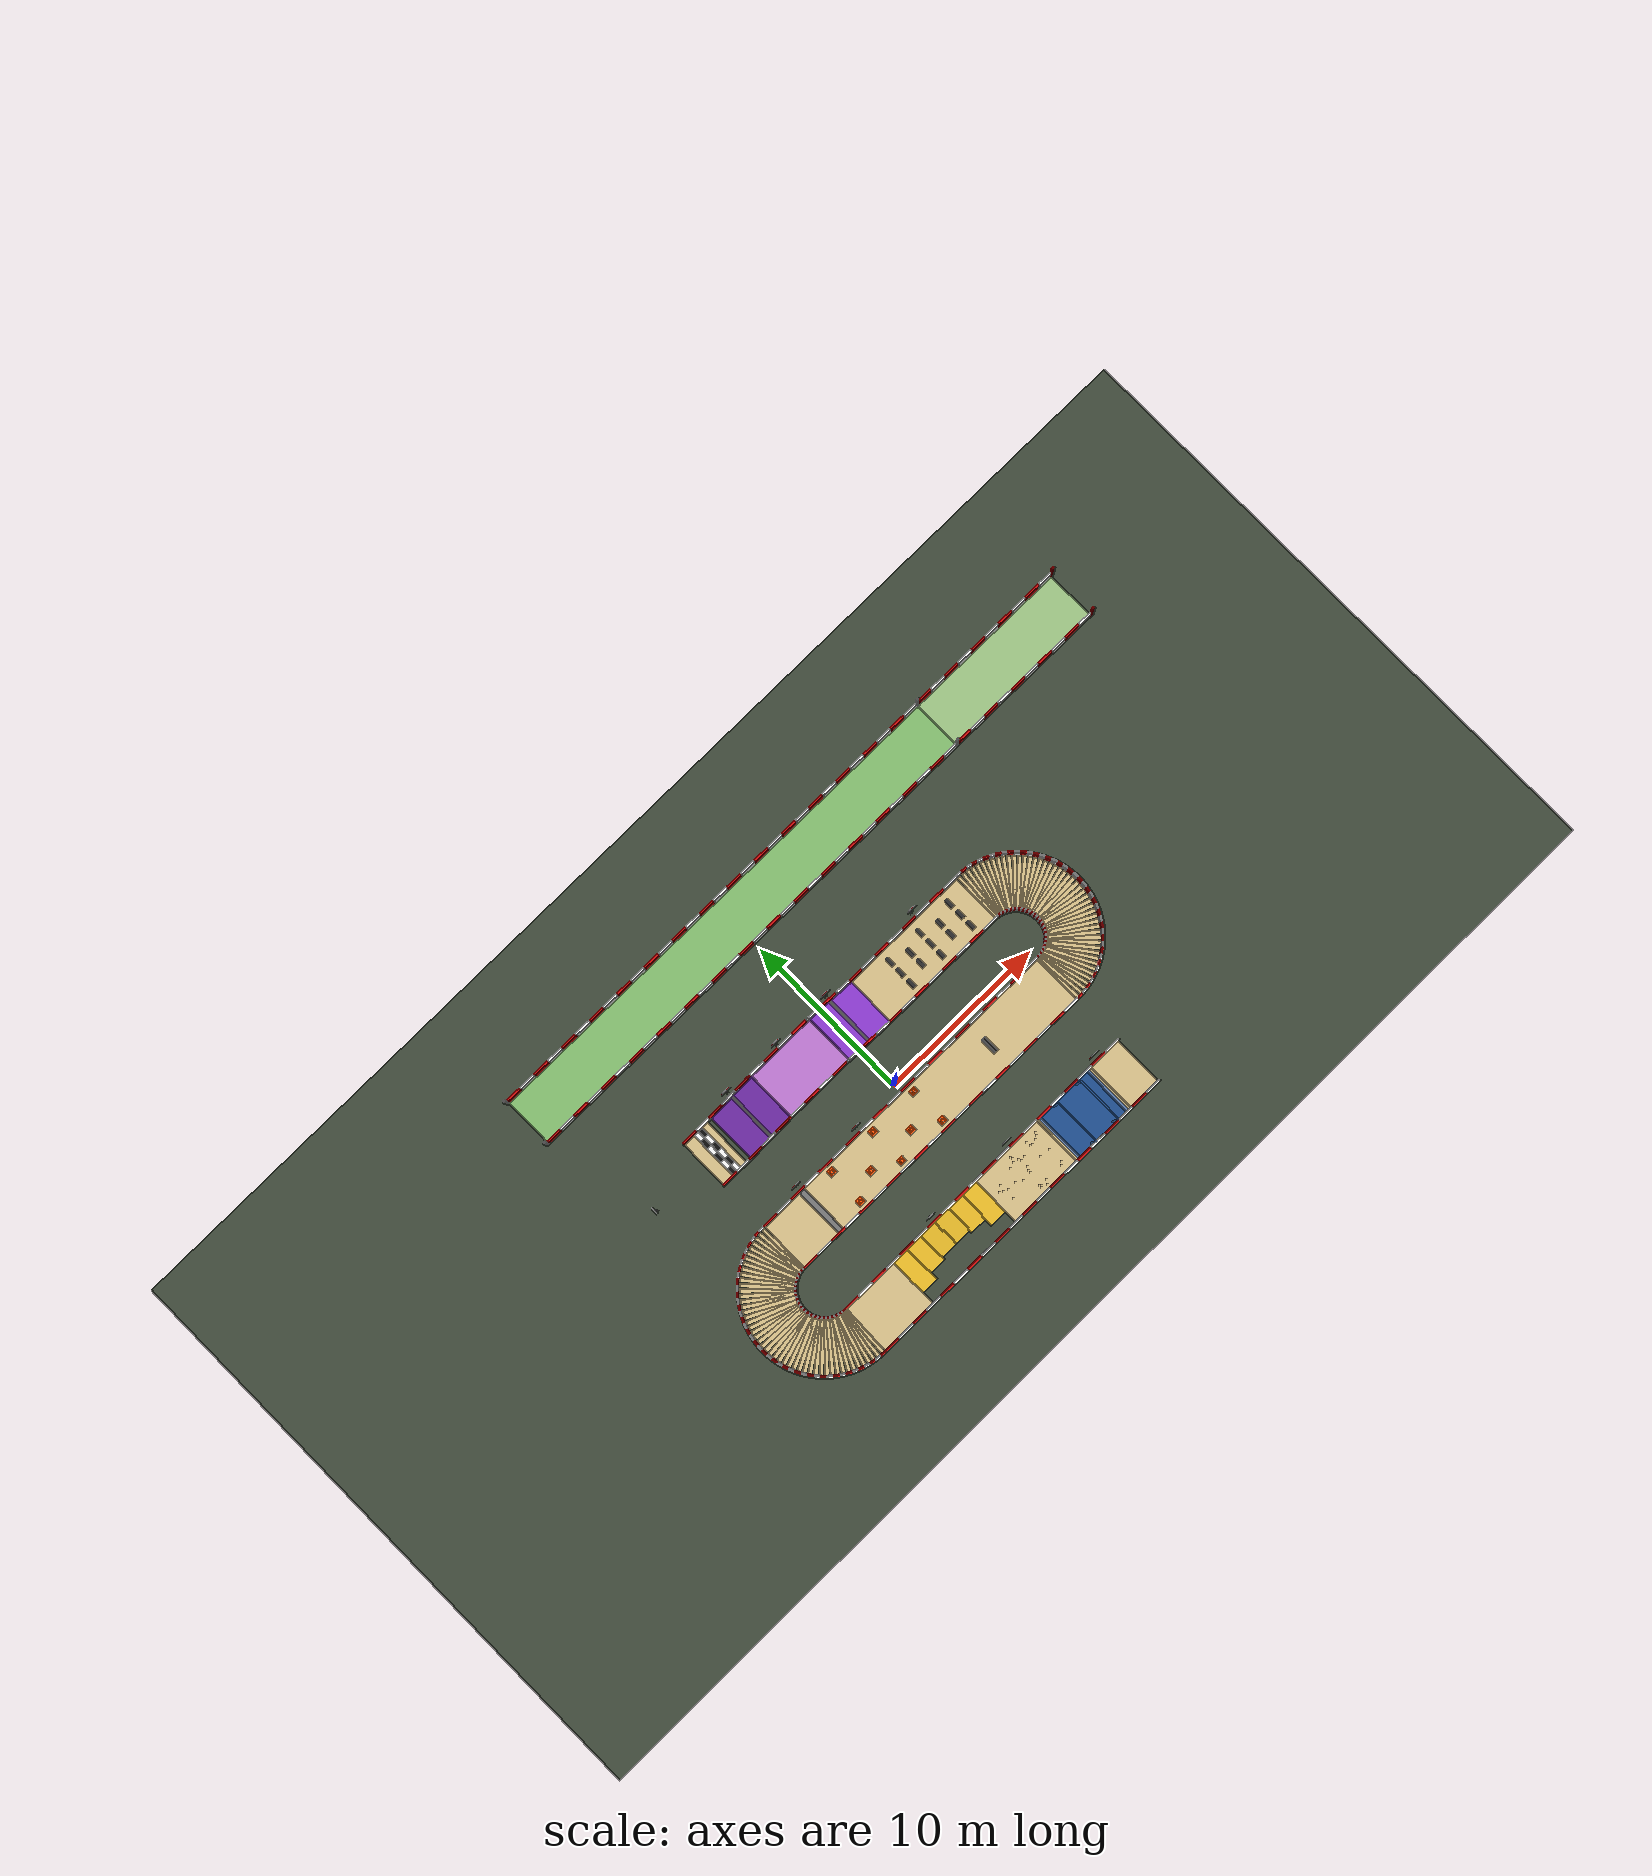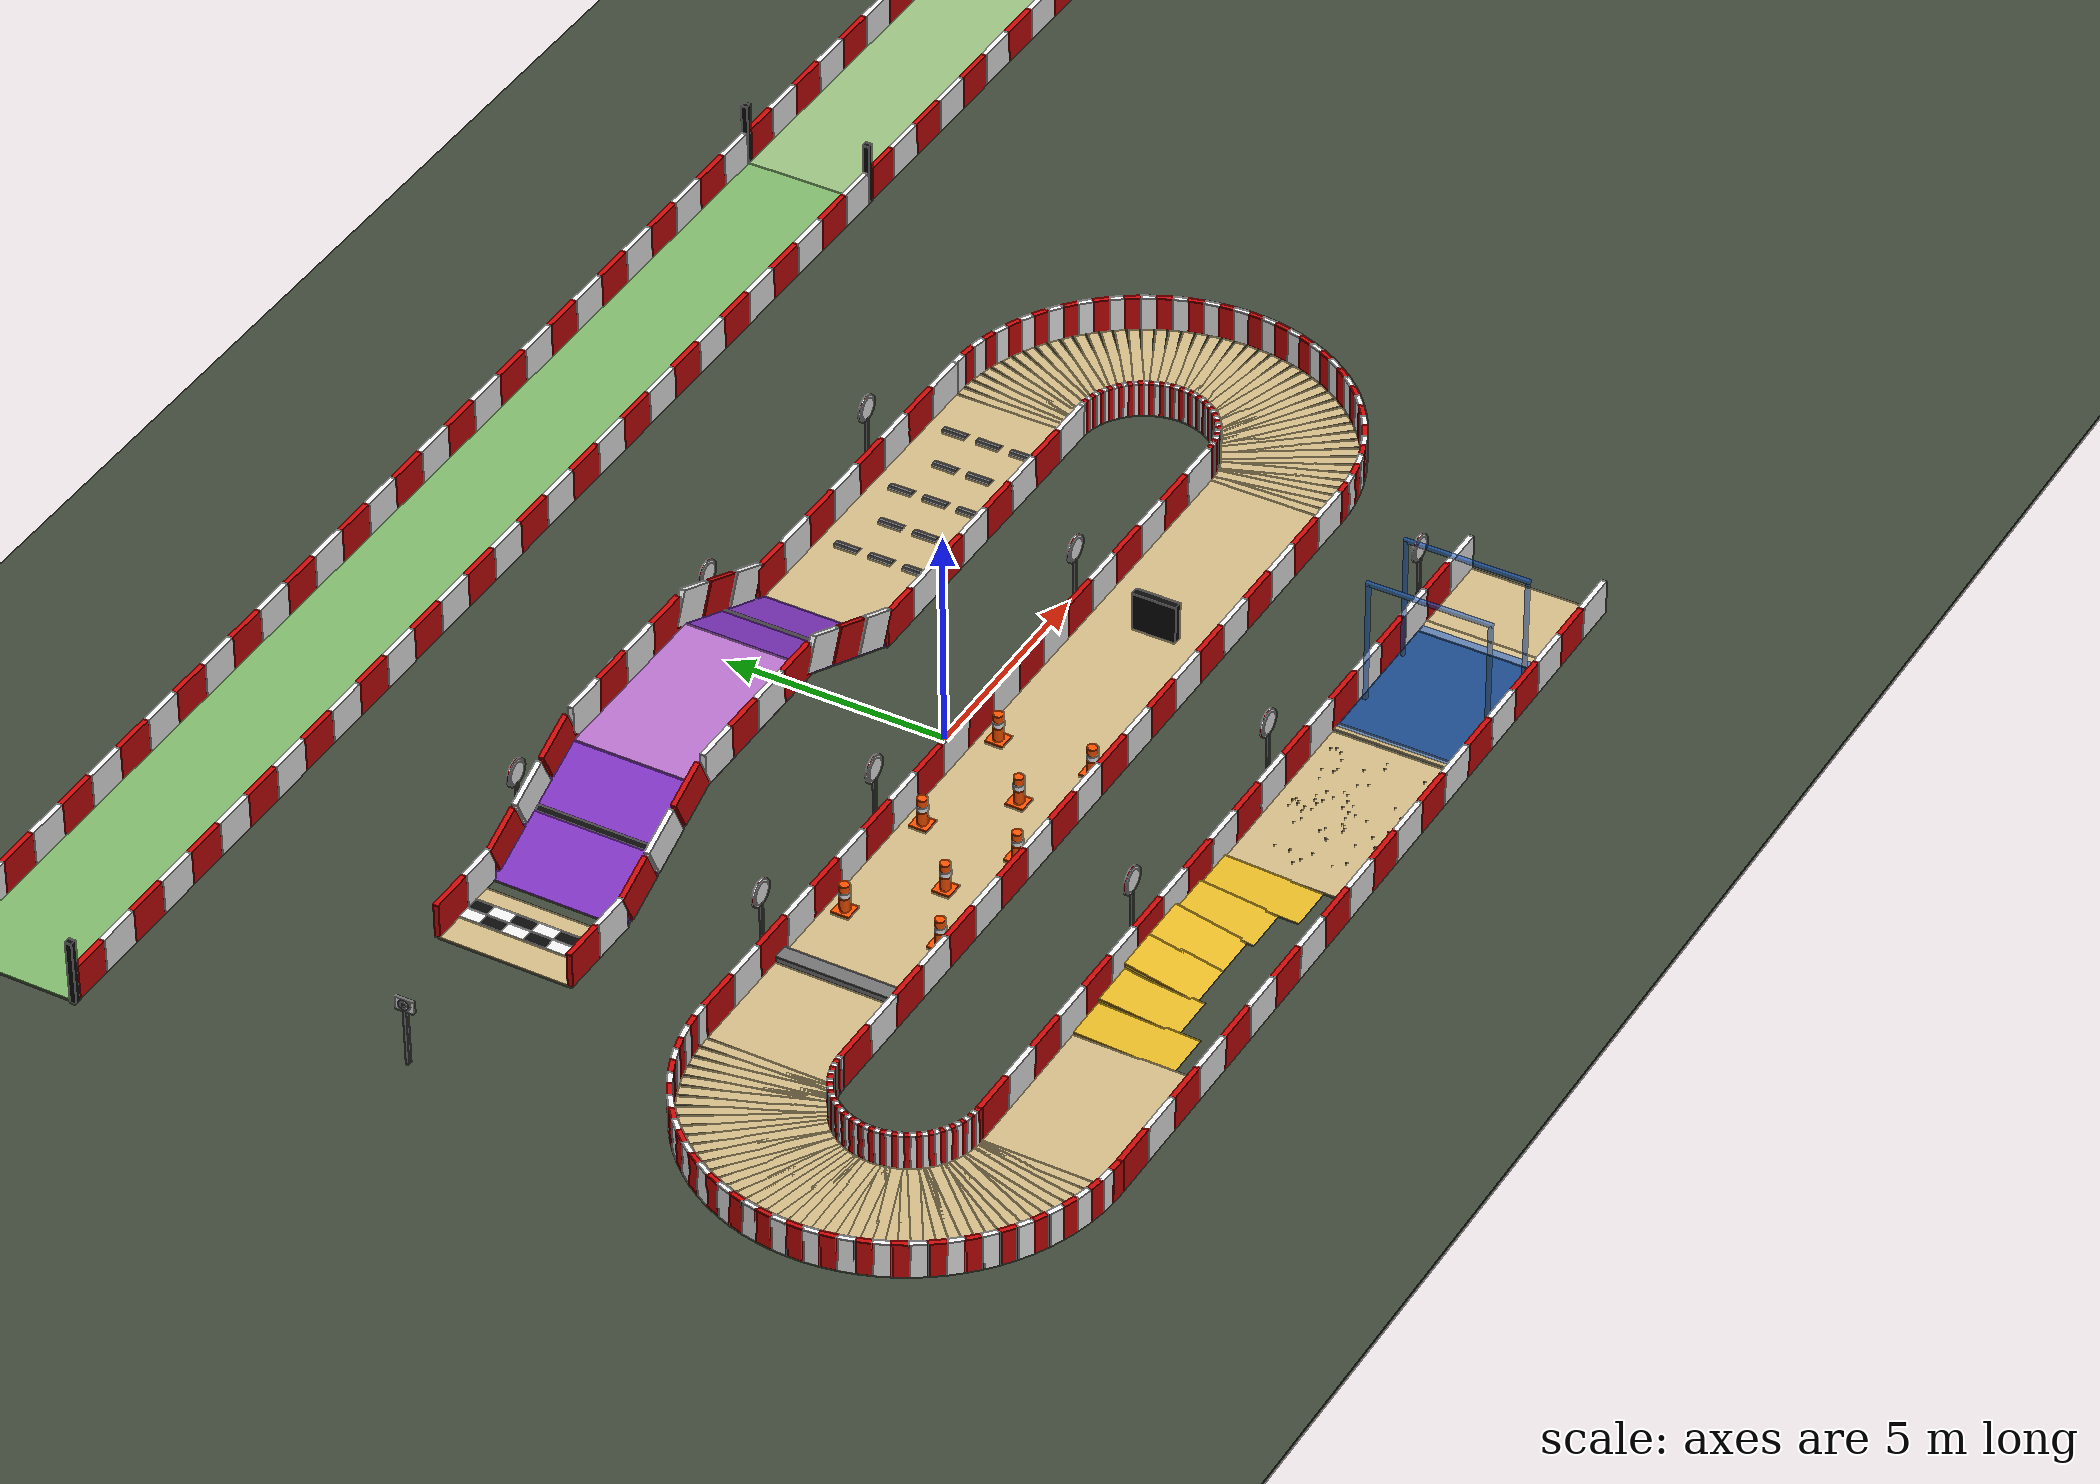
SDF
<?xml version="1.0"?>
<sdf version="1.6">
  <world name="evrenos_teknofest_2026">

    <physics name="default_physics" type="ode">
      <max_step_size>0.001</max_step_size>
      <real_time_factor>1.0</real_time_factor>
      <real_time_update_rate>1000</real_time_update_rate>
    </physics>

    <scene>
      <ambient>0.55 0.55 0.55 1</ambient>
      <background>0.72 0.82 0.92 1</background>
      <shadows>true</shadows>
    </scene>

    <include>
      <uri>model://sun</uri>
    </include>

    <model name="main_course">
      <static>true</static>

      <link name="arena_floor">
        <pose>0 2 -0.08 0 0 0</pose>
        <collision name="arena_floor_collision">
          <geometry><box><size>70.0000 35.0000 0.1000</size></box></geometry>
        </collision>
        <visual name="arena_floor_visual">
          <geometry><box><size>70.0000 35.0000 0.1000</size></box></geometry>

          <material>
            <ambient>0.24 0.28 0.22 1</ambient>
            <diffuse>0.24 0.28 0.22 1</diffuse>
          </material>
        </visual>
      </link>
      <link name="bottom_start_0">
        <pose>9.0000 -8.0000 -0.0500 0.000000 0.000000 0.000000</pose>
        <collision name="bottom_start_0_collision">
          <geometry><box><size>2.0000 3.0000 0.1000</size></box></geometry>
        </collision>
        <visual name="bottom_start_0_visual">
          <geometry><box><size>2.0000 3.0000 0.1000</size></box></geometry>

          <material>
            <ambient>0.82 0.73 0.52 1</ambient>
            <diffuse>0.82 0.73 0.52 1</diffuse>
          </material>
        </visual>
      </link>
      <link name="bottom_after_water_0">
        <pose>1.7500 -8.0000 -0.0500 0.000000 0.000000 0.000000</pose>
        <collision name="bottom_after_water_0_collision">
          <geometry><box><size>4.5000 3.0000 0.1000</size></box></geometry>
        </collision>
        <visual name="bottom_after_water_0_visual">
          <geometry><box><size>4.5000 3.0000 0.1000</size></box></geometry>

          <material>
            <ambient>0.82 0.73 0.52 1</ambient>
            <diffuse>0.82 0.73 0.52 1</diffuse>
          </material>
        </visual>
      </link>
      <link name="bottom_before_turn_0">
        <pose>-8.2500 -8.0000 -0.0500 0.000000 0.000000 0.000000</pose>
        <collision name="bottom_before_turn_0_collision">
          <geometry><box><size>3.5000 3.0000 0.1000</size></box></geometry>
        </collision>
        <visual name="bottom_before_turn_0_visual">
          <geometry><box><size>3.5000 3.0000 0.1000</size></box></geometry>

          <material>
            <ambient>0.82 0.73 0.52 1</ambient>
            <diffuse>0.82 0.73 0.52 1</diffuse>
          </material>
        </visual>
      </link>
      <link name="water_ramp_down">
        <pose>7.2500 -8.0000 -0.2000 0.000000 -0.260602 0.000000</pose>
        <collision name="water_ramp_down_collision">
          <geometry><box><size>1.5524 3.0000 0.1000</size></box></geometry>
        </collision>
        <visual name="water_ramp_down_visual">
          <geometry><box><size>1.5524 3.0000 0.1000</size></box></geometry>

          <material>
            <ambient>0.82 0.73 0.52 1</ambient>
            <diffuse>0.82 0.73 0.52 1</diffuse>
          </material>
        </visual>
      </link>
      <link name="water_basin_floor">
        <pose>6.0000 -8.0000 -0.4500 0.000000 0.000000 0.000000</pose>
        <collision name="water_basin_floor_collision">
          <geometry><box><size>1.0000 3.0000 0.1000</size></box></geometry>
        </collision>
        <visual name="water_basin_floor_visual">
          <geometry><box><size>1.0000 3.0000 0.1000</size></box></geometry>

          <material>
            <ambient>0.52 0.47 0.35 1</ambient>
            <diffuse>0.52 0.47 0.35 1</diffuse>
          </material>
        </visual>
      </link>
      <link name="water_ramp_up">
        <pose>4.7500 -8.0000 -0.2000 0.000000 0.260602 0.000000</pose>
        <collision name="water_ramp_up_collision">
          <geometry><box><size>1.5524 3.0000 0.1000</size></box></geometry>
        </collision>
        <visual name="water_ramp_up_visual">
          <geometry><box><size>1.5524 3.0000 0.1000</size></box></geometry>

          <material>
            <ambient>0.82 0.73 0.52 1</ambient>
            <diffuse>0.82 0.73 0.52 1</diffuse>
          </material>
        </visual>
      </link>
      <link name="water_surface">
        <pose>6.0000 -8.0000 0.0050 0.000000 0.000000 0.000000</pose>
        <visual name="water_surface_visual">
          <geometry><box><size>4.0000 2.9000 0.0100</size></box></geometry>

          <material>
            <ambient>0.05 0.35 0.85 0.55</ambient>
            <diffuse>0.05 0.35 0.85 0.55</diffuse>
          </material>
        </visual>
      </link>
      <link name="rain_post_5.2_-9.35">
        <pose>5.2000 -9.3500 1.4500 0.000000 0.000000 0.000000</pose>
        <collision name="rain_post_5.2_-9.35_collision">
          <geometry><box><size>0.0800 0.0800 2.9000</size></box></geometry>
        </collision>
        <visual name="rain_post_5.2_-9.35_visual">
          <geometry><box><size>0.0800 0.0800 2.9000</size></box></geometry>

          <material>
            <ambient>0.05 0.35 0.85 0.55</ambient>
            <diffuse>0.05 0.35 0.85 0.55</diffuse>
          </material>
        </visual>
      </link>
      <link name="rain_post_5.2_-6.65">
        <pose>5.2000 -6.6500 1.4500 0.000000 0.000000 0.000000</pose>
        <collision name="rain_post_5.2_-6.65_collision">
          <geometry><box><size>0.0800 0.0800 2.9000</size></box></geometry>
        </collision>
        <visual name="rain_post_5.2_-6.65_visual">
          <geometry><box><size>0.0800 0.0800 2.9000</size></box></geometry>

          <material>
            <ambient>0.05 0.35 0.85 0.55</ambient>
            <diffuse>0.05 0.35 0.85 0.55</diffuse>
          </material>
        </visual>
      </link>
      <link name="rain_post_6.8_-9.35">
        <pose>6.8000 -9.3500 1.4500 0.000000 0.000000 0.000000</pose>
        <collision name="rain_post_6.8_-9.35_collision">
          <geometry><box><size>0.0800 0.0800 2.9000</size></box></geometry>
        </collision>
        <visual name="rain_post_6.8_-9.35_visual">
          <geometry><box><size>0.0800 0.0800 2.9000</size></box></geometry>

          <material>
            <ambient>0.05 0.35 0.85 0.55</ambient>
            <diffuse>0.05 0.35 0.85 0.55</diffuse>
          </material>
        </visual>
      </link>
      <link name="rain_post_6.8_-6.65">
        <pose>6.8000 -6.6500 1.4500 0.000000 0.000000 0.000000</pose>
        <collision name="rain_post_6.8_-6.65_collision">
          <geometry><box><size>0.0800 0.0800 2.9000</size></box></geometry>
        </collision>
        <visual name="rain_post_6.8_-6.65_visual">
          <geometry><box><size>0.0800 0.0800 2.9000</size></box></geometry>

          <material>
            <ambient>0.05 0.35 0.85 0.55</ambient>
            <diffuse>0.05 0.35 0.85 0.55</diffuse>
          </material>
        </visual>
      </link>
      <link name="rain_cross_5.2">
        <pose>5.2000 -8.0000 2.9000 0.000000 0.000000 0.000000</pose>
        <collision name="rain_cross_5.2_collision">
          <geometry><box><size>0.0800 2.8000 0.0800</size></box></geometry>
        </collision>
        <visual name="rain_cross_5.2_visual">
          <geometry><box><size>0.0800 2.8000 0.0800</size></box></geometry>

          <material>
            <ambient>0.05 0.35 0.85 0.55</ambient>
            <diffuse>0.05 0.35 0.85 0.55</diffuse>
          </material>
        </visual>
      </link>
      <link name="rain_cross_6.8">
        <pose>6.8000 -8.0000 2.9000 0.000000 0.000000 0.000000</pose>
        <collision name="rain_cross_6.8_collision">
          <geometry><box><size>0.0800 2.8000 0.0800</size></box></geometry>
        </collision>
        <visual name="rain_cross_6.8_visual">
          <geometry><box><size>0.0800 2.8000 0.0800</size></box></geometry>

          <material>
            <ambient>0.05 0.35 0.85 0.55</ambient>
            <diffuse>0.05 0.35 0.85 0.55</diffuse>
          </material>
        </visual>
      </link>
      <link name="gravel_0">
        <pose>0.4288 -7.9935 0.0103 0 0 0</pose>
        <collision name="gravel_0_collision">
          <geometry><sphere><radius>0.0187</radius></sphere></geometry>
        </collision>
        <visual name="gravel_0_visual">
          <geometry><sphere><radius>0.0187</radius></sphere></geometry>

          <material>
            <ambient>0.43 0.35 0.27 1</ambient>
            <diffuse>0.43 0.35 0.27 1</diffuse>
          </material>
        </visual>
      </link>
      <link name="gravel_1">
        <pose>3.0960 -9.0331 0.0082 0 0 0</pose>
        <collision name="gravel_1_collision">
          <geometry><sphere><radius>0.0149</radius></sphere></geometry>
        </collision>
        <visual name="gravel_1_visual">
          <geometry><sphere><radius>0.0149</radius></sphere></geometry>

          <material>
            <ambient>0.43 0.35 0.27 1</ambient>
            <diffuse>0.43 0.35 0.27 1</diffuse>
          </material>
        </visual>
      </link>
      <link name="gravel_2">
        <pose>2.1637 -7.8529 0.0122 0 0 0</pose>
        <collision name="gravel_2_collision">
          <geometry><sphere><radius>0.0222</radius></sphere></geometry>
        </collision>
        <visual name="gravel_2_visual">
          <geometry><sphere><radius>0.0222</radius></sphere></geometry>

          <material>
            <ambient>0.43 0.35 0.27 1</ambient>
            <diffuse>0.43 0.35 0.27 1</diffuse>
          </material>
        </visual>
      </link>
      <link name="gravel_3">
        <pose>1.9721 -7.4006 0.0121 0 0 0</pose>
        <collision name="gravel_3_collision">
          <geometry><sphere><radius>0.0220</radius></sphere></geometry>
        </collision>
        <visual name="gravel_3_visual">
          <geometry><sphere><radius>0.0220</radius></sphere></geometry>

          <material>
            <ambient>0.43 0.35 0.27 1</ambient>
            <diffuse>0.43 0.35 0.27 1</diffuse>
          </material>
        </visual>
      </link>
      <link name="gravel_4">
        <pose>2.7037 -7.7750 0.0083 0 0 0</pose>
        <collision name="gravel_4_collision">
          <geometry><sphere><radius>0.0151</radius></sphere></geometry>
        </collision>
        <visual name="gravel_4_visual">
          <geometry><sphere><radius>0.0151</radius></sphere></geometry>

          <material>
            <ambient>0.43 0.35 0.27 1</ambient>
            <diffuse>0.43 0.35 0.27 1</diffuse>
          </material>
        </visual>
      </link>
      <link name="gravel_5">
        <pose>2.2111 -9.0121 0.0124 0 0 0</pose>
        <collision name="gravel_5_collision">
          <geometry><sphere><radius>0.0226</radius></sphere></geometry>
        </collision>
        <visual name="gravel_5_visual">
          <geometry><sphere><radius>0.0226</radius></sphere></geometry>

          <material>
            <ambient>0.43 0.35 0.27 1</ambient>
            <diffuse>0.43 0.35 0.27 1</diffuse>
          </material>
        </visual>
      </link>
      <link name="gravel_6">
        <pose>1.6188 -7.1816 0.0115 0 0 0</pose>
        <collision name="gravel_6_collision">
          <geometry><sphere><radius>0.0209</radius></sphere></geometry>
        </collision>
        <visual name="gravel_6_visual">
          <geometry><sphere><radius>0.0209</radius></sphere></geometry>

          <material>
            <ambient>0.43 0.35 0.27 1</ambient>
            <diffuse>0.43 0.35 0.27 1</diffuse>
          </material>
        </visual>
      </link>
      <link name="gravel_7">
        <pose>2.4458 -8.7534 0.0084 0 0 0</pose>
        <collision name="gravel_7_collision">
          <geometry><sphere><radius>0.0153</radius></sphere></geometry>
        </collision>
        <visual name="gravel_7_visual">
          <geometry><sphere><radius>0.0153</radius></sphere></geometry>

          <material>
            <ambient>0.43 0.35 0.27 1</ambient>
            <diffuse>0.43 0.35 0.27 1</diffuse>
          </material>
        </visual>
      </link>
      <link name="gravel_8">
        <pose>3.5277 -6.8838 0.0124 0 0 0</pose>
        <collision name="gravel_8_collision">
          <geometry><sphere><radius>0.0225</radius></sphere></geometry>
        </collision>
        <visual name="gravel_8_visual">
          <geometry><sphere><radius>0.0225</radius></sphere></geometry>

          <material>
            <ambient>0.43 0.35 0.27 1</ambient>
            <diffuse>0.43 0.35 0.27 1</diffuse>
          </material>
        </visual>
      </link>
      <link name="gravel_9">
        <pose>3.5988 -7.9647 0.0071 0 0 0</pose>
        <collision name="gravel_9_collision">
          <geometry><sphere><radius>0.0130</radius></sphere></geometry>
        </collision>
        <visual name="gravel_9_visual">
          <geometry><sphere><radius>0.0130</radius></sphere></geometry>

          <material>
            <ambient>0.43 0.35 0.27 1</ambient>
            <diffuse>0.43 0.35 0.27 1</diffuse>
          </material>
        </visual>
      </link>
      <link name="gravel_10">
        <pose>1.2254 -7.8506 0.0087 0 0 0</pose>
        <collision name="gravel_10_collision">
          <geometry><sphere><radius>0.0158</radius></sphere></geometry>
        </collision>
        <visual name="gravel_10_visual">
          <geometry><sphere><radius>0.0158</radius></sphere></geometry>

          <material>
            <ambient>0.43 0.35 0.27 1</ambient>
            <diffuse>0.43 0.35 0.27 1</diffuse>
          </material>
        </visual>
      </link>
      <link name="gravel_11">
        <pose>1.6468 -7.0212 0.0116 0 0 0</pose>
        <collision name="gravel_11_collision">
          <geometry><sphere><radius>0.0212</radius></sphere></geometry>
        </collision>
        <visual name="gravel_11_visual">
          <geometry><sphere><radius>0.0212</radius></sphere></geometry>

          <material>
            <ambient>0.43 0.35 0.27 1</ambient>
            <diffuse>0.43 0.35 0.27 1</diffuse>
          </material>
        </visual>
      </link>
      <link name="gravel_12">
        <pose>2.0787 -9.2357 0.0117 0 0 0</pose>
        <collision name="gravel_12_collision">
          <geometry><sphere><radius>0.0212</radius></sphere></geometry>
        </collision>
        <visual name="gravel_12_visual">
          <geometry><sphere><radius>0.0212</radius></sphere></geometry>

          <material>
            <ambient>0.43 0.35 0.27 1</ambient>
            <diffuse>0.43 0.35 0.27 1</diffuse>
          </material>
        </visual>
      </link>
      <link name="gravel_13">
        <pose>1.3088 -8.2022 0.0095 0 0 0</pose>
        <collision name="gravel_13_collision">
          <geometry><sphere><radius>0.0172</radius></sphere></geometry>
        </collision>
        <visual name="gravel_13_visual">
          <geometry><sphere><radius>0.0172</radius></sphere></geometry>

          <material>
            <ambient>0.43 0.35 0.27 1</ambient>
            <diffuse>0.43 0.35 0.27 1</diffuse>
          </material>
        </visual>
      </link>
      <link name="gravel_14">
        <pose>2.1086 -8.0040 0.0074 0 0 0</pose>
        <collision name="gravel_14_collision">
          <geometry><sphere><radius>0.0135</radius></sphere></geometry>
        </collision>
        <visual name="gravel_14_visual">
          <geometry><sphere><radius>0.0135</radius></sphere></geometry>

          <material>
            <ambient>0.43 0.35 0.27 1</ambient>
            <diffuse>0.43 0.35 0.27 1</diffuse>
          </material>
        </visual>
      </link>
      <link name="gravel_15">
        <pose>1.8229 -7.3496 0.0109 0 0 0</pose>
        <collision name="gravel_15_collision">
          <geometry><sphere><radius>0.0198</radius></sphere></geometry>
        </collision>
        <visual name="gravel_15_visual">
          <geometry><sphere><radius>0.0198</radius></sphere></geometry>

          <material>
            <ambient>0.43 0.35 0.27 1</ambient>
            <diffuse>0.43 0.35 0.27 1</diffuse>
          </material>
        </visual>
      </link>
      <link name="gravel_16">
        <pose>1.7677 -6.9164 0.0084 0 0 0</pose>
        <collision name="gravel_16_collision">
          <geometry><sphere><radius>0.0154</radius></sphere></geometry>
        </collision>
        <visual name="gravel_16_visual">
          <geometry><sphere><radius>0.0154</radius></sphere></geometry>

          <material>
            <ambient>0.43 0.35 0.27 1</ambient>
            <diffuse>0.43 0.35 0.27 1</diffuse>
          </material>
        </visual>
      </link>
      <link name="gravel_17">
        <pose>1.5119 -6.8918 0.0100 0 0 0</pose>
        <collision name="gravel_17_collision">
          <geometry><sphere><radius>0.0182</radius></sphere></geometry>
        </collision>
        <visual name="gravel_17_visual">
          <geometry><sphere><radius>0.0182</radius></sphere></geometry>

          <material>
            <ambient>0.43 0.35 0.27 1</ambient>
            <diffuse>0.43 0.35 0.27 1</diffuse>
          </material>
        </visual>
      </link>
      <link name="gravel_18">
        <pose>1.8648 -9.2340 0.0082 0 0 0</pose>
        <collision name="gravel_18_collision">
          <geometry><sphere><radius>0.0149</radius></sphere></geometry>
        </collision>
        <visual name="gravel_18_visual">
          <geometry><sphere><radius>0.0149</radius></sphere></geometry>

          <material>
            <ambient>0.43 0.35 0.27 1</ambient>
            <diffuse>0.43 0.35 0.27 1</diffuse>
          </material>
        </visual>
      </link>
      <link name="gravel_19">
        <pose>0.4644 -9.1729 0.0116 0 0 0</pose>
        <collision name="gravel_19_collision">
          <geometry><sphere><radius>0.0212</radius></sphere></geometry>
        </collision>
        <visual name="gravel_19_visual">
          <geometry><sphere><radius>0.0212</radius></sphere></geometry>

          <material>
            <ambient>0.43 0.35 0.27 1</ambient>
            <diffuse>0.43 0.35 0.27 1</diffuse>
          </material>
        </visual>
      </link>
      <link name="gravel_20">
        <pose>3.1926 -9.0333 0.0110 0 0 0</pose>
        <collision name="gravel_20_collision">
          <geometry><sphere><radius>0.0201</radius></sphere></geometry>
        </collision>
        <visual name="gravel_20_visual">
          <geometry><sphere><radius>0.0201</radius></sphere></geometry>

          <material>
            <ambient>0.43 0.35 0.27 1</ambient>
            <diffuse>0.43 0.35 0.27 1</diffuse>
          </material>
        </visual>
      </link>
      <link name="gravel_21">
        <pose>1.6921 -8.0465 0.0082 0 0 0</pose>
        <collision name="gravel_21_collision">
          <geometry><sphere><radius>0.0150</radius></sphere></geometry>
        </collision>
        <visual name="gravel_21_visual">
          <geometry><sphere><radius>0.0150</radius></sphere></geometry>

          <material>
            <ambient>0.43 0.35 0.27 1</ambient>
            <diffuse>0.43 0.35 0.27 1</diffuse>
          </material>
        </visual>
      </link>
      <link name="gravel_22">
        <pose>3.1893 -7.6707 0.0099 0 0 0</pose>
        <collision name="gravel_22_collision">
          <geometry><sphere><radius>0.0179</radius></sphere></geometry>
        </collision>
        <visual name="gravel_22_visual">
          <geometry><sphere><radius>0.0179</radius></sphere></geometry>

          <material>
            <ambient>0.43 0.35 0.27 1</ambient>
            <diffuse>0.43 0.35 0.27 1</diffuse>
          </material>
        </visual>
      </link>
      <link name="gravel_23">
        <pose>1.6899 -6.8834 0.0137 0 0 0</pose>
        <collision name="gravel_23_collision">
          <geometry><sphere><radius>0.0248</radius></sphere></geometry>
        </collision>
        <visual name="gravel_23_visual">
          <geometry><sphere><radius>0.0248</radius></sphere></geometry>

          <material>
            <ambient>0.43 0.35 0.27 1</ambient>
            <diffuse>0.43 0.35 0.27 1</diffuse>
          </material>
        </visual>
      </link>
      <link name="gravel_24">
        <pose>1.9643 -7.8445 0.0114 0 0 0</pose>
        <collision name="gravel_24_collision">
          <geometry><sphere><radius>0.0207</radius></sphere></geometry>
        </collision>
        <visual name="gravel_24_visual">
          <geometry><sphere><radius>0.0207</radius></sphere></geometry>

          <material>
            <ambient>0.43 0.35 0.27 1</ambient>
            <diffuse>0.43 0.35 0.27 1</diffuse>
          </material>
        </visual>
      </link>
      <link name="gravel_25">
        <pose>1.1075 -7.2205 0.0102 0 0 0</pose>
        <collision name="gravel_25_collision">
          <geometry><sphere><radius>0.0185</radius></sphere></geometry>
        </collision>
        <visual name="gravel_25_visual">
          <geometry><sphere><radius>0.0185</radius></sphere></geometry>

          <material>
            <ambient>0.43 0.35 0.27 1</ambient>
            <diffuse>0.43 0.35 0.27 1</diffuse>
          </material>
        </visual>
      </link>
      <link name="gravel_26">
        <pose>1.7240 -7.0004 0.0097 0 0 0</pose>
        <collision name="gravel_26_collision">
          <geometry><sphere><radius>0.0176</radius></sphere></geometry>
        </collision>
        <visual name="gravel_26_visual">
          <geometry><sphere><radius>0.0176</radius></sphere></geometry>

          <material>
            <ambient>0.43 0.35 0.27 1</ambient>
            <diffuse>0.43 0.35 0.27 1</diffuse>
          </material>
        </visual>
      </link>
      <link name="gravel_27">
        <pose>1.0597 -8.6005 0.0068 0 0 0</pose>
        <collision name="gravel_27_collision">
          <geometry><sphere><radius>0.0124</radius></sphere></geometry>
        </collision>
        <visual name="gravel_27_visual">
          <geometry><sphere><radius>0.0124</radius></sphere></geometry>

          <material>
            <ambient>0.43 0.35 0.27 1</ambient>
            <diffuse>0.43 0.35 0.27 1</diffuse>
          </material>
        </visual>
      </link>
      <link name="gravel_28">
        <pose>2.3603 -7.7471 0.0099 0 0 0</pose>
        <collision name="gravel_28_collision">
          <geometry><sphere><radius>0.0180</radius></sphere></geometry>
        </collision>
        <visual name="gravel_28_visual">
          <geometry><sphere><radius>0.0180</radius></sphere></geometry>

          <material>
            <ambient>0.43 0.35 0.27 1</ambient>
            <diffuse>0.43 0.35 0.27 1</diffuse>
          </material>
        </visual>
      </link>
      <link name="gravel_29">
        <pose>1.8824 -8.0273 0.0132 0 0 0</pose>
        <collision name="gravel_29_collision">
          <geometry><sphere><radius>0.0240</radius></sphere></geometry>
        </collision>
        <visual name="gravel_29_visual">
          <geometry><sphere><radius>0.0240</radius></sphere></geometry>

          <material>
            <ambient>0.43 0.35 0.27 1</ambient>
            <diffuse>0.43 0.35 0.27 1</diffuse>
          </material>
        </visual>
      </link>
      <link name="gravel_30">
        <pose>0.9364 -8.0375 0.0103 0 0 0</pose>
        <collision name="gravel_30_collision">
          <geometry><sphere><radius>0.0186</radius></sphere></geometry>
        </collision>
        <visual name="gravel_30_visual">
          <geometry><sphere><radius>0.0186</radius></sphere></geometry>

          <material>
            <ambient>0.43 0.35 0.27 1</ambient>
            <diffuse>0.43 0.35 0.27 1</diffuse>
          </material>
        </visual>
      </link>
      <link name="gravel_31">
        <pose>2.9742 -7.1993 0.0106 0 0 0</pose>
        <collision name="gravel_31_collision">
          <geometry><sphere><radius>0.0193</radius></sphere></geometry>
        </collision>
        <visual name="gravel_31_visual">
          <geometry><sphere><radius>0.0193</radius></sphere></geometry>

          <material>
            <ambient>0.43 0.35 0.27 1</ambient>
            <diffuse>0.43 0.35 0.27 1</diffuse>
          </material>
        </visual>
      </link>
      <link name="gravel_32">
        <pose>3.2662 -7.1384 0.0089 0 0 0</pose>
        <collision name="gravel_32_collision">
          <geometry><sphere><radius>0.0161</radius></sphere></geometry>
        </collision>
        <visual name="gravel_32_visual">
          <geometry><sphere><radius>0.0161</radius></sphere></geometry>

          <material>
            <ambient>0.43 0.35 0.27 1</ambient>
            <diffuse>0.43 0.35 0.27 1</diffuse>
          </material>
        </visual>
      </link>
      <link name="gravel_33">
        <pose>3.3005 -9.0442 0.0115 0 0 0</pose>
        <collision name="gravel_33_collision">
          <geometry><sphere><radius>0.0210</radius></sphere></geometry>
        </collision>
        <visual name="gravel_33_visual">
          <geometry><sphere><radius>0.0210</radius></sphere></geometry>

          <material>
            <ambient>0.43 0.35 0.27 1</ambient>
            <diffuse>0.43 0.35 0.27 1</diffuse>
          </material>
        </visual>
      </link>
      <link name="gravel_34">
        <pose>2.8263 -7.9605 0.0098 0 0 0</pose>
        <collision name="gravel_34_collision">
          <geometry><sphere><radius>0.0179</radius></sphere></geometry>
        </collision>
        <visual name="gravel_34_visual">
          <geometry><sphere><radius>0.0179</radius></sphere></geometry>

          <material>
            <ambient>0.43 0.35 0.27 1</ambient>
            <diffuse>0.43 0.35 0.27 1</diffuse>
          </material>
        </visual>
      </link>
      <link name="gravel_35">
        <pose>3.4750 -6.7851 0.0126 0 0 0</pose>
        <collision name="gravel_35_collision">
          <geometry><sphere><radius>0.0230</radius></sphere></geometry>
        </collision>
        <visual name="gravel_35_visual">
          <geometry><sphere><radius>0.0230</radius></sphere></geometry>

          <material>
            <ambient>0.43 0.35 0.27 1</ambient>
            <diffuse>0.43 0.35 0.27 1</diffuse>
          </material>
        </visual>
      </link>
      <link name="gravel_36">
        <pose>1.7249 -9.1328 0.0085 0 0 0</pose>
        <collision name="gravel_36_collision">
          <geometry><sphere><radius>0.0155</radius></sphere></geometry>
        </collision>
        <visual name="gravel_36_visual">
          <geometry><sphere><radius>0.0155</radius></sphere></geometry>

          <material>
            <ambient>0.43 0.35 0.27 1</ambient>
            <diffuse>0.43 0.35 0.27 1</diffuse>
          </material>
        </visual>
      </link>
      <link name="gravel_37">
        <pose>1.7943 -9.0487 0.0119 0 0 0</pose>
        <collision name="gravel_37_collision">
          <geometry><sphere><radius>0.0217</radius></sphere></geometry>
        </collision>
        <visual name="gravel_37_visual">
          <geometry><sphere><radius>0.0217</radius></sphere></geometry>

          <material>
            <ambient>0.43 0.35 0.27 1</ambient>
            <diffuse>0.43 0.35 0.27 1</diffuse>
          </material>
        </visual>
      </link>
      <link name="gravel_38">
        <pose>1.4807 -8.1316 0.0067 0 0 0</pose>
        <collision name="gravel_38_collision">
          <geometry><sphere><radius>0.0122</radius></sphere></geometry>
        </collision>
        <visual name="gravel_38_visual">
          <geometry><sphere><radius>0.0122</radius></sphere></geometry>

          <material>
            <ambient>0.43 0.35 0.27 1</ambient>
            <diffuse>0.43 0.35 0.27 1</diffuse>
          </material>
        </visual>
      </link>
      <link name="gravel_39">
        <pose>0.0008 -7.7903 0.0133 0 0 0</pose>
        <collision name="gravel_39_collision">
          <geometry><sphere><radius>0.0241</radius></sphere></geometry>
        </collision>
        <visual name="gravel_39_visual">
          <geometry><sphere><radius>0.0241</radius></sphere></geometry>

          <material>
            <ambient>0.43 0.35 0.27 1</ambient>
            <diffuse>0.43 0.35 0.27 1</diffuse>
          </material>
        </visual>
      </link>
      <link name="gravel_40">
        <pose>0.2990 -7.2362 0.0084 0 0 0</pose>
        <collision name="gravel_40_collision">
          <geometry><sphere><radius>0.0152</radius></sphere></geometry>
        </collision>
        <visual name="gravel_40_visual">
          <geometry><sphere><radius>0.0152</radius></sphere></geometry>

          <material>
            <ambient>0.43 0.35 0.27 1</ambient>
            <diffuse>0.43 0.35 0.27 1</diffuse>
          </material>
        </visual>
      </link>
      <link name="gravel_41">
        <pose>2.2359 -7.3452 0.0134 0 0 0</pose>
        <collision name="gravel_41_collision">
          <geometry><sphere><radius>0.0244</radius></sphere></geometry>
        </collision>
        <visual name="gravel_41_visual">
          <geometry><sphere><radius>0.0244</radius></sphere></geometry>

          <material>
            <ambient>0.43 0.35 0.27 1</ambient>
            <diffuse>0.43 0.35 0.27 1</diffuse>
          </material>
        </visual>
      </link>
      <link name="gravel_42">
        <pose>2.4065 -7.6479 0.0077 0 0 0</pose>
        <collision name="gravel_42_collision">
          <geometry><sphere><radius>0.0140</radius></sphere></geometry>
        </collision>
        <visual name="gravel_42_visual">
          <geometry><sphere><radius>0.0140</radius></sphere></geometry>

          <material>
            <ambient>0.43 0.35 0.27 1</ambient>
            <diffuse>0.43 0.35 0.27 1</diffuse>
          </material>
        </visual>
      </link>
      <link name="gravel_43">
        <pose>1.1284 -7.7840 0.0121 0 0 0</pose>
        <collision name="gravel_43_collision">
          <geometry><sphere><radius>0.0220</radius></sphere></geometry>
        </collision>
        <visual name="gravel_43_visual">
          <geometry><sphere><radius>0.0220</radius></sphere></geometry>

          <material>
            <ambient>0.43 0.35 0.27 1</ambient>
            <diffuse>0.43 0.35 0.27 1</diffuse>
          </material>
        </visual>
      </link>
      <link name="gravel_44">
        <pose>3.4198 -8.0208 0.0118 0 0 0</pose>
        <collision name="gravel_44_collision">
          <geometry><sphere><radius>0.0214</radius></sphere></geometry>
        </collision>
        <visual name="gravel_44_visual">
          <geometry><sphere><radius>0.0214</radius></sphere></geometry>

          <material>
            <ambient>0.43 0.35 0.27 1</ambient>
            <diffuse>0.43 0.35 0.27 1</diffuse>
          </material>
        </visual>
      </link>
      <link name="gravel_45">
        <pose>0.4855 -8.7204 0.0108 0 0 0</pose>
        <collision name="gravel_45_collision">
          <geometry><sphere><radius>0.0196</radius></sphere></geometry>
        </collision>
        <visual name="gravel_45_visual">
          <geometry><sphere><radius>0.0196</radius></sphere></geometry>

          <material>
            <ambient>0.43 0.35 0.27 1</ambient>
            <diffuse>0.43 0.35 0.27 1</diffuse>
          </material>
        </visual>
      </link>
      <link name="gravel_46">
        <pose>3.4498 -7.0224 0.0102 0 0 0</pose>
        <collision name="gravel_46_collision">
          <geometry><sphere><radius>0.0186</radius></sphere></geometry>
        </collision>
        <visual name="gravel_46_visual">
          <geometry><sphere><radius>0.0186</radius></sphere></geometry>

          <material>
            <ambient>0.43 0.35 0.27 1</ambient>
            <diffuse>0.43 0.35 0.27 1</diffuse>
          </material>
        </visual>
      </link>
      <link name="gravel_47">
        <pose>0.3040 -7.5618 0.0133 0 0 0</pose>
        <collision name="gravel_47_collision">
          <geometry><sphere><radius>0.0242</radius></sphere></geometry>
        </collision>
        <visual name="gravel_47_visual">
          <geometry><sphere><radius>0.0242</radius></sphere></geometry>

          <material>
            <ambient>0.43 0.35 0.27 1</ambient>
            <diffuse>0.43 0.35 0.27 1</diffuse>
          </material>
        </visual>
      </link>
      <link name="gravel_48">
        <pose>2.8204 -6.9210 0.0088 0 0 0</pose>
        <collision name="gravel_48_collision">
          <geometry><sphere><radius>0.0160</radius></sphere></geometry>
        </collision>
        <visual name="gravel_48_visual">
          <geometry><sphere><radius>0.0160</radius></sphere></geometry>

          <material>
            <ambient>0.43 0.35 0.27 1</ambient>
            <diffuse>0.43 0.35 0.27 1</diffuse>
          </material>
        </visual>
      </link>
      <link name="gravel_49">
        <pose>1.4833 -7.1992 0.0103 0 0 0</pose>
        <collision name="gravel_49_collision">
          <geometry><sphere><radius>0.0188</radius></sphere></geometry>
        </collision>
        <visual name="gravel_49_visual">
          <geometry><sphere><radius>0.0188</radius></sphere></geometry>

          <material>
            <ambient>0.43 0.35 0.27 1</ambient>
            <diffuse>0.43 0.35 0.27 1</diffuse>
          </material>
        </visual>
      </link>
      <link name="gravel_50">
        <pose>0.7081 -9.2633 0.0074 0 0 0</pose>
        <collision name="gravel_50_collision">
          <geometry><sphere><radius>0.0134</radius></sphere></geometry>
        </collision>
        <visual name="gravel_50_visual">
          <geometry><sphere><radius>0.0134</radius></sphere></geometry>

          <material>
            <ambient>0.43 0.35 0.27 1</ambient>
            <diffuse>0.43 0.35 0.27 1</diffuse>
          </material>
        </visual>
      </link>
      <link name="gravel_51">
        <pose>3.1960 -9.1664 0.0091 0 0 0</pose>
        <collision name="gravel_51_collision">
          <geometry><sphere><radius>0.0165</radius></sphere></geometry>
        </collision>
        <visual name="gravel_51_visual">
          <geometry><sphere><radius>0.0165</radius></sphere></geometry>

          <material>
            <ambient>0.43 0.35 0.27 1</ambient>
            <diffuse>0.43 0.35 0.27 1</diffuse>
          </material>
        </visual>
      </link>
      <link name="gravel_52">
        <pose>1.2723 -7.2992 0.0068 0 0 0</pose>
        <collision name="gravel_52_collision">
          <geometry><sphere><radius>0.0123</radius></sphere></geometry>
        </collision>
        <visual name="gravel_52_visual">
          <geometry><sphere><radius>0.0123</radius></sphere></geometry>

          <material>
            <ambient>0.43 0.35 0.27 1</ambient>
            <diffuse>0.43 0.35 0.27 1</diffuse>
          </material>
        </visual>
      </link>
      <link name="gravel_53">
        <pose>1.8374 -8.4478 0.0088 0 0 0</pose>
        <collision name="gravel_53_collision">
          <geometry><sphere><radius>0.0159</radius></sphere></geometry>
        </collision>
        <visual name="gravel_53_visual">
          <geometry><sphere><radius>0.0159</radius></sphere></geometry>

          <material>
            <ambient>0.43 0.35 0.27 1</ambient>
            <diffuse>0.43 0.35 0.27 1</diffuse>
          </material>
        </visual>
      </link>
      <link name="gravel_54">
        <pose>1.1738 -8.9844 0.0134 0 0 0</pose>
        <collision name="gravel_54_collision">
          <geometry><sphere><radius>0.0243</radius></sphere></geometry>
        </collision>
        <visual name="gravel_54_visual">
          <geometry><sphere><radius>0.0243</radius></sphere></geometry>

          <material>
            <ambient>0.43 0.35 0.27 1</ambient>
            <diffuse>0.43 0.35 0.27 1</diffuse>
          </material>
        </visual>
      </link>
      <link name="gravel_55">
        <pose>2.0578 -7.2072 0.0077 0 0 0</pose>
        <collision name="gravel_55_collision">
          <geometry><sphere><radius>0.0140</radius></sphere></geometry>
        </collision>
        <visual name="gravel_55_visual">
          <geometry><sphere><radius>0.0140</radius></sphere></geometry>

          <material>
            <ambient>0.43 0.35 0.27 1</ambient>
            <diffuse>0.43 0.35 0.27 1</diffuse>
          </material>
        </visual>
      </link>
      <link name="gravel_56">
        <pose>1.8706 -8.1726 0.0090 0 0 0</pose>
        <collision name="gravel_56_collision">
          <geometry><sphere><radius>0.0164</radius></sphere></geometry>
        </collision>
        <visual name="gravel_56_visual">
          <geometry><sphere><radius>0.0164</radius></sphere></geometry>

          <material>
            <ambient>0.43 0.35 0.27 1</ambient>
            <diffuse>0.43 0.35 0.27 1</diffuse>
          </material>
        </visual>
      </link>
      <link name="gravel_57">
        <pose>2.1536 -7.5359 0.0071 0 0 0</pose>
        <collision name="gravel_57_collision">
          <geometry><sphere><radius>0.0129</radius></sphere></geometry>
        </collision>
        <visual name="gravel_57_visual">
          <geometry><sphere><radius>0.0129</radius></sphere></geometry>

          <material>
            <ambient>0.43 0.35 0.27 1</ambient>
            <diffuse>0.43 0.35 0.27 1</diffuse>
          </material>
        </visual>
      </link>
      <link name="gravel_58">
        <pose>1.4370 -8.7917 0.0132 0 0 0</pose>
        <collision name="gravel_58_collision">
          <geometry><sphere><radius>0.0240</radius></sphere></geometry>
        </collision>
        <visual name="gravel_58_visual">
          <geometry><sphere><radius>0.0240</radius></sphere></geometry>

          <material>
            <ambient>0.43 0.35 0.27 1</ambient>
            <diffuse>0.43 0.35 0.27 1</diffuse>
          </material>
        </visual>
      </link>
      <link name="gravel_59">
        <pose>0.1629 -7.8836 0.0126 0 0 0</pose>
        <collision name="gravel_59_collision">
          <geometry><sphere><radius>0.0229</radius></sphere></geometry>
        </collision>
        <visual name="gravel_59_visual">
          <geometry><sphere><radius>0.0229</radius></sphere></geometry>

          <material>
            <ambient>0.43 0.35 0.27 1</ambient>
            <diffuse>0.43 0.35 0.27 1</diffuse>
          </material>
        </visual>
      </link>
      <link name="gravel_60">
        <pose>1.6266 -7.3378 0.0079 0 0 0</pose>
        <collision name="gravel_60_collision">
          <geometry><sphere><radius>0.0145</radius></sphere></geometry>
        </collision>
        <visual name="gravel_60_visual">
          <geometry><sphere><radius>0.0145</radius></sphere></geometry>

          <material>
            <ambient>0.43 0.35 0.27 1</ambient>
            <diffuse>0.43 0.35 0.27 1</diffuse>
          </material>
        </visual>
      </link>
      <link name="gravel_61">
        <pose>2.5594 -7.0177 0.0075 0 0 0</pose>
        <collision name="gravel_61_collision">
          <geometry><sphere><radius>0.0137</radius></sphere></geometry>
        </collision>
        <visual name="gravel_61_visual">
          <geometry><sphere><radius>0.0137</radius></sphere></geometry>

          <material>
            <ambient>0.43 0.35 0.27 1</ambient>
            <diffuse>0.43 0.35 0.27 1</diffuse>
          </material>
        </visual>
      </link>
      <link name="gravel_62">
        <pose>1.9078 -7.2579 0.0103 0 0 0</pose>
        <collision name="gravel_62_collision">
          <geometry><sphere><radius>0.0187</radius></sphere></geometry>
        </collision>
        <visual name="gravel_62_visual">
          <geometry><sphere><radius>0.0187</radius></sphere></geometry>

          <material>
            <ambient>0.43 0.35 0.27 1</ambient>
            <diffuse>0.43 0.35 0.27 1</diffuse>
          </material>
        </visual>
      </link>
      <link name="gravel_63">
        <pose>3.4437 -8.8830 0.0126 0 0 0</pose>
        <collision name="gravel_63_collision">
          <geometry><sphere><radius>0.0230</radius></sphere></geometry>
        </collision>
        <visual name="gravel_63_visual">
          <geometry><sphere><radius>0.0230</radius></sphere></geometry>

          <material>
            <ambient>0.43 0.35 0.27 1</ambient>
            <diffuse>0.43 0.35 0.27 1</diffuse>
          </material>
        </visual>
      </link>
      <link name="gravel_64">
        <pose>1.4039 -8.1941 0.0096 0 0 0</pose>
        <collision name="gravel_64_collision">
          <geometry><sphere><radius>0.0174</radius></sphere></geometry>
        </collision>
        <visual name="gravel_64_visual">
          <geometry><sphere><radius>0.0174</radius></sphere></geometry>

          <material>
            <ambient>0.43 0.35 0.27 1</ambient>
            <diffuse>0.43 0.35 0.27 1</diffuse>
          </material>
        </visual>
      </link>
      <link name="gravel_65">
        <pose>0.2832 -8.5072 0.0091 0 0 0</pose>
        <collision name="gravel_65_collision">
          <geometry><sphere><radius>0.0165</radius></sphere></geometry>
        </collision>
        <visual name="gravel_65_visual">
          <geometry><sphere><radius>0.0165</radius></sphere></geometry>

          <material>
            <ambient>0.43 0.35 0.27 1</ambient>
            <diffuse>0.43 0.35 0.27 1</diffuse>
          </material>
        </visual>
      </link>
      <link name="gravel_66">
        <pose>0.9484 -8.0062 0.0122 0 0 0</pose>
        <collision name="gravel_66_collision">
          <geometry><sphere><radius>0.0221</radius></sphere></geometry>
        </collision>
        <visual name="gravel_66_visual">
          <geometry><sphere><radius>0.0221</radius></sphere></geometry>

          <material>
            <ambient>0.43 0.35 0.27 1</ambient>
            <diffuse>0.43 0.35 0.27 1</diffuse>
          </material>
        </visual>
      </link>
      <link name="gravel_67">
        <pose>1.4967 -8.0840 0.0089 0 0 0</pose>
        <collision name="gravel_67_collision">
          <geometry><sphere><radius>0.0162</radius></sphere></geometry>
        </collision>
        <visual name="gravel_67_visual">
          <geometry><sphere><radius>0.0162</radius></sphere></geometry>

          <material>
            <ambient>0.43 0.35 0.27 1</ambient>
            <diffuse>0.43 0.35 0.27 1</diffuse>
          </material>
        </visual>
      </link>
      <link name="gravel_68">
        <pose>1.7354 -8.9877 0.0123 0 0 0</pose>
        <collision name="gravel_68_collision">
          <geometry><sphere><radius>0.0224</radius></sphere></geometry>
        </collision>
        <visual name="gravel_68_visual">
          <geometry><sphere><radius>0.0224</radius></sphere></geometry>

          <material>
            <ambient>0.43 0.35 0.27 1</ambient>
            <diffuse>0.43 0.35 0.27 1</diffuse>
          </material>
        </visual>
      </link>
      <link name="gravel_69">
        <pose>2.8682 -7.1780 0.0127 0 0 0</pose>
        <collision name="gravel_69_collision">
          <geometry><sphere><radius>0.0230</radius></sphere></geometry>
        </collision>
        <visual name="gravel_69_visual">
          <geometry><sphere><radius>0.0230</radius></sphere></geometry>

          <material>
            <ambient>0.43 0.35 0.27 1</ambient>
            <diffuse>0.43 0.35 0.27 1</diffuse>
          </material>
        </visual>
      </link>
      <link name="side_slope_0">
        <pose>-1.0000 -8.0000 -0.0500 0.040000 0.000000 0.000000</pose>
        <collision name="side_slope_0_collision">
          <geometry><box><size>1.0500 3.0000 0.1000</size></box></geometry>
        </collision>
        <visual name="side_slope_0_visual">
          <geometry><box><size>1.0500 3.0000 0.1000</size></box></geometry>

          <material>
            <ambient>0.9 0.72 0.15 1</ambient>
            <diffuse>0.9 0.72 0.15 1</diffuse>
          </material>
        </visual>
      </link>
      <link name="side_slope_1">
        <pose>-2.0000 -8.0000 -0.0500 0.100000 0.000000 0.000000</pose>
        <collision name="side_slope_1_collision">
          <geometry><box><size>1.0500 3.0000 0.1000</size></box></geometry>
        </collision>
        <visual name="side_slope_1_visual">
          <geometry><box><size>1.0500 3.0000 0.1000</size></box></geometry>

          <material>
            <ambient>0.9 0.72 0.15 1</ambient>
            <diffuse>0.9 0.72 0.15 1</diffuse>
          </material>
        </visual>
      </link>
      <link name="side_slope_2">
        <pose>-3.0000 -8.0000 -0.0500 0.197396 0.000000 0.000000</pose>
        <collision name="side_slope_2_collision">
          <geometry><box><size>1.0500 3.0000 0.1000</size></box></geometry>
        </collision>
        <visual name="side_slope_2_visual">
          <geometry><box><size>1.0500 3.0000 0.1000</size></box></geometry>

          <material>
            <ambient>0.9 0.72 0.15 1</ambient>
            <diffuse>0.9 0.72 0.15 1</diffuse>
          </material>
        </visual>
      </link>
      <link name="side_slope_3">
        <pose>-4.0000 -8.0000 -0.0500 0.197396 0.000000 0.000000</pose>
        <collision name="side_slope_3_collision">
          <geometry><box><size>1.0500 3.0000 0.1000</size></box></geometry>
        </collision>
        <visual name="side_slope_3_visual">
          <geometry><box><size>1.0500 3.0000 0.1000</size></box></geometry>

          <material>
            <ambient>0.9 0.72 0.15 1</ambient>
            <diffuse>0.9 0.72 0.15 1</diffuse>
          </material>
        </visual>
      </link>
      <link name="side_slope_4">
        <pose>-5.0000 -8.0000 -0.0500 0.100000 0.000000 0.000000</pose>
        <collision name="side_slope_4_collision">
          <geometry><box><size>1.0500 3.0000 0.1000</size></box></geometry>
        </collision>
        <visual name="side_slope_4_visual">
          <geometry><box><size>1.0500 3.0000 0.1000</size></box></geometry>

          <material>
            <ambient>0.9 0.72 0.15 1</ambient>
            <diffuse>0.9 0.72 0.15 1</diffuse>
          </material>
        </visual>
      </link>
      <link name="side_slope_5">
        <pose>-6.0000 -8.0000 -0.0500 0.040000 0.000000 0.000000</pose>
        <collision name="side_slope_5_collision">
          <geometry><box><size>1.0500 3.0000 0.1000</size></box></geometry>
        </collision>
        <visual name="side_slope_5_visual">
          <geometry><box><size>1.0500 3.0000 0.1000</size></box></geometry>

          <material>
            <ambient>0.9 0.72 0.15 1</ambient>
            <diffuse>0.9 0.72 0.15 1</diffuse>
          </material>
        </visual>
      </link>
      <link name="left_turn_road_0">
        <pose>-10.0982 -7.9984 -0.0500 0.000000 0.000000 -3.174318</pose>
        <collision name="left_turn_road_0_collision">
          <geometry><box><size>0.2356 3.0000 0.1000</size></box></geometry>
        </collision>
        <visual name="left_turn_road_0_visual">
          <geometry><box><size>0.2356 3.0000 0.1000</size></box></geometry>

          <material>
            <ambient>0.82 0.73 0.52 1</ambient>
            <diffuse>0.82 0.73 0.52 1</diffuse>
          </material>
        </visual>
      </link>
      <link name="left_turn_road_1">
        <pose>-10.2941 -7.9856 -0.0500 0.000000 0.000000 -3.239767</pose>
        <collision name="left_turn_road_1_collision">
          <geometry><box><size>0.2356 3.0000 0.1000</size></box></geometry>
        </collision>
        <visual name="left_turn_road_1_visual">
          <geometry><box><size>0.2356 3.0000 0.1000</size></box></geometry>

          <material>
            <ambient>0.82 0.73 0.52 1</ambient>
            <diffuse>0.82 0.73 0.52 1</diffuse>
          </material>
        </visual>
      </link>
      <link name="left_turn_road_2">
        <pose>-10.4887 -7.9599 -0.0500 0.000000 0.000000 -3.305217</pose>
        <collision name="left_turn_road_2_collision">
          <geometry><box><size>0.2356 3.0000 0.1000</size></box></geometry>
        </collision>
        <visual name="left_turn_road_2_visual">
          <geometry><box><size>0.2356 3.0000 0.1000</size></box></geometry>

          <material>
            <ambient>0.82 0.73 0.52 1</ambient>
            <diffuse>0.82 0.73 0.52 1</diffuse>
          </material>
        </visual>
      </link>
      <link name="left_turn_road_3">
        <pose>-10.6812 -7.9216 -0.0500 0.000000 0.000000 -3.370667</pose>
        <collision name="left_turn_road_3_collision">
          <geometry><box><size>0.2356 3.0000 0.1000</size></box></geometry>
        </collision>
        <visual name="left_turn_road_3_visual">
          <geometry><box><size>0.2356 3.0000 0.1000</size></box></geometry>

          <material>
            <ambient>0.82 0.73 0.52 1</ambient>
            <diffuse>0.82 0.73 0.52 1</diffuse>
          </material>
        </visual>
      </link>
      <link name="left_turn_road_4">
        <pose>-10.8709 -7.8708 -0.0500 0.000000 0.000000 -3.436117</pose>
        <collision name="left_turn_road_4_collision">
          <geometry><box><size>0.2356 3.0000 0.1000</size></box></geometry>
        </collision>
        <visual name="left_turn_road_4_visual">
          <geometry><box><size>0.2356 3.0000 0.1000</size></box></geometry>

          <material>
            <ambient>0.82 0.73 0.52 1</ambient>
            <diffuse>0.82 0.73 0.52 1</diffuse>
          </material>
        </visual>
      </link>
      <link name="left_turn_road_5">
        <pose>-11.0568 -7.8077 -0.0500 0.000000 0.000000 -3.501567</pose>
        <collision name="left_turn_road_5_collision">
          <geometry><box><size>0.2356 3.0000 0.1000</size></box></geometry>
        </collision>
        <visual name="left_turn_road_5_visual">
          <geometry><box><size>0.2356 3.0000 0.1000</size></box></geometry>

          <material>
            <ambient>0.82 0.73 0.52 1</ambient>
            <diffuse>0.82 0.73 0.52 1</diffuse>
          </material>
        </visual>
      </link>
      <link name="left_turn_road_6">
        <pose>-11.2381 -7.7326 -0.0500 0.000000 0.000000 -3.567017</pose>
        <collision name="left_turn_road_6_collision">
          <geometry><box><size>0.2356 3.0000 0.1000</size></box></geometry>
        </collision>
        <visual name="left_turn_road_6_visual">
          <geometry><box><size>0.2356 3.0000 0.1000</size></box></geometry>

          <material>
            <ambient>0.82 0.73 0.52 1</ambient>
            <diffuse>0.82 0.73 0.52 1</diffuse>
          </material>
        </visual>
      </link>
      <link name="left_turn_road_7">
        <pose>-11.4142 -7.6458 -0.0500 0.000000 0.000000 -3.632467</pose>
        <collision name="left_turn_road_7_collision">
          <geometry><box><size>0.2356 3.0000 0.1000</size></box></geometry>
        </collision>
        <visual name="left_turn_road_7_visual">
          <geometry><box><size>0.2356 3.0000 0.1000</size></box></geometry>

          <material>
            <ambient>0.82 0.73 0.52 1</ambient>
            <diffuse>0.82 0.73 0.52 1</diffuse>
          </material>
        </visual>
      </link>
      <link name="left_turn_road_8">
        <pose>-11.5842 -7.5476 -0.0500 0.000000 0.000000 -3.697916</pose>
        <collision name="left_turn_road_8_collision">
          <geometry><box><size>0.2356 3.0000 0.1000</size></box></geometry>
        </collision>
        <visual name="left_turn_road_8_visual">
          <geometry><box><size>0.2356 3.0000 0.1000</size></box></geometry>

          <material>
            <ambient>0.82 0.73 0.52 1</ambient>
            <diffuse>0.82 0.73 0.52 1</diffuse>
          </material>
        </visual>
      </link>
      <link name="left_turn_road_9">
        <pose>-11.7474 -7.4385 -0.0500 0.000000 0.000000 -3.763366</pose>
        <collision name="left_turn_road_9_collision">
          <geometry><box><size>0.2356 3.0000 0.1000</size></box></geometry>
        </collision>
        <visual name="left_turn_road_9_visual">
          <geometry><box><size>0.2356 3.0000 0.1000</size></box></geometry>

          <material>
            <ambient>0.82 0.73 0.52 1</ambient>
            <diffuse>0.82 0.73 0.52 1</diffuse>
          </material>
        </visual>
      </link>
      <link name="left_turn_road_10">
        <pose>-11.9032 -7.3190 -0.0500 0.000000 0.000000 -3.828816</pose>
        <collision name="left_turn_road_10_collision">
          <geometry><box><size>0.2356 3.0000 0.1000</size></box></geometry>
        </collision>
        <visual name="left_turn_road_10_visual">
          <geometry><box><size>0.2356 3.0000 0.1000</size></box></geometry>

          <material>
            <ambient>0.82 0.73 0.52 1</ambient>
            <diffuse>0.82 0.73 0.52 1</diffuse>
          </material>
        </visual>
      </link>
      <link name="left_turn_road_11">
        <pose>-12.0508 -7.1896 -0.0500 0.000000 0.000000 -3.894266</pose>
        <collision name="left_turn_road_11_collision">
          <geometry><box><size>0.2356 3.0000 0.1000</size></box></geometry>
        </collision>
        <visual name="left_turn_road_11_visual">
          <geometry><box><size>0.2356 3.0000 0.1000</size></box></geometry>

          <material>
            <ambient>0.82 0.73 0.52 1</ambient>
            <diffuse>0.82 0.73 0.52 1</diffuse>
          </material>
        </visual>
      </link>
      <link name="left_turn_road_12">
        <pose>-12.1896 -7.0508 -0.0500 0.000000 0.000000 -3.959716</pose>
        <collision name="left_turn_road_12_collision">
          <geometry><box><size>0.2356 3.0000 0.1000</size></box></geometry>
        </collision>
        <visual name="left_turn_road_12_visual">
          <geometry><box><size>0.2356 3.0000 0.1000</size></box></geometry>

          <material>
            <ambient>0.82 0.73 0.52 1</ambient>
            <diffuse>0.82 0.73 0.52 1</diffuse>
          </material>
        </visual>
      </link>
      <link name="left_turn_road_13">
        <pose>-12.3190 -6.9032 -0.0500 0.000000 0.000000 -4.025166</pose>
        <collision name="left_turn_road_13_collision">
          <geometry><box><size>0.2356 3.0000 0.1000</size></box></geometry>
        </collision>
        <visual name="left_turn_road_13_visual">
          <geometry><box><size>0.2356 3.0000 0.1000</size></box></geometry>

          <material>
            <ambient>0.82 0.73 0.52 1</ambient>
            <diffuse>0.82 0.73 0.52 1</diffuse>
          </material>
        </visual>
      </link>
      <link name="left_turn_road_14">
        <pose>-12.4385 -6.7474 -0.0500 0.000000 0.000000 -4.090615</pose>
        <collision name="left_turn_road_14_collision">
          <geometry><box><size>0.2356 3.0000 0.1000</size></box></geometry>
        </collision>
        <visual name="left_turn_road_14_visual">
          <geometry><box><size>0.2356 3.0000 0.1000</size></box></geometry>

          <material>
            <ambient>0.82 0.73 0.52 1</ambient>
            <diffuse>0.82 0.73 0.52 1</diffuse>
          </material>
        </visual>
      </link>
      <link name="left_turn_road_15">
        <pose>-12.5476 -6.5842 -0.0500 0.000000 0.000000 -4.156065</pose>
        <collision name="left_turn_road_15_collision">
          <geometry><box><size>0.2356 3.0000 0.1000</size></box></geometry>
        </collision>
        <visual name="left_turn_road_15_visual">
          <geometry><box><size>0.2356 3.0000 0.1000</size></box></geometry>

          <material>
            <ambient>0.82 0.73 0.52 1</ambient>
            <diffuse>0.82 0.73 0.52 1</diffuse>
          </material>
        </visual>
      </link>
      <link name="left_turn_road_16">
        <pose>-12.6458 -6.4142 -0.0500 0.000000 0.000000 -4.221515</pose>
        <collision name="left_turn_road_16_collision">
          <geometry><box><size>0.2356 3.0000 0.1000</size></box></geometry>
        </collision>
        <visual name="left_turn_road_16_visual">
          <geometry><box><size>0.2356 3.0000 0.1000</size></box></geometry>

          <material>
            <ambient>0.82 0.73 0.52 1</ambient>
            <diffuse>0.82 0.73 0.52 1</diffuse>
          </material>
        </visual>
      </link>
      <link name="left_turn_road_17">
        <pose>-12.7326 -6.2381 -0.0500 0.000000 0.000000 -4.286965</pose>
        <collision name="left_turn_road_17_collision">
          <geometry><box><size>0.2356 3.0000 0.1000</size></box></geometry>
        </collision>
        <visual name="left_turn_road_17_visual">
          <geometry><box><size>0.2356 3.0000 0.1000</size></box></geometry>

          <material>
            <ambient>0.82 0.73 0.52 1</ambient>
            <diffuse>0.82 0.73 0.52 1</diffuse>
          </material>
        </visual>
      </link>
      <link name="left_turn_road_18">
        <pose>-12.8077 -6.0568 -0.0500 0.000000 0.000000 -4.352415</pose>
        <collision name="left_turn_road_18_collision">
          <geometry><box><size>0.2356 3.0000 0.1000</size></box></geometry>
        </collision>
        <visual name="left_turn_road_18_visual">
          <geometry><box><size>0.2356 3.0000 0.1000</size></box></geometry>

          <material>
            <ambient>0.82 0.73 0.52 1</ambient>
            <diffuse>0.82 0.73 0.52 1</diffuse>
          </material>
        </visual>
      </link>
      <link name="left_turn_road_19">
        <pose>-12.8708 -5.8709 -0.0500 0.000000 0.000000 -4.417865</pose>
        <collision name="left_turn_road_19_collision">
          <geometry><box><size>0.2356 3.0000 0.1000</size></box></geometry>
        </collision>
        <visual name="left_turn_road_19_visual">
          <geometry><box><size>0.2356 3.0000 0.1000</size></box></geometry>

          <material>
            <ambient>0.82 0.73 0.52 1</ambient>
            <diffuse>0.82 0.73 0.52 1</diffuse>
          </material>
        </visual>
      </link>
      <link name="left_turn_road_20">
        <pose>-12.9216 -5.6812 -0.0500 0.000000 0.000000 -4.483315</pose>
        <collision name="left_turn_road_20_collision">
          <geometry><box><size>0.2356 3.0000 0.1000</size></box></geometry>
        </collision>
        <visual name="left_turn_road_20_visual">
          <geometry><box><size>0.2356 3.0000 0.1000</size></box></geometry>

          <material>
            <ambient>0.82 0.73 0.52 1</ambient>
            <diffuse>0.82 0.73 0.52 1</diffuse>
          </material>
        </visual>
      </link>
      <link name="left_turn_road_21">
        <pose>-12.9599 -5.4887 -0.0500 0.000000 0.000000 -4.548764</pose>
        <collision name="left_turn_road_21_collision">
          <geometry><box><size>0.2356 3.0000 0.1000</size></box></geometry>
        </collision>
        <visual name="left_turn_road_21_visual">
          <geometry><box><size>0.2356 3.0000 0.1000</size></box></geometry>

          <material>
            <ambient>0.82 0.73 0.52 1</ambient>
            <diffuse>0.82 0.73 0.52 1</diffuse>
          </material>
        </visual>
      </link>
      <link name="left_turn_road_22">
        <pose>-12.9856 -5.2941 -0.0500 0.000000 0.000000 -4.614214</pose>
        <collision name="left_turn_road_22_collision">
          <geometry><box><size>0.2356 3.0000 0.1000</size></box></geometry>
        </collision>
        <visual name="left_turn_road_22_visual">
          <geometry><box><size>0.2356 3.0000 0.1000</size></box></geometry>

          <material>
            <ambient>0.82 0.73 0.52 1</ambient>
            <diffuse>0.82 0.73 0.52 1</diffuse>
          </material>
        </visual>
      </link>
      <link name="left_turn_road_23">
        <pose>-12.9984 -5.0982 -0.0500 0.000000 0.000000 -4.679664</pose>
        <collision name="left_turn_road_23_collision">
          <geometry><box><size>0.2356 3.0000 0.1000</size></box></geometry>
        </collision>
        <visual name="left_turn_road_23_visual">
          <geometry><box><size>0.2356 3.0000 0.1000</size></box></geometry>

          <material>
            <ambient>0.82 0.73 0.52 1</ambient>
            <diffuse>0.82 0.73 0.52 1</diffuse>
          </material>
        </visual>
      </link>
      <link name="left_turn_road_24">
        <pose>-12.9984 -4.9018 -0.0500 0.000000 0.000000 -4.745114</pose>
        <collision name="left_turn_road_24_collision">
          <geometry><box><size>0.2356 3.0000 0.1000</size></box></geometry>
        </collision>
        <visual name="left_turn_road_24_visual">
          <geometry><box><size>0.2356 3.0000 0.1000</size></box></geometry>

          <material>
            <ambient>0.82 0.73 0.52 1</ambient>
            <diffuse>0.82 0.73 0.52 1</diffuse>
          </material>
        </visual>
      </link>
      <link name="left_turn_road_25">
        <pose>-12.9856 -4.7059 -0.0500 0.000000 0.000000 -4.810564</pose>
        <collision name="left_turn_road_25_collision">
          <geometry><box><size>0.2356 3.0000 0.1000</size></box></geometry>
        </collision>
        <visual name="left_turn_road_25_visual">
          <geometry><box><size>0.2356 3.0000 0.1000</size></box></geometry>

          <material>
            <ambient>0.82 0.73 0.52 1</ambient>
            <diffuse>0.82 0.73 0.52 1</diffuse>
          </material>
        </visual>
      </link>
      <link name="left_turn_road_26">
        <pose>-12.9599 -4.5113 -0.0500 0.000000 0.000000 -4.876014</pose>
        <collision name="left_turn_road_26_collision">
          <geometry><box><size>0.2356 3.0000 0.1000</size></box></geometry>
        </collision>
        <visual name="left_turn_road_26_visual">
          <geometry><box><size>0.2356 3.0000 0.1000</size></box></geometry>

          <material>
            <ambient>0.82 0.73 0.52 1</ambient>
            <diffuse>0.82 0.73 0.52 1</diffuse>
          </material>
        </visual>
      </link>
      <link name="left_turn_road_27">
        <pose>-12.9216 -4.3188 -0.0500 0.000000 0.000000 -4.941463</pose>
        <collision name="left_turn_road_27_collision">
          <geometry><box><size>0.2356 3.0000 0.1000</size></box></geometry>
        </collision>
        <visual name="left_turn_road_27_visual">
          <geometry><box><size>0.2356 3.0000 0.1000</size></box></geometry>

          <material>
            <ambient>0.82 0.73 0.52 1</ambient>
            <diffuse>0.82 0.73 0.52 1</diffuse>
          </material>
        </visual>
      </link>
      <link name="left_turn_road_28">
        <pose>-12.8708 -4.1291 -0.0500 0.000000 0.000000 -5.006913</pose>
        <collision name="left_turn_road_28_collision">
          <geometry><box><size>0.2356 3.0000 0.1000</size></box></geometry>
        </collision>
        <visual name="left_turn_road_28_visual">
          <geometry><box><size>0.2356 3.0000 0.1000</size></box></geometry>

          <material>
            <ambient>0.82 0.73 0.52 1</ambient>
            <diffuse>0.82 0.73 0.52 1</diffuse>
          </material>
        </visual>
      </link>
      <link name="left_turn_road_29">
        <pose>-12.8077 -3.9432 -0.0500 0.000000 0.000000 -5.072363</pose>
        <collision name="left_turn_road_29_collision">
          <geometry><box><size>0.2356 3.0000 0.1000</size></box></geometry>
        </collision>
        <visual name="left_turn_road_29_visual">
          <geometry><box><size>0.2356 3.0000 0.1000</size></box></geometry>

          <material>
            <ambient>0.82 0.73 0.52 1</ambient>
            <diffuse>0.82 0.73 0.52 1</diffuse>
          </material>
        </visual>
      </link>
      <link name="left_turn_road_30">
        <pose>-12.7326 -3.7619 -0.0500 0.000000 0.000000 -5.137813</pose>
        <collision name="left_turn_road_30_collision">
          <geometry><box><size>0.2356 3.0000 0.1000</size></box></geometry>
        </collision>
        <visual name="left_turn_road_30_visual">
          <geometry><box><size>0.2356 3.0000 0.1000</size></box></geometry>

          <material>
            <ambient>0.82 0.73 0.52 1</ambient>
            <diffuse>0.82 0.73 0.52 1</diffuse>
          </material>
        </visual>
      </link>
      <link name="left_turn_road_31">
        <pose>-12.6458 -3.5858 -0.0500 0.000000 0.000000 -5.203263</pose>
        <collision name="left_turn_road_31_collision">
          <geometry><box><size>0.2356 3.0000 0.1000</size></box></geometry>
        </collision>
        <visual name="left_turn_road_31_visual">
          <geometry><box><size>0.2356 3.0000 0.1000</size></box></geometry>

          <material>
            <ambient>0.82 0.73 0.52 1</ambient>
            <diffuse>0.82 0.73 0.52 1</diffuse>
          </material>
        </visual>
      </link>
      <link name="left_turn_road_32">
        <pose>-12.5476 -3.4158 -0.0500 0.000000 0.000000 -5.268713</pose>
        <collision name="left_turn_road_32_collision">
          <geometry><box><size>0.2356 3.0000 0.1000</size></box></geometry>
        </collision>
        <visual name="left_turn_road_32_visual">
          <geometry><box><size>0.2356 3.0000 0.1000</size></box></geometry>

          <material>
            <ambient>0.82 0.73 0.52 1</ambient>
            <diffuse>0.82 0.73 0.52 1</diffuse>
          </material>
        </visual>
      </link>
      <link name="left_turn_road_33">
        <pose>-12.4385 -3.2526 -0.0500 0.000000 0.000000 -5.334163</pose>
        <collision name="left_turn_road_33_collision">
          <geometry><box><size>0.2356 3.0000 0.1000</size></box></geometry>
        </collision>
        <visual name="left_turn_road_33_visual">
          <geometry><box><size>0.2356 3.0000 0.1000</size></box></geometry>

          <material>
            <ambient>0.82 0.73 0.52 1</ambient>
            <diffuse>0.82 0.73 0.52 1</diffuse>
          </material>
        </visual>
      </link>
      <link name="left_turn_road_34">
        <pose>-12.3190 -3.0968 -0.0500 0.000000 0.000000 -5.399612</pose>
        <collision name="left_turn_road_34_collision">
          <geometry><box><size>0.2356 3.0000 0.1000</size></box></geometry>
        </collision>
        <visual name="left_turn_road_34_visual">
          <geometry><box><size>0.2356 3.0000 0.1000</size></box></geometry>

          <material>
            <ambient>0.82 0.73 0.52 1</ambient>
            <diffuse>0.82 0.73 0.52 1</diffuse>
          </material>
        </visual>
      </link>
      <link name="left_turn_road_35">
        <pose>-12.1896 -2.9492 -0.0500 0.000000 0.000000 -5.465062</pose>
        <collision name="left_turn_road_35_collision">
          <geometry><box><size>0.2356 3.0000 0.1000</size></box></geometry>
        </collision>
        <visual name="left_turn_road_35_visual">
          <geometry><box><size>0.2356 3.0000 0.1000</size></box></geometry>

          <material>
            <ambient>0.82 0.73 0.52 1</ambient>
            <diffuse>0.82 0.73 0.52 1</diffuse>
          </material>
        </visual>
      </link>
      <link name="left_turn_road_36">
        <pose>-12.0508 -2.8104 -0.0500 0.000000 0.000000 -5.530512</pose>
        <collision name="left_turn_road_36_collision">
          <geometry><box><size>0.2356 3.0000 0.1000</size></box></geometry>
        </collision>
        <visual name="left_turn_road_36_visual">
          <geometry><box><size>0.2356 3.0000 0.1000</size></box></geometry>

          <material>
            <ambient>0.82 0.73 0.52 1</ambient>
            <diffuse>0.82 0.73 0.52 1</diffuse>
          </material>
        </visual>
      </link>
      <link name="left_turn_road_37">
        <pose>-11.9032 -2.6810 -0.0500 0.000000 0.000000 -5.595962</pose>
        <collision name="left_turn_road_37_collision">
          <geometry><box><size>0.2356 3.0000 0.1000</size></box></geometry>
        </collision>
        <visual name="left_turn_road_37_visual">
          <geometry><box><size>0.2356 3.0000 0.1000</size></box></geometry>

          <material>
            <ambient>0.82 0.73 0.52 1</ambient>
            <diffuse>0.82 0.73 0.52 1</diffuse>
          </material>
        </visual>
      </link>
      <link name="left_turn_road_38">
        <pose>-11.7474 -2.5615 -0.0500 0.000000 0.000000 -5.661412</pose>
        <collision name="left_turn_road_38_collision">
          <geometry><box><size>0.2356 3.0000 0.1000</size></box></geometry>
        </collision>
        <visual name="left_turn_road_38_visual">
          <geometry><box><size>0.2356 3.0000 0.1000</size></box></geometry>

          <material>
            <ambient>0.82 0.73 0.52 1</ambient>
            <diffuse>0.82 0.73 0.52 1</diffuse>
          </material>
        </visual>
      </link>
      <link name="left_turn_road_39">
        <pose>-11.5842 -2.4524 -0.0500 0.000000 0.000000 -5.726862</pose>
        <collision name="left_turn_road_39_collision">
          <geometry><box><size>0.2356 3.0000 0.1000</size></box></geometry>
        </collision>
        <visual name="left_turn_road_39_visual">
          <geometry><box><size>0.2356 3.0000 0.1000</size></box></geometry>

          <material>
            <ambient>0.82 0.73 0.52 1</ambient>
            <diffuse>0.82 0.73 0.52 1</diffuse>
          </material>
        </visual>
      </link>
      <link name="left_turn_road_40">
        <pose>-11.4142 -2.3542 -0.0500 0.000000 0.000000 -5.792311</pose>
        <collision name="left_turn_road_40_collision">
          <geometry><box><size>0.2356 3.0000 0.1000</size></box></geometry>
        </collision>
        <visual name="left_turn_road_40_visual">
          <geometry><box><size>0.2356 3.0000 0.1000</size></box></geometry>

          <material>
            <ambient>0.82 0.73 0.52 1</ambient>
            <diffuse>0.82 0.73 0.52 1</diffuse>
          </material>
        </visual>
      </link>
      <link name="left_turn_road_41">
        <pose>-11.2381 -2.2674 -0.0500 0.000000 0.000000 -5.857761</pose>
        <collision name="left_turn_road_41_collision">
          <geometry><box><size>0.2356 3.0000 0.1000</size></box></geometry>
        </collision>
        <visual name="left_turn_road_41_visual">
          <geometry><box><size>0.2356 3.0000 0.1000</size></box></geometry>

          <material>
            <ambient>0.82 0.73 0.52 1</ambient>
            <diffuse>0.82 0.73 0.52 1</diffuse>
          </material>
        </visual>
      </link>
      <link name="left_turn_road_42">
        <pose>-11.0568 -2.1923 -0.0500 0.000000 0.000000 -5.923211</pose>
        <collision name="left_turn_road_42_collision">
          <geometry><box><size>0.2356 3.0000 0.1000</size></box></geometry>
        </collision>
        <visual name="left_turn_road_42_visual">
          <geometry><box><size>0.2356 3.0000 0.1000</size></box></geometry>

          <material>
            <ambient>0.82 0.73 0.52 1</ambient>
            <diffuse>0.82 0.73 0.52 1</diffuse>
          </material>
        </visual>
      </link>
      <link name="left_turn_road_43">
        <pose>-10.8709 -2.1292 -0.0500 0.000000 0.000000 -5.988661</pose>
        <collision name="left_turn_road_43_collision">
          <geometry><box><size>0.2356 3.0000 0.1000</size></box></geometry>
        </collision>
        <visual name="left_turn_road_43_visual">
          <geometry><box><size>0.2356 3.0000 0.1000</size></box></geometry>

          <material>
            <ambient>0.82 0.73 0.52 1</ambient>
            <diffuse>0.82 0.73 0.52 1</diffuse>
          </material>
        </visual>
      </link>
      <link name="left_turn_road_44">
        <pose>-10.6812 -2.0784 -0.0500 0.000000 0.000000 -6.054111</pose>
        <collision name="left_turn_road_44_collision">
          <geometry><box><size>0.2356 3.0000 0.1000</size></box></geometry>
        </collision>
        <visual name="left_turn_road_44_visual">
          <geometry><box><size>0.2356 3.0000 0.1000</size></box></geometry>

          <material>
            <ambient>0.82 0.73 0.52 1</ambient>
            <diffuse>0.82 0.73 0.52 1</diffuse>
          </material>
        </visual>
      </link>
      <link name="left_turn_road_45">
        <pose>-10.4887 -2.0401 -0.0500 0.000000 0.000000 -6.119561</pose>
        <collision name="left_turn_road_45_collision">
          <geometry><box><size>0.2356 3.0000 0.1000</size></box></geometry>
        </collision>
        <visual name="left_turn_road_45_visual">
          <geometry><box><size>0.2356 3.0000 0.1000</size></box></geometry>

          <material>
            <ambient>0.82 0.73 0.52 1</ambient>
            <diffuse>0.82 0.73 0.52 1</diffuse>
          </material>
        </visual>
      </link>
      <link name="left_turn_road_46">
        <pose>-10.2941 -2.0144 -0.0500 0.000000 0.000000 -6.185011</pose>
        <collision name="left_turn_road_46_collision">
          <geometry><box><size>0.2356 3.0000 0.1000</size></box></geometry>
        </collision>
        <visual name="left_turn_road_46_visual">
          <geometry><box><size>0.2356 3.0000 0.1000</size></box></geometry>

          <material>
            <ambient>0.82 0.73 0.52 1</ambient>
            <diffuse>0.82 0.73 0.52 1</diffuse>
          </material>
        </visual>
      </link>
      <link name="left_turn_road_47">
        <pose>-10.0982 -2.0016 -0.0500 0.000000 0.000000 -6.250460</pose>
        <collision name="left_turn_road_47_collision">
          <geometry><box><size>0.2356 3.0000 0.1000</size></box></geometry>
        </collision>
        <visual name="left_turn_road_47_visual">
          <geometry><box><size>0.2356 3.0000 0.1000</size></box></geometry>

          <material>
            <ambient>0.82 0.73 0.52 1</ambient>
            <diffuse>0.82 0.73 0.52 1</diffuse>
          </material>
        </visual>
      </link>
      <link name="middle_0">
        <pose>0.0000 -2.0000 -0.0500 0.000000 0.000000 0.000000</pose>
        <collision name="middle_0_collision">
          <geometry><box><size>20.0000 3.0000 0.1000</size></box></geometry>
        </collision>
        <visual name="middle_0_visual">
          <geometry><box><size>20.0000 3.0000 0.1000</size></box></geometry>

          <material>
            <ambient>0.82 0.73 0.52 1</ambient>
            <diffuse>0.82 0.73 0.52 1</diffuse>
          </material>
        </visual>
      </link>
      <link name="right_turn_road_0">
        <pose>10.0982 -1.9984 -0.0500 0.000000 0.000000 0.032725</pose>
        <collision name="right_turn_road_0_collision">
          <geometry><box><size>0.2356 3.0000 0.1000</size></box></geometry>
        </collision>
        <visual name="right_turn_road_0_visual">
          <geometry><box><size>0.2356 3.0000 0.1000</size></box></geometry>

          <material>
            <ambient>0.82 0.73 0.52 1</ambient>
            <diffuse>0.82 0.73 0.52 1</diffuse>
          </material>
        </visual>
      </link>
      <link name="right_turn_road_1">
        <pose>10.2941 -1.9856 -0.0500 0.000000 0.000000 0.098175</pose>
        <collision name="right_turn_road_1_collision">
          <geometry><box><size>0.2356 3.0000 0.1000</size></box></geometry>
        </collision>
        <visual name="right_turn_road_1_visual">
          <geometry><box><size>0.2356 3.0000 0.1000</size></box></geometry>

          <material>
            <ambient>0.82 0.73 0.52 1</ambient>
            <diffuse>0.82 0.73 0.52 1</diffuse>
          </material>
        </visual>
      </link>
      <link name="right_turn_road_2">
        <pose>10.4887 -1.9599 -0.0500 0.000000 0.000000 0.163625</pose>
        <collision name="right_turn_road_2_collision">
          <geometry><box><size>0.2356 3.0000 0.1000</size></box></geometry>
        </collision>
        <visual name="right_turn_road_2_visual">
          <geometry><box><size>0.2356 3.0000 0.1000</size></box></geometry>

          <material>
            <ambient>0.82 0.73 0.52 1</ambient>
            <diffuse>0.82 0.73 0.52 1</diffuse>
          </material>
        </visual>
      </link>
      <link name="right_turn_road_3">
        <pose>10.6812 -1.9216 -0.0500 0.000000 0.000000 0.229074</pose>
        <collision name="right_turn_road_3_collision">
          <geometry><box><size>0.2356 3.0000 0.1000</size></box></geometry>
        </collision>
        <visual name="right_turn_road_3_visual">
          <geometry><box><size>0.2356 3.0000 0.1000</size></box></geometry>

          <material>
            <ambient>0.82 0.73 0.52 1</ambient>
            <diffuse>0.82 0.73 0.52 1</diffuse>
          </material>
        </visual>
      </link>
      <link name="right_turn_road_4">
        <pose>10.8709 -1.8708 -0.0500 0.000000 0.000000 0.294524</pose>
        <collision name="right_turn_road_4_collision">
          <geometry><box><size>0.2356 3.0000 0.1000</size></box></geometry>
        </collision>
        <visual name="right_turn_road_4_visual">
          <geometry><box><size>0.2356 3.0000 0.1000</size></box></geometry>

          <material>
            <ambient>0.82 0.73 0.52 1</ambient>
            <diffuse>0.82 0.73 0.52 1</diffuse>
          </material>
        </visual>
      </link>
      <link name="right_turn_road_5">
        <pose>11.0568 -1.8077 -0.0500 0.000000 0.000000 0.359974</pose>
        <collision name="right_turn_road_5_collision">
          <geometry><box><size>0.2356 3.0000 0.1000</size></box></geometry>
        </collision>
        <visual name="right_turn_road_5_visual">
          <geometry><box><size>0.2356 3.0000 0.1000</size></box></geometry>

          <material>
            <ambient>0.82 0.73 0.52 1</ambient>
            <diffuse>0.82 0.73 0.52 1</diffuse>
          </material>
        </visual>
      </link>
      <link name="right_turn_road_6">
        <pose>11.2381 -1.7326 -0.0500 0.000000 0.000000 0.425424</pose>
        <collision name="right_turn_road_6_collision">
          <geometry><box><size>0.2356 3.0000 0.1000</size></box></geometry>
        </collision>
        <visual name="right_turn_road_6_visual">
          <geometry><box><size>0.2356 3.0000 0.1000</size></box></geometry>

          <material>
            <ambient>0.82 0.73 0.52 1</ambient>
            <diffuse>0.82 0.73 0.52 1</diffuse>
          </material>
        </visual>
      </link>
      <link name="right_turn_road_7">
        <pose>11.4142 -1.6458 -0.0500 0.000000 0.000000 0.490874</pose>
        <collision name="right_turn_road_7_collision">
          <geometry><box><size>0.2356 3.0000 0.1000</size></box></geometry>
        </collision>
        <visual name="right_turn_road_7_visual">
          <geometry><box><size>0.2356 3.0000 0.1000</size></box></geometry>

          <material>
            <ambient>0.82 0.73 0.52 1</ambient>
            <diffuse>0.82 0.73 0.52 1</diffuse>
          </material>
        </visual>
      </link>
      <link name="right_turn_road_8">
        <pose>11.5842 -1.5476 -0.0500 0.000000 0.000000 0.556324</pose>
        <collision name="right_turn_road_8_collision">
          <geometry><box><size>0.2356 3.0000 0.1000</size></box></geometry>
        </collision>
        <visual name="right_turn_road_8_visual">
          <geometry><box><size>0.2356 3.0000 0.1000</size></box></geometry>

          <material>
            <ambient>0.82 0.73 0.52 1</ambient>
            <diffuse>0.82 0.73 0.52 1</diffuse>
          </material>
        </visual>
      </link>
      <link name="right_turn_road_9">
        <pose>11.7474 -1.4385 -0.0500 0.000000 0.000000 0.621774</pose>
        <collision name="right_turn_road_9_collision">
          <geometry><box><size>0.2356 3.0000 0.1000</size></box></geometry>
        </collision>
        <visual name="right_turn_road_9_visual">
          <geometry><box><size>0.2356 3.0000 0.1000</size></box></geometry>

          <material>
            <ambient>0.82 0.73 0.52 1</ambient>
            <diffuse>0.82 0.73 0.52 1</diffuse>
          </material>
        </visual>
      </link>
      <link name="right_turn_road_10">
        <pose>11.9032 -1.3190 -0.0500 0.000000 0.000000 0.687223</pose>
        <collision name="right_turn_road_10_collision">
          <geometry><box><size>0.2356 3.0000 0.1000</size></box></geometry>
        </collision>
        <visual name="right_turn_road_10_visual">
          <geometry><box><size>0.2356 3.0000 0.1000</size></box></geometry>

          <material>
            <ambient>0.82 0.73 0.52 1</ambient>
            <diffuse>0.82 0.73 0.52 1</diffuse>
          </material>
        </visual>
      </link>
      <link name="right_turn_road_11">
        <pose>12.0508 -1.1896 -0.0500 0.000000 0.000000 0.752673</pose>
        <collision name="right_turn_road_11_collision">
          <geometry><box><size>0.2356 3.0000 0.1000</size></box></geometry>
        </collision>
        <visual name="right_turn_road_11_visual">
          <geometry><box><size>0.2356 3.0000 0.1000</size></box></geometry>

          <material>
            <ambient>0.82 0.73 0.52 1</ambient>
            <diffuse>0.82 0.73 0.52 1</diffuse>
          </material>
        </visual>
      </link>
      <link name="right_turn_road_12">
        <pose>12.1896 -1.0508 -0.0500 0.000000 0.000000 0.818123</pose>
        <collision name="right_turn_road_12_collision">
          <geometry><box><size>0.2356 3.0000 0.1000</size></box></geometry>
        </collision>
        <visual name="right_turn_road_12_visual">
          <geometry><box><size>0.2356 3.0000 0.1000</size></box></geometry>

          <material>
            <ambient>0.82 0.73 0.52 1</ambient>
            <diffuse>0.82 0.73 0.52 1</diffuse>
          </material>
        </visual>
      </link>
      <link name="right_turn_road_13">
        <pose>12.3190 -0.9032 -0.0500 0.000000 0.000000 0.883573</pose>
        <collision name="right_turn_road_13_collision">
          <geometry><box><size>0.2356 3.0000 0.1000</size></box></geometry>
        </collision>
        <visual name="right_turn_road_13_visual">
          <geometry><box><size>0.2356 3.0000 0.1000</size></box></geometry>

          <material>
            <ambient>0.82 0.73 0.52 1</ambient>
            <diffuse>0.82 0.73 0.52 1</diffuse>
          </material>
        </visual>
      </link>
      <link name="right_turn_road_14">
        <pose>12.4385 -0.7474 -0.0500 0.000000 0.000000 0.949023</pose>
        <collision name="right_turn_road_14_collision">
          <geometry><box><size>0.2356 3.0000 0.1000</size></box></geometry>
        </collision>
        <visual name="right_turn_road_14_visual">
          <geometry><box><size>0.2356 3.0000 0.1000</size></box></geometry>

          <material>
            <ambient>0.82 0.73 0.52 1</ambient>
            <diffuse>0.82 0.73 0.52 1</diffuse>
          </material>
        </visual>
      </link>
      <link name="right_turn_road_15">
        <pose>12.5476 -0.5842 -0.0500 0.000000 0.000000 1.014473</pose>
        <collision name="right_turn_road_15_collision">
          <geometry><box><size>0.2356 3.0000 0.1000</size></box></geometry>
        </collision>
        <visual name="right_turn_road_15_visual">
          <geometry><box><size>0.2356 3.0000 0.1000</size></box></geometry>

          <material>
            <ambient>0.82 0.73 0.52 1</ambient>
            <diffuse>0.82 0.73 0.52 1</diffuse>
          </material>
        </visual>
      </link>
      <link name="right_turn_road_16">
        <pose>12.6458 -0.4142 -0.0500 0.000000 0.000000 1.079922</pose>
        <collision name="right_turn_road_16_collision">
          <geometry><box><size>0.2356 3.0000 0.1000</size></box></geometry>
        </collision>
        <visual name="right_turn_road_16_visual">
          <geometry><box><size>0.2356 3.0000 0.1000</size></box></geometry>

          <material>
            <ambient>0.82 0.73 0.52 1</ambient>
            <diffuse>0.82 0.73 0.52 1</diffuse>
          </material>
        </visual>
      </link>
      <link name="right_turn_road_17">
        <pose>12.7326 -0.2381 -0.0500 0.000000 0.000000 1.145372</pose>
        <collision name="right_turn_road_17_collision">
          <geometry><box><size>0.2356 3.0000 0.1000</size></box></geometry>
        </collision>
        <visual name="right_turn_road_17_visual">
          <geometry><box><size>0.2356 3.0000 0.1000</size></box></geometry>

          <material>
            <ambient>0.82 0.73 0.52 1</ambient>
            <diffuse>0.82 0.73 0.52 1</diffuse>
          </material>
        </visual>
      </link>
      <link name="right_turn_road_18">
        <pose>12.8077 -0.0568 -0.0500 0.000000 0.000000 1.210822</pose>
        <collision name="right_turn_road_18_collision">
          <geometry><box><size>0.2356 3.0000 0.1000</size></box></geometry>
        </collision>
        <visual name="right_turn_road_18_visual">
          <geometry><box><size>0.2356 3.0000 0.1000</size></box></geometry>

          <material>
            <ambient>0.82 0.73 0.52 1</ambient>
            <diffuse>0.82 0.73 0.52 1</diffuse>
          </material>
        </visual>
      </link>
      <link name="right_turn_road_19">
        <pose>12.8708 0.1291 -0.0500 0.000000 0.000000 1.276272</pose>
        <collision name="right_turn_road_19_collision">
          <geometry><box><size>0.2356 3.0000 0.1000</size></box></geometry>
        </collision>
        <visual name="right_turn_road_19_visual">
          <geometry><box><size>0.2356 3.0000 0.1000</size></box></geometry>

          <material>
            <ambient>0.82 0.73 0.52 1</ambient>
            <diffuse>0.82 0.73 0.52 1</diffuse>
          </material>
        </visual>
      </link>
      <link name="right_turn_road_20">
        <pose>12.9216 0.3188 -0.0500 0.000000 0.000000 1.341722</pose>
        <collision name="right_turn_road_20_collision">
          <geometry><box><size>0.2356 3.0000 0.1000</size></box></geometry>
        </collision>
        <visual name="right_turn_road_20_visual">
          <geometry><box><size>0.2356 3.0000 0.1000</size></box></geometry>

          <material>
            <ambient>0.82 0.73 0.52 1</ambient>
            <diffuse>0.82 0.73 0.52 1</diffuse>
          </material>
        </visual>
      </link>
      <link name="right_turn_road_21">
        <pose>12.9599 0.5113 -0.0500 0.000000 0.000000 1.407172</pose>
        <collision name="right_turn_road_21_collision">
          <geometry><box><size>0.2356 3.0000 0.1000</size></box></geometry>
        </collision>
        <visual name="right_turn_road_21_visual">
          <geometry><box><size>0.2356 3.0000 0.1000</size></box></geometry>

          <material>
            <ambient>0.82 0.73 0.52 1</ambient>
            <diffuse>0.82 0.73 0.52 1</diffuse>
          </material>
        </visual>
      </link>
      <link name="right_turn_road_22">
        <pose>12.9856 0.7059 -0.0500 0.000000 0.000000 1.472622</pose>
        <collision name="right_turn_road_22_collision">
          <geometry><box><size>0.2356 3.0000 0.1000</size></box></geometry>
        </collision>
        <visual name="right_turn_road_22_visual">
          <geometry><box><size>0.2356 3.0000 0.1000</size></box></geometry>

          <material>
            <ambient>0.82 0.73 0.52 1</ambient>
            <diffuse>0.82 0.73 0.52 1</diffuse>
          </material>
        </visual>
      </link>
      <link name="right_turn_road_23">
        <pose>12.9984 0.9018 -0.0500 0.000000 0.000000 1.538071</pose>
        <collision name="right_turn_road_23_collision">
          <geometry><box><size>0.2356 3.0000 0.1000</size></box></geometry>
        </collision>
        <visual name="right_turn_road_23_visual">
          <geometry><box><size>0.2356 3.0000 0.1000</size></box></geometry>

          <material>
            <ambient>0.82 0.73 0.52 1</ambient>
            <diffuse>0.82 0.73 0.52 1</diffuse>
          </material>
        </visual>
      </link>
      <link name="right_turn_road_24">
        <pose>12.9984 1.0982 -0.0500 0.000000 0.000000 1.603521</pose>
        <collision name="right_turn_road_24_collision">
          <geometry><box><size>0.2356 3.0000 0.1000</size></box></geometry>
        </collision>
        <visual name="right_turn_road_24_visual">
          <geometry><box><size>0.2356 3.0000 0.1000</size></box></geometry>

          <material>
            <ambient>0.82 0.73 0.52 1</ambient>
            <diffuse>0.82 0.73 0.52 1</diffuse>
          </material>
        </visual>
      </link>
      <link name="right_turn_road_25">
        <pose>12.9856 1.2941 -0.0500 0.000000 0.000000 1.668971</pose>
        <collision name="right_turn_road_25_collision">
          <geometry><box><size>0.2356 3.0000 0.1000</size></box></geometry>
        </collision>
        <visual name="right_turn_road_25_visual">
          <geometry><box><size>0.2356 3.0000 0.1000</size></box></geometry>

          <material>
            <ambient>0.82 0.73 0.52 1</ambient>
            <diffuse>0.82 0.73 0.52 1</diffuse>
          </material>
        </visual>
      </link>
      <link name="right_turn_road_26">
        <pose>12.9599 1.4887 -0.0500 0.000000 0.000000 1.734421</pose>
        <collision name="right_turn_road_26_collision">
          <geometry><box><size>0.2356 3.0000 0.1000</size></box></geometry>
        </collision>
        <visual name="right_turn_road_26_visual">
          <geometry><box><size>0.2356 3.0000 0.1000</size></box></geometry>

          <material>
            <ambient>0.82 0.73 0.52 1</ambient>
            <diffuse>0.82 0.73 0.52 1</diffuse>
          </material>
        </visual>
      </link>
      <link name="right_turn_road_27">
        <pose>12.9216 1.6812 -0.0500 0.000000 0.000000 1.799871</pose>
        <collision name="right_turn_road_27_collision">
          <geometry><box><size>0.2356 3.0000 0.1000</size></box></geometry>
        </collision>
        <visual name="right_turn_road_27_visual">
          <geometry><box><size>0.2356 3.0000 0.1000</size></box></geometry>

          <material>
            <ambient>0.82 0.73 0.52 1</ambient>
            <diffuse>0.82 0.73 0.52 1</diffuse>
          </material>
        </visual>
      </link>
      <link name="right_turn_road_28">
        <pose>12.8708 1.8709 -0.0500 0.000000 0.000000 1.865321</pose>
        <collision name="right_turn_road_28_collision">
          <geometry><box><size>0.2356 3.0000 0.1000</size></box></geometry>
        </collision>
        <visual name="right_turn_road_28_visual">
          <geometry><box><size>0.2356 3.0000 0.1000</size></box></geometry>

          <material>
            <ambient>0.82 0.73 0.52 1</ambient>
            <diffuse>0.82 0.73 0.52 1</diffuse>
          </material>
        </visual>
      </link>
      <link name="right_turn_road_29">
        <pose>12.8077 2.0568 -0.0500 0.000000 0.000000 1.930770</pose>
        <collision name="right_turn_road_29_collision">
          <geometry><box><size>0.2356 3.0000 0.1000</size></box></geometry>
        </collision>
        <visual name="right_turn_road_29_visual">
          <geometry><box><size>0.2356 3.0000 0.1000</size></box></geometry>

          <material>
            <ambient>0.82 0.73 0.52 1</ambient>
            <diffuse>0.82 0.73 0.52 1</diffuse>
          </material>
        </visual>
      </link>
      <link name="right_turn_road_30">
        <pose>12.7326 2.2381 -0.0500 0.000000 0.000000 1.996220</pose>
        <collision name="right_turn_road_30_collision">
          <geometry><box><size>0.2356 3.0000 0.1000</size></box></geometry>
        </collision>
        <visual name="right_turn_road_30_visual">
          <geometry><box><size>0.2356 3.0000 0.1000</size></box></geometry>

          <material>
            <ambient>0.82 0.73 0.52 1</ambient>
            <diffuse>0.82 0.73 0.52 1</diffuse>
          </material>
        </visual>
      </link>
      <link name="right_turn_road_31">
        <pose>12.6458 2.4142 -0.0500 0.000000 0.000000 2.061670</pose>
        <collision name="right_turn_road_31_collision">
          <geometry><box><size>0.2356 3.0000 0.1000</size></box></geometry>
        </collision>
        <visual name="right_turn_road_31_visual">
          <geometry><box><size>0.2356 3.0000 0.1000</size></box></geometry>

          <material>
            <ambient>0.82 0.73 0.52 1</ambient>
            <diffuse>0.82 0.73 0.52 1</diffuse>
          </material>
        </visual>
      </link>
      <link name="right_turn_road_32">
        <pose>12.5476 2.5842 -0.0500 0.000000 0.000000 2.127120</pose>
        <collision name="right_turn_road_32_collision">
          <geometry><box><size>0.2356 3.0000 0.1000</size></box></geometry>
        </collision>
        <visual name="right_turn_road_32_visual">
          <geometry><box><size>0.2356 3.0000 0.1000</size></box></geometry>

          <material>
            <ambient>0.82 0.73 0.52 1</ambient>
            <diffuse>0.82 0.73 0.52 1</diffuse>
          </material>
        </visual>
      </link>
      <link name="right_turn_road_33">
        <pose>12.4385 2.7474 -0.0500 0.000000 0.000000 2.192570</pose>
        <collision name="right_turn_road_33_collision">
          <geometry><box><size>0.2356 3.0000 0.1000</size></box></geometry>
        </collision>
        <visual name="right_turn_road_33_visual">
          <geometry><box><size>0.2356 3.0000 0.1000</size></box></geometry>

          <material>
            <ambient>0.82 0.73 0.52 1</ambient>
            <diffuse>0.82 0.73 0.52 1</diffuse>
          </material>
        </visual>
      </link>
      <link name="right_turn_road_34">
        <pose>12.3190 2.9032 -0.0500 0.000000 0.000000 2.258020</pose>
        <collision name="right_turn_road_34_collision">
          <geometry><box><size>0.2356 3.0000 0.1000</size></box></geometry>
        </collision>
        <visual name="right_turn_road_34_visual">
          <geometry><box><size>0.2356 3.0000 0.1000</size></box></geometry>

          <material>
            <ambient>0.82 0.73 0.52 1</ambient>
            <diffuse>0.82 0.73 0.52 1</diffuse>
          </material>
        </visual>
      </link>
      <link name="right_turn_road_35">
        <pose>12.1896 3.0508 -0.0500 0.000000 0.000000 2.323470</pose>
        <collision name="right_turn_road_35_collision">
          <geometry><box><size>0.2356 3.0000 0.1000</size></box></geometry>
        </collision>
        <visual name="right_turn_road_35_visual">
          <geometry><box><size>0.2356 3.0000 0.1000</size></box></geometry>

          <material>
            <ambient>0.82 0.73 0.52 1</ambient>
            <diffuse>0.82 0.73 0.52 1</diffuse>
          </material>
        </visual>
      </link>
      <link name="right_turn_road_36">
        <pose>12.0508 3.1896 -0.0500 0.000000 0.000000 2.388919</pose>
        <collision name="right_turn_road_36_collision">
          <geometry><box><size>0.2356 3.0000 0.1000</size></box></geometry>
        </collision>
        <visual name="right_turn_road_36_visual">
          <geometry><box><size>0.2356 3.0000 0.1000</size></box></geometry>

          <material>
            <ambient>0.82 0.73 0.52 1</ambient>
            <diffuse>0.82 0.73 0.52 1</diffuse>
          </material>
        </visual>
      </link>
      <link name="right_turn_road_37">
        <pose>11.9032 3.3190 -0.0500 0.000000 0.000000 2.454369</pose>
        <collision name="right_turn_road_37_collision">
          <geometry><box><size>0.2356 3.0000 0.1000</size></box></geometry>
        </collision>
        <visual name="right_turn_road_37_visual">
          <geometry><box><size>0.2356 3.0000 0.1000</size></box></geometry>

          <material>
            <ambient>0.82 0.73 0.52 1</ambient>
            <diffuse>0.82 0.73 0.52 1</diffuse>
          </material>
        </visual>
      </link>
      <link name="right_turn_road_38">
        <pose>11.7474 3.4385 -0.0500 0.000000 0.000000 2.519819</pose>
        <collision name="right_turn_road_38_collision">
          <geometry><box><size>0.2356 3.0000 0.1000</size></box></geometry>
        </collision>
        <visual name="right_turn_road_38_visual">
          <geometry><box><size>0.2356 3.0000 0.1000</size></box></geometry>

          <material>
            <ambient>0.82 0.73 0.52 1</ambient>
            <diffuse>0.82 0.73 0.52 1</diffuse>
          </material>
        </visual>
      </link>
      <link name="right_turn_road_39">
        <pose>11.5842 3.5476 -0.0500 0.000000 0.000000 2.585269</pose>
        <collision name="right_turn_road_39_collision">
          <geometry><box><size>0.2356 3.0000 0.1000</size></box></geometry>
        </collision>
        <visual name="right_turn_road_39_visual">
          <geometry><box><size>0.2356 3.0000 0.1000</size></box></geometry>

          <material>
            <ambient>0.82 0.73 0.52 1</ambient>
            <diffuse>0.82 0.73 0.52 1</diffuse>
          </material>
        </visual>
      </link>
      <link name="right_turn_road_40">
        <pose>11.4142 3.6458 -0.0500 0.000000 0.000000 2.650719</pose>
        <collision name="right_turn_road_40_collision">
          <geometry><box><size>0.2356 3.0000 0.1000</size></box></geometry>
        </collision>
        <visual name="right_turn_road_40_visual">
          <geometry><box><size>0.2356 3.0000 0.1000</size></box></geometry>

          <material>
            <ambient>0.82 0.73 0.52 1</ambient>
            <diffuse>0.82 0.73 0.52 1</diffuse>
          </material>
        </visual>
      </link>
      <link name="right_turn_road_41">
        <pose>11.2381 3.7326 -0.0500 0.000000 0.000000 2.716169</pose>
        <collision name="right_turn_road_41_collision">
          <geometry><box><size>0.2356 3.0000 0.1000</size></box></geometry>
        </collision>
        <visual name="right_turn_road_41_visual">
          <geometry><box><size>0.2356 3.0000 0.1000</size></box></geometry>

          <material>
            <ambient>0.82 0.73 0.52 1</ambient>
            <diffuse>0.82 0.73 0.52 1</diffuse>
          </material>
        </visual>
      </link>
      <link name="right_turn_road_42">
        <pose>11.0568 3.8077 -0.0500 0.000000 0.000000 2.781618</pose>
        <collision name="right_turn_road_42_collision">
          <geometry><box><size>0.2356 3.0000 0.1000</size></box></geometry>
        </collision>
        <visual name="right_turn_road_42_visual">
          <geometry><box><size>0.2356 3.0000 0.1000</size></box></geometry>

          <material>
            <ambient>0.82 0.73 0.52 1</ambient>
            <diffuse>0.82 0.73 0.52 1</diffuse>
          </material>
        </visual>
      </link>
      <link name="right_turn_road_43">
        <pose>10.8709 3.8708 -0.0500 0.000000 0.000000 2.847068</pose>
        <collision name="right_turn_road_43_collision">
          <geometry><box><size>0.2356 3.0000 0.1000</size></box></geometry>
        </collision>
        <visual name="right_turn_road_43_visual">
          <geometry><box><size>0.2356 3.0000 0.1000</size></box></geometry>

          <material>
            <ambient>0.82 0.73 0.52 1</ambient>
            <diffuse>0.82 0.73 0.52 1</diffuse>
          </material>
        </visual>
      </link>
      <link name="right_turn_road_44">
        <pose>10.6812 3.9216 -0.0500 0.000000 0.000000 2.912518</pose>
        <collision name="right_turn_road_44_collision">
          <geometry><box><size>0.2356 3.0000 0.1000</size></box></geometry>
        </collision>
        <visual name="right_turn_road_44_visual">
          <geometry><box><size>0.2356 3.0000 0.1000</size></box></geometry>

          <material>
            <ambient>0.82 0.73 0.52 1</ambient>
            <diffuse>0.82 0.73 0.52 1</diffuse>
          </material>
        </visual>
      </link>
      <link name="right_turn_road_45">
        <pose>10.4887 3.9599 -0.0500 0.000000 0.000000 2.977968</pose>
        <collision name="right_turn_road_45_collision">
          <geometry><box><size>0.2356 3.0000 0.1000</size></box></geometry>
        </collision>
        <visual name="right_turn_road_45_visual">
          <geometry><box><size>0.2356 3.0000 0.1000</size></box></geometry>

          <material>
            <ambient>0.82 0.73 0.52 1</ambient>
            <diffuse>0.82 0.73 0.52 1</diffuse>
          </material>
        </visual>
      </link>
      <link name="right_turn_road_46">
        <pose>10.2941 3.9856 -0.0500 0.000000 0.000000 3.043418</pose>
        <collision name="right_turn_road_46_collision">
          <geometry><box><size>0.2356 3.0000 0.1000</size></box></geometry>
        </collision>
        <visual name="right_turn_road_46_visual">
          <geometry><box><size>0.2356 3.0000 0.1000</size></box></geometry>

          <material>
            <ambient>0.82 0.73 0.52 1</ambient>
            <diffuse>0.82 0.73 0.52 1</diffuse>
          </material>
        </visual>
      </link>
      <link name="right_turn_road_47">
        <pose>10.0982 3.9984 -0.0500 0.000000 0.000000 3.108868</pose>
        <collision name="right_turn_road_47_collision">
          <geometry><box><size>0.2356 3.0000 0.1000</size></box></geometry>
        </collision>
        <visual name="right_turn_road_47_visual">
          <geometry><box><size>0.2356 3.0000 0.1000</size></box></geometry>

          <material>
            <ambient>0.82 0.73 0.52 1</ambient>
            <diffuse>0.82 0.73 0.52 1</diffuse>
          </material>
        </visual>
      </link>
      <link name="top_rough_base_0">
        <pose>6.1000 4.0000 -0.0500 0.000000 0.000000 0.000000</pose>
        <collision name="top_rough_base_0_collision">
          <geometry><box><size>7.8000 3.0000 0.1000</size></box></geometry>
        </collision>
        <visual name="top_rough_base_0_visual">
          <geometry><box><size>7.8000 3.0000 0.1000</size></box></geometry>

          <material>
            <ambient>0.82 0.73 0.52 1</ambient>
            <diffuse>0.82 0.73 0.52 1</diffuse>
          </material>
        </visual>
      </link>
      <link name="top_finish_base_0">
        <pose>-9.1500 4.0000 -0.0500 0.000000 0.000000 0.000000</pose>
        <collision name="top_finish_base_0_collision">
          <geometry><box><size>1.7000 3.0000 0.1000</size></box></geometry>
        </collision>
        <visual name="top_finish_base_0_visual">
          <geometry><box><size>1.7000 3.0000 0.1000</size></box></geometry>

          <material>
            <ambient>0.82 0.73 0.52 1</ambient>
            <diffuse>0.82 0.73 0.52 1</diffuse>
          </material>
        </visual>
      </link>
      <link name="bump_0_up">
        <pose>8.7250 3.2000 0.0125 0.000000 -0.785398 0.000000</pose>
        <collision name="bump_0_up_collision">
          <geometry><box><size>0.0707 0.5500 0.0250</size></box></geometry>
        </collision>
        <visual name="bump_0_up_visual">
          <geometry><box><size>0.0707 0.5500 0.0250</size></box></geometry>

          <material>
            <ambient>0.45 0.45 0.45 1</ambient>
            <diffuse>0.45 0.45 0.45 1</diffuse>
          </material>
        </visual>
      </link>
      <link name="bump_0_top">
        <pose>8.8000 3.2000 0.0250 0.000000 0.000000 0.000000</pose>
        <collision name="bump_0_top_collision">
          <geometry><box><size>0.1000 0.5500 0.0500</size></box></geometry>
        </collision>
        <visual name="bump_0_top_visual">
          <geometry><box><size>0.1000 0.5500 0.0500</size></box></geometry>

          <material>
            <ambient>0.45 0.45 0.45 1</ambient>
            <diffuse>0.45 0.45 0.45 1</diffuse>
          </material>
        </visual>
      </link>
      <link name="bump_0_down">
        <pose>8.8750 3.2000 0.0125 0.000000 0.785398 0.000000</pose>
        <collision name="bump_0_down_collision">
          <geometry><box><size>0.0707 0.5500 0.0250</size></box></geometry>
        </collision>
        <visual name="bump_0_down_visual">
          <geometry><box><size>0.0707 0.5500 0.0250</size></box></geometry>

          <material>
            <ambient>0.45 0.45 0.45 1</ambient>
            <diffuse>0.45 0.45 0.45 1</diffuse>
          </material>
        </visual>
      </link>
      <link name="bump_1_up">
        <pose>8.7250 4.0000 0.0125 0.000000 -0.785398 0.000000</pose>
        <collision name="bump_1_up_collision">
          <geometry><box><size>0.0707 0.5500 0.0250</size></box></geometry>
        </collision>
        <visual name="bump_1_up_visual">
          <geometry><box><size>0.0707 0.5500 0.0250</size></box></geometry>

          <material>
            <ambient>0.45 0.45 0.45 1</ambient>
            <diffuse>0.45 0.45 0.45 1</diffuse>
          </material>
        </visual>
      </link>
      <link name="bump_1_top">
        <pose>8.8000 4.0000 0.0250 0.000000 0.000000 0.000000</pose>
        <collision name="bump_1_top_collision">
          <geometry><box><size>0.1000 0.5500 0.0500</size></box></geometry>
        </collision>
        <visual name="bump_1_top_visual">
          <geometry><box><size>0.1000 0.5500 0.0500</size></box></geometry>

          <material>
            <ambient>0.45 0.45 0.45 1</ambient>
            <diffuse>0.45 0.45 0.45 1</diffuse>
          </material>
        </visual>
      </link>
      <link name="bump_1_down">
        <pose>8.8750 4.0000 0.0125 0.000000 0.785398 0.000000</pose>
        <collision name="bump_1_down_collision">
          <geometry><box><size>0.0707 0.5500 0.0250</size></box></geometry>
        </collision>
        <visual name="bump_1_down_visual">
          <geometry><box><size>0.0707 0.5500 0.0250</size></box></geometry>

          <material>
            <ambient>0.45 0.45 0.45 1</ambient>
            <diffuse>0.45 0.45 0.45 1</diffuse>
          </material>
        </visual>
      </link>
      <link name="bump_2_up">
        <pose>8.7250 4.8000 0.0125 0.000000 -0.785398 0.000000</pose>
        <collision name="bump_2_up_collision">
          <geometry><box><size>0.0707 0.5500 0.0250</size></box></geometry>
        </collision>
        <visual name="bump_2_up_visual">
          <geometry><box><size>0.0707 0.5500 0.0250</size></box></geometry>

          <material>
            <ambient>0.45 0.45 0.45 1</ambient>
            <diffuse>0.45 0.45 0.45 1</diffuse>
          </material>
        </visual>
      </link>
      <link name="bump_2_top">
        <pose>8.8000 4.8000 0.0250 0.000000 0.000000 0.000000</pose>
        <collision name="bump_2_top_collision">
          <geometry><box><size>0.1000 0.5500 0.0500</size></box></geometry>
        </collision>
        <visual name="bump_2_top_visual">
          <geometry><box><size>0.1000 0.5500 0.0500</size></box></geometry>

          <material>
            <ambient>0.45 0.45 0.45 1</ambient>
            <diffuse>0.45 0.45 0.45 1</diffuse>
          </material>
        </visual>
      </link>
      <link name="bump_2_down">
        <pose>8.8750 4.8000 0.0125 0.000000 0.785398 0.000000</pose>
        <collision name="bump_2_down_collision">
          <geometry><box><size>0.0707 0.5500 0.0250</size></box></geometry>
        </collision>
        <visual name="bump_2_down_visual">
          <geometry><box><size>0.0707 0.5500 0.0250</size></box></geometry>

          <material>
            <ambient>0.45 0.45 0.45 1</ambient>
            <diffuse>0.45 0.45 0.45 1</diffuse>
          </material>
        </visual>
      </link>
      <link name="bump_3_up">
        <pose>7.6250 3.6000 0.0125 0.000000 -0.785398 0.000000</pose>
        <collision name="bump_3_up_collision">
          <geometry><box><size>0.0707 0.5500 0.0250</size></box></geometry>
        </collision>
        <visual name="bump_3_up_visual">
          <geometry><box><size>0.0707 0.5500 0.0250</size></box></geometry>

          <material>
            <ambient>0.45 0.45 0.45 1</ambient>
            <diffuse>0.45 0.45 0.45 1</diffuse>
          </material>
        </visual>
      </link>
      <link name="bump_3_top">
        <pose>7.7000 3.6000 0.0250 0.000000 0.000000 0.000000</pose>
        <collision name="bump_3_top_collision">
          <geometry><box><size>0.1000 0.5500 0.0500</size></box></geometry>
        </collision>
        <visual name="bump_3_top_visual">
          <geometry><box><size>0.1000 0.5500 0.0500</size></box></geometry>

          <material>
            <ambient>0.45 0.45 0.45 1</ambient>
            <diffuse>0.45 0.45 0.45 1</diffuse>
          </material>
        </visual>
      </link>
      <link name="bump_3_down">
        <pose>7.7750 3.6000 0.0125 0.000000 0.785398 0.000000</pose>
        <collision name="bump_3_down_collision">
          <geometry><box><size>0.0707 0.5500 0.0250</size></box></geometry>
        </collision>
        <visual name="bump_3_down_visual">
          <geometry><box><size>0.0707 0.5500 0.0250</size></box></geometry>

          <material>
            <ambient>0.45 0.45 0.45 1</ambient>
            <diffuse>0.45 0.45 0.45 1</diffuse>
          </material>
        </visual>
      </link>
      <link name="bump_4_up">
        <pose>7.6250 4.4000 0.0125 0.000000 -0.785398 0.000000</pose>
        <collision name="bump_4_up_collision">
          <geometry><box><size>0.0707 0.5500 0.0250</size></box></geometry>
        </collision>
        <visual name="bump_4_up_visual">
          <geometry><box><size>0.0707 0.5500 0.0250</size></box></geometry>

          <material>
            <ambient>0.45 0.45 0.45 1</ambient>
            <diffuse>0.45 0.45 0.45 1</diffuse>
          </material>
        </visual>
      </link>
      <link name="bump_4_top">
        <pose>7.7000 4.4000 0.0250 0.000000 0.000000 0.000000</pose>
        <collision name="bump_4_top_collision">
          <geometry><box><size>0.1000 0.5500 0.0500</size></box></geometry>
        </collision>
        <visual name="bump_4_top_visual">
          <geometry><box><size>0.1000 0.5500 0.0500</size></box></geometry>

          <material>
            <ambient>0.45 0.45 0.45 1</ambient>
            <diffuse>0.45 0.45 0.45 1</diffuse>
          </material>
        </visual>
      </link>
      <link name="bump_4_down">
        <pose>7.7750 4.4000 0.0125 0.000000 0.785398 0.000000</pose>
        <collision name="bump_4_down_collision">
          <geometry><box><size>0.0707 0.5500 0.0250</size></box></geometry>
        </collision>
        <visual name="bump_4_down_visual">
          <geometry><box><size>0.0707 0.5500 0.0250</size></box></geometry>

          <material>
            <ambient>0.45 0.45 0.45 1</ambient>
            <diffuse>0.45 0.45 0.45 1</diffuse>
          </material>
        </visual>
      </link>
      <link name="bump_5_up">
        <pose>6.5250 3.2000 0.0125 0.000000 -0.785398 0.000000</pose>
        <collision name="bump_5_up_collision">
          <geometry><box><size>0.0707 0.5500 0.0250</size></box></geometry>
        </collision>
        <visual name="bump_5_up_visual">
          <geometry><box><size>0.0707 0.5500 0.0250</size></box></geometry>

          <material>
            <ambient>0.45 0.45 0.45 1</ambient>
            <diffuse>0.45 0.45 0.45 1</diffuse>
          </material>
        </visual>
      </link>
      <link name="bump_5_top">
        <pose>6.6000 3.2000 0.0250 0.000000 0.000000 0.000000</pose>
        <collision name="bump_5_top_collision">
          <geometry><box><size>0.1000 0.5500 0.0500</size></box></geometry>
        </collision>
        <visual name="bump_5_top_visual">
          <geometry><box><size>0.1000 0.5500 0.0500</size></box></geometry>

          <material>
            <ambient>0.45 0.45 0.45 1</ambient>
            <diffuse>0.45 0.45 0.45 1</diffuse>
          </material>
        </visual>
      </link>
      <link name="bump_5_down">
        <pose>6.6750 3.2000 0.0125 0.000000 0.785398 0.000000</pose>
        <collision name="bump_5_down_collision">
          <geometry><box><size>0.0707 0.5500 0.0250</size></box></geometry>
        </collision>
        <visual name="bump_5_down_visual">
          <geometry><box><size>0.0707 0.5500 0.0250</size></box></geometry>

          <material>
            <ambient>0.45 0.45 0.45 1</ambient>
            <diffuse>0.45 0.45 0.45 1</diffuse>
          </material>
        </visual>
      </link>
      <link name="bump_6_up">
        <pose>6.5250 4.0000 0.0125 0.000000 -0.785398 0.000000</pose>
        <collision name="bump_6_up_collision">
          <geometry><box><size>0.0707 0.5500 0.0250</size></box></geometry>
        </collision>
        <visual name="bump_6_up_visual">
          <geometry><box><size>0.0707 0.5500 0.0250</size></box></geometry>

          <material>
            <ambient>0.45 0.45 0.45 1</ambient>
            <diffuse>0.45 0.45 0.45 1</diffuse>
          </material>
        </visual>
      </link>
      <link name="bump_6_top">
        <pose>6.6000 4.0000 0.0250 0.000000 0.000000 0.000000</pose>
        <collision name="bump_6_top_collision">
          <geometry><box><size>0.1000 0.5500 0.0500</size></box></geometry>
        </collision>
        <visual name="bump_6_top_visual">
          <geometry><box><size>0.1000 0.5500 0.0500</size></box></geometry>

          <material>
            <ambient>0.45 0.45 0.45 1</ambient>
            <diffuse>0.45 0.45 0.45 1</diffuse>
          </material>
        </visual>
      </link>
      <link name="bump_6_down">
        <pose>6.6750 4.0000 0.0125 0.000000 0.785398 0.000000</pose>
        <collision name="bump_6_down_collision">
          <geometry><box><size>0.0707 0.5500 0.0250</size></box></geometry>
        </collision>
        <visual name="bump_6_down_visual">
          <geometry><box><size>0.0707 0.5500 0.0250</size></box></geometry>

          <material>
            <ambient>0.45 0.45 0.45 1</ambient>
            <diffuse>0.45 0.45 0.45 1</diffuse>
          </material>
        </visual>
      </link>
      <link name="bump_7_up">
        <pose>6.5250 4.8000 0.0125 0.000000 -0.785398 0.000000</pose>
        <collision name="bump_7_up_collision">
          <geometry><box><size>0.0707 0.5500 0.0250</size></box></geometry>
        </collision>
        <visual name="bump_7_up_visual">
          <geometry><box><size>0.0707 0.5500 0.0250</size></box></geometry>

          <material>
            <ambient>0.45 0.45 0.45 1</ambient>
            <diffuse>0.45 0.45 0.45 1</diffuse>
          </material>
        </visual>
      </link>
      <link name="bump_7_top">
        <pose>6.6000 4.8000 0.0250 0.000000 0.000000 0.000000</pose>
        <collision name="bump_7_top_collision">
          <geometry><box><size>0.1000 0.5500 0.0500</size></box></geometry>
        </collision>
        <visual name="bump_7_top_visual">
          <geometry><box><size>0.1000 0.5500 0.0500</size></box></geometry>

          <material>
            <ambient>0.45 0.45 0.45 1</ambient>
            <diffuse>0.45 0.45 0.45 1</diffuse>
          </material>
        </visual>
      </link>
      <link name="bump_7_down">
        <pose>6.6750 4.8000 0.0125 0.000000 0.785398 0.000000</pose>
        <collision name="bump_7_down_collision">
          <geometry><box><size>0.0707 0.5500 0.0250</size></box></geometry>
        </collision>
        <visual name="bump_7_down_visual">
          <geometry><box><size>0.0707 0.5500 0.0250</size></box></geometry>

          <material>
            <ambient>0.45 0.45 0.45 1</ambient>
            <diffuse>0.45 0.45 0.45 1</diffuse>
          </material>
        </visual>
      </link>
      <link name="bump_8_up">
        <pose>5.4250 3.6000 0.0125 0.000000 -0.785398 0.000000</pose>
        <collision name="bump_8_up_collision">
          <geometry><box><size>0.0707 0.5500 0.0250</size></box></geometry>
        </collision>
        <visual name="bump_8_up_visual">
          <geometry><box><size>0.0707 0.5500 0.0250</size></box></geometry>

          <material>
            <ambient>0.45 0.45 0.45 1</ambient>
            <diffuse>0.45 0.45 0.45 1</diffuse>
          </material>
        </visual>
      </link>
      <link name="bump_8_top">
        <pose>5.5000 3.6000 0.0250 0.000000 0.000000 0.000000</pose>
        <collision name="bump_8_top_collision">
          <geometry><box><size>0.1000 0.5500 0.0500</size></box></geometry>
        </collision>
        <visual name="bump_8_top_visual">
          <geometry><box><size>0.1000 0.5500 0.0500</size></box></geometry>

          <material>
            <ambient>0.45 0.45 0.45 1</ambient>
            <diffuse>0.45 0.45 0.45 1</diffuse>
          </material>
        </visual>
      </link>
      <link name="bump_8_down">
        <pose>5.5750 3.6000 0.0125 0.000000 0.785398 0.000000</pose>
        <collision name="bump_8_down_collision">
          <geometry><box><size>0.0707 0.5500 0.0250</size></box></geometry>
        </collision>
        <visual name="bump_8_down_visual">
          <geometry><box><size>0.0707 0.5500 0.0250</size></box></geometry>

          <material>
            <ambient>0.45 0.45 0.45 1</ambient>
            <diffuse>0.45 0.45 0.45 1</diffuse>
          </material>
        </visual>
      </link>
      <link name="bump_9_up">
        <pose>5.4250 4.4000 0.0125 0.000000 -0.785398 0.000000</pose>
        <collision name="bump_9_up_collision">
          <geometry><box><size>0.0707 0.5500 0.0250</size></box></geometry>
        </collision>
        <visual name="bump_9_up_visual">
          <geometry><box><size>0.0707 0.5500 0.0250</size></box></geometry>

          <material>
            <ambient>0.45 0.45 0.45 1</ambient>
            <diffuse>0.45 0.45 0.45 1</diffuse>
          </material>
        </visual>
      </link>
      <link name="bump_9_top">
        <pose>5.5000 4.4000 0.0250 0.000000 0.000000 0.000000</pose>
        <collision name="bump_9_top_collision">
          <geometry><box><size>0.1000 0.5500 0.0500</size></box></geometry>
        </collision>
        <visual name="bump_9_top_visual">
          <geometry><box><size>0.1000 0.5500 0.0500</size></box></geometry>

          <material>
            <ambient>0.45 0.45 0.45 1</ambient>
            <diffuse>0.45 0.45 0.45 1</diffuse>
          </material>
        </visual>
      </link>
      <link name="bump_9_down">
        <pose>5.5750 4.4000 0.0125 0.000000 0.785398 0.000000</pose>
        <collision name="bump_9_down_collision">
          <geometry><box><size>0.0707 0.5500 0.0250</size></box></geometry>
        </collision>
        <visual name="bump_9_down_visual">
          <geometry><box><size>0.0707 0.5500 0.0250</size></box></geometry>

          <material>
            <ambient>0.45 0.45 0.45 1</ambient>
            <diffuse>0.45 0.45 0.45 1</diffuse>
          </material>
        </visual>
      </link>
      <link name="bump_10_up">
        <pose>4.3250 3.2000 0.0125 0.000000 -0.785398 0.000000</pose>
        <collision name="bump_10_up_collision">
          <geometry><box><size>0.0707 0.5500 0.0250</size></box></geometry>
        </collision>
        <visual name="bump_10_up_visual">
          <geometry><box><size>0.0707 0.5500 0.0250</size></box></geometry>

          <material>
            <ambient>0.45 0.45 0.45 1</ambient>
            <diffuse>0.45 0.45 0.45 1</diffuse>
          </material>
        </visual>
      </link>
      <link name="bump_10_top">
        <pose>4.4000 3.2000 0.0250 0.000000 0.000000 0.000000</pose>
        <collision name="bump_10_top_collision">
          <geometry><box><size>0.1000 0.5500 0.0500</size></box></geometry>
        </collision>
        <visual name="bump_10_top_visual">
          <geometry><box><size>0.1000 0.5500 0.0500</size></box></geometry>

          <material>
            <ambient>0.45 0.45 0.45 1</ambient>
            <diffuse>0.45 0.45 0.45 1</diffuse>
          </material>
        </visual>
      </link>
      <link name="bump_10_down">
        <pose>4.4750 3.2000 0.0125 0.000000 0.785398 0.000000</pose>
        <collision name="bump_10_down_collision">
          <geometry><box><size>0.0707 0.5500 0.0250</size></box></geometry>
        </collision>
        <visual name="bump_10_down_visual">
          <geometry><box><size>0.0707 0.5500 0.0250</size></box></geometry>

          <material>
            <ambient>0.45 0.45 0.45 1</ambient>
            <diffuse>0.45 0.45 0.45 1</diffuse>
          </material>
        </visual>
      </link>
      <link name="bump_11_up">
        <pose>4.3250 4.0000 0.0125 0.000000 -0.785398 0.000000</pose>
        <collision name="bump_11_up_collision">
          <geometry><box><size>0.0707 0.5500 0.0250</size></box></geometry>
        </collision>
        <visual name="bump_11_up_visual">
          <geometry><box><size>0.0707 0.5500 0.0250</size></box></geometry>

          <material>
            <ambient>0.45 0.45 0.45 1</ambient>
            <diffuse>0.45 0.45 0.45 1</diffuse>
          </material>
        </visual>
      </link>
      <link name="bump_11_top">
        <pose>4.4000 4.0000 0.0250 0.000000 0.000000 0.000000</pose>
        <collision name="bump_11_top_collision">
          <geometry><box><size>0.1000 0.5500 0.0500</size></box></geometry>
        </collision>
        <visual name="bump_11_top_visual">
          <geometry><box><size>0.1000 0.5500 0.0500</size></box></geometry>

          <material>
            <ambient>0.45 0.45 0.45 1</ambient>
            <diffuse>0.45 0.45 0.45 1</diffuse>
          </material>
        </visual>
      </link>
      <link name="bump_11_down">
        <pose>4.4750 4.0000 0.0125 0.000000 0.785398 0.000000</pose>
        <collision name="bump_11_down_collision">
          <geometry><box><size>0.0707 0.5500 0.0250</size></box></geometry>
        </collision>
        <visual name="bump_11_down_visual">
          <geometry><box><size>0.0707 0.5500 0.0250</size></box></geometry>

          <material>
            <ambient>0.45 0.45 0.45 1</ambient>
            <diffuse>0.45 0.45 0.45 1</diffuse>
          </material>
        </visual>
      </link>
      <link name="bump_12_up">
        <pose>4.3250 4.8000 0.0125 0.000000 -0.785398 0.000000</pose>
        <collision name="bump_12_up_collision">
          <geometry><box><size>0.0707 0.5500 0.0250</size></box></geometry>
        </collision>
        <visual name="bump_12_up_visual">
          <geometry><box><size>0.0707 0.5500 0.0250</size></box></geometry>

          <material>
            <ambient>0.45 0.45 0.45 1</ambient>
            <diffuse>0.45 0.45 0.45 1</diffuse>
          </material>
        </visual>
      </link>
      <link name="bump_12_top">
        <pose>4.4000 4.8000 0.0250 0.000000 0.000000 0.000000</pose>
        <collision name="bump_12_top_collision">
          <geometry><box><size>0.1000 0.5500 0.0500</size></box></geometry>
        </collision>
        <visual name="bump_12_top_visual">
          <geometry><box><size>0.1000 0.5500 0.0500</size></box></geometry>

          <material>
            <ambient>0.45 0.45 0.45 1</ambient>
            <diffuse>0.45 0.45 0.45 1</diffuse>
          </material>
        </visual>
      </link>
      <link name="bump_12_down">
        <pose>4.4750 4.8000 0.0125 0.000000 0.785398 0.000000</pose>
        <collision name="bump_12_down_collision">
          <geometry><box><size>0.0707 0.5500 0.0250</size></box></geometry>
        </collision>
        <visual name="bump_12_down_visual">
          <geometry><box><size>0.0707 0.5500 0.0250</size></box></geometry>

          <material>
            <ambient>0.45 0.45 0.45 1</ambient>
            <diffuse>0.45 0.45 0.45 1</diffuse>
          </material>
        </visual>
      </link>
      <link name="steep_up">
        <pose>0.7000 4.0000 0.6336 0.000000 0.427606 0.000000</pose>
        <collision name="steep_up_collision">
          <geometry><box><size>3.2968 3.0000 0.1000</size></box></geometry>
        </collision>
        <visual name="steep_up_visual">
          <geometry><box><size>3.2968 3.0000 0.1000</size></box></geometry>

          <material>
            <ambient>0.5 0.2 0.75 1</ambient>
            <diffuse>0.5 0.2 0.75 1</diffuse>
          </material>
        </visual>
      </link>
      <link name="shooting_platform">
        <pose>-2.9000 4.0000 1.3172 0.000000 0.000000 0.000000</pose>
        <collision name="shooting_platform_collision">
          <geometry><box><size>4.2000 3.0000 0.1000</size></box></geometry>
        </collision>
        <visual name="shooting_platform_visual">
          <geometry><box><size>4.2000 3.0000 0.1000</size></box></geometry>

          <material>
            <ambient>0.72 0.45 0.8 1</ambient>
            <diffuse>0.72 0.45 0.8 1</diffuse>
          </material>
        </visual>
      </link>
      <link name="steep_down">
        <pose>-6.5000 4.0000 0.6336 0.000000 -0.427606 0.000000</pose>
        <collision name="steep_down_collision">
          <geometry><box><size>3.2968 3.0000 0.1000</size></box></geometry>
        </collision>
        <visual name="steep_down_visual">
          <geometry><box><size>3.2968 3.0000 0.1000</size></box></geometry>

          <material>
            <ambient>0.5 0.2 0.75 1</ambient>
            <diffuse>0.5 0.2 0.75 1</diffuse>
          </material>
        </visual>
      </link>
      <link name="stop_strip_up">
        <pose>0.6500 4.0000 0.7036 0.000000 0.427606 0.000000</pose>
        <visual name="stop_strip_up_visual">
          <geometry><box><size>0.1500 2.8500 0.0300</size></box></geometry>

          <material>
            <ambient>0.04 0.04 0.04 1</ambient>
            <diffuse>0.04 0.04 0.04 1</diffuse>
          </material>
        </visual>
      </link>
      <link name="stop_strip_down">
        <pose>-6.4500 4.0000 0.7036 0.000000 -0.427606 0.000000</pose>
        <visual name="stop_strip_down_visual">
          <geometry><box><size>0.1500 2.8500 0.0300</size></box></geometry>

          <material>
            <ambient>0.04 0.04 0.04 1</ambient>
            <diffuse>0.04 0.04 0.04 1</diffuse>
          </material>
        </visual>
      </link>
      <link name="finish_0_0">
        <pose>-9.1500 2.7500 0.0110 0.000000 0.000000 0.000000</pose>
        <visual name="finish_0_0_visual">
          <geometry><box><size>0.3000 0.5000 0.0220</size></box></geometry>

          <material>
            <ambient>0.04 0.04 0.04 1</ambient>
            <diffuse>0.04 0.04 0.04 1</diffuse>
          </material>
        </visual>
      </link>
      <link name="finish_1_0">
        <pose>-8.8500 2.7500 0.0110 0.000000 0.000000 0.000000</pose>
        <visual name="finish_1_0_visual">
          <geometry><box><size>0.3000 0.5000 0.0220</size></box></geometry>

          <material>
            <ambient>0.95 0.95 0.95 1</ambient>
            <diffuse>0.95 0.95 0.95 1</diffuse>
          </material>
        </visual>
      </link>
      <link name="finish_0_1">
        <pose>-9.1500 3.2500 0.0110 0.000000 0.000000 0.000000</pose>
        <visual name="finish_0_1_visual">
          <geometry><box><size>0.3000 0.5000 0.0220</size></box></geometry>

          <material>
            <ambient>0.95 0.95 0.95 1</ambient>
            <diffuse>0.95 0.95 0.95 1</diffuse>
          </material>
        </visual>
      </link>
      <link name="finish_1_1">
        <pose>-8.8500 3.2500 0.0110 0.000000 0.000000 0.000000</pose>
        <visual name="finish_1_1_visual">
          <geometry><box><size>0.3000 0.5000 0.0220</size></box></geometry>

          <material>
            <ambient>0.04 0.04 0.04 1</ambient>
            <diffuse>0.04 0.04 0.04 1</diffuse>
          </material>
        </visual>
      </link>
      <link name="finish_0_2">
        <pose>-9.1500 3.7500 0.0110 0.000000 0.000000 0.000000</pose>
        <visual name="finish_0_2_visual">
          <geometry><box><size>0.3000 0.5000 0.0220</size></box></geometry>

          <material>
            <ambient>0.04 0.04 0.04 1</ambient>
            <diffuse>0.04 0.04 0.04 1</diffuse>
          </material>
        </visual>
      </link>
      <link name="finish_1_2">
        <pose>-8.8500 3.7500 0.0110 0.000000 0.000000 0.000000</pose>
        <visual name="finish_1_2_visual">
          <geometry><box><size>0.3000 0.5000 0.0220</size></box></geometry>

          <material>
            <ambient>0.95 0.95 0.95 1</ambient>
            <diffuse>0.95 0.95 0.95 1</diffuse>
          </material>
        </visual>
      </link>
      <link name="finish_0_3">
        <pose>-9.1500 4.2500 0.0110 0.000000 0.000000 0.000000</pose>
        <visual name="finish_0_3_visual">
          <geometry><box><size>0.3000 0.5000 0.0220</size></box></geometry>

          <material>
            <ambient>0.95 0.95 0.95 1</ambient>
            <diffuse>0.95 0.95 0.95 1</diffuse>
          </material>
        </visual>
      </link>
      <link name="finish_1_3">
        <pose>-8.8500 4.2500 0.0110 0.000000 0.000000 0.000000</pose>
        <visual name="finish_1_3_visual">
          <geometry><box><size>0.3000 0.5000 0.0220</size></box></geometry>

          <material>
            <ambient>0.04 0.04 0.04 1</ambient>
            <diffuse>0.04 0.04 0.04 1</diffuse>
          </material>
        </visual>
      </link>
      <link name="finish_0_4">
        <pose>-9.1500 4.7500 0.0110 0.000000 0.000000 0.000000</pose>
        <visual name="finish_0_4_visual">
          <geometry><box><size>0.3000 0.5000 0.0220</size></box></geometry>

          <material>
            <ambient>0.04 0.04 0.04 1</ambient>
            <diffuse>0.04 0.04 0.04 1</diffuse>
          </material>
        </visual>
      </link>
      <link name="finish_1_4">
        <pose>-8.8500 4.7500 0.0110 0.000000 0.000000 0.000000</pose>
        <visual name="finish_1_4_visual">
          <geometry><box><size>0.3000 0.5000 0.0220</size></box></geometry>

          <material>
            <ambient>0.95 0.95 0.95 1</ambient>
            <diffuse>0.95 0.95 0.95 1</diffuse>
          </material>
        </visual>
      </link>
      <link name="finish_0_5">
        <pose>-9.1500 5.2500 0.0110 0.000000 0.000000 0.000000</pose>
        <visual name="finish_0_5_visual">
          <geometry><box><size>0.3000 0.5000 0.0220</size></box></geometry>

          <material>
            <ambient>0.95 0.95 0.95 1</ambient>
            <diffuse>0.95 0.95 0.95 1</diffuse>
          </material>
        </visual>
      </link>
      <link name="finish_1_5">
        <pose>-8.8500 5.2500 0.0110 0.000000 0.000000 0.000000</pose>
        <visual name="finish_1_5_visual">
          <geometry><box><size>0.3000 0.5000 0.0220</size></box></geometry>

          <material>
            <ambient>0.04 0.04 0.04 1</ambient>
            <diffuse>0.04 0.04 0.04 1</diffuse>
          </material>
        </visual>
      </link>
      <link name="target_post">
        <pose>-13.4000 4.0000 0.7500 0.000000 0.000000 0.000000</pose>
        <collision name="target_post_collision">
          <geometry><box><size>0.0800 0.0800 1.5000</size></box></geometry>
        </collision>
        <visual name="target_post_visual">
          <geometry><box><size>0.0800 0.0800 1.5000</size></box></geometry>

          <material>
            <ambient>0.45 0.45 0.45 1</ambient>
            <diffuse>0.45 0.45 0.45 1</diffuse>
          </material>
        </visual>
      </link>
      <link name="target_panel">
        <pose>-13.4000 4.0000 1.4500 0.000000 0.000000 0.000000</pose>
        <collision name="target_panel_collision">
          <geometry><box><size>0.0500 0.4200 0.2970</size></box></geometry>
        </collision>
        <visual name="target_panel_visual">
          <geometry><box><size>0.0500 0.4200 0.2970</size></box></geometry>

          <material>
            <ambient>0.95 0.95 0.95 1</ambient>
            <diffuse>0.95 0.95 0.95 1</diffuse>
          </material>
        </visual>
      </link>
      <link name="target_ring_0">
        <pose>-13.4310 4.0000 1.4500 0.000000 1.570796 0.000000</pose>
        <visual name="target_ring_0_visual">
          <geometry><cylinder><radius>0.1350</radius><length>0.0120</length></cylinder></geometry>

          <material>
            <ambient>0.45 0.45 0.45 1</ambient>
            <diffuse>0.45 0.45 0.45 1</diffuse>
          </material>
        </visual>
      </link>
      <link name="target_ring_1">
        <pose>-13.4340 4.0000 1.4500 0.000000 1.570796 0.000000</pose>
        <visual name="target_ring_1_visual">
          <geometry><cylinder><radius>0.0950</radius><length>0.0120</length></cylinder></geometry>

          <material>
            <ambient>0.95 0.95 0.95 1</ambient>
            <diffuse>0.95 0.95 0.95 1</diffuse>
          </material>
        </visual>
      </link>
      <link name="target_ring_2">
        <pose>-13.4370 4.0000 1.4500 0.000000 1.570796 0.000000</pose>
        <visual name="target_ring_2_visual">
          <geometry><cylinder><radius>0.0550</radius><length>0.0120</length></cylinder></geometry>

          <material>
            <ambient>0.45 0.45 0.45 1</ambient>
            <diffuse>0.45 0.45 0.45 1</diffuse>
          </material>
        </visual>
      </link>
      <link name="vertical_obstacle">
        <pose>-7.3000 -2.0000 0.0750 0.000000 0.000000 0.000000</pose>
        <collision name="vertical_obstacle_collision">
          <geometry><box><size>0.3500 3.0000 0.1500</size></box></geometry>
        </collision>
        <visual name="vertical_obstacle_visual">
          <geometry><box><size>0.3500 3.0000 0.1500</size></box></geometry>

          <material>
            <ambient>0.45 0.45 0.45 1</ambient>
            <diffuse>0.45 0.45 0.45 1</diffuse>
          </material>
        </visual>
      </link>
      <link name="cone_base_0">
        <pose>-5.5000 -3.0625 0.0250 0.000000 0.000000 0.000000</pose>
        <collision name="cone_base_0_collision">
          <geometry><box><size>0.4000 0.4000 0.0500</size></box></geometry>
        </collision>
        <visual name="cone_base_0_visual">
          <geometry><box><size>0.4000 0.4000 0.0500</size></box></geometry>

          <material>
            <ambient>1.0 0.32 0.0 1</ambient>
            <diffuse>1.0 0.32 0.0 1</diffuse>
          </material>
        </visual>
      </link>
      <link name="cone_orange_0">
        <pose>-5.5000 -3.0625 0.3600 0.000000 0.000000 0.000000</pose>
        <collision name="cone_orange_0_collision">
          <geometry><cylinder><radius>0.1100</radius><length>0.6200</length></cylinder></geometry>
        </collision>
        <visual name="cone_orange_0_visual">
          <geometry><cylinder><radius>0.1100</radius><length>0.6200</length></cylinder></geometry>

          <material>
            <ambient>1.0 0.32 0.0 1</ambient>
            <diffuse>1.0 0.32 0.0 1</diffuse>
          </material>
        </visual>
      </link>
      <link name="cone_white_0">
        <pose>-5.5000 -3.0625 0.4300 0.000000 0.000000 0.000000</pose>
        <collision name="cone_white_0_collision">
          <geometry><cylinder><radius>0.1150</radius><length>0.1300</length></cylinder></geometry>
        </collision>
        <visual name="cone_white_0_visual">
          <geometry><cylinder><radius>0.1150</radius><length>0.1300</length></cylinder></geometry>

          <material>
            <ambient>0.95 0.95 0.95 1</ambient>
            <diffuse>0.95 0.95 0.95 1</diffuse>
          </material>
        </visual>
      </link>
      <link name="cone_base_1">
        <pose>-5.5000 -0.9375 0.0250 0.000000 0.000000 0.000000</pose>
        <collision name="cone_base_1_collision">
          <geometry><box><size>0.4000 0.4000 0.0500</size></box></geometry>
        </collision>
        <visual name="cone_base_1_visual">
          <geometry><box><size>0.4000 0.4000 0.0500</size></box></geometry>

          <material>
            <ambient>1.0 0.32 0.0 1</ambient>
            <diffuse>1.0 0.32 0.0 1</diffuse>
          </material>
        </visual>
      </link>
      <link name="cone_orange_1">
        <pose>-5.5000 -0.9375 0.3600 0.000000 0.000000 0.000000</pose>
        <collision name="cone_orange_1_collision">
          <geometry><cylinder><radius>0.1100</radius><length>0.6200</length></cylinder></geometry>
        </collision>
        <visual name="cone_orange_1_visual">
          <geometry><cylinder><radius>0.1100</radius><length>0.6200</length></cylinder></geometry>

          <material>
            <ambient>1.0 0.32 0.0 1</ambient>
            <diffuse>1.0 0.32 0.0 1</diffuse>
          </material>
        </visual>
      </link>
      <link name="cone_white_1">
        <pose>-5.5000 -0.9375 0.4300 0.000000 0.000000 0.000000</pose>
        <collision name="cone_white_1_collision">
          <geometry><cylinder><radius>0.1150</radius><length>0.1300</length></cylinder></geometry>
        </collision>
        <visual name="cone_white_1_visual">
          <geometry><cylinder><radius>0.1150</radius><length>0.1300</length></cylinder></geometry>

          <material>
            <ambient>0.95 0.95 0.95 1</ambient>
            <diffuse>0.95 0.95 0.95 1</diffuse>
          </material>
        </visual>
      </link>
      <link name="cone_base_2">
        <pose>-4.0000 -2.3125 0.0250 0.000000 0.000000 0.000000</pose>
        <collision name="cone_base_2_collision">
          <geometry><box><size>0.4000 0.4000 0.0500</size></box></geometry>
        </collision>
        <visual name="cone_base_2_visual">
          <geometry><box><size>0.4000 0.4000 0.0500</size></box></geometry>

          <material>
            <ambient>1.0 0.32 0.0 1</ambient>
            <diffuse>1.0 0.32 0.0 1</diffuse>
          </material>
        </visual>
      </link>
      <link name="cone_orange_2">
        <pose>-4.0000 -2.3125 0.3600 0.000000 0.000000 0.000000</pose>
        <collision name="cone_orange_2_collision">
          <geometry><cylinder><radius>0.1100</radius><length>0.6200</length></cylinder></geometry>
        </collision>
        <visual name="cone_orange_2_visual">
          <geometry><cylinder><radius>0.1100</radius><length>0.6200</length></cylinder></geometry>

          <material>
            <ambient>1.0 0.32 0.0 1</ambient>
            <diffuse>1.0 0.32 0.0 1</diffuse>
          </material>
        </visual>
      </link>
      <link name="cone_white_2">
        <pose>-4.0000 -2.3125 0.4300 0.000000 0.000000 0.000000</pose>
        <collision name="cone_white_2_collision">
          <geometry><cylinder><radius>0.1150</radius><length>0.1300</length></cylinder></geometry>
        </collision>
        <visual name="cone_white_2_visual">
          <geometry><cylinder><radius>0.1150</radius><length>0.1300</length></cylinder></geometry>

          <material>
            <ambient>0.95 0.95 0.95 1</ambient>
            <diffuse>0.95 0.95 0.95 1</diffuse>
          </material>
        </visual>
      </link>
      <link name="cone_base_3">
        <pose>-2.5000 -3.0625 0.0250 0.000000 0.000000 0.000000</pose>
        <collision name="cone_base_3_collision">
          <geometry><box><size>0.4000 0.4000 0.0500</size></box></geometry>
        </collision>
        <visual name="cone_base_3_visual">
          <geometry><box><size>0.4000 0.4000 0.0500</size></box></geometry>

          <material>
            <ambient>1.0 0.32 0.0 1</ambient>
            <diffuse>1.0 0.32 0.0 1</diffuse>
          </material>
        </visual>
      </link>
      <link name="cone_orange_3">
        <pose>-2.5000 -3.0625 0.3600 0.000000 0.000000 0.000000</pose>
        <collision name="cone_orange_3_collision">
          <geometry><cylinder><radius>0.1100</radius><length>0.6200</length></cylinder></geometry>
        </collision>
        <visual name="cone_orange_3_visual">
          <geometry><cylinder><radius>0.1100</radius><length>0.6200</length></cylinder></geometry>

          <material>
            <ambient>1.0 0.32 0.0 1</ambient>
            <diffuse>1.0 0.32 0.0 1</diffuse>
          </material>
        </visual>
      </link>
      <link name="cone_white_3">
        <pose>-2.5000 -3.0625 0.4300 0.000000 0.000000 0.000000</pose>
        <collision name="cone_white_3_collision">
          <geometry><cylinder><radius>0.1150</radius><length>0.1300</length></cylinder></geometry>
        </collision>
        <visual name="cone_white_3_visual">
          <geometry><cylinder><radius>0.1150</radius><length>0.1300</length></cylinder></geometry>

          <material>
            <ambient>0.95 0.95 0.95 1</ambient>
            <diffuse>0.95 0.95 0.95 1</diffuse>
          </material>
        </visual>
      </link>
      <link name="cone_base_4">
        <pose>-2.5000 -0.9375 0.0250 0.000000 0.000000 0.000000</pose>
        <collision name="cone_base_4_collision">
          <geometry><box><size>0.4000 0.4000 0.0500</size></box></geometry>
        </collision>
        <visual name="cone_base_4_visual">
          <geometry><box><size>0.4000 0.4000 0.0500</size></box></geometry>

          <material>
            <ambient>1.0 0.32 0.0 1</ambient>
            <diffuse>1.0 0.32 0.0 1</diffuse>
          </material>
        </visual>
      </link>
      <link name="cone_orange_4">
        <pose>-2.5000 -0.9375 0.3600 0.000000 0.000000 0.000000</pose>
        <collision name="cone_orange_4_collision">
          <geometry><cylinder><radius>0.1100</radius><length>0.6200</length></cylinder></geometry>
        </collision>
        <visual name="cone_orange_4_visual">
          <geometry><cylinder><radius>0.1100</radius><length>0.6200</length></cylinder></geometry>

          <material>
            <ambient>1.0 0.32 0.0 1</ambient>
            <diffuse>1.0 0.32 0.0 1</diffuse>
          </material>
        </visual>
      </link>
      <link name="cone_white_4">
        <pose>-2.5000 -0.9375 0.4300 0.000000 0.000000 0.000000</pose>
        <collision name="cone_white_4_collision">
          <geometry><cylinder><radius>0.1150</radius><length>0.1300</length></cylinder></geometry>
        </collision>
        <visual name="cone_white_4_visual">
          <geometry><cylinder><radius>0.1150</radius><length>0.1300</length></cylinder></geometry>

          <material>
            <ambient>0.95 0.95 0.95 1</ambient>
            <diffuse>0.95 0.95 0.95 1</diffuse>
          </material>
        </visual>
      </link>
      <link name="cone_base_5">
        <pose>-1.0000 -2.2500 0.0250 0.000000 0.000000 0.000000</pose>
        <collision name="cone_base_5_collision">
          <geometry><box><size>0.4000 0.4000 0.0500</size></box></geometry>
        </collision>
        <visual name="cone_base_5_visual">
          <geometry><box><size>0.4000 0.4000 0.0500</size></box></geometry>

          <material>
            <ambient>1.0 0.32 0.0 1</ambient>
            <diffuse>1.0 0.32 0.0 1</diffuse>
          </material>
        </visual>
      </link>
      <link name="cone_orange_5">
        <pose>-1.0000 -2.2500 0.3600 0.000000 0.000000 0.000000</pose>
        <collision name="cone_orange_5_collision">
          <geometry><cylinder><radius>0.1100</radius><length>0.6200</length></cylinder></geometry>
        </collision>
        <visual name="cone_orange_5_visual">
          <geometry><cylinder><radius>0.1100</radius><length>0.6200</length></cylinder></geometry>

          <material>
            <ambient>1.0 0.32 0.0 1</ambient>
            <diffuse>1.0 0.32 0.0 1</diffuse>
          </material>
        </visual>
      </link>
      <link name="cone_white_5">
        <pose>-1.0000 -2.2500 0.4300 0.000000 0.000000 0.000000</pose>
        <collision name="cone_white_5_collision">
          <geometry><cylinder><radius>0.1150</radius><length>0.1300</length></cylinder></geometry>
        </collision>
        <visual name="cone_white_5_visual">
          <geometry><cylinder><radius>0.1150</radius><length>0.1300</length></cylinder></geometry>

          <material>
            <ambient>0.95 0.95 0.95 1</ambient>
            <diffuse>0.95 0.95 0.95 1</diffuse>
          </material>
        </visual>
      </link>
      <link name="cone_base_6">
        <pose>0.5000 -3.0625 0.0250 0.000000 0.000000 0.000000</pose>
        <collision name="cone_base_6_collision">
          <geometry><box><size>0.4000 0.4000 0.0500</size></box></geometry>
        </collision>
        <visual name="cone_base_6_visual">
          <geometry><box><size>0.4000 0.4000 0.0500</size></box></geometry>

          <material>
            <ambient>1.0 0.32 0.0 1</ambient>
            <diffuse>1.0 0.32 0.0 1</diffuse>
          </material>
        </visual>
      </link>
      <link name="cone_orange_6">
        <pose>0.5000 -3.0625 0.3600 0.000000 0.000000 0.000000</pose>
        <collision name="cone_orange_6_collision">
          <geometry><cylinder><radius>0.1100</radius><length>0.6200</length></cylinder></geometry>
        </collision>
        <visual name="cone_orange_6_visual">
          <geometry><cylinder><radius>0.1100</radius><length>0.6200</length></cylinder></geometry>

          <material>
            <ambient>1.0 0.32 0.0 1</ambient>
            <diffuse>1.0 0.32 0.0 1</diffuse>
          </material>
        </visual>
      </link>
      <link name="cone_white_6">
        <pose>0.5000 -3.0625 0.4300 0.000000 0.000000 0.000000</pose>
        <collision name="cone_white_6_collision">
          <geometry><cylinder><radius>0.1150</radius><length>0.1300</length></cylinder></geometry>
        </collision>
        <visual name="cone_white_6_visual">
          <geometry><cylinder><radius>0.1150</radius><length>0.1300</length></cylinder></geometry>

          <material>
            <ambient>0.95 0.95 0.95 1</ambient>
            <diffuse>0.95 0.95 0.95 1</diffuse>
          </material>
        </visual>
      </link>
      <link name="cone_base_7">
        <pose>0.5000 -0.9375 0.0250 0.000000 0.000000 0.000000</pose>
        <collision name="cone_base_7_collision">
          <geometry><box><size>0.4000 0.4000 0.0500</size></box></geometry>
        </collision>
        <visual name="cone_base_7_visual">
          <geometry><box><size>0.4000 0.4000 0.0500</size></box></geometry>

          <material>
            <ambient>1.0 0.32 0.0 1</ambient>
            <diffuse>1.0 0.32 0.0 1</diffuse>
          </material>
        </visual>
      </link>
      <link name="cone_orange_7">
        <pose>0.5000 -0.9375 0.3600 0.000000 0.000000 0.000000</pose>
        <collision name="cone_orange_7_collision">
          <geometry><cylinder><radius>0.1100</radius><length>0.6200</length></cylinder></geometry>
        </collision>
        <visual name="cone_orange_7_visual">
          <geometry><cylinder><radius>0.1100</radius><length>0.6200</length></cylinder></geometry>

          <material>
            <ambient>1.0 0.32 0.0 1</ambient>
            <diffuse>1.0 0.32 0.0 1</diffuse>
          </material>
        </visual>
      </link>
      <link name="cone_white_7">
        <pose>0.5000 -0.9375 0.4300 0.000000 0.000000 0.000000</pose>
        <collision name="cone_white_7_collision">
          <geometry><cylinder><radius>0.1150</radius><length>0.1300</length></cylinder></geometry>
        </collision>
        <visual name="cone_white_7_visual">
          <geometry><cylinder><radius>0.1150</radius><length>0.1300</length></cylinder></geometry>

          <material>
            <ambient>0.95 0.95 0.95 1</ambient>
            <diffuse>0.95 0.95 0.95 1</diffuse>
          </material>
        </visual>
      </link>
      <link name="bottom_bar_-1_0">
        <pose>-9.5000 -9.5000 0.4000 0.000000 0.000000 0.000000</pose>
        <collision name="bottom_bar_-1_0_collision">
          <geometry><box><size>1.0300 0.1200 0.8000</size></box></geometry>
        </collision>
        <visual name="bottom_bar_-1_0_visual">
          <geometry><box><size>1.0300 0.1200 0.8000</size></box></geometry>

          <material>
            <ambient>0.8 0.03 0.03 1</ambient>
            <diffuse>0.8 0.03 0.03 1</diffuse>
          </material>
        </visual>
      </link>
      <link name="bottom_bar_-1_1">
        <pose>-8.5000 -9.5000 0.4000 0.000000 0.000000 0.000000</pose>
        <collision name="bottom_bar_-1_1_collision">
          <geometry><box><size>1.0300 0.1200 0.8000</size></box></geometry>
        </collision>
        <visual name="bottom_bar_-1_1_visual">
          <geometry><box><size>1.0300 0.1200 0.8000</size></box></geometry>

          <material>
            <ambient>0.95 0.95 0.95 1</ambient>
            <diffuse>0.95 0.95 0.95 1</diffuse>
          </material>
        </visual>
      </link>
      <link name="bottom_bar_-1_2">
        <pose>-7.5000 -9.5000 0.4000 0.000000 0.000000 0.000000</pose>
        <collision name="bottom_bar_-1_2_collision">
          <geometry><box><size>1.0300 0.1200 0.8000</size></box></geometry>
        </collision>
        <visual name="bottom_bar_-1_2_visual">
          <geometry><box><size>1.0300 0.1200 0.8000</size></box></geometry>

          <material>
            <ambient>0.8 0.03 0.03 1</ambient>
            <diffuse>0.8 0.03 0.03 1</diffuse>
          </material>
        </visual>
      </link>
      <link name="bottom_bar_-1_3">
        <pose>-6.5000 -9.5000 0.4000 0.000000 0.000000 0.000000</pose>
        <collision name="bottom_bar_-1_3_collision">
          <geometry><box><size>1.0300 0.1200 0.8000</size></box></geometry>
        </collision>
        <visual name="bottom_bar_-1_3_visual">
          <geometry><box><size>1.0300 0.1200 0.8000</size></box></geometry>

          <material>
            <ambient>0.95 0.95 0.95 1</ambient>
            <diffuse>0.95 0.95 0.95 1</diffuse>
          </material>
        </visual>
      </link>
      <link name="bottom_bar_-1_4">
        <pose>-5.5000 -9.5000 0.4000 0.000000 0.000000 0.000000</pose>
        <collision name="bottom_bar_-1_4_collision">
          <geometry><box><size>1.0300 0.1200 0.8000</size></box></geometry>
        </collision>
        <visual name="bottom_bar_-1_4_visual">
          <geometry><box><size>1.0300 0.1200 0.8000</size></box></geometry>

          <material>
            <ambient>0.8 0.03 0.03 1</ambient>
            <diffuse>0.8 0.03 0.03 1</diffuse>
          </material>
        </visual>
      </link>
      <link name="bottom_bar_-1_5">
        <pose>-4.5000 -9.5000 0.4000 0.000000 0.000000 0.000000</pose>
        <collision name="bottom_bar_-1_5_collision">
          <geometry><box><size>1.0300 0.1200 0.8000</size></box></geometry>
        </collision>
        <visual name="bottom_bar_-1_5_visual">
          <geometry><box><size>1.0300 0.1200 0.8000</size></box></geometry>

          <material>
            <ambient>0.95 0.95 0.95 1</ambient>
            <diffuse>0.95 0.95 0.95 1</diffuse>
          </material>
        </visual>
      </link>
      <link name="bottom_bar_-1_6">
        <pose>-3.5000 -9.5000 0.4000 0.000000 0.000000 0.000000</pose>
        <collision name="bottom_bar_-1_6_collision">
          <geometry><box><size>1.0300 0.1200 0.8000</size></box></geometry>
        </collision>
        <visual name="bottom_bar_-1_6_visual">
          <geometry><box><size>1.0300 0.1200 0.8000</size></box></geometry>

          <material>
            <ambient>0.8 0.03 0.03 1</ambient>
            <diffuse>0.8 0.03 0.03 1</diffuse>
          </material>
        </visual>
      </link>
      <link name="bottom_bar_-1_7">
        <pose>-2.5000 -9.5000 0.4000 0.000000 0.000000 0.000000</pose>
        <collision name="bottom_bar_-1_7_collision">
          <geometry><box><size>1.0300 0.1200 0.8000</size></box></geometry>
        </collision>
        <visual name="bottom_bar_-1_7_visual">
          <geometry><box><size>1.0300 0.1200 0.8000</size></box></geometry>

          <material>
            <ambient>0.95 0.95 0.95 1</ambient>
            <diffuse>0.95 0.95 0.95 1</diffuse>
          </material>
        </visual>
      </link>
      <link name="bottom_bar_-1_8">
        <pose>-1.5000 -9.5000 0.4000 0.000000 0.000000 0.000000</pose>
        <collision name="bottom_bar_-1_8_collision">
          <geometry><box><size>1.0300 0.1200 0.8000</size></box></geometry>
        </collision>
        <visual name="bottom_bar_-1_8_visual">
          <geometry><box><size>1.0300 0.1200 0.8000</size></box></geometry>

          <material>
            <ambient>0.8 0.03 0.03 1</ambient>
            <diffuse>0.8 0.03 0.03 1</diffuse>
          </material>
        </visual>
      </link>
      <link name="bottom_bar_-1_9">
        <pose>-0.5000 -9.5000 0.4000 0.000000 0.000000 0.000000</pose>
        <collision name="bottom_bar_-1_9_collision">
          <geometry><box><size>1.0300 0.1200 0.8000</size></box></geometry>
        </collision>
        <visual name="bottom_bar_-1_9_visual">
          <geometry><box><size>1.0300 0.1200 0.8000</size></box></geometry>

          <material>
            <ambient>0.95 0.95 0.95 1</ambient>
            <diffuse>0.95 0.95 0.95 1</diffuse>
          </material>
        </visual>
      </link>
      <link name="bottom_bar_-1_10">
        <pose>0.5000 -9.5000 0.4000 0.000000 0.000000 0.000000</pose>
        <collision name="bottom_bar_-1_10_collision">
          <geometry><box><size>1.0300 0.1200 0.8000</size></box></geometry>
        </collision>
        <visual name="bottom_bar_-1_10_visual">
          <geometry><box><size>1.0300 0.1200 0.8000</size></box></geometry>

          <material>
            <ambient>0.8 0.03 0.03 1</ambient>
            <diffuse>0.8 0.03 0.03 1</diffuse>
          </material>
        </visual>
      </link>
      <link name="bottom_bar_-1_11">
        <pose>1.5000 -9.5000 0.4000 0.000000 0.000000 0.000000</pose>
        <collision name="bottom_bar_-1_11_collision">
          <geometry><box><size>1.0300 0.1200 0.8000</size></box></geometry>
        </collision>
        <visual name="bottom_bar_-1_11_visual">
          <geometry><box><size>1.0300 0.1200 0.8000</size></box></geometry>

          <material>
            <ambient>0.95 0.95 0.95 1</ambient>
            <diffuse>0.95 0.95 0.95 1</diffuse>
          </material>
        </visual>
      </link>
      <link name="bottom_bar_-1_12">
        <pose>2.5000 -9.5000 0.4000 0.000000 0.000000 0.000000</pose>
        <collision name="bottom_bar_-1_12_collision">
          <geometry><box><size>1.0300 0.1200 0.8000</size></box></geometry>
        </collision>
        <visual name="bottom_bar_-1_12_visual">
          <geometry><box><size>1.0300 0.1200 0.8000</size></box></geometry>

          <material>
            <ambient>0.8 0.03 0.03 1</ambient>
            <diffuse>0.8 0.03 0.03 1</diffuse>
          </material>
        </visual>
      </link>
      <link name="bottom_bar_-1_13">
        <pose>3.5000 -9.5000 0.4000 0.000000 0.000000 0.000000</pose>
        <collision name="bottom_bar_-1_13_collision">
          <geometry><box><size>1.0300 0.1200 0.8000</size></box></geometry>
        </collision>
        <visual name="bottom_bar_-1_13_visual">
          <geometry><box><size>1.0300 0.1200 0.8000</size></box></geometry>

          <material>
            <ambient>0.95 0.95 0.95 1</ambient>
            <diffuse>0.95 0.95 0.95 1</diffuse>
          </material>
        </visual>
      </link>
      <link name="bottom_bar_-1_14">
        <pose>4.5000 -9.5000 0.4000 0.000000 0.000000 0.000000</pose>
        <collision name="bottom_bar_-1_14_collision">
          <geometry><box><size>1.0300 0.1200 0.8000</size></box></geometry>
        </collision>
        <visual name="bottom_bar_-1_14_visual">
          <geometry><box><size>1.0300 0.1200 0.8000</size></box></geometry>

          <material>
            <ambient>0.8 0.03 0.03 1</ambient>
            <diffuse>0.8 0.03 0.03 1</diffuse>
          </material>
        </visual>
      </link>
      <link name="bottom_bar_-1_15">
        <pose>5.5000 -9.5000 0.4000 0.000000 0.000000 0.000000</pose>
        <collision name="bottom_bar_-1_15_collision">
          <geometry><box><size>1.0300 0.1200 0.8000</size></box></geometry>
        </collision>
        <visual name="bottom_bar_-1_15_visual">
          <geometry><box><size>1.0300 0.1200 0.8000</size></box></geometry>

          <material>
            <ambient>0.95 0.95 0.95 1</ambient>
            <diffuse>0.95 0.95 0.95 1</diffuse>
          </material>
        </visual>
      </link>
      <link name="bottom_bar_-1_16">
        <pose>6.5000 -9.5000 0.4000 0.000000 0.000000 0.000000</pose>
        <collision name="bottom_bar_-1_16_collision">
          <geometry><box><size>1.0300 0.1200 0.8000</size></box></geometry>
        </collision>
        <visual name="bottom_bar_-1_16_visual">
          <geometry><box><size>1.0300 0.1200 0.8000</size></box></geometry>

          <material>
            <ambient>0.8 0.03 0.03 1</ambient>
            <diffuse>0.8 0.03 0.03 1</diffuse>
          </material>
        </visual>
      </link>
      <link name="bottom_bar_-1_17">
        <pose>7.5000 -9.5000 0.4000 0.000000 0.000000 0.000000</pose>
        <collision name="bottom_bar_-1_17_collision">
          <geometry><box><size>1.0300 0.1200 0.8000</size></box></geometry>
        </collision>
        <visual name="bottom_bar_-1_17_visual">
          <geometry><box><size>1.0300 0.1200 0.8000</size></box></geometry>

          <material>
            <ambient>0.95 0.95 0.95 1</ambient>
            <diffuse>0.95 0.95 0.95 1</diffuse>
          </material>
        </visual>
      </link>
      <link name="bottom_bar_-1_18">
        <pose>8.5000 -9.5000 0.4000 0.000000 0.000000 0.000000</pose>
        <collision name="bottom_bar_-1_18_collision">
          <geometry><box><size>1.0300 0.1200 0.8000</size></box></geometry>
        </collision>
        <visual name="bottom_bar_-1_18_visual">
          <geometry><box><size>1.0300 0.1200 0.8000</size></box></geometry>

          <material>
            <ambient>0.8 0.03 0.03 1</ambient>
            <diffuse>0.8 0.03 0.03 1</diffuse>
          </material>
        </visual>
      </link>
      <link name="bottom_bar_-1_19">
        <pose>9.5000 -9.5000 0.4000 0.000000 0.000000 0.000000</pose>
        <collision name="bottom_bar_-1_19_collision">
          <geometry><box><size>1.0300 0.1200 0.8000</size></box></geometry>
        </collision>
        <visual name="bottom_bar_-1_19_visual">
          <geometry><box><size>1.0300 0.1200 0.8000</size></box></geometry>

          <material>
            <ambient>0.95 0.95 0.95 1</ambient>
            <diffuse>0.95 0.95 0.95 1</diffuse>
          </material>
        </visual>
      </link>
      <link name="bottom_bar_1_0">
        <pose>-9.5000 -6.5000 0.4000 0.000000 0.000000 0.000000</pose>
        <collision name="bottom_bar_1_0_collision">
          <geometry><box><size>1.0300 0.1200 0.8000</size></box></geometry>
        </collision>
        <visual name="bottom_bar_1_0_visual">
          <geometry><box><size>1.0300 0.1200 0.8000</size></box></geometry>

          <material>
            <ambient>0.8 0.03 0.03 1</ambient>
            <diffuse>0.8 0.03 0.03 1</diffuse>
          </material>
        </visual>
      </link>
      <link name="bottom_bar_1_1">
        <pose>-8.5000 -6.5000 0.4000 0.000000 0.000000 0.000000</pose>
        <collision name="bottom_bar_1_1_collision">
          <geometry><box><size>1.0300 0.1200 0.8000</size></box></geometry>
        </collision>
        <visual name="bottom_bar_1_1_visual">
          <geometry><box><size>1.0300 0.1200 0.8000</size></box></geometry>

          <material>
            <ambient>0.95 0.95 0.95 1</ambient>
            <diffuse>0.95 0.95 0.95 1</diffuse>
          </material>
        </visual>
      </link>
      <link name="bottom_bar_1_2">
        <pose>-7.5000 -6.5000 0.4000 0.000000 0.000000 0.000000</pose>
        <collision name="bottom_bar_1_2_collision">
          <geometry><box><size>1.0300 0.1200 0.8000</size></box></geometry>
        </collision>
        <visual name="bottom_bar_1_2_visual">
          <geometry><box><size>1.0300 0.1200 0.8000</size></box></geometry>

          <material>
            <ambient>0.8 0.03 0.03 1</ambient>
            <diffuse>0.8 0.03 0.03 1</diffuse>
          </material>
        </visual>
      </link>
      <link name="bottom_bar_1_3">
        <pose>-6.5000 -6.5000 0.4000 0.000000 0.000000 0.000000</pose>
        <collision name="bottom_bar_1_3_collision">
          <geometry><box><size>1.0300 0.1200 0.8000</size></box></geometry>
        </collision>
        <visual name="bottom_bar_1_3_visual">
          <geometry><box><size>1.0300 0.1200 0.8000</size></box></geometry>

          <material>
            <ambient>0.95 0.95 0.95 1</ambient>
            <diffuse>0.95 0.95 0.95 1</diffuse>
          </material>
        </visual>
      </link>
      <link name="bottom_bar_1_4">
        <pose>-5.5000 -6.5000 0.4000 0.000000 0.000000 0.000000</pose>
        <collision name="bottom_bar_1_4_collision">
          <geometry><box><size>1.0300 0.1200 0.8000</size></box></geometry>
        </collision>
        <visual name="bottom_bar_1_4_visual">
          <geometry><box><size>1.0300 0.1200 0.8000</size></box></geometry>

          <material>
            <ambient>0.8 0.03 0.03 1</ambient>
            <diffuse>0.8 0.03 0.03 1</diffuse>
          </material>
        </visual>
      </link>
      <link name="bottom_bar_1_5">
        <pose>-4.5000 -6.5000 0.4000 0.000000 0.000000 0.000000</pose>
        <collision name="bottom_bar_1_5_collision">
          <geometry><box><size>1.0300 0.1200 0.8000</size></box></geometry>
        </collision>
        <visual name="bottom_bar_1_5_visual">
          <geometry><box><size>1.0300 0.1200 0.8000</size></box></geometry>

          <material>
            <ambient>0.95 0.95 0.95 1</ambient>
            <diffuse>0.95 0.95 0.95 1</diffuse>
          </material>
        </visual>
      </link>
      <link name="bottom_bar_1_6">
        <pose>-3.5000 -6.5000 0.4000 0.000000 0.000000 0.000000</pose>
        <collision name="bottom_bar_1_6_collision">
          <geometry><box><size>1.0300 0.1200 0.8000</size></box></geometry>
        </collision>
        <visual name="bottom_bar_1_6_visual">
          <geometry><box><size>1.0300 0.1200 0.8000</size></box></geometry>

          <material>
            <ambient>0.8 0.03 0.03 1</ambient>
            <diffuse>0.8 0.03 0.03 1</diffuse>
          </material>
        </visual>
      </link>
      <link name="bottom_bar_1_7">
        <pose>-2.5000 -6.5000 0.4000 0.000000 0.000000 0.000000</pose>
        <collision name="bottom_bar_1_7_collision">
          <geometry><box><size>1.0300 0.1200 0.8000</size></box></geometry>
        </collision>
        <visual name="bottom_bar_1_7_visual">
          <geometry><box><size>1.0300 0.1200 0.8000</size></box></geometry>

          <material>
            <ambient>0.95 0.95 0.95 1</ambient>
            <diffuse>0.95 0.95 0.95 1</diffuse>
          </material>
        </visual>
      </link>
      <link name="bottom_bar_1_8">
        <pose>-1.5000 -6.5000 0.4000 0.000000 0.000000 0.000000</pose>
        <collision name="bottom_bar_1_8_collision">
          <geometry><box><size>1.0300 0.1200 0.8000</size></box></geometry>
        </collision>
        <visual name="bottom_bar_1_8_visual">
          <geometry><box><size>1.0300 0.1200 0.8000</size></box></geometry>

          <material>
            <ambient>0.8 0.03 0.03 1</ambient>
            <diffuse>0.8 0.03 0.03 1</diffuse>
          </material>
        </visual>
      </link>
      <link name="bottom_bar_1_9">
        <pose>-0.5000 -6.5000 0.4000 0.000000 0.000000 0.000000</pose>
        <collision name="bottom_bar_1_9_collision">
          <geometry><box><size>1.0300 0.1200 0.8000</size></box></geometry>
        </collision>
        <visual name="bottom_bar_1_9_visual">
          <geometry><box><size>1.0300 0.1200 0.8000</size></box></geometry>

          <material>
            <ambient>0.95 0.95 0.95 1</ambient>
            <diffuse>0.95 0.95 0.95 1</diffuse>
          </material>
        </visual>
      </link>
      <link name="bottom_bar_1_10">
        <pose>0.5000 -6.5000 0.4000 0.000000 0.000000 0.000000</pose>
        <collision name="bottom_bar_1_10_collision">
          <geometry><box><size>1.0300 0.1200 0.8000</size></box></geometry>
        </collision>
        <visual name="bottom_bar_1_10_visual">
          <geometry><box><size>1.0300 0.1200 0.8000</size></box></geometry>

          <material>
            <ambient>0.8 0.03 0.03 1</ambient>
            <diffuse>0.8 0.03 0.03 1</diffuse>
          </material>
        </visual>
      </link>
      <link name="bottom_bar_1_11">
        <pose>1.5000 -6.5000 0.4000 0.000000 0.000000 0.000000</pose>
        <collision name="bottom_bar_1_11_collision">
          <geometry><box><size>1.0300 0.1200 0.8000</size></box></geometry>
        </collision>
        <visual name="bottom_bar_1_11_visual">
          <geometry><box><size>1.0300 0.1200 0.8000</size></box></geometry>

          <material>
            <ambient>0.95 0.95 0.95 1</ambient>
            <diffuse>0.95 0.95 0.95 1</diffuse>
          </material>
        </visual>
      </link>
      <link name="bottom_bar_1_12">
        <pose>2.5000 -6.5000 0.4000 0.000000 0.000000 0.000000</pose>
        <collision name="bottom_bar_1_12_collision">
          <geometry><box><size>1.0300 0.1200 0.8000</size></box></geometry>
        </collision>
        <visual name="bottom_bar_1_12_visual">
          <geometry><box><size>1.0300 0.1200 0.8000</size></box></geometry>

          <material>
            <ambient>0.8 0.03 0.03 1</ambient>
            <diffuse>0.8 0.03 0.03 1</diffuse>
          </material>
        </visual>
      </link>
      <link name="bottom_bar_1_13">
        <pose>3.5000 -6.5000 0.4000 0.000000 0.000000 0.000000</pose>
        <collision name="bottom_bar_1_13_collision">
          <geometry><box><size>1.0300 0.1200 0.8000</size></box></geometry>
        </collision>
        <visual name="bottom_bar_1_13_visual">
          <geometry><box><size>1.0300 0.1200 0.8000</size></box></geometry>

          <material>
            <ambient>0.95 0.95 0.95 1</ambient>
            <diffuse>0.95 0.95 0.95 1</diffuse>
          </material>
        </visual>
      </link>
      <link name="bottom_bar_1_14">
        <pose>4.5000 -6.5000 0.4000 0.000000 0.000000 0.000000</pose>
        <collision name="bottom_bar_1_14_collision">
          <geometry><box><size>1.0300 0.1200 0.8000</size></box></geometry>
        </collision>
        <visual name="bottom_bar_1_14_visual">
          <geometry><box><size>1.0300 0.1200 0.8000</size></box></geometry>

          <material>
            <ambient>0.8 0.03 0.03 1</ambient>
            <diffuse>0.8 0.03 0.03 1</diffuse>
          </material>
        </visual>
      </link>
      <link name="bottom_bar_1_15">
        <pose>5.5000 -6.5000 0.4000 0.000000 0.000000 0.000000</pose>
        <collision name="bottom_bar_1_15_collision">
          <geometry><box><size>1.0300 0.1200 0.8000</size></box></geometry>
        </collision>
        <visual name="bottom_bar_1_15_visual">
          <geometry><box><size>1.0300 0.1200 0.8000</size></box></geometry>

          <material>
            <ambient>0.95 0.95 0.95 1</ambient>
            <diffuse>0.95 0.95 0.95 1</diffuse>
          </material>
        </visual>
      </link>
      <link name="bottom_bar_1_16">
        <pose>6.5000 -6.5000 0.4000 0.000000 0.000000 0.000000</pose>
        <collision name="bottom_bar_1_16_collision">
          <geometry><box><size>1.0300 0.1200 0.8000</size></box></geometry>
        </collision>
        <visual name="bottom_bar_1_16_visual">
          <geometry><box><size>1.0300 0.1200 0.8000</size></box></geometry>

          <material>
            <ambient>0.8 0.03 0.03 1</ambient>
            <diffuse>0.8 0.03 0.03 1</diffuse>
          </material>
        </visual>
      </link>
      <link name="bottom_bar_1_17">
        <pose>7.5000 -6.5000 0.4000 0.000000 0.000000 0.000000</pose>
        <collision name="bottom_bar_1_17_collision">
          <geometry><box><size>1.0300 0.1200 0.8000</size></box></geometry>
        </collision>
        <visual name="bottom_bar_1_17_visual">
          <geometry><box><size>1.0300 0.1200 0.8000</size></box></geometry>

          <material>
            <ambient>0.95 0.95 0.95 1</ambient>
            <diffuse>0.95 0.95 0.95 1</diffuse>
          </material>
        </visual>
      </link>
      <link name="bottom_bar_1_18">
        <pose>8.5000 -6.5000 0.4000 0.000000 0.000000 0.000000</pose>
        <collision name="bottom_bar_1_18_collision">
          <geometry><box><size>1.0300 0.1200 0.8000</size></box></geometry>
        </collision>
        <visual name="bottom_bar_1_18_visual">
          <geometry><box><size>1.0300 0.1200 0.8000</size></box></geometry>

          <material>
            <ambient>0.8 0.03 0.03 1</ambient>
            <diffuse>0.8 0.03 0.03 1</diffuse>
          </material>
        </visual>
      </link>
      <link name="bottom_bar_1_19">
        <pose>9.5000 -6.5000 0.4000 0.000000 0.000000 0.000000</pose>
        <collision name="bottom_bar_1_19_collision">
          <geometry><box><size>1.0300 0.1200 0.8000</size></box></geometry>
        </collision>
        <visual name="bottom_bar_1_19_visual">
          <geometry><box><size>1.0300 0.1200 0.8000</size></box></geometry>

          <material>
            <ambient>0.95 0.95 0.95 1</ambient>
            <diffuse>0.95 0.95 0.95 1</diffuse>
          </material>
        </visual>
      </link>
      <link name="left_turn_bar_0_0">
        <pose>-10.0561 -6.4990 0.4000 0.000000 0.000000 -3.178993</pose>
        <collision name="left_turn_bar_0_0_collision">
          <geometry><box><size>0.1234 0.1200 0.8000</size></box></geometry>
        </collision>
        <visual name="left_turn_bar_0_0_visual">
          <geometry><box><size>0.1234 0.1200 0.8000</size></box></geometry>

          <material>
            <ambient>0.8 0.03 0.03 1</ambient>
            <diffuse>0.8 0.03 0.03 1</diffuse>
          </material>
        </visual>
      </link>
      <link name="left_turn_bar_0_1">
        <pose>-10.1679 -6.4906 0.4000 0.000000 0.000000 -3.253792</pose>
        <collision name="left_turn_bar_0_1_collision">
          <geometry><box><size>0.1234 0.1200 0.8000</size></box></geometry>
        </collision>
        <visual name="left_turn_bar_0_1_visual">
          <geometry><box><size>0.1234 0.1200 0.8000</size></box></geometry>

          <material>
            <ambient>0.95 0.95 0.95 1</ambient>
            <diffuse>0.95 0.95 0.95 1</diffuse>
          </material>
        </visual>
      </link>
      <link name="left_turn_bar_0_2">
        <pose>-10.2789 -6.4738 0.4000 0.000000 0.000000 -3.328592</pose>
        <collision name="left_turn_bar_0_2_collision">
          <geometry><box><size>0.1234 0.1200 0.8000</size></box></geometry>
        </collision>
        <visual name="left_turn_bar_0_2_visual">
          <geometry><box><size>0.1234 0.1200 0.8000</size></box></geometry>

          <material>
            <ambient>0.8 0.03 0.03 1</ambient>
            <diffuse>0.8 0.03 0.03 1</diffuse>
          </material>
        </visual>
      </link>
      <link name="left_turn_bar_0_3">
        <pose>-10.3882 -6.4489 0.4000 0.000000 0.000000 -3.403392</pose>
        <collision name="left_turn_bar_0_3_collision">
          <geometry><box><size>0.1234 0.1200 0.8000</size></box></geometry>
        </collision>
        <visual name="left_turn_bar_0_3_visual">
          <geometry><box><size>0.1234 0.1200 0.8000</size></box></geometry>

          <material>
            <ambient>0.95 0.95 0.95 1</ambient>
            <diffuse>0.95 0.95 0.95 1</diffuse>
          </material>
        </visual>
      </link>
      <link name="left_turn_bar_0_4">
        <pose>-10.4954 -6.4158 0.4000 0.000000 0.000000 -3.478192</pose>
        <collision name="left_turn_bar_0_4_collision">
          <geometry><box><size>0.1234 0.1200 0.8000</size></box></geometry>
        </collision>
        <visual name="left_turn_bar_0_4_visual">
          <geometry><box><size>0.1234 0.1200 0.8000</size></box></geometry>

          <material>
            <ambient>0.8 0.03 0.03 1</ambient>
            <diffuse>0.8 0.03 0.03 1</diffuse>
          </material>
        </visual>
      </link>
      <link name="left_turn_bar_0_5">
        <pose>-10.5998 -6.3748 0.4000 0.000000 0.000000 -3.552992</pose>
        <collision name="left_turn_bar_0_5_collision">
          <geometry><box><size>0.1234 0.1200 0.8000</size></box></geometry>
        </collision>
        <visual name="left_turn_bar_0_5_visual">
          <geometry><box><size>0.1234 0.1200 0.8000</size></box></geometry>

          <material>
            <ambient>0.95 0.95 0.95 1</ambient>
            <diffuse>0.95 0.95 0.95 1</diffuse>
          </material>
        </visual>
      </link>
      <link name="left_turn_bar_0_6">
        <pose>-10.7009 -6.3262 0.4000 0.000000 0.000000 -3.627792</pose>
        <collision name="left_turn_bar_0_6_collision">
          <geometry><box><size>0.1234 0.1200 0.8000</size></box></geometry>
        </collision>
        <visual name="left_turn_bar_0_6_visual">
          <geometry><box><size>0.1234 0.1200 0.8000</size></box></geometry>

          <material>
            <ambient>0.8 0.03 0.03 1</ambient>
            <diffuse>0.8 0.03 0.03 1</diffuse>
          </material>
        </visual>
      </link>
      <link name="left_turn_bar_0_7">
        <pose>-10.7980 -6.2701 0.4000 0.000000 0.000000 -3.702591</pose>
        <collision name="left_turn_bar_0_7_collision">
          <geometry><box><size>0.1234 0.1200 0.8000</size></box></geometry>
        </collision>
        <visual name="left_turn_bar_0_7_visual">
          <geometry><box><size>0.1234 0.1200 0.8000</size></box></geometry>

          <material>
            <ambient>0.95 0.95 0.95 1</ambient>
            <diffuse>0.95 0.95 0.95 1</diffuse>
          </material>
        </visual>
      </link>
      <link name="left_turn_bar_0_8">
        <pose>-10.8907 -6.2069 0.4000 0.000000 0.000000 -3.777391</pose>
        <collision name="left_turn_bar_0_8_collision">
          <geometry><box><size>0.1234 0.1200 0.8000</size></box></geometry>
        </collision>
        <visual name="left_turn_bar_0_8_visual">
          <geometry><box><size>0.1234 0.1200 0.8000</size></box></geometry>

          <material>
            <ambient>0.8 0.03 0.03 1</ambient>
            <diffuse>0.8 0.03 0.03 1</diffuse>
          </material>
        </visual>
      </link>
      <link name="left_turn_bar_0_9">
        <pose>-10.9784 -6.1370 0.4000 0.000000 0.000000 -3.852191</pose>
        <collision name="left_turn_bar_0_9_collision">
          <geometry><box><size>0.1234 0.1200 0.8000</size></box></geometry>
        </collision>
        <visual name="left_turn_bar_0_9_visual">
          <geometry><box><size>0.1234 0.1200 0.8000</size></box></geometry>

          <material>
            <ambient>0.95 0.95 0.95 1</ambient>
            <diffuse>0.95 0.95 0.95 1</diffuse>
          </material>
        </visual>
      </link>
      <link name="left_turn_bar_0_10">
        <pose>-11.0607 -6.0607 0.4000 0.000000 0.000000 -3.926991</pose>
        <collision name="left_turn_bar_0_10_collision">
          <geometry><box><size>0.1234 0.1200 0.8000</size></box></geometry>
        </collision>
        <visual name="left_turn_bar_0_10_visual">
          <geometry><box><size>0.1234 0.1200 0.8000</size></box></geometry>

          <material>
            <ambient>0.8 0.03 0.03 1</ambient>
            <diffuse>0.8 0.03 0.03 1</diffuse>
          </material>
        </visual>
      </link>
      <link name="left_turn_bar_0_11">
        <pose>-11.1370 -5.9784 0.4000 0.000000 0.000000 -4.001791</pose>
        <collision name="left_turn_bar_0_11_collision">
          <geometry><box><size>0.1234 0.1200 0.8000</size></box></geometry>
        </collision>
        <visual name="left_turn_bar_0_11_visual">
          <geometry><box><size>0.1234 0.1200 0.8000</size></box></geometry>

          <material>
            <ambient>0.95 0.95 0.95 1</ambient>
            <diffuse>0.95 0.95 0.95 1</diffuse>
          </material>
        </visual>
      </link>
      <link name="left_turn_bar_0_12">
        <pose>-11.2069 -5.8907 0.4000 0.000000 0.000000 -4.076590</pose>
        <collision name="left_turn_bar_0_12_collision">
          <geometry><box><size>0.1234 0.1200 0.8000</size></box></geometry>
        </collision>
        <visual name="left_turn_bar_0_12_visual">
          <geometry><box><size>0.1234 0.1200 0.8000</size></box></geometry>

          <material>
            <ambient>0.8 0.03 0.03 1</ambient>
            <diffuse>0.8 0.03 0.03 1</diffuse>
          </material>
        </visual>
      </link>
      <link name="left_turn_bar_0_13">
        <pose>-11.2701 -5.7980 0.4000 0.000000 0.000000 -4.151390</pose>
        <collision name="left_turn_bar_0_13_collision">
          <geometry><box><size>0.1234 0.1200 0.8000</size></box></geometry>
        </collision>
        <visual name="left_turn_bar_0_13_visual">
          <geometry><box><size>0.1234 0.1200 0.8000</size></box></geometry>

          <material>
            <ambient>0.95 0.95 0.95 1</ambient>
            <diffuse>0.95 0.95 0.95 1</diffuse>
          </material>
        </visual>
      </link>
      <link name="left_turn_bar_0_14">
        <pose>-11.3262 -5.7009 0.4000 0.000000 0.000000 -4.226190</pose>
        <collision name="left_turn_bar_0_14_collision">
          <geometry><box><size>0.1234 0.1200 0.8000</size></box></geometry>
        </collision>
        <visual name="left_turn_bar_0_14_visual">
          <geometry><box><size>0.1234 0.1200 0.8000</size></box></geometry>

          <material>
            <ambient>0.8 0.03 0.03 1</ambient>
            <diffuse>0.8 0.03 0.03 1</diffuse>
          </material>
        </visual>
      </link>
      <link name="left_turn_bar_0_15">
        <pose>-11.3748 -5.5998 0.4000 0.000000 0.000000 -4.300990</pose>
        <collision name="left_turn_bar_0_15_collision">
          <geometry><box><size>0.1234 0.1200 0.8000</size></box></geometry>
        </collision>
        <visual name="left_turn_bar_0_15_visual">
          <geometry><box><size>0.1234 0.1200 0.8000</size></box></geometry>

          <material>
            <ambient>0.95 0.95 0.95 1</ambient>
            <diffuse>0.95 0.95 0.95 1</diffuse>
          </material>
        </visual>
      </link>
      <link name="left_turn_bar_0_16">
        <pose>-11.4158 -5.4954 0.4000 0.000000 0.000000 -4.375790</pose>
        <collision name="left_turn_bar_0_16_collision">
          <geometry><box><size>0.1234 0.1200 0.8000</size></box></geometry>
        </collision>
        <visual name="left_turn_bar_0_16_visual">
          <geometry><box><size>0.1234 0.1200 0.8000</size></box></geometry>

          <material>
            <ambient>0.8 0.03 0.03 1</ambient>
            <diffuse>0.8 0.03 0.03 1</diffuse>
          </material>
        </visual>
      </link>
      <link name="left_turn_bar_0_17">
        <pose>-11.4489 -5.3882 0.4000 0.000000 0.000000 -4.450590</pose>
        <collision name="left_turn_bar_0_17_collision">
          <geometry><box><size>0.1234 0.1200 0.8000</size></box></geometry>
        </collision>
        <visual name="left_turn_bar_0_17_visual">
          <geometry><box><size>0.1234 0.1200 0.8000</size></box></geometry>

          <material>
            <ambient>0.95 0.95 0.95 1</ambient>
            <diffuse>0.95 0.95 0.95 1</diffuse>
          </material>
        </visual>
      </link>
      <link name="left_turn_bar_0_18">
        <pose>-11.4738 -5.2789 0.4000 0.000000 0.000000 -4.525389</pose>
        <collision name="left_turn_bar_0_18_collision">
          <geometry><box><size>0.1234 0.1200 0.8000</size></box></geometry>
        </collision>
        <visual name="left_turn_bar_0_18_visual">
          <geometry><box><size>0.1234 0.1200 0.8000</size></box></geometry>

          <material>
            <ambient>0.8 0.03 0.03 1</ambient>
            <diffuse>0.8 0.03 0.03 1</diffuse>
          </material>
        </visual>
      </link>
      <link name="left_turn_bar_0_19">
        <pose>-11.4906 -5.1679 0.4000 0.000000 0.000000 -4.600189</pose>
        <collision name="left_turn_bar_0_19_collision">
          <geometry><box><size>0.1234 0.1200 0.8000</size></box></geometry>
        </collision>
        <visual name="left_turn_bar_0_19_visual">
          <geometry><box><size>0.1234 0.1200 0.8000</size></box></geometry>

          <material>
            <ambient>0.95 0.95 0.95 1</ambient>
            <diffuse>0.95 0.95 0.95 1</diffuse>
          </material>
        </visual>
      </link>
      <link name="left_turn_bar_0_20">
        <pose>-11.4990 -5.0561 0.4000 0.000000 0.000000 -4.674989</pose>
        <collision name="left_turn_bar_0_20_collision">
          <geometry><box><size>0.1234 0.1200 0.8000</size></box></geometry>
        </collision>
        <visual name="left_turn_bar_0_20_visual">
          <geometry><box><size>0.1234 0.1200 0.8000</size></box></geometry>

          <material>
            <ambient>0.8 0.03 0.03 1</ambient>
            <diffuse>0.8 0.03 0.03 1</diffuse>
          </material>
        </visual>
      </link>
      <link name="left_turn_bar_0_21">
        <pose>-11.4990 -4.9439 0.4000 0.000000 0.000000 -4.749789</pose>
        <collision name="left_turn_bar_0_21_collision">
          <geometry><box><size>0.1234 0.1200 0.8000</size></box></geometry>
        </collision>
        <visual name="left_turn_bar_0_21_visual">
          <geometry><box><size>0.1234 0.1200 0.8000</size></box></geometry>

          <material>
            <ambient>0.95 0.95 0.95 1</ambient>
            <diffuse>0.95 0.95 0.95 1</diffuse>
          </material>
        </visual>
      </link>
      <link name="left_turn_bar_0_22">
        <pose>-11.4906 -4.8321 0.4000 0.000000 0.000000 -4.824589</pose>
        <collision name="left_turn_bar_0_22_collision">
          <geometry><box><size>0.1234 0.1200 0.8000</size></box></geometry>
        </collision>
        <visual name="left_turn_bar_0_22_visual">
          <geometry><box><size>0.1234 0.1200 0.8000</size></box></geometry>

          <material>
            <ambient>0.8 0.03 0.03 1</ambient>
            <diffuse>0.8 0.03 0.03 1</diffuse>
          </material>
        </visual>
      </link>
      <link name="left_turn_bar_0_23">
        <pose>-11.4738 -4.7211 0.4000 0.000000 0.000000 -4.899389</pose>
        <collision name="left_turn_bar_0_23_collision">
          <geometry><box><size>0.1234 0.1200 0.8000</size></box></geometry>
        </collision>
        <visual name="left_turn_bar_0_23_visual">
          <geometry><box><size>0.1234 0.1200 0.8000</size></box></geometry>

          <material>
            <ambient>0.95 0.95 0.95 1</ambient>
            <diffuse>0.95 0.95 0.95 1</diffuse>
          </material>
        </visual>
      </link>
      <link name="left_turn_bar_0_24">
        <pose>-11.4489 -4.6118 0.4000 0.000000 0.000000 -4.974188</pose>
        <collision name="left_turn_bar_0_24_collision">
          <geometry><box><size>0.1234 0.1200 0.8000</size></box></geometry>
        </collision>
        <visual name="left_turn_bar_0_24_visual">
          <geometry><box><size>0.1234 0.1200 0.8000</size></box></geometry>

          <material>
            <ambient>0.8 0.03 0.03 1</ambient>
            <diffuse>0.8 0.03 0.03 1</diffuse>
          </material>
        </visual>
      </link>
      <link name="left_turn_bar_0_25">
        <pose>-11.4158 -4.5046 0.4000 0.000000 0.000000 -5.048988</pose>
        <collision name="left_turn_bar_0_25_collision">
          <geometry><box><size>0.1234 0.1200 0.8000</size></box></geometry>
        </collision>
        <visual name="left_turn_bar_0_25_visual">
          <geometry><box><size>0.1234 0.1200 0.8000</size></box></geometry>

          <material>
            <ambient>0.95 0.95 0.95 1</ambient>
            <diffuse>0.95 0.95 0.95 1</diffuse>
          </material>
        </visual>
      </link>
      <link name="left_turn_bar_0_26">
        <pose>-11.3748 -4.4002 0.4000 0.000000 0.000000 -5.123788</pose>
        <collision name="left_turn_bar_0_26_collision">
          <geometry><box><size>0.1234 0.1200 0.8000</size></box></geometry>
        </collision>
        <visual name="left_turn_bar_0_26_visual">
          <geometry><box><size>0.1234 0.1200 0.8000</size></box></geometry>

          <material>
            <ambient>0.8 0.03 0.03 1</ambient>
            <diffuse>0.8 0.03 0.03 1</diffuse>
          </material>
        </visual>
      </link>
      <link name="left_turn_bar_0_27">
        <pose>-11.3262 -4.2991 0.4000 0.000000 0.000000 -5.198588</pose>
        <collision name="left_turn_bar_0_27_collision">
          <geometry><box><size>0.1234 0.1200 0.8000</size></box></geometry>
        </collision>
        <visual name="left_turn_bar_0_27_visual">
          <geometry><box><size>0.1234 0.1200 0.8000</size></box></geometry>

          <material>
            <ambient>0.95 0.95 0.95 1</ambient>
            <diffuse>0.95 0.95 0.95 1</diffuse>
          </material>
        </visual>
      </link>
      <link name="left_turn_bar_0_28">
        <pose>-11.2701 -4.2020 0.4000 0.000000 0.000000 -5.273388</pose>
        <collision name="left_turn_bar_0_28_collision">
          <geometry><box><size>0.1234 0.1200 0.8000</size></box></geometry>
        </collision>
        <visual name="left_turn_bar_0_28_visual">
          <geometry><box><size>0.1234 0.1200 0.8000</size></box></geometry>

          <material>
            <ambient>0.8 0.03 0.03 1</ambient>
            <diffuse>0.8 0.03 0.03 1</diffuse>
          </material>
        </visual>
      </link>
      <link name="left_turn_bar_0_29">
        <pose>-11.2069 -4.1093 0.4000 0.000000 0.000000 -5.348187</pose>
        <collision name="left_turn_bar_0_29_collision">
          <geometry><box><size>0.1234 0.1200 0.8000</size></box></geometry>
        </collision>
        <visual name="left_turn_bar_0_29_visual">
          <geometry><box><size>0.1234 0.1200 0.8000</size></box></geometry>

          <material>
            <ambient>0.95 0.95 0.95 1</ambient>
            <diffuse>0.95 0.95 0.95 1</diffuse>
          </material>
        </visual>
      </link>
      <link name="left_turn_bar_0_30">
        <pose>-11.1370 -4.0216 0.4000 0.000000 0.000000 -5.422987</pose>
        <collision name="left_turn_bar_0_30_collision">
          <geometry><box><size>0.1234 0.1200 0.8000</size></box></geometry>
        </collision>
        <visual name="left_turn_bar_0_30_visual">
          <geometry><box><size>0.1234 0.1200 0.8000</size></box></geometry>

          <material>
            <ambient>0.8 0.03 0.03 1</ambient>
            <diffuse>0.8 0.03 0.03 1</diffuse>
          </material>
        </visual>
      </link>
      <link name="left_turn_bar_0_31">
        <pose>-11.0607 -3.9393 0.4000 0.000000 0.000000 -5.497787</pose>
        <collision name="left_turn_bar_0_31_collision">
          <geometry><box><size>0.1234 0.1200 0.8000</size></box></geometry>
        </collision>
        <visual name="left_turn_bar_0_31_visual">
          <geometry><box><size>0.1234 0.1200 0.8000</size></box></geometry>

          <material>
            <ambient>0.95 0.95 0.95 1</ambient>
            <diffuse>0.95 0.95 0.95 1</diffuse>
          </material>
        </visual>
      </link>
      <link name="left_turn_bar_0_32">
        <pose>-10.9784 -3.8630 0.4000 0.000000 0.000000 -5.572587</pose>
        <collision name="left_turn_bar_0_32_collision">
          <geometry><box><size>0.1234 0.1200 0.8000</size></box></geometry>
        </collision>
        <visual name="left_turn_bar_0_32_visual">
          <geometry><box><size>0.1234 0.1200 0.8000</size></box></geometry>

          <material>
            <ambient>0.8 0.03 0.03 1</ambient>
            <diffuse>0.8 0.03 0.03 1</diffuse>
          </material>
        </visual>
      </link>
      <link name="left_turn_bar_0_33">
        <pose>-10.8907 -3.7931 0.4000 0.000000 0.000000 -5.647387</pose>
        <collision name="left_turn_bar_0_33_collision">
          <geometry><box><size>0.1234 0.1200 0.8000</size></box></geometry>
        </collision>
        <visual name="left_turn_bar_0_33_visual">
          <geometry><box><size>0.1234 0.1200 0.8000</size></box></geometry>

          <material>
            <ambient>0.95 0.95 0.95 1</ambient>
            <diffuse>0.95 0.95 0.95 1</diffuse>
          </material>
        </visual>
      </link>
      <link name="left_turn_bar_0_34">
        <pose>-10.7980 -3.7299 0.4000 0.000000 0.000000 -5.722187</pose>
        <collision name="left_turn_bar_0_34_collision">
          <geometry><box><size>0.1234 0.1200 0.8000</size></box></geometry>
        </collision>
        <visual name="left_turn_bar_0_34_visual">
          <geometry><box><size>0.1234 0.1200 0.8000</size></box></geometry>

          <material>
            <ambient>0.8 0.03 0.03 1</ambient>
            <diffuse>0.8 0.03 0.03 1</diffuse>
          </material>
        </visual>
      </link>
      <link name="left_turn_bar_0_35">
        <pose>-10.7009 -3.6738 0.4000 0.000000 0.000000 -5.796986</pose>
        <collision name="left_turn_bar_0_35_collision">
          <geometry><box><size>0.1234 0.1200 0.8000</size></box></geometry>
        </collision>
        <visual name="left_turn_bar_0_35_visual">
          <geometry><box><size>0.1234 0.1200 0.8000</size></box></geometry>

          <material>
            <ambient>0.95 0.95 0.95 1</ambient>
            <diffuse>0.95 0.95 0.95 1</diffuse>
          </material>
        </visual>
      </link>
      <link name="left_turn_bar_0_36">
        <pose>-10.5998 -3.6252 0.4000 0.000000 0.000000 -5.871786</pose>
        <collision name="left_turn_bar_0_36_collision">
          <geometry><box><size>0.1234 0.1200 0.8000</size></box></geometry>
        </collision>
        <visual name="left_turn_bar_0_36_visual">
          <geometry><box><size>0.1234 0.1200 0.8000</size></box></geometry>

          <material>
            <ambient>0.8 0.03 0.03 1</ambient>
            <diffuse>0.8 0.03 0.03 1</diffuse>
          </material>
        </visual>
      </link>
      <link name="left_turn_bar_0_37">
        <pose>-10.4954 -3.5842 0.4000 0.000000 0.000000 -5.946586</pose>
        <collision name="left_turn_bar_0_37_collision">
          <geometry><box><size>0.1234 0.1200 0.8000</size></box></geometry>
        </collision>
        <visual name="left_turn_bar_0_37_visual">
          <geometry><box><size>0.1234 0.1200 0.8000</size></box></geometry>

          <material>
            <ambient>0.95 0.95 0.95 1</ambient>
            <diffuse>0.95 0.95 0.95 1</diffuse>
          </material>
        </visual>
      </link>
      <link name="left_turn_bar_0_38">
        <pose>-10.3882 -3.5511 0.4000 0.000000 0.000000 -6.021386</pose>
        <collision name="left_turn_bar_0_38_collision">
          <geometry><box><size>0.1234 0.1200 0.8000</size></box></geometry>
        </collision>
        <visual name="left_turn_bar_0_38_visual">
          <geometry><box><size>0.1234 0.1200 0.8000</size></box></geometry>

          <material>
            <ambient>0.8 0.03 0.03 1</ambient>
            <diffuse>0.8 0.03 0.03 1</diffuse>
          </material>
        </visual>
      </link>
      <link name="left_turn_bar_0_39">
        <pose>-10.2789 -3.5262 0.4000 0.000000 0.000000 -6.096186</pose>
        <collision name="left_turn_bar_0_39_collision">
          <geometry><box><size>0.1234 0.1200 0.8000</size></box></geometry>
        </collision>
        <visual name="left_turn_bar_0_39_visual">
          <geometry><box><size>0.1234 0.1200 0.8000</size></box></geometry>

          <material>
            <ambient>0.95 0.95 0.95 1</ambient>
            <diffuse>0.95 0.95 0.95 1</diffuse>
          </material>
        </visual>
      </link>
      <link name="left_turn_bar_0_40">
        <pose>-10.1679 -3.5094 0.4000 0.000000 0.000000 -6.170986</pose>
        <collision name="left_turn_bar_0_40_collision">
          <geometry><box><size>0.1234 0.1200 0.8000</size></box></geometry>
        </collision>
        <visual name="left_turn_bar_0_40_visual">
          <geometry><box><size>0.1234 0.1200 0.8000</size></box></geometry>

          <material>
            <ambient>0.8 0.03 0.03 1</ambient>
            <diffuse>0.8 0.03 0.03 1</diffuse>
          </material>
        </visual>
      </link>
      <link name="left_turn_bar_0_41">
        <pose>-10.0561 -3.5010 0.4000 0.000000 0.000000 -6.245785</pose>
        <collision name="left_turn_bar_0_41_collision">
          <geometry><box><size>0.1234 0.1200 0.8000</size></box></geometry>
        </collision>
        <visual name="left_turn_bar_0_41_visual">
          <geometry><box><size>0.1234 0.1200 0.8000</size></box></geometry>

          <material>
            <ambient>0.95 0.95 0.95 1</ambient>
            <diffuse>0.95 0.95 0.95 1</diffuse>
          </material>
        </visual>
      </link>
      <link name="left_turn_bar_1_0">
        <pose>-10.1683 -9.4969 0.4000 0.000000 0.000000 -3.178993</pose>
        <collision name="left_turn_bar_1_0_collision">
          <geometry><box><size>0.3703 0.1200 0.8000</size></box></geometry>
        </collision>
        <visual name="left_turn_bar_1_0_visual">
          <geometry><box><size>0.3703 0.1200 0.8000</size></box></geometry>

          <material>
            <ambient>0.8 0.03 0.03 1</ambient>
            <diffuse>0.8 0.03 0.03 1</diffuse>
          </material>
        </visual>
      </link>
      <link name="left_turn_bar_1_1">
        <pose>-10.5038 -9.4717 0.4000 0.000000 0.000000 -3.253792</pose>
        <collision name="left_turn_bar_1_1_collision">
          <geometry><box><size>0.3703 0.1200 0.8000</size></box></geometry>
        </collision>
        <visual name="left_turn_bar_1_1_visual">
          <geometry><box><size>0.3703 0.1200 0.8000</size></box></geometry>

          <material>
            <ambient>0.95 0.95 0.95 1</ambient>
            <diffuse>0.95 0.95 0.95 1</diffuse>
          </material>
        </visual>
      </link>
      <link name="left_turn_bar_1_2">
        <pose>-10.8366 -9.4215 0.4000 0.000000 0.000000 -3.328592</pose>
        <collision name="left_turn_bar_1_2_collision">
          <geometry><box><size>0.3703 0.1200 0.8000</size></box></geometry>
        </collision>
        <visual name="left_turn_bar_1_2_visual">
          <geometry><box><size>0.3703 0.1200 0.8000</size></box></geometry>

          <material>
            <ambient>0.8 0.03 0.03 1</ambient>
            <diffuse>0.8 0.03 0.03 1</diffuse>
          </material>
        </visual>
      </link>
      <link name="left_turn_bar_1_3">
        <pose>-11.1647 -9.3467 0.4000 0.000000 0.000000 -3.403392</pose>
        <collision name="left_turn_bar_1_3_collision">
          <geometry><box><size>0.3703 0.1200 0.8000</size></box></geometry>
        </collision>
        <visual name="left_turn_bar_1_3_visual">
          <geometry><box><size>0.3703 0.1200 0.8000</size></box></geometry>

          <material>
            <ambient>0.95 0.95 0.95 1</ambient>
            <diffuse>0.95 0.95 0.95 1</diffuse>
          </material>
        </visual>
      </link>
      <link name="left_turn_bar_1_4">
        <pose>-11.4863 -9.2475 0.4000 0.000000 0.000000 -3.478192</pose>
        <collision name="left_turn_bar_1_4_collision">
          <geometry><box><size>0.3703 0.1200 0.8000</size></box></geometry>
        </collision>
        <visual name="left_turn_bar_1_4_visual">
          <geometry><box><size>0.3703 0.1200 0.8000</size></box></geometry>

          <material>
            <ambient>0.8 0.03 0.03 1</ambient>
            <diffuse>0.8 0.03 0.03 1</diffuse>
          </material>
        </visual>
      </link>
      <link name="left_turn_bar_1_5">
        <pose>-11.7995 -9.1245 0.4000 0.000000 0.000000 -3.552992</pose>
        <collision name="left_turn_bar_1_5_collision">
          <geometry><box><size>0.3703 0.1200 0.8000</size></box></geometry>
        </collision>
        <visual name="left_turn_bar_1_5_visual">
          <geometry><box><size>0.3703 0.1200 0.8000</size></box></geometry>

          <material>
            <ambient>0.95 0.95 0.95 1</ambient>
            <diffuse>0.95 0.95 0.95 1</diffuse>
          </material>
        </visual>
      </link>
      <link name="left_turn_bar_1_6">
        <pose>-12.1027 -8.9785 0.4000 0.000000 0.000000 -3.627792</pose>
        <collision name="left_turn_bar_1_6_collision">
          <geometry><box><size>0.3703 0.1200 0.8000</size></box></geometry>
        </collision>
        <visual name="left_turn_bar_1_6_visual">
          <geometry><box><size>0.3703 0.1200 0.8000</size></box></geometry>

          <material>
            <ambient>0.8 0.03 0.03 1</ambient>
            <diffuse>0.8 0.03 0.03 1</diffuse>
          </material>
        </visual>
      </link>
      <link name="left_turn_bar_1_7">
        <pose>-12.3941 -8.8103 0.4000 0.000000 0.000000 -3.702591</pose>
        <collision name="left_turn_bar_1_7_collision">
          <geometry><box><size>0.3703 0.1200 0.8000</size></box></geometry>
        </collision>
        <visual name="left_turn_bar_1_7_visual">
          <geometry><box><size>0.3703 0.1200 0.8000</size></box></geometry>

          <material>
            <ambient>0.95 0.95 0.95 1</ambient>
            <diffuse>0.95 0.95 0.95 1</diffuse>
          </material>
        </visual>
      </link>
      <link name="left_turn_bar_1_8">
        <pose>-12.6722 -8.6207 0.4000 0.000000 0.000000 -3.777391</pose>
        <collision name="left_turn_bar_1_8_collision">
          <geometry><box><size>0.3703 0.1200 0.8000</size></box></geometry>
        </collision>
        <visual name="left_turn_bar_1_8_visual">
          <geometry><box><size>0.3703 0.1200 0.8000</size></box></geometry>

          <material>
            <ambient>0.8 0.03 0.03 1</ambient>
            <diffuse>0.8 0.03 0.03 1</diffuse>
          </material>
        </visual>
      </link>
      <link name="left_turn_bar_1_9">
        <pose>-12.9353 -8.4109 0.4000 0.000000 0.000000 -3.852191</pose>
        <collision name="left_turn_bar_1_9_collision">
          <geometry><box><size>0.3703 0.1200 0.8000</size></box></geometry>
        </collision>
        <visual name="left_turn_bar_1_9_visual">
          <geometry><box><size>0.3703 0.1200 0.8000</size></box></geometry>

          <material>
            <ambient>0.95 0.95 0.95 1</ambient>
            <diffuse>0.95 0.95 0.95 1</diffuse>
          </material>
        </visual>
      </link>
      <link name="left_turn_bar_1_10">
        <pose>-13.1820 -8.1820 0.4000 0.000000 0.000000 -3.926991</pose>
        <collision name="left_turn_bar_1_10_collision">
          <geometry><box><size>0.3703 0.1200 0.8000</size></box></geometry>
        </collision>
        <visual name="left_turn_bar_1_10_visual">
          <geometry><box><size>0.3703 0.1200 0.8000</size></box></geometry>

          <material>
            <ambient>0.8 0.03 0.03 1</ambient>
            <diffuse>0.8 0.03 0.03 1</diffuse>
          </material>
        </visual>
      </link>
      <link name="left_turn_bar_1_11">
        <pose>-13.4109 -7.9353 0.4000 0.000000 0.000000 -4.001791</pose>
        <collision name="left_turn_bar_1_11_collision">
          <geometry><box><size>0.3703 0.1200 0.8000</size></box></geometry>
        </collision>
        <visual name="left_turn_bar_1_11_visual">
          <geometry><box><size>0.3703 0.1200 0.8000</size></box></geometry>

          <material>
            <ambient>0.95 0.95 0.95 1</ambient>
            <diffuse>0.95 0.95 0.95 1</diffuse>
          </material>
        </visual>
      </link>
      <link name="left_turn_bar_1_12">
        <pose>-13.6207 -7.6722 0.4000 0.000000 0.000000 -4.076590</pose>
        <collision name="left_turn_bar_1_12_collision">
          <geometry><box><size>0.3703 0.1200 0.8000</size></box></geometry>
        </collision>
        <visual name="left_turn_bar_1_12_visual">
          <geometry><box><size>0.3703 0.1200 0.8000</size></box></geometry>

          <material>
            <ambient>0.8 0.03 0.03 1</ambient>
            <diffuse>0.8 0.03 0.03 1</diffuse>
          </material>
        </visual>
      </link>
      <link name="left_turn_bar_1_13">
        <pose>-13.8103 -7.3941 0.4000 0.000000 0.000000 -4.151390</pose>
        <collision name="left_turn_bar_1_13_collision">
          <geometry><box><size>0.3703 0.1200 0.8000</size></box></geometry>
        </collision>
        <visual name="left_turn_bar_1_13_visual">
          <geometry><box><size>0.3703 0.1200 0.8000</size></box></geometry>

          <material>
            <ambient>0.95 0.95 0.95 1</ambient>
            <diffuse>0.95 0.95 0.95 1</diffuse>
          </material>
        </visual>
      </link>
      <link name="left_turn_bar_1_14">
        <pose>-13.9785 -7.1027 0.4000 0.000000 0.000000 -4.226190</pose>
        <collision name="left_turn_bar_1_14_collision">
          <geometry><box><size>0.3703 0.1200 0.8000</size></box></geometry>
        </collision>
        <visual name="left_turn_bar_1_14_visual">
          <geometry><box><size>0.3703 0.1200 0.8000</size></box></geometry>

          <material>
            <ambient>0.8 0.03 0.03 1</ambient>
            <diffuse>0.8 0.03 0.03 1</diffuse>
          </material>
        </visual>
      </link>
      <link name="left_turn_bar_1_15">
        <pose>-14.1245 -6.7995 0.4000 0.000000 0.000000 -4.300990</pose>
        <collision name="left_turn_bar_1_15_collision">
          <geometry><box><size>0.3703 0.1200 0.8000</size></box></geometry>
        </collision>
        <visual name="left_turn_bar_1_15_visual">
          <geometry><box><size>0.3703 0.1200 0.8000</size></box></geometry>

          <material>
            <ambient>0.95 0.95 0.95 1</ambient>
            <diffuse>0.95 0.95 0.95 1</diffuse>
          </material>
        </visual>
      </link>
      <link name="left_turn_bar_1_16">
        <pose>-14.2475 -6.4863 0.4000 0.000000 0.000000 -4.375790</pose>
        <collision name="left_turn_bar_1_16_collision">
          <geometry><box><size>0.3703 0.1200 0.8000</size></box></geometry>
        </collision>
        <visual name="left_turn_bar_1_16_visual">
          <geometry><box><size>0.3703 0.1200 0.8000</size></box></geometry>

          <material>
            <ambient>0.8 0.03 0.03 1</ambient>
            <diffuse>0.8 0.03 0.03 1</diffuse>
          </material>
        </visual>
      </link>
      <link name="left_turn_bar_1_17">
        <pose>-14.3467 -6.1647 0.4000 0.000000 0.000000 -4.450590</pose>
        <collision name="left_turn_bar_1_17_collision">
          <geometry><box><size>0.3703 0.1200 0.8000</size></box></geometry>
        </collision>
        <visual name="left_turn_bar_1_17_visual">
          <geometry><box><size>0.3703 0.1200 0.8000</size></box></geometry>

          <material>
            <ambient>0.95 0.95 0.95 1</ambient>
            <diffuse>0.95 0.95 0.95 1</diffuse>
          </material>
        </visual>
      </link>
      <link name="left_turn_bar_1_18">
        <pose>-14.4215 -5.8366 0.4000 0.000000 0.000000 -4.525389</pose>
        <collision name="left_turn_bar_1_18_collision">
          <geometry><box><size>0.3703 0.1200 0.8000</size></box></geometry>
        </collision>
        <visual name="left_turn_bar_1_18_visual">
          <geometry><box><size>0.3703 0.1200 0.8000</size></box></geometry>

          <material>
            <ambient>0.8 0.03 0.03 1</ambient>
            <diffuse>0.8 0.03 0.03 1</diffuse>
          </material>
        </visual>
      </link>
      <link name="left_turn_bar_1_19">
        <pose>-14.4717 -5.5038 0.4000 0.000000 0.000000 -4.600189</pose>
        <collision name="left_turn_bar_1_19_collision">
          <geometry><box><size>0.3703 0.1200 0.8000</size></box></geometry>
        </collision>
        <visual name="left_turn_bar_1_19_visual">
          <geometry><box><size>0.3703 0.1200 0.8000</size></box></geometry>

          <material>
            <ambient>0.95 0.95 0.95 1</ambient>
            <diffuse>0.95 0.95 0.95 1</diffuse>
          </material>
        </visual>
      </link>
      <link name="left_turn_bar_1_20">
        <pose>-14.4969 -5.1683 0.4000 0.000000 0.000000 -4.674989</pose>
        <collision name="left_turn_bar_1_20_collision">
          <geometry><box><size>0.3703 0.1200 0.8000</size></box></geometry>
        </collision>
        <visual name="left_turn_bar_1_20_visual">
          <geometry><box><size>0.3703 0.1200 0.8000</size></box></geometry>

          <material>
            <ambient>0.8 0.03 0.03 1</ambient>
            <diffuse>0.8 0.03 0.03 1</diffuse>
          </material>
        </visual>
      </link>
      <link name="left_turn_bar_1_21">
        <pose>-14.4969 -4.8317 0.4000 0.000000 0.000000 -4.749789</pose>
        <collision name="left_turn_bar_1_21_collision">
          <geometry><box><size>0.3703 0.1200 0.8000</size></box></geometry>
        </collision>
        <visual name="left_turn_bar_1_21_visual">
          <geometry><box><size>0.3703 0.1200 0.8000</size></box></geometry>

          <material>
            <ambient>0.95 0.95 0.95 1</ambient>
            <diffuse>0.95 0.95 0.95 1</diffuse>
          </material>
        </visual>
      </link>
      <link name="left_turn_bar_1_22">
        <pose>-14.4717 -4.4962 0.4000 0.000000 0.000000 -4.824589</pose>
        <collision name="left_turn_bar_1_22_collision">
          <geometry><box><size>0.3703 0.1200 0.8000</size></box></geometry>
        </collision>
        <visual name="left_turn_bar_1_22_visual">
          <geometry><box><size>0.3703 0.1200 0.8000</size></box></geometry>

          <material>
            <ambient>0.8 0.03 0.03 1</ambient>
            <diffuse>0.8 0.03 0.03 1</diffuse>
          </material>
        </visual>
      </link>
      <link name="left_turn_bar_1_23">
        <pose>-14.4215 -4.1634 0.4000 0.000000 0.000000 -4.899389</pose>
        <collision name="left_turn_bar_1_23_collision">
          <geometry><box><size>0.3703 0.1200 0.8000</size></box></geometry>
        </collision>
        <visual name="left_turn_bar_1_23_visual">
          <geometry><box><size>0.3703 0.1200 0.8000</size></box></geometry>

          <material>
            <ambient>0.95 0.95 0.95 1</ambient>
            <diffuse>0.95 0.95 0.95 1</diffuse>
          </material>
        </visual>
      </link>
      <link name="left_turn_bar_1_24">
        <pose>-14.3467 -3.8353 0.4000 0.000000 0.000000 -4.974188</pose>
        <collision name="left_turn_bar_1_24_collision">
          <geometry><box><size>0.3703 0.1200 0.8000</size></box></geometry>
        </collision>
        <visual name="left_turn_bar_1_24_visual">
          <geometry><box><size>0.3703 0.1200 0.8000</size></box></geometry>

          <material>
            <ambient>0.8 0.03 0.03 1</ambient>
            <diffuse>0.8 0.03 0.03 1</diffuse>
          </material>
        </visual>
      </link>
      <link name="left_turn_bar_1_25">
        <pose>-14.2475 -3.5137 0.4000 0.000000 0.000000 -5.048988</pose>
        <collision name="left_turn_bar_1_25_collision">
          <geometry><box><size>0.3703 0.1200 0.8000</size></box></geometry>
        </collision>
        <visual name="left_turn_bar_1_25_visual">
          <geometry><box><size>0.3703 0.1200 0.8000</size></box></geometry>

          <material>
            <ambient>0.95 0.95 0.95 1</ambient>
            <diffuse>0.95 0.95 0.95 1</diffuse>
          </material>
        </visual>
      </link>
      <link name="left_turn_bar_1_26">
        <pose>-14.1245 -3.2005 0.4000 0.000000 0.000000 -5.123788</pose>
        <collision name="left_turn_bar_1_26_collision">
          <geometry><box><size>0.3703 0.1200 0.8000</size></box></geometry>
        </collision>
        <visual name="left_turn_bar_1_26_visual">
          <geometry><box><size>0.3703 0.1200 0.8000</size></box></geometry>

          <material>
            <ambient>0.8 0.03 0.03 1</ambient>
            <diffuse>0.8 0.03 0.03 1</diffuse>
          </material>
        </visual>
      </link>
      <link name="left_turn_bar_1_27">
        <pose>-13.9785 -2.8973 0.4000 0.000000 0.000000 -5.198588</pose>
        <collision name="left_turn_bar_1_27_collision">
          <geometry><box><size>0.3703 0.1200 0.8000</size></box></geometry>
        </collision>
        <visual name="left_turn_bar_1_27_visual">
          <geometry><box><size>0.3703 0.1200 0.8000</size></box></geometry>

          <material>
            <ambient>0.95 0.95 0.95 1</ambient>
            <diffuse>0.95 0.95 0.95 1</diffuse>
          </material>
        </visual>
      </link>
      <link name="left_turn_bar_1_28">
        <pose>-13.8103 -2.6059 0.4000 0.000000 0.000000 -5.273388</pose>
        <collision name="left_turn_bar_1_28_collision">
          <geometry><box><size>0.3703 0.1200 0.8000</size></box></geometry>
        </collision>
        <visual name="left_turn_bar_1_28_visual">
          <geometry><box><size>0.3703 0.1200 0.8000</size></box></geometry>

          <material>
            <ambient>0.8 0.03 0.03 1</ambient>
            <diffuse>0.8 0.03 0.03 1</diffuse>
          </material>
        </visual>
      </link>
      <link name="left_turn_bar_1_29">
        <pose>-13.6207 -2.3278 0.4000 0.000000 0.000000 -5.348187</pose>
        <collision name="left_turn_bar_1_29_collision">
          <geometry><box><size>0.3703 0.1200 0.8000</size></box></geometry>
        </collision>
        <visual name="left_turn_bar_1_29_visual">
          <geometry><box><size>0.3703 0.1200 0.8000</size></box></geometry>

          <material>
            <ambient>0.95 0.95 0.95 1</ambient>
            <diffuse>0.95 0.95 0.95 1</diffuse>
          </material>
        </visual>
      </link>
      <link name="left_turn_bar_1_30">
        <pose>-13.4109 -2.0647 0.4000 0.000000 0.000000 -5.422987</pose>
        <collision name="left_turn_bar_1_30_collision">
          <geometry><box><size>0.3703 0.1200 0.8000</size></box></geometry>
        </collision>
        <visual name="left_turn_bar_1_30_visual">
          <geometry><box><size>0.3703 0.1200 0.8000</size></box></geometry>

          <material>
            <ambient>0.8 0.03 0.03 1</ambient>
            <diffuse>0.8 0.03 0.03 1</diffuse>
          </material>
        </visual>
      </link>
      <link name="left_turn_bar_1_31">
        <pose>-13.1820 -1.8180 0.4000 0.000000 0.000000 -5.497787</pose>
        <collision name="left_turn_bar_1_31_collision">
          <geometry><box><size>0.3703 0.1200 0.8000</size></box></geometry>
        </collision>
        <visual name="left_turn_bar_1_31_visual">
          <geometry><box><size>0.3703 0.1200 0.8000</size></box></geometry>

          <material>
            <ambient>0.95 0.95 0.95 1</ambient>
            <diffuse>0.95 0.95 0.95 1</diffuse>
          </material>
        </visual>
      </link>
      <link name="left_turn_bar_1_32">
        <pose>-12.9353 -1.5891 0.4000 0.000000 0.000000 -5.572587</pose>
        <collision name="left_turn_bar_1_32_collision">
          <geometry><box><size>0.3703 0.1200 0.8000</size></box></geometry>
        </collision>
        <visual name="left_turn_bar_1_32_visual">
          <geometry><box><size>0.3703 0.1200 0.8000</size></box></geometry>

          <material>
            <ambient>0.8 0.03 0.03 1</ambient>
            <diffuse>0.8 0.03 0.03 1</diffuse>
          </material>
        </visual>
      </link>
      <link name="left_turn_bar_1_33">
        <pose>-12.6722 -1.3793 0.4000 0.000000 0.000000 -5.647387</pose>
        <collision name="left_turn_bar_1_33_collision">
          <geometry><box><size>0.3703 0.1200 0.8000</size></box></geometry>
        </collision>
        <visual name="left_turn_bar_1_33_visual">
          <geometry><box><size>0.3703 0.1200 0.8000</size></box></geometry>

          <material>
            <ambient>0.95 0.95 0.95 1</ambient>
            <diffuse>0.95 0.95 0.95 1</diffuse>
          </material>
        </visual>
      </link>
      <link name="left_turn_bar_1_34">
        <pose>-12.3941 -1.1897 0.4000 0.000000 0.000000 -5.722187</pose>
        <collision name="left_turn_bar_1_34_collision">
          <geometry><box><size>0.3703 0.1200 0.8000</size></box></geometry>
        </collision>
        <visual name="left_turn_bar_1_34_visual">
          <geometry><box><size>0.3703 0.1200 0.8000</size></box></geometry>

          <material>
            <ambient>0.8 0.03 0.03 1</ambient>
            <diffuse>0.8 0.03 0.03 1</diffuse>
          </material>
        </visual>
      </link>
      <link name="left_turn_bar_1_35">
        <pose>-12.1027 -1.0215 0.4000 0.000000 0.000000 -5.796986</pose>
        <collision name="left_turn_bar_1_35_collision">
          <geometry><box><size>0.3703 0.1200 0.8000</size></box></geometry>
        </collision>
        <visual name="left_turn_bar_1_35_visual">
          <geometry><box><size>0.3703 0.1200 0.8000</size></box></geometry>

          <material>
            <ambient>0.95 0.95 0.95 1</ambient>
            <diffuse>0.95 0.95 0.95 1</diffuse>
          </material>
        </visual>
      </link>
      <link name="left_turn_bar_1_36">
        <pose>-11.7995 -0.8755 0.4000 0.000000 0.000000 -5.871786</pose>
        <collision name="left_turn_bar_1_36_collision">
          <geometry><box><size>0.3703 0.1200 0.8000</size></box></geometry>
        </collision>
        <visual name="left_turn_bar_1_36_visual">
          <geometry><box><size>0.3703 0.1200 0.8000</size></box></geometry>

          <material>
            <ambient>0.8 0.03 0.03 1</ambient>
            <diffuse>0.8 0.03 0.03 1</diffuse>
          </material>
        </visual>
      </link>
      <link name="left_turn_bar_1_37">
        <pose>-11.4863 -0.7525 0.4000 0.000000 0.000000 -5.946586</pose>
        <collision name="left_turn_bar_1_37_collision">
          <geometry><box><size>0.3703 0.1200 0.8000</size></box></geometry>
        </collision>
        <visual name="left_turn_bar_1_37_visual">
          <geometry><box><size>0.3703 0.1200 0.8000</size></box></geometry>

          <material>
            <ambient>0.95 0.95 0.95 1</ambient>
            <diffuse>0.95 0.95 0.95 1</diffuse>
          </material>
        </visual>
      </link>
      <link name="left_turn_bar_1_38">
        <pose>-11.1647 -0.6533 0.4000 0.000000 0.000000 -6.021386</pose>
        <collision name="left_turn_bar_1_38_collision">
          <geometry><box><size>0.3703 0.1200 0.8000</size></box></geometry>
        </collision>
        <visual name="left_turn_bar_1_38_visual">
          <geometry><box><size>0.3703 0.1200 0.8000</size></box></geometry>

          <material>
            <ambient>0.8 0.03 0.03 1</ambient>
            <diffuse>0.8 0.03 0.03 1</diffuse>
          </material>
        </visual>
      </link>
      <link name="left_turn_bar_1_39">
        <pose>-10.8366 -0.5785 0.4000 0.000000 0.000000 -6.096186</pose>
        <collision name="left_turn_bar_1_39_collision">
          <geometry><box><size>0.3703 0.1200 0.8000</size></box></geometry>
        </collision>
        <visual name="left_turn_bar_1_39_visual">
          <geometry><box><size>0.3703 0.1200 0.8000</size></box></geometry>

          <material>
            <ambient>0.95 0.95 0.95 1</ambient>
            <diffuse>0.95 0.95 0.95 1</diffuse>
          </material>
        </visual>
      </link>
      <link name="left_turn_bar_1_40">
        <pose>-10.5038 -0.5283 0.4000 0.000000 0.000000 -6.170986</pose>
        <collision name="left_turn_bar_1_40_collision">
          <geometry><box><size>0.3703 0.1200 0.8000</size></box></geometry>
        </collision>
        <visual name="left_turn_bar_1_40_visual">
          <geometry><box><size>0.3703 0.1200 0.8000</size></box></geometry>

          <material>
            <ambient>0.8 0.03 0.03 1</ambient>
            <diffuse>0.8 0.03 0.03 1</diffuse>
          </material>
        </visual>
      </link>
      <link name="left_turn_bar_1_41">
        <pose>-10.1683 -0.5031 0.4000 0.000000 0.000000 -6.245785</pose>
        <collision name="left_turn_bar_1_41_collision">
          <geometry><box><size>0.3703 0.1200 0.8000</size></box></geometry>
        </collision>
        <visual name="left_turn_bar_1_41_visual">
          <geometry><box><size>0.3703 0.1200 0.8000</size></box></geometry>

          <material>
            <ambient>0.95 0.95 0.95 1</ambient>
            <diffuse>0.95 0.95 0.95 1</diffuse>
          </material>
        </visual>
      </link>
      <link name="middle_bar_-1_0">
        <pose>-9.5000 -3.5000 0.4000 0.000000 0.000000 0.000000</pose>
        <collision name="middle_bar_-1_0_collision">
          <geometry><box><size>1.0300 0.1200 0.8000</size></box></geometry>
        </collision>
        <visual name="middle_bar_-1_0_visual">
          <geometry><box><size>1.0300 0.1200 0.8000</size></box></geometry>

          <material>
            <ambient>0.8 0.03 0.03 1</ambient>
            <diffuse>0.8 0.03 0.03 1</diffuse>
          </material>
        </visual>
      </link>
      <link name="middle_bar_-1_1">
        <pose>-8.5000 -3.5000 0.4000 0.000000 0.000000 0.000000</pose>
        <collision name="middle_bar_-1_1_collision">
          <geometry><box><size>1.0300 0.1200 0.8000</size></box></geometry>
        </collision>
        <visual name="middle_bar_-1_1_visual">
          <geometry><box><size>1.0300 0.1200 0.8000</size></box></geometry>

          <material>
            <ambient>0.95 0.95 0.95 1</ambient>
            <diffuse>0.95 0.95 0.95 1</diffuse>
          </material>
        </visual>
      </link>
      <link name="middle_bar_-1_2">
        <pose>-7.5000 -3.5000 0.4000 0.000000 0.000000 0.000000</pose>
        <collision name="middle_bar_-1_2_collision">
          <geometry><box><size>1.0300 0.1200 0.8000</size></box></geometry>
        </collision>
        <visual name="middle_bar_-1_2_visual">
          <geometry><box><size>1.0300 0.1200 0.8000</size></box></geometry>

          <material>
            <ambient>0.8 0.03 0.03 1</ambient>
            <diffuse>0.8 0.03 0.03 1</diffuse>
          </material>
        </visual>
      </link>
      <link name="middle_bar_-1_3">
        <pose>-6.5000 -3.5000 0.4000 0.000000 0.000000 0.000000</pose>
        <collision name="middle_bar_-1_3_collision">
          <geometry><box><size>1.0300 0.1200 0.8000</size></box></geometry>
        </collision>
        <visual name="middle_bar_-1_3_visual">
          <geometry><box><size>1.0300 0.1200 0.8000</size></box></geometry>

          <material>
            <ambient>0.95 0.95 0.95 1</ambient>
            <diffuse>0.95 0.95 0.95 1</diffuse>
          </material>
        </visual>
      </link>
      <link name="middle_bar_-1_4">
        <pose>-5.5000 -3.5000 0.4000 0.000000 0.000000 0.000000</pose>
        <collision name="middle_bar_-1_4_collision">
          <geometry><box><size>1.0300 0.1200 0.8000</size></box></geometry>
        </collision>
        <visual name="middle_bar_-1_4_visual">
          <geometry><box><size>1.0300 0.1200 0.8000</size></box></geometry>

          <material>
            <ambient>0.8 0.03 0.03 1</ambient>
            <diffuse>0.8 0.03 0.03 1</diffuse>
          </material>
        </visual>
      </link>
      <link name="middle_bar_-1_5">
        <pose>-4.5000 -3.5000 0.4000 0.000000 0.000000 0.000000</pose>
        <collision name="middle_bar_-1_5_collision">
          <geometry><box><size>1.0300 0.1200 0.8000</size></box></geometry>
        </collision>
        <visual name="middle_bar_-1_5_visual">
          <geometry><box><size>1.0300 0.1200 0.8000</size></box></geometry>

          <material>
            <ambient>0.95 0.95 0.95 1</ambient>
            <diffuse>0.95 0.95 0.95 1</diffuse>
          </material>
        </visual>
      </link>
      <link name="middle_bar_-1_6">
        <pose>-3.5000 -3.5000 0.4000 0.000000 0.000000 0.000000</pose>
        <collision name="middle_bar_-1_6_collision">
          <geometry><box><size>1.0300 0.1200 0.8000</size></box></geometry>
        </collision>
        <visual name="middle_bar_-1_6_visual">
          <geometry><box><size>1.0300 0.1200 0.8000</size></box></geometry>

          <material>
            <ambient>0.8 0.03 0.03 1</ambient>
            <diffuse>0.8 0.03 0.03 1</diffuse>
          </material>
        </visual>
      </link>
      <link name="middle_bar_-1_7">
        <pose>-2.5000 -3.5000 0.4000 0.000000 0.000000 0.000000</pose>
        <collision name="middle_bar_-1_7_collision">
          <geometry><box><size>1.0300 0.1200 0.8000</size></box></geometry>
        </collision>
        <visual name="middle_bar_-1_7_visual">
          <geometry><box><size>1.0300 0.1200 0.8000</size></box></geometry>

          <material>
            <ambient>0.95 0.95 0.95 1</ambient>
            <diffuse>0.95 0.95 0.95 1</diffuse>
          </material>
        </visual>
      </link>
      <link name="middle_bar_-1_8">
        <pose>-1.5000 -3.5000 0.4000 0.000000 0.000000 0.000000</pose>
        <collision name="middle_bar_-1_8_collision">
          <geometry><box><size>1.0300 0.1200 0.8000</size></box></geometry>
        </collision>
        <visual name="middle_bar_-1_8_visual">
          <geometry><box><size>1.0300 0.1200 0.8000</size></box></geometry>

          <material>
            <ambient>0.8 0.03 0.03 1</ambient>
            <diffuse>0.8 0.03 0.03 1</diffuse>
          </material>
        </visual>
      </link>
      <link name="middle_bar_-1_9">
        <pose>-0.5000 -3.5000 0.4000 0.000000 0.000000 0.000000</pose>
        <collision name="middle_bar_-1_9_collision">
          <geometry><box><size>1.0300 0.1200 0.8000</size></box></geometry>
        </collision>
        <visual name="middle_bar_-1_9_visual">
          <geometry><box><size>1.0300 0.1200 0.8000</size></box></geometry>

          <material>
            <ambient>0.95 0.95 0.95 1</ambient>
            <diffuse>0.95 0.95 0.95 1</diffuse>
          </material>
        </visual>
      </link>
      <link name="middle_bar_-1_10">
        <pose>0.5000 -3.5000 0.4000 0.000000 0.000000 0.000000</pose>
        <collision name="middle_bar_-1_10_collision">
          <geometry><box><size>1.0300 0.1200 0.8000</size></box></geometry>
        </collision>
        <visual name="middle_bar_-1_10_visual">
          <geometry><box><size>1.0300 0.1200 0.8000</size></box></geometry>

          <material>
            <ambient>0.8 0.03 0.03 1</ambient>
            <diffuse>0.8 0.03 0.03 1</diffuse>
          </material>
        </visual>
      </link>
      <link name="middle_bar_-1_11">
        <pose>1.5000 -3.5000 0.4000 0.000000 0.000000 0.000000</pose>
        <collision name="middle_bar_-1_11_collision">
          <geometry><box><size>1.0300 0.1200 0.8000</size></box></geometry>
        </collision>
        <visual name="middle_bar_-1_11_visual">
          <geometry><box><size>1.0300 0.1200 0.8000</size></box></geometry>

          <material>
            <ambient>0.95 0.95 0.95 1</ambient>
            <diffuse>0.95 0.95 0.95 1</diffuse>
          </material>
        </visual>
      </link>
      <link name="middle_bar_-1_12">
        <pose>2.5000 -3.5000 0.4000 0.000000 0.000000 0.000000</pose>
        <collision name="middle_bar_-1_12_collision">
          <geometry><box><size>1.0300 0.1200 0.8000</size></box></geometry>
        </collision>
        <visual name="middle_bar_-1_12_visual">
          <geometry><box><size>1.0300 0.1200 0.8000</size></box></geometry>

          <material>
            <ambient>0.8 0.03 0.03 1</ambient>
            <diffuse>0.8 0.03 0.03 1</diffuse>
          </material>
        </visual>
      </link>
      <link name="middle_bar_-1_13">
        <pose>3.5000 -3.5000 0.4000 0.000000 0.000000 0.000000</pose>
        <collision name="middle_bar_-1_13_collision">
          <geometry><box><size>1.0300 0.1200 0.8000</size></box></geometry>
        </collision>
        <visual name="middle_bar_-1_13_visual">
          <geometry><box><size>1.0300 0.1200 0.8000</size></box></geometry>

          <material>
            <ambient>0.95 0.95 0.95 1</ambient>
            <diffuse>0.95 0.95 0.95 1</diffuse>
          </material>
        </visual>
      </link>
      <link name="middle_bar_-1_14">
        <pose>4.5000 -3.5000 0.4000 0.000000 0.000000 0.000000</pose>
        <collision name="middle_bar_-1_14_collision">
          <geometry><box><size>1.0300 0.1200 0.8000</size></box></geometry>
        </collision>
        <visual name="middle_bar_-1_14_visual">
          <geometry><box><size>1.0300 0.1200 0.8000</size></box></geometry>

          <material>
            <ambient>0.8 0.03 0.03 1</ambient>
            <diffuse>0.8 0.03 0.03 1</diffuse>
          </material>
        </visual>
      </link>
      <link name="middle_bar_-1_15">
        <pose>5.5000 -3.5000 0.4000 0.000000 0.000000 0.000000</pose>
        <collision name="middle_bar_-1_15_collision">
          <geometry><box><size>1.0300 0.1200 0.8000</size></box></geometry>
        </collision>
        <visual name="middle_bar_-1_15_visual">
          <geometry><box><size>1.0300 0.1200 0.8000</size></box></geometry>

          <material>
            <ambient>0.95 0.95 0.95 1</ambient>
            <diffuse>0.95 0.95 0.95 1</diffuse>
          </material>
        </visual>
      </link>
      <link name="middle_bar_-1_16">
        <pose>6.5000 -3.5000 0.4000 0.000000 0.000000 0.000000</pose>
        <collision name="middle_bar_-1_16_collision">
          <geometry><box><size>1.0300 0.1200 0.8000</size></box></geometry>
        </collision>
        <visual name="middle_bar_-1_16_visual">
          <geometry><box><size>1.0300 0.1200 0.8000</size></box></geometry>

          <material>
            <ambient>0.8 0.03 0.03 1</ambient>
            <diffuse>0.8 0.03 0.03 1</diffuse>
          </material>
        </visual>
      </link>
      <link name="middle_bar_-1_17">
        <pose>7.5000 -3.5000 0.4000 0.000000 0.000000 0.000000</pose>
        <collision name="middle_bar_-1_17_collision">
          <geometry><box><size>1.0300 0.1200 0.8000</size></box></geometry>
        </collision>
        <visual name="middle_bar_-1_17_visual">
          <geometry><box><size>1.0300 0.1200 0.8000</size></box></geometry>

          <material>
            <ambient>0.95 0.95 0.95 1</ambient>
            <diffuse>0.95 0.95 0.95 1</diffuse>
          </material>
        </visual>
      </link>
      <link name="middle_bar_-1_18">
        <pose>8.5000 -3.5000 0.4000 0.000000 0.000000 0.000000</pose>
        <collision name="middle_bar_-1_18_collision">
          <geometry><box><size>1.0300 0.1200 0.8000</size></box></geometry>
        </collision>
        <visual name="middle_bar_-1_18_visual">
          <geometry><box><size>1.0300 0.1200 0.8000</size></box></geometry>

          <material>
            <ambient>0.8 0.03 0.03 1</ambient>
            <diffuse>0.8 0.03 0.03 1</diffuse>
          </material>
        </visual>
      </link>
      <link name="middle_bar_-1_19">
        <pose>9.5000 -3.5000 0.4000 0.000000 0.000000 0.000000</pose>
        <collision name="middle_bar_-1_19_collision">
          <geometry><box><size>1.0300 0.1200 0.8000</size></box></geometry>
        </collision>
        <visual name="middle_bar_-1_19_visual">
          <geometry><box><size>1.0300 0.1200 0.8000</size></box></geometry>

          <material>
            <ambient>0.95 0.95 0.95 1</ambient>
            <diffuse>0.95 0.95 0.95 1</diffuse>
          </material>
        </visual>
      </link>
      <link name="middle_bar_1_0">
        <pose>-9.5000 -0.5000 0.4000 0.000000 0.000000 0.000000</pose>
        <collision name="middle_bar_1_0_collision">
          <geometry><box><size>1.0300 0.1200 0.8000</size></box></geometry>
        </collision>
        <visual name="middle_bar_1_0_visual">
          <geometry><box><size>1.0300 0.1200 0.8000</size></box></geometry>

          <material>
            <ambient>0.8 0.03 0.03 1</ambient>
            <diffuse>0.8 0.03 0.03 1</diffuse>
          </material>
        </visual>
      </link>
      <link name="middle_bar_1_1">
        <pose>-8.5000 -0.5000 0.4000 0.000000 0.000000 0.000000</pose>
        <collision name="middle_bar_1_1_collision">
          <geometry><box><size>1.0300 0.1200 0.8000</size></box></geometry>
        </collision>
        <visual name="middle_bar_1_1_visual">
          <geometry><box><size>1.0300 0.1200 0.8000</size></box></geometry>

          <material>
            <ambient>0.95 0.95 0.95 1</ambient>
            <diffuse>0.95 0.95 0.95 1</diffuse>
          </material>
        </visual>
      </link>
      <link name="middle_bar_1_2">
        <pose>-7.5000 -0.5000 0.4000 0.000000 0.000000 0.000000</pose>
        <collision name="middle_bar_1_2_collision">
          <geometry><box><size>1.0300 0.1200 0.8000</size></box></geometry>
        </collision>
        <visual name="middle_bar_1_2_visual">
          <geometry><box><size>1.0300 0.1200 0.8000</size></box></geometry>

          <material>
            <ambient>0.8 0.03 0.03 1</ambient>
            <diffuse>0.8 0.03 0.03 1</diffuse>
          </material>
        </visual>
      </link>
      <link name="middle_bar_1_3">
        <pose>-6.5000 -0.5000 0.4000 0.000000 0.000000 0.000000</pose>
        <collision name="middle_bar_1_3_collision">
          <geometry><box><size>1.0300 0.1200 0.8000</size></box></geometry>
        </collision>
        <visual name="middle_bar_1_3_visual">
          <geometry><box><size>1.0300 0.1200 0.8000</size></box></geometry>

          <material>
            <ambient>0.95 0.95 0.95 1</ambient>
            <diffuse>0.95 0.95 0.95 1</diffuse>
          </material>
        </visual>
      </link>
      <link name="middle_bar_1_4">
        <pose>-5.5000 -0.5000 0.4000 0.000000 0.000000 0.000000</pose>
        <collision name="middle_bar_1_4_collision">
          <geometry><box><size>1.0300 0.1200 0.8000</size></box></geometry>
        </collision>
        <visual name="middle_bar_1_4_visual">
          <geometry><box><size>1.0300 0.1200 0.8000</size></box></geometry>

          <material>
            <ambient>0.8 0.03 0.03 1</ambient>
            <diffuse>0.8 0.03 0.03 1</diffuse>
          </material>
        </visual>
      </link>
      <link name="middle_bar_1_5">
        <pose>-4.5000 -0.5000 0.4000 0.000000 0.000000 0.000000</pose>
        <collision name="middle_bar_1_5_collision">
          <geometry><box><size>1.0300 0.1200 0.8000</size></box></geometry>
        </collision>
        <visual name="middle_bar_1_5_visual">
          <geometry><box><size>1.0300 0.1200 0.8000</size></box></geometry>

          <material>
            <ambient>0.95 0.95 0.95 1</ambient>
            <diffuse>0.95 0.95 0.95 1</diffuse>
          </material>
        </visual>
      </link>
      <link name="middle_bar_1_6">
        <pose>-3.5000 -0.5000 0.4000 0.000000 0.000000 0.000000</pose>
        <collision name="middle_bar_1_6_collision">
          <geometry><box><size>1.0300 0.1200 0.8000</size></box></geometry>
        </collision>
        <visual name="middle_bar_1_6_visual">
          <geometry><box><size>1.0300 0.1200 0.8000</size></box></geometry>

          <material>
            <ambient>0.8 0.03 0.03 1</ambient>
            <diffuse>0.8 0.03 0.03 1</diffuse>
          </material>
        </visual>
      </link>
      <link name="middle_bar_1_7">
        <pose>-2.5000 -0.5000 0.4000 0.000000 0.000000 0.000000</pose>
        <collision name="middle_bar_1_7_collision">
          <geometry><box><size>1.0300 0.1200 0.8000</size></box></geometry>
        </collision>
        <visual name="middle_bar_1_7_visual">
          <geometry><box><size>1.0300 0.1200 0.8000</size></box></geometry>

          <material>
            <ambient>0.95 0.95 0.95 1</ambient>
            <diffuse>0.95 0.95 0.95 1</diffuse>
          </material>
        </visual>
      </link>
      <link name="middle_bar_1_8">
        <pose>-1.5000 -0.5000 0.4000 0.000000 0.000000 0.000000</pose>
        <collision name="middle_bar_1_8_collision">
          <geometry><box><size>1.0300 0.1200 0.8000</size></box></geometry>
        </collision>
        <visual name="middle_bar_1_8_visual">
          <geometry><box><size>1.0300 0.1200 0.8000</size></box></geometry>

          <material>
            <ambient>0.8 0.03 0.03 1</ambient>
            <diffuse>0.8 0.03 0.03 1</diffuse>
          </material>
        </visual>
      </link>
      <link name="middle_bar_1_9">
        <pose>-0.5000 -0.5000 0.4000 0.000000 0.000000 0.000000</pose>
        <collision name="middle_bar_1_9_collision">
          <geometry><box><size>1.0300 0.1200 0.8000</size></box></geometry>
        </collision>
        <visual name="middle_bar_1_9_visual">
          <geometry><box><size>1.0300 0.1200 0.8000</size></box></geometry>

          <material>
            <ambient>0.95 0.95 0.95 1</ambient>
            <diffuse>0.95 0.95 0.95 1</diffuse>
          </material>
        </visual>
      </link>
      <link name="middle_bar_1_10">
        <pose>0.5000 -0.5000 0.4000 0.000000 0.000000 0.000000</pose>
        <collision name="middle_bar_1_10_collision">
          <geometry><box><size>1.0300 0.1200 0.8000</size></box></geometry>
        </collision>
        <visual name="middle_bar_1_10_visual">
          <geometry><box><size>1.0300 0.1200 0.8000</size></box></geometry>

          <material>
            <ambient>0.8 0.03 0.03 1</ambient>
            <diffuse>0.8 0.03 0.03 1</diffuse>
          </material>
        </visual>
      </link>
      <link name="middle_bar_1_11">
        <pose>1.5000 -0.5000 0.4000 0.000000 0.000000 0.000000</pose>
        <collision name="middle_bar_1_11_collision">
          <geometry><box><size>1.0300 0.1200 0.8000</size></box></geometry>
        </collision>
        <visual name="middle_bar_1_11_visual">
          <geometry><box><size>1.0300 0.1200 0.8000</size></box></geometry>

          <material>
            <ambient>0.95 0.95 0.95 1</ambient>
            <diffuse>0.95 0.95 0.95 1</diffuse>
          </material>
        </visual>
      </link>
      <link name="middle_bar_1_12">
        <pose>2.5000 -0.5000 0.4000 0.000000 0.000000 0.000000</pose>
        <collision name="middle_bar_1_12_collision">
          <geometry><box><size>1.0300 0.1200 0.8000</size></box></geometry>
        </collision>
        <visual name="middle_bar_1_12_visual">
          <geometry><box><size>1.0300 0.1200 0.8000</size></box></geometry>

          <material>
            <ambient>0.8 0.03 0.03 1</ambient>
            <diffuse>0.8 0.03 0.03 1</diffuse>
          </material>
        </visual>
      </link>
      <link name="middle_bar_1_13">
        <pose>3.5000 -0.5000 0.4000 0.000000 0.000000 0.000000</pose>
        <collision name="middle_bar_1_13_collision">
          <geometry><box><size>1.0300 0.1200 0.8000</size></box></geometry>
        </collision>
        <visual name="middle_bar_1_13_visual">
          <geometry><box><size>1.0300 0.1200 0.8000</size></box></geometry>

          <material>
            <ambient>0.95 0.95 0.95 1</ambient>
            <diffuse>0.95 0.95 0.95 1</diffuse>
          </material>
        </visual>
      </link>
      <link name="middle_bar_1_14">
        <pose>4.5000 -0.5000 0.4000 0.000000 0.000000 0.000000</pose>
        <collision name="middle_bar_1_14_collision">
          <geometry><box><size>1.0300 0.1200 0.8000</size></box></geometry>
        </collision>
        <visual name="middle_bar_1_14_visual">
          <geometry><box><size>1.0300 0.1200 0.8000</size></box></geometry>

          <material>
            <ambient>0.8 0.03 0.03 1</ambient>
            <diffuse>0.8 0.03 0.03 1</diffuse>
          </material>
        </visual>
      </link>
      <link name="middle_bar_1_15">
        <pose>5.5000 -0.5000 0.4000 0.000000 0.000000 0.000000</pose>
        <collision name="middle_bar_1_15_collision">
          <geometry><box><size>1.0300 0.1200 0.8000</size></box></geometry>
        </collision>
        <visual name="middle_bar_1_15_visual">
          <geometry><box><size>1.0300 0.1200 0.8000</size></box></geometry>

          <material>
            <ambient>0.95 0.95 0.95 1</ambient>
            <diffuse>0.95 0.95 0.95 1</diffuse>
          </material>
        </visual>
      </link>
      <link name="middle_bar_1_16">
        <pose>6.5000 -0.5000 0.4000 0.000000 0.000000 0.000000</pose>
        <collision name="middle_bar_1_16_collision">
          <geometry><box><size>1.0300 0.1200 0.8000</size></box></geometry>
        </collision>
        <visual name="middle_bar_1_16_visual">
          <geometry><box><size>1.0300 0.1200 0.8000</size></box></geometry>

          <material>
            <ambient>0.8 0.03 0.03 1</ambient>
            <diffuse>0.8 0.03 0.03 1</diffuse>
          </material>
        </visual>
      </link>
      <link name="middle_bar_1_17">
        <pose>7.5000 -0.5000 0.4000 0.000000 0.000000 0.000000</pose>
        <collision name="middle_bar_1_17_collision">
          <geometry><box><size>1.0300 0.1200 0.8000</size></box></geometry>
        </collision>
        <visual name="middle_bar_1_17_visual">
          <geometry><box><size>1.0300 0.1200 0.8000</size></box></geometry>

          <material>
            <ambient>0.95 0.95 0.95 1</ambient>
            <diffuse>0.95 0.95 0.95 1</diffuse>
          </material>
        </visual>
      </link>
      <link name="middle_bar_1_18">
        <pose>8.5000 -0.5000 0.4000 0.000000 0.000000 0.000000</pose>
        <collision name="middle_bar_1_18_collision">
          <geometry><box><size>1.0300 0.1200 0.8000</size></box></geometry>
        </collision>
        <visual name="middle_bar_1_18_visual">
          <geometry><box><size>1.0300 0.1200 0.8000</size></box></geometry>

          <material>
            <ambient>0.8 0.03 0.03 1</ambient>
            <diffuse>0.8 0.03 0.03 1</diffuse>
          </material>
        </visual>
      </link>
      <link name="middle_bar_1_19">
        <pose>9.5000 -0.5000 0.4000 0.000000 0.000000 0.000000</pose>
        <collision name="middle_bar_1_19_collision">
          <geometry><box><size>1.0300 0.1200 0.8000</size></box></geometry>
        </collision>
        <visual name="middle_bar_1_19_visual">
          <geometry><box><size>1.0300 0.1200 0.8000</size></box></geometry>

          <material>
            <ambient>0.95 0.95 0.95 1</ambient>
            <diffuse>0.95 0.95 0.95 1</diffuse>
          </material>
        </visual>
      </link>
      <link name="right_turn_bar_0_0">
        <pose>10.0561 -0.4990 0.4000 0.000000 0.000000 0.037400</pose>
        <collision name="right_turn_bar_0_0_collision">
          <geometry><box><size>0.1234 0.1200 0.8000</size></box></geometry>
        </collision>
        <visual name="right_turn_bar_0_0_visual">
          <geometry><box><size>0.1234 0.1200 0.8000</size></box></geometry>

          <material>
            <ambient>0.8 0.03 0.03 1</ambient>
            <diffuse>0.8 0.03 0.03 1</diffuse>
          </material>
        </visual>
      </link>
      <link name="right_turn_bar_0_1">
        <pose>10.1679 -0.4906 0.4000 0.000000 0.000000 0.112200</pose>
        <collision name="right_turn_bar_0_1_collision">
          <geometry><box><size>0.1234 0.1200 0.8000</size></box></geometry>
        </collision>
        <visual name="right_turn_bar_0_1_visual">
          <geometry><box><size>0.1234 0.1200 0.8000</size></box></geometry>

          <material>
            <ambient>0.95 0.95 0.95 1</ambient>
            <diffuse>0.95 0.95 0.95 1</diffuse>
          </material>
        </visual>
      </link>
      <link name="right_turn_bar_0_2">
        <pose>10.2789 -0.4738 0.4000 0.000000 0.000000 0.187000</pose>
        <collision name="right_turn_bar_0_2_collision">
          <geometry><box><size>0.1234 0.1200 0.8000</size></box></geometry>
        </collision>
        <visual name="right_turn_bar_0_2_visual">
          <geometry><box><size>0.1234 0.1200 0.8000</size></box></geometry>

          <material>
            <ambient>0.8 0.03 0.03 1</ambient>
            <diffuse>0.8 0.03 0.03 1</diffuse>
          </material>
        </visual>
      </link>
      <link name="right_turn_bar_0_3">
        <pose>10.3882 -0.4489 0.4000 0.000000 0.000000 0.261799</pose>
        <collision name="right_turn_bar_0_3_collision">
          <geometry><box><size>0.1234 0.1200 0.8000</size></box></geometry>
        </collision>
        <visual name="right_turn_bar_0_3_visual">
          <geometry><box><size>0.1234 0.1200 0.8000</size></box></geometry>

          <material>
            <ambient>0.95 0.95 0.95 1</ambient>
            <diffuse>0.95 0.95 0.95 1</diffuse>
          </material>
        </visual>
      </link>
      <link name="right_turn_bar_0_4">
        <pose>10.4954 -0.4158 0.4000 0.000000 0.000000 0.336599</pose>
        <collision name="right_turn_bar_0_4_collision">
          <geometry><box><size>0.1234 0.1200 0.8000</size></box></geometry>
        </collision>
        <visual name="right_turn_bar_0_4_visual">
          <geometry><box><size>0.1234 0.1200 0.8000</size></box></geometry>

          <material>
            <ambient>0.8 0.03 0.03 1</ambient>
            <diffuse>0.8 0.03 0.03 1</diffuse>
          </material>
        </visual>
      </link>
      <link name="right_turn_bar_0_5">
        <pose>10.5998 -0.3748 0.4000 0.000000 0.000000 0.411399</pose>
        <collision name="right_turn_bar_0_5_collision">
          <geometry><box><size>0.1234 0.1200 0.8000</size></box></geometry>
        </collision>
        <visual name="right_turn_bar_0_5_visual">
          <geometry><box><size>0.1234 0.1200 0.8000</size></box></geometry>

          <material>
            <ambient>0.95 0.95 0.95 1</ambient>
            <diffuse>0.95 0.95 0.95 1</diffuse>
          </material>
        </visual>
      </link>
      <link name="right_turn_bar_0_6">
        <pose>10.7009 -0.3262 0.4000 0.000000 0.000000 0.486199</pose>
        <collision name="right_turn_bar_0_6_collision">
          <geometry><box><size>0.1234 0.1200 0.8000</size></box></geometry>
        </collision>
        <visual name="right_turn_bar_0_6_visual">
          <geometry><box><size>0.1234 0.1200 0.8000</size></box></geometry>

          <material>
            <ambient>0.8 0.03 0.03 1</ambient>
            <diffuse>0.8 0.03 0.03 1</diffuse>
          </material>
        </visual>
      </link>
      <link name="right_turn_bar_0_7">
        <pose>10.7980 -0.2701 0.4000 0.000000 0.000000 0.560999</pose>
        <collision name="right_turn_bar_0_7_collision">
          <geometry><box><size>0.1234 0.1200 0.8000</size></box></geometry>
        </collision>
        <visual name="right_turn_bar_0_7_visual">
          <geometry><box><size>0.1234 0.1200 0.8000</size></box></geometry>

          <material>
            <ambient>0.95 0.95 0.95 1</ambient>
            <diffuse>0.95 0.95 0.95 1</diffuse>
          </material>
        </visual>
      </link>
      <link name="right_turn_bar_0_8">
        <pose>10.8907 -0.2069 0.4000 0.000000 0.000000 0.635799</pose>
        <collision name="right_turn_bar_0_8_collision">
          <geometry><box><size>0.1234 0.1200 0.8000</size></box></geometry>
        </collision>
        <visual name="right_turn_bar_0_8_visual">
          <geometry><box><size>0.1234 0.1200 0.8000</size></box></geometry>

          <material>
            <ambient>0.8 0.03 0.03 1</ambient>
            <diffuse>0.8 0.03 0.03 1</diffuse>
          </material>
        </visual>
      </link>
      <link name="right_turn_bar_0_9">
        <pose>10.9784 -0.1370 0.4000 0.000000 0.000000 0.710598</pose>
        <collision name="right_turn_bar_0_9_collision">
          <geometry><box><size>0.1234 0.1200 0.8000</size></box></geometry>
        </collision>
        <visual name="right_turn_bar_0_9_visual">
          <geometry><box><size>0.1234 0.1200 0.8000</size></box></geometry>

          <material>
            <ambient>0.95 0.95 0.95 1</ambient>
            <diffuse>0.95 0.95 0.95 1</diffuse>
          </material>
        </visual>
      </link>
      <link name="right_turn_bar_0_10">
        <pose>11.0607 -0.0607 0.4000 0.000000 0.000000 0.785398</pose>
        <collision name="right_turn_bar_0_10_collision">
          <geometry><box><size>0.1234 0.1200 0.8000</size></box></geometry>
        </collision>
        <visual name="right_turn_bar_0_10_visual">
          <geometry><box><size>0.1234 0.1200 0.8000</size></box></geometry>

          <material>
            <ambient>0.8 0.03 0.03 1</ambient>
            <diffuse>0.8 0.03 0.03 1</diffuse>
          </material>
        </visual>
      </link>
      <link name="right_turn_bar_0_11">
        <pose>11.1370 0.0216 0.4000 0.000000 0.000000 0.860198</pose>
        <collision name="right_turn_bar_0_11_collision">
          <geometry><box><size>0.1234 0.1200 0.8000</size></box></geometry>
        </collision>
        <visual name="right_turn_bar_0_11_visual">
          <geometry><box><size>0.1234 0.1200 0.8000</size></box></geometry>

          <material>
            <ambient>0.95 0.95 0.95 1</ambient>
            <diffuse>0.95 0.95 0.95 1</diffuse>
          </material>
        </visual>
      </link>
      <link name="right_turn_bar_0_12">
        <pose>11.2069 0.1093 0.4000 0.000000 0.000000 0.934998</pose>
        <collision name="right_turn_bar_0_12_collision">
          <geometry><box><size>0.1234 0.1200 0.8000</size></box></geometry>
        </collision>
        <visual name="right_turn_bar_0_12_visual">
          <geometry><box><size>0.1234 0.1200 0.8000</size></box></geometry>

          <material>
            <ambient>0.8 0.03 0.03 1</ambient>
            <diffuse>0.8 0.03 0.03 1</diffuse>
          </material>
        </visual>
      </link>
      <link name="right_turn_bar_0_13">
        <pose>11.2701 0.2020 0.4000 0.000000 0.000000 1.009798</pose>
        <collision name="right_turn_bar_0_13_collision">
          <geometry><box><size>0.1234 0.1200 0.8000</size></box></geometry>
        </collision>
        <visual name="right_turn_bar_0_13_visual">
          <geometry><box><size>0.1234 0.1200 0.8000</size></box></geometry>

          <material>
            <ambient>0.95 0.95 0.95 1</ambient>
            <diffuse>0.95 0.95 0.95 1</diffuse>
          </material>
        </visual>
      </link>
      <link name="right_turn_bar_0_14">
        <pose>11.3262 0.2991 0.4000 0.000000 0.000000 1.084597</pose>
        <collision name="right_turn_bar_0_14_collision">
          <geometry><box><size>0.1234 0.1200 0.8000</size></box></geometry>
        </collision>
        <visual name="right_turn_bar_0_14_visual">
          <geometry><box><size>0.1234 0.1200 0.8000</size></box></geometry>

          <material>
            <ambient>0.8 0.03 0.03 1</ambient>
            <diffuse>0.8 0.03 0.03 1</diffuse>
          </material>
        </visual>
      </link>
      <link name="right_turn_bar_0_15">
        <pose>11.3748 0.4002 0.4000 0.000000 0.000000 1.159397</pose>
        <collision name="right_turn_bar_0_15_collision">
          <geometry><box><size>0.1234 0.1200 0.8000</size></box></geometry>
        </collision>
        <visual name="right_turn_bar_0_15_visual">
          <geometry><box><size>0.1234 0.1200 0.8000</size></box></geometry>

          <material>
            <ambient>0.95 0.95 0.95 1</ambient>
            <diffuse>0.95 0.95 0.95 1</diffuse>
          </material>
        </visual>
      </link>
      <link name="right_turn_bar_0_16">
        <pose>11.4158 0.5046 0.4000 0.000000 0.000000 1.234197</pose>
        <collision name="right_turn_bar_0_16_collision">
          <geometry><box><size>0.1234 0.1200 0.8000</size></box></geometry>
        </collision>
        <visual name="right_turn_bar_0_16_visual">
          <geometry><box><size>0.1234 0.1200 0.8000</size></box></geometry>

          <material>
            <ambient>0.8 0.03 0.03 1</ambient>
            <diffuse>0.8 0.03 0.03 1</diffuse>
          </material>
        </visual>
      </link>
      <link name="right_turn_bar_0_17">
        <pose>11.4489 0.6118 0.4000 0.000000 0.000000 1.308997</pose>
        <collision name="right_turn_bar_0_17_collision">
          <geometry><box><size>0.1234 0.1200 0.8000</size></box></geometry>
        </collision>
        <visual name="right_turn_bar_0_17_visual">
          <geometry><box><size>0.1234 0.1200 0.8000</size></box></geometry>

          <material>
            <ambient>0.95 0.95 0.95 1</ambient>
            <diffuse>0.95 0.95 0.95 1</diffuse>
          </material>
        </visual>
      </link>
      <link name="right_turn_bar_0_18">
        <pose>11.4738 0.7211 0.4000 0.000000 0.000000 1.383797</pose>
        <collision name="right_turn_bar_0_18_collision">
          <geometry><box><size>0.1234 0.1200 0.8000</size></box></geometry>
        </collision>
        <visual name="right_turn_bar_0_18_visual">
          <geometry><box><size>0.1234 0.1200 0.8000</size></box></geometry>

          <material>
            <ambient>0.8 0.03 0.03 1</ambient>
            <diffuse>0.8 0.03 0.03 1</diffuse>
          </material>
        </visual>
      </link>
      <link name="right_turn_bar_0_19">
        <pose>11.4906 0.8321 0.4000 0.000000 0.000000 1.458597</pose>
        <collision name="right_turn_bar_0_19_collision">
          <geometry><box><size>0.1234 0.1200 0.8000</size></box></geometry>
        </collision>
        <visual name="right_turn_bar_0_19_visual">
          <geometry><box><size>0.1234 0.1200 0.8000</size></box></geometry>

          <material>
            <ambient>0.95 0.95 0.95 1</ambient>
            <diffuse>0.95 0.95 0.95 1</diffuse>
          </material>
        </visual>
      </link>
      <link name="right_turn_bar_0_20">
        <pose>11.4990 0.9439 0.4000 0.000000 0.000000 1.533396</pose>
        <collision name="right_turn_bar_0_20_collision">
          <geometry><box><size>0.1234 0.1200 0.8000</size></box></geometry>
        </collision>
        <visual name="right_turn_bar_0_20_visual">
          <geometry><box><size>0.1234 0.1200 0.8000</size></box></geometry>

          <material>
            <ambient>0.8 0.03 0.03 1</ambient>
            <diffuse>0.8 0.03 0.03 1</diffuse>
          </material>
        </visual>
      </link>
      <link name="right_turn_bar_0_21">
        <pose>11.4990 1.0561 0.4000 0.000000 0.000000 1.608196</pose>
        <collision name="right_turn_bar_0_21_collision">
          <geometry><box><size>0.1234 0.1200 0.8000</size></box></geometry>
        </collision>
        <visual name="right_turn_bar_0_21_visual">
          <geometry><box><size>0.1234 0.1200 0.8000</size></box></geometry>

          <material>
            <ambient>0.95 0.95 0.95 1</ambient>
            <diffuse>0.95 0.95 0.95 1</diffuse>
          </material>
        </visual>
      </link>
      <link name="right_turn_bar_0_22">
        <pose>11.4906 1.1679 0.4000 0.000000 0.000000 1.682996</pose>
        <collision name="right_turn_bar_0_22_collision">
          <geometry><box><size>0.1234 0.1200 0.8000</size></box></geometry>
        </collision>
        <visual name="right_turn_bar_0_22_visual">
          <geometry><box><size>0.1234 0.1200 0.8000</size></box></geometry>

          <material>
            <ambient>0.8 0.03 0.03 1</ambient>
            <diffuse>0.8 0.03 0.03 1</diffuse>
          </material>
        </visual>
      </link>
      <link name="right_turn_bar_0_23">
        <pose>11.4738 1.2789 0.4000 0.000000 0.000000 1.757796</pose>
        <collision name="right_turn_bar_0_23_collision">
          <geometry><box><size>0.1234 0.1200 0.8000</size></box></geometry>
        </collision>
        <visual name="right_turn_bar_0_23_visual">
          <geometry><box><size>0.1234 0.1200 0.8000</size></box></geometry>

          <material>
            <ambient>0.95 0.95 0.95 1</ambient>
            <diffuse>0.95 0.95 0.95 1</diffuse>
          </material>
        </visual>
      </link>
      <link name="right_turn_bar_0_24">
        <pose>11.4489 1.3882 0.4000 0.000000 0.000000 1.832596</pose>
        <collision name="right_turn_bar_0_24_collision">
          <geometry><box><size>0.1234 0.1200 0.8000</size></box></geometry>
        </collision>
        <visual name="right_turn_bar_0_24_visual">
          <geometry><box><size>0.1234 0.1200 0.8000</size></box></geometry>

          <material>
            <ambient>0.8 0.03 0.03 1</ambient>
            <diffuse>0.8 0.03 0.03 1</diffuse>
          </material>
        </visual>
      </link>
      <link name="right_turn_bar_0_25">
        <pose>11.4158 1.4954 0.4000 0.000000 0.000000 1.907396</pose>
        <collision name="right_turn_bar_0_25_collision">
          <geometry><box><size>0.1234 0.1200 0.8000</size></box></geometry>
        </collision>
        <visual name="right_turn_bar_0_25_visual">
          <geometry><box><size>0.1234 0.1200 0.8000</size></box></geometry>

          <material>
            <ambient>0.95 0.95 0.95 1</ambient>
            <diffuse>0.95 0.95 0.95 1</diffuse>
          </material>
        </visual>
      </link>
      <link name="right_turn_bar_0_26">
        <pose>11.3748 1.5998 0.4000 0.000000 0.000000 1.982195</pose>
        <collision name="right_turn_bar_0_26_collision">
          <geometry><box><size>0.1234 0.1200 0.8000</size></box></geometry>
        </collision>
        <visual name="right_turn_bar_0_26_visual">
          <geometry><box><size>0.1234 0.1200 0.8000</size></box></geometry>

          <material>
            <ambient>0.8 0.03 0.03 1</ambient>
            <diffuse>0.8 0.03 0.03 1</diffuse>
          </material>
        </visual>
      </link>
      <link name="right_turn_bar_0_27">
        <pose>11.3262 1.7009 0.4000 0.000000 0.000000 2.056995</pose>
        <collision name="right_turn_bar_0_27_collision">
          <geometry><box><size>0.1234 0.1200 0.8000</size></box></geometry>
        </collision>
        <visual name="right_turn_bar_0_27_visual">
          <geometry><box><size>0.1234 0.1200 0.8000</size></box></geometry>

          <material>
            <ambient>0.95 0.95 0.95 1</ambient>
            <diffuse>0.95 0.95 0.95 1</diffuse>
          </material>
        </visual>
      </link>
      <link name="right_turn_bar_0_28">
        <pose>11.2701 1.7980 0.4000 0.000000 0.000000 2.131795</pose>
        <collision name="right_turn_bar_0_28_collision">
          <geometry><box><size>0.1234 0.1200 0.8000</size></box></geometry>
        </collision>
        <visual name="right_turn_bar_0_28_visual">
          <geometry><box><size>0.1234 0.1200 0.8000</size></box></geometry>

          <material>
            <ambient>0.8 0.03 0.03 1</ambient>
            <diffuse>0.8 0.03 0.03 1</diffuse>
          </material>
        </visual>
      </link>
      <link name="right_turn_bar_0_29">
        <pose>11.2069 1.8907 0.4000 0.000000 0.000000 2.206595</pose>
        <collision name="right_turn_bar_0_29_collision">
          <geometry><box><size>0.1234 0.1200 0.8000</size></box></geometry>
        </collision>
        <visual name="right_turn_bar_0_29_visual">
          <geometry><box><size>0.1234 0.1200 0.8000</size></box></geometry>

          <material>
            <ambient>0.95 0.95 0.95 1</ambient>
            <diffuse>0.95 0.95 0.95 1</diffuse>
          </material>
        </visual>
      </link>
      <link name="right_turn_bar_0_30">
        <pose>11.1370 1.9784 0.4000 0.000000 0.000000 2.281395</pose>
        <collision name="right_turn_bar_0_30_collision">
          <geometry><box><size>0.1234 0.1200 0.8000</size></box></geometry>
        </collision>
        <visual name="right_turn_bar_0_30_visual">
          <geometry><box><size>0.1234 0.1200 0.8000</size></box></geometry>

          <material>
            <ambient>0.8 0.03 0.03 1</ambient>
            <diffuse>0.8 0.03 0.03 1</diffuse>
          </material>
        </visual>
      </link>
      <link name="right_turn_bar_0_31">
        <pose>11.0607 2.0607 0.4000 0.000000 0.000000 2.356194</pose>
        <collision name="right_turn_bar_0_31_collision">
          <geometry><box><size>0.1234 0.1200 0.8000</size></box></geometry>
        </collision>
        <visual name="right_turn_bar_0_31_visual">
          <geometry><box><size>0.1234 0.1200 0.8000</size></box></geometry>

          <material>
            <ambient>0.95 0.95 0.95 1</ambient>
            <diffuse>0.95 0.95 0.95 1</diffuse>
          </material>
        </visual>
      </link>
      <link name="right_turn_bar_0_32">
        <pose>10.9784 2.1370 0.4000 0.000000 0.000000 2.430994</pose>
        <collision name="right_turn_bar_0_32_collision">
          <geometry><box><size>0.1234 0.1200 0.8000</size></box></geometry>
        </collision>
        <visual name="right_turn_bar_0_32_visual">
          <geometry><box><size>0.1234 0.1200 0.8000</size></box></geometry>

          <material>
            <ambient>0.8 0.03 0.03 1</ambient>
            <diffuse>0.8 0.03 0.03 1</diffuse>
          </material>
        </visual>
      </link>
      <link name="right_turn_bar_0_33">
        <pose>10.8907 2.2069 0.4000 0.000000 0.000000 2.505794</pose>
        <collision name="right_turn_bar_0_33_collision">
          <geometry><box><size>0.1234 0.1200 0.8000</size></box></geometry>
        </collision>
        <visual name="right_turn_bar_0_33_visual">
          <geometry><box><size>0.1234 0.1200 0.8000</size></box></geometry>

          <material>
            <ambient>0.95 0.95 0.95 1</ambient>
            <diffuse>0.95 0.95 0.95 1</diffuse>
          </material>
        </visual>
      </link>
      <link name="right_turn_bar_0_34">
        <pose>10.7980 2.2701 0.4000 0.000000 0.000000 2.580594</pose>
        <collision name="right_turn_bar_0_34_collision">
          <geometry><box><size>0.1234 0.1200 0.8000</size></box></geometry>
        </collision>
        <visual name="right_turn_bar_0_34_visual">
          <geometry><box><size>0.1234 0.1200 0.8000</size></box></geometry>

          <material>
            <ambient>0.8 0.03 0.03 1</ambient>
            <diffuse>0.8 0.03 0.03 1</diffuse>
          </material>
        </visual>
      </link>
      <link name="right_turn_bar_0_35">
        <pose>10.7009 2.3262 0.4000 0.000000 0.000000 2.655394</pose>
        <collision name="right_turn_bar_0_35_collision">
          <geometry><box><size>0.1234 0.1200 0.8000</size></box></geometry>
        </collision>
        <visual name="right_turn_bar_0_35_visual">
          <geometry><box><size>0.1234 0.1200 0.8000</size></box></geometry>

          <material>
            <ambient>0.95 0.95 0.95 1</ambient>
            <diffuse>0.95 0.95 0.95 1</diffuse>
          </material>
        </visual>
      </link>
      <link name="right_turn_bar_0_36">
        <pose>10.5998 2.3748 0.4000 0.000000 0.000000 2.730194</pose>
        <collision name="right_turn_bar_0_36_collision">
          <geometry><box><size>0.1234 0.1200 0.8000</size></box></geometry>
        </collision>
        <visual name="right_turn_bar_0_36_visual">
          <geometry><box><size>0.1234 0.1200 0.8000</size></box></geometry>

          <material>
            <ambient>0.8 0.03 0.03 1</ambient>
            <diffuse>0.8 0.03 0.03 1</diffuse>
          </material>
        </visual>
      </link>
      <link name="right_turn_bar_0_37">
        <pose>10.4954 2.4158 0.4000 0.000000 0.000000 2.804993</pose>
        <collision name="right_turn_bar_0_37_collision">
          <geometry><box><size>0.1234 0.1200 0.8000</size></box></geometry>
        </collision>
        <visual name="right_turn_bar_0_37_visual">
          <geometry><box><size>0.1234 0.1200 0.8000</size></box></geometry>

          <material>
            <ambient>0.95 0.95 0.95 1</ambient>
            <diffuse>0.95 0.95 0.95 1</diffuse>
          </material>
        </visual>
      </link>
      <link name="right_turn_bar_0_38">
        <pose>10.3882 2.4489 0.4000 0.000000 0.000000 2.879793</pose>
        <collision name="right_turn_bar_0_38_collision">
          <geometry><box><size>0.1234 0.1200 0.8000</size></box></geometry>
        </collision>
        <visual name="right_turn_bar_0_38_visual">
          <geometry><box><size>0.1234 0.1200 0.8000</size></box></geometry>

          <material>
            <ambient>0.8 0.03 0.03 1</ambient>
            <diffuse>0.8 0.03 0.03 1</diffuse>
          </material>
        </visual>
      </link>
      <link name="right_turn_bar_0_39">
        <pose>10.2789 2.4738 0.4000 0.000000 0.000000 2.954593</pose>
        <collision name="right_turn_bar_0_39_collision">
          <geometry><box><size>0.1234 0.1200 0.8000</size></box></geometry>
        </collision>
        <visual name="right_turn_bar_0_39_visual">
          <geometry><box><size>0.1234 0.1200 0.8000</size></box></geometry>

          <material>
            <ambient>0.95 0.95 0.95 1</ambient>
            <diffuse>0.95 0.95 0.95 1</diffuse>
          </material>
        </visual>
      </link>
      <link name="right_turn_bar_0_40">
        <pose>10.1679 2.4906 0.4000 0.000000 0.000000 3.029393</pose>
        <collision name="right_turn_bar_0_40_collision">
          <geometry><box><size>0.1234 0.1200 0.8000</size></box></geometry>
        </collision>
        <visual name="right_turn_bar_0_40_visual">
          <geometry><box><size>0.1234 0.1200 0.8000</size></box></geometry>

          <material>
            <ambient>0.8 0.03 0.03 1</ambient>
            <diffuse>0.8 0.03 0.03 1</diffuse>
          </material>
        </visual>
      </link>
      <link name="right_turn_bar_0_41">
        <pose>10.0561 2.4990 0.4000 0.000000 0.000000 3.104193</pose>
        <collision name="right_turn_bar_0_41_collision">
          <geometry><box><size>0.1234 0.1200 0.8000</size></box></geometry>
        </collision>
        <visual name="right_turn_bar_0_41_visual">
          <geometry><box><size>0.1234 0.1200 0.8000</size></box></geometry>

          <material>
            <ambient>0.95 0.95 0.95 1</ambient>
            <diffuse>0.95 0.95 0.95 1</diffuse>
          </material>
        </visual>
      </link>
      <link name="right_turn_bar_1_0">
        <pose>10.1683 -3.4969 0.4000 0.000000 0.000000 0.037400</pose>
        <collision name="right_turn_bar_1_0_collision">
          <geometry><box><size>0.3703 0.1200 0.8000</size></box></geometry>
        </collision>
        <visual name="right_turn_bar_1_0_visual">
          <geometry><box><size>0.3703 0.1200 0.8000</size></box></geometry>

          <material>
            <ambient>0.8 0.03 0.03 1</ambient>
            <diffuse>0.8 0.03 0.03 1</diffuse>
          </material>
        </visual>
      </link>
      <link name="right_turn_bar_1_1">
        <pose>10.5038 -3.4717 0.4000 0.000000 0.000000 0.112200</pose>
        <collision name="right_turn_bar_1_1_collision">
          <geometry><box><size>0.3703 0.1200 0.8000</size></box></geometry>
        </collision>
        <visual name="right_turn_bar_1_1_visual">
          <geometry><box><size>0.3703 0.1200 0.8000</size></box></geometry>

          <material>
            <ambient>0.95 0.95 0.95 1</ambient>
            <diffuse>0.95 0.95 0.95 1</diffuse>
          </material>
        </visual>
      </link>
      <link name="right_turn_bar_1_2">
        <pose>10.8366 -3.4215 0.4000 0.000000 0.000000 0.187000</pose>
        <collision name="right_turn_bar_1_2_collision">
          <geometry><box><size>0.3703 0.1200 0.8000</size></box></geometry>
        </collision>
        <visual name="right_turn_bar_1_2_visual">
          <geometry><box><size>0.3703 0.1200 0.8000</size></box></geometry>

          <material>
            <ambient>0.8 0.03 0.03 1</ambient>
            <diffuse>0.8 0.03 0.03 1</diffuse>
          </material>
        </visual>
      </link>
      <link name="right_turn_bar_1_3">
        <pose>11.1647 -3.3467 0.4000 0.000000 0.000000 0.261799</pose>
        <collision name="right_turn_bar_1_3_collision">
          <geometry><box><size>0.3703 0.1200 0.8000</size></box></geometry>
        </collision>
        <visual name="right_turn_bar_1_3_visual">
          <geometry><box><size>0.3703 0.1200 0.8000</size></box></geometry>

          <material>
            <ambient>0.95 0.95 0.95 1</ambient>
            <diffuse>0.95 0.95 0.95 1</diffuse>
          </material>
        </visual>
      </link>
      <link name="right_turn_bar_1_4">
        <pose>11.4863 -3.2475 0.4000 0.000000 0.000000 0.336599</pose>
        <collision name="right_turn_bar_1_4_collision">
          <geometry><box><size>0.3703 0.1200 0.8000</size></box></geometry>
        </collision>
        <visual name="right_turn_bar_1_4_visual">
          <geometry><box><size>0.3703 0.1200 0.8000</size></box></geometry>

          <material>
            <ambient>0.8 0.03 0.03 1</ambient>
            <diffuse>0.8 0.03 0.03 1</diffuse>
          </material>
        </visual>
      </link>
      <link name="right_turn_bar_1_5">
        <pose>11.7995 -3.1245 0.4000 0.000000 0.000000 0.411399</pose>
        <collision name="right_turn_bar_1_5_collision">
          <geometry><box><size>0.3703 0.1200 0.8000</size></box></geometry>
        </collision>
        <visual name="right_turn_bar_1_5_visual">
          <geometry><box><size>0.3703 0.1200 0.8000</size></box></geometry>

          <material>
            <ambient>0.95 0.95 0.95 1</ambient>
            <diffuse>0.95 0.95 0.95 1</diffuse>
          </material>
        </visual>
      </link>
      <link name="right_turn_bar_1_6">
        <pose>12.1027 -2.9785 0.4000 0.000000 0.000000 0.486199</pose>
        <collision name="right_turn_bar_1_6_collision">
          <geometry><box><size>0.3703 0.1200 0.8000</size></box></geometry>
        </collision>
        <visual name="right_turn_bar_1_6_visual">
          <geometry><box><size>0.3703 0.1200 0.8000</size></box></geometry>

          <material>
            <ambient>0.8 0.03 0.03 1</ambient>
            <diffuse>0.8 0.03 0.03 1</diffuse>
          </material>
        </visual>
      </link>
      <link name="right_turn_bar_1_7">
        <pose>12.3941 -2.8103 0.4000 0.000000 0.000000 0.560999</pose>
        <collision name="right_turn_bar_1_7_collision">
          <geometry><box><size>0.3703 0.1200 0.8000</size></box></geometry>
        </collision>
        <visual name="right_turn_bar_1_7_visual">
          <geometry><box><size>0.3703 0.1200 0.8000</size></box></geometry>

          <material>
            <ambient>0.95 0.95 0.95 1</ambient>
            <diffuse>0.95 0.95 0.95 1</diffuse>
          </material>
        </visual>
      </link>
      <link name="right_turn_bar_1_8">
        <pose>12.6722 -2.6207 0.4000 0.000000 0.000000 0.635799</pose>
        <collision name="right_turn_bar_1_8_collision">
          <geometry><box><size>0.3703 0.1200 0.8000</size></box></geometry>
        </collision>
        <visual name="right_turn_bar_1_8_visual">
          <geometry><box><size>0.3703 0.1200 0.8000</size></box></geometry>

          <material>
            <ambient>0.8 0.03 0.03 1</ambient>
            <diffuse>0.8 0.03 0.03 1</diffuse>
          </material>
        </visual>
      </link>
      <link name="right_turn_bar_1_9">
        <pose>12.9353 -2.4109 0.4000 0.000000 0.000000 0.710598</pose>
        <collision name="right_turn_bar_1_9_collision">
          <geometry><box><size>0.3703 0.1200 0.8000</size></box></geometry>
        </collision>
        <visual name="right_turn_bar_1_9_visual">
          <geometry><box><size>0.3703 0.1200 0.8000</size></box></geometry>

          <material>
            <ambient>0.95 0.95 0.95 1</ambient>
            <diffuse>0.95 0.95 0.95 1</diffuse>
          </material>
        </visual>
      </link>
      <link name="right_turn_bar_1_10">
        <pose>13.1820 -2.1820 0.4000 0.000000 0.000000 0.785398</pose>
        <collision name="right_turn_bar_1_10_collision">
          <geometry><box><size>0.3703 0.1200 0.8000</size></box></geometry>
        </collision>
        <visual name="right_turn_bar_1_10_visual">
          <geometry><box><size>0.3703 0.1200 0.8000</size></box></geometry>

          <material>
            <ambient>0.8 0.03 0.03 1</ambient>
            <diffuse>0.8 0.03 0.03 1</diffuse>
          </material>
        </visual>
      </link>
      <link name="right_turn_bar_1_11">
        <pose>13.4109 -1.9353 0.4000 0.000000 0.000000 0.860198</pose>
        <collision name="right_turn_bar_1_11_collision">
          <geometry><box><size>0.3703 0.1200 0.8000</size></box></geometry>
        </collision>
        <visual name="right_turn_bar_1_11_visual">
          <geometry><box><size>0.3703 0.1200 0.8000</size></box></geometry>

          <material>
            <ambient>0.95 0.95 0.95 1</ambient>
            <diffuse>0.95 0.95 0.95 1</diffuse>
          </material>
        </visual>
      </link>
      <link name="right_turn_bar_1_12">
        <pose>13.6207 -1.6722 0.4000 0.000000 0.000000 0.934998</pose>
        <collision name="right_turn_bar_1_12_collision">
          <geometry><box><size>0.3703 0.1200 0.8000</size></box></geometry>
        </collision>
        <visual name="right_turn_bar_1_12_visual">
          <geometry><box><size>0.3703 0.1200 0.8000</size></box></geometry>

          <material>
            <ambient>0.8 0.03 0.03 1</ambient>
            <diffuse>0.8 0.03 0.03 1</diffuse>
          </material>
        </visual>
      </link>
      <link name="right_turn_bar_1_13">
        <pose>13.8103 -1.3941 0.4000 0.000000 0.000000 1.009798</pose>
        <collision name="right_turn_bar_1_13_collision">
          <geometry><box><size>0.3703 0.1200 0.8000</size></box></geometry>
        </collision>
        <visual name="right_turn_bar_1_13_visual">
          <geometry><box><size>0.3703 0.1200 0.8000</size></box></geometry>

          <material>
            <ambient>0.95 0.95 0.95 1</ambient>
            <diffuse>0.95 0.95 0.95 1</diffuse>
          </material>
        </visual>
      </link>
      <link name="right_turn_bar_1_14">
        <pose>13.9785 -1.1027 0.4000 0.000000 0.000000 1.084597</pose>
        <collision name="right_turn_bar_1_14_collision">
          <geometry><box><size>0.3703 0.1200 0.8000</size></box></geometry>
        </collision>
        <visual name="right_turn_bar_1_14_visual">
          <geometry><box><size>0.3703 0.1200 0.8000</size></box></geometry>

          <material>
            <ambient>0.8 0.03 0.03 1</ambient>
            <diffuse>0.8 0.03 0.03 1</diffuse>
          </material>
        </visual>
      </link>
      <link name="right_turn_bar_1_15">
        <pose>14.1245 -0.7995 0.4000 0.000000 0.000000 1.159397</pose>
        <collision name="right_turn_bar_1_15_collision">
          <geometry><box><size>0.3703 0.1200 0.8000</size></box></geometry>
        </collision>
        <visual name="right_turn_bar_1_15_visual">
          <geometry><box><size>0.3703 0.1200 0.8000</size></box></geometry>

          <material>
            <ambient>0.95 0.95 0.95 1</ambient>
            <diffuse>0.95 0.95 0.95 1</diffuse>
          </material>
        </visual>
      </link>
      <link name="right_turn_bar_1_16">
        <pose>14.2475 -0.4863 0.4000 0.000000 0.000000 1.234197</pose>
        <collision name="right_turn_bar_1_16_collision">
          <geometry><box><size>0.3703 0.1200 0.8000</size></box></geometry>
        </collision>
        <visual name="right_turn_bar_1_16_visual">
          <geometry><box><size>0.3703 0.1200 0.8000</size></box></geometry>

          <material>
            <ambient>0.8 0.03 0.03 1</ambient>
            <diffuse>0.8 0.03 0.03 1</diffuse>
          </material>
        </visual>
      </link>
      <link name="right_turn_bar_1_17">
        <pose>14.3467 -0.1647 0.4000 0.000000 0.000000 1.308997</pose>
        <collision name="right_turn_bar_1_17_collision">
          <geometry><box><size>0.3703 0.1200 0.8000</size></box></geometry>
        </collision>
        <visual name="right_turn_bar_1_17_visual">
          <geometry><box><size>0.3703 0.1200 0.8000</size></box></geometry>

          <material>
            <ambient>0.95 0.95 0.95 1</ambient>
            <diffuse>0.95 0.95 0.95 1</diffuse>
          </material>
        </visual>
      </link>
      <link name="right_turn_bar_1_18">
        <pose>14.4215 0.1634 0.4000 0.000000 0.000000 1.383797</pose>
        <collision name="right_turn_bar_1_18_collision">
          <geometry><box><size>0.3703 0.1200 0.8000</size></box></geometry>
        </collision>
        <visual name="right_turn_bar_1_18_visual">
          <geometry><box><size>0.3703 0.1200 0.8000</size></box></geometry>

          <material>
            <ambient>0.8 0.03 0.03 1</ambient>
            <diffuse>0.8 0.03 0.03 1</diffuse>
          </material>
        </visual>
      </link>
      <link name="right_turn_bar_1_19">
        <pose>14.4717 0.4962 0.4000 0.000000 0.000000 1.458597</pose>
        <collision name="right_turn_bar_1_19_collision">
          <geometry><box><size>0.3703 0.1200 0.8000</size></box></geometry>
        </collision>
        <visual name="right_turn_bar_1_19_visual">
          <geometry><box><size>0.3703 0.1200 0.8000</size></box></geometry>

          <material>
            <ambient>0.95 0.95 0.95 1</ambient>
            <diffuse>0.95 0.95 0.95 1</diffuse>
          </material>
        </visual>
      </link>
      <link name="right_turn_bar_1_20">
        <pose>14.4969 0.8317 0.4000 0.000000 0.000000 1.533396</pose>
        <collision name="right_turn_bar_1_20_collision">
          <geometry><box><size>0.3703 0.1200 0.8000</size></box></geometry>
        </collision>
        <visual name="right_turn_bar_1_20_visual">
          <geometry><box><size>0.3703 0.1200 0.8000</size></box></geometry>

          <material>
            <ambient>0.8 0.03 0.03 1</ambient>
            <diffuse>0.8 0.03 0.03 1</diffuse>
          </material>
        </visual>
      </link>
      <link name="right_turn_bar_1_21">
        <pose>14.4969 1.1683 0.4000 0.000000 0.000000 1.608196</pose>
        <collision name="right_turn_bar_1_21_collision">
          <geometry><box><size>0.3703 0.1200 0.8000</size></box></geometry>
        </collision>
        <visual name="right_turn_bar_1_21_visual">
          <geometry><box><size>0.3703 0.1200 0.8000</size></box></geometry>

          <material>
            <ambient>0.95 0.95 0.95 1</ambient>
            <diffuse>0.95 0.95 0.95 1</diffuse>
          </material>
        </visual>
      </link>
      <link name="right_turn_bar_1_22">
        <pose>14.4717 1.5038 0.4000 0.000000 0.000000 1.682996</pose>
        <collision name="right_turn_bar_1_22_collision">
          <geometry><box><size>0.3703 0.1200 0.8000</size></box></geometry>
        </collision>
        <visual name="right_turn_bar_1_22_visual">
          <geometry><box><size>0.3703 0.1200 0.8000</size></box></geometry>

          <material>
            <ambient>0.8 0.03 0.03 1</ambient>
            <diffuse>0.8 0.03 0.03 1</diffuse>
          </material>
        </visual>
      </link>
      <link name="right_turn_bar_1_23">
        <pose>14.4215 1.8366 0.4000 0.000000 0.000000 1.757796</pose>
        <collision name="right_turn_bar_1_23_collision">
          <geometry><box><size>0.3703 0.1200 0.8000</size></box></geometry>
        </collision>
        <visual name="right_turn_bar_1_23_visual">
          <geometry><box><size>0.3703 0.1200 0.8000</size></box></geometry>

          <material>
            <ambient>0.95 0.95 0.95 1</ambient>
            <diffuse>0.95 0.95 0.95 1</diffuse>
          </material>
        </visual>
      </link>
      <link name="right_turn_bar_1_24">
        <pose>14.3467 2.1647 0.4000 0.000000 0.000000 1.832596</pose>
        <collision name="right_turn_bar_1_24_collision">
          <geometry><box><size>0.3703 0.1200 0.8000</size></box></geometry>
        </collision>
        <visual name="right_turn_bar_1_24_visual">
          <geometry><box><size>0.3703 0.1200 0.8000</size></box></geometry>

          <material>
            <ambient>0.8 0.03 0.03 1</ambient>
            <diffuse>0.8 0.03 0.03 1</diffuse>
          </material>
        </visual>
      </link>
      <link name="right_turn_bar_1_25">
        <pose>14.2475 2.4863 0.4000 0.000000 0.000000 1.907396</pose>
        <collision name="right_turn_bar_1_25_collision">
          <geometry><box><size>0.3703 0.1200 0.8000</size></box></geometry>
        </collision>
        <visual name="right_turn_bar_1_25_visual">
          <geometry><box><size>0.3703 0.1200 0.8000</size></box></geometry>

          <material>
            <ambient>0.95 0.95 0.95 1</ambient>
            <diffuse>0.95 0.95 0.95 1</diffuse>
          </material>
        </visual>
      </link>
      <link name="right_turn_bar_1_26">
        <pose>14.1245 2.7995 0.4000 0.000000 0.000000 1.982195</pose>
        <collision name="right_turn_bar_1_26_collision">
          <geometry><box><size>0.3703 0.1200 0.8000</size></box></geometry>
        </collision>
        <visual name="right_turn_bar_1_26_visual">
          <geometry><box><size>0.3703 0.1200 0.8000</size></box></geometry>

          <material>
            <ambient>0.8 0.03 0.03 1</ambient>
            <diffuse>0.8 0.03 0.03 1</diffuse>
          </material>
        </visual>
      </link>
      <link name="right_turn_bar_1_27">
        <pose>13.9785 3.1027 0.4000 0.000000 0.000000 2.056995</pose>
        <collision name="right_turn_bar_1_27_collision">
          <geometry><box><size>0.3703 0.1200 0.8000</size></box></geometry>
        </collision>
        <visual name="right_turn_bar_1_27_visual">
          <geometry><box><size>0.3703 0.1200 0.8000</size></box></geometry>

          <material>
            <ambient>0.95 0.95 0.95 1</ambient>
            <diffuse>0.95 0.95 0.95 1</diffuse>
          </material>
        </visual>
      </link>
      <link name="right_turn_bar_1_28">
        <pose>13.8103 3.3941 0.4000 0.000000 0.000000 2.131795</pose>
        <collision name="right_turn_bar_1_28_collision">
          <geometry><box><size>0.3703 0.1200 0.8000</size></box></geometry>
        </collision>
        <visual name="right_turn_bar_1_28_visual">
          <geometry><box><size>0.3703 0.1200 0.8000</size></box></geometry>

          <material>
            <ambient>0.8 0.03 0.03 1</ambient>
            <diffuse>0.8 0.03 0.03 1</diffuse>
          </material>
        </visual>
      </link>
      <link name="right_turn_bar_1_29">
        <pose>13.6207 3.6722 0.4000 0.000000 0.000000 2.206595</pose>
        <collision name="right_turn_bar_1_29_collision">
          <geometry><box><size>0.3703 0.1200 0.8000</size></box></geometry>
        </collision>
        <visual name="right_turn_bar_1_29_visual">
          <geometry><box><size>0.3703 0.1200 0.8000</size></box></geometry>

          <material>
            <ambient>0.95 0.95 0.95 1</ambient>
            <diffuse>0.95 0.95 0.95 1</diffuse>
          </material>
        </visual>
      </link>
      <link name="right_turn_bar_1_30">
        <pose>13.4109 3.9353 0.4000 0.000000 0.000000 2.281395</pose>
        <collision name="right_turn_bar_1_30_collision">
          <geometry><box><size>0.3703 0.1200 0.8000</size></box></geometry>
        </collision>
        <visual name="right_turn_bar_1_30_visual">
          <geometry><box><size>0.3703 0.1200 0.8000</size></box></geometry>

          <material>
            <ambient>0.8 0.03 0.03 1</ambient>
            <diffuse>0.8 0.03 0.03 1</diffuse>
          </material>
        </visual>
      </link>
      <link name="right_turn_bar_1_31">
        <pose>13.1820 4.1820 0.4000 0.000000 0.000000 2.356194</pose>
        <collision name="right_turn_bar_1_31_collision">
          <geometry><box><size>0.3703 0.1200 0.8000</size></box></geometry>
        </collision>
        <visual name="right_turn_bar_1_31_visual">
          <geometry><box><size>0.3703 0.1200 0.8000</size></box></geometry>

          <material>
            <ambient>0.95 0.95 0.95 1</ambient>
            <diffuse>0.95 0.95 0.95 1</diffuse>
          </material>
        </visual>
      </link>
      <link name="right_turn_bar_1_32">
        <pose>12.9353 4.4109 0.4000 0.000000 0.000000 2.430994</pose>
        <collision name="right_turn_bar_1_32_collision">
          <geometry><box><size>0.3703 0.1200 0.8000</size></box></geometry>
        </collision>
        <visual name="right_turn_bar_1_32_visual">
          <geometry><box><size>0.3703 0.1200 0.8000</size></box></geometry>

          <material>
            <ambient>0.8 0.03 0.03 1</ambient>
            <diffuse>0.8 0.03 0.03 1</diffuse>
          </material>
        </visual>
      </link>
      <link name="right_turn_bar_1_33">
        <pose>12.6722 4.6207 0.4000 0.000000 0.000000 2.505794</pose>
        <collision name="right_turn_bar_1_33_collision">
          <geometry><box><size>0.3703 0.1200 0.8000</size></box></geometry>
        </collision>
        <visual name="right_turn_bar_1_33_visual">
          <geometry><box><size>0.3703 0.1200 0.8000</size></box></geometry>

          <material>
            <ambient>0.95 0.95 0.95 1</ambient>
            <diffuse>0.95 0.95 0.95 1</diffuse>
          </material>
        </visual>
      </link>
      <link name="right_turn_bar_1_34">
        <pose>12.3941 4.8103 0.4000 0.000000 0.000000 2.580594</pose>
        <collision name="right_turn_bar_1_34_collision">
          <geometry><box><size>0.3703 0.1200 0.8000</size></box></geometry>
        </collision>
        <visual name="right_turn_bar_1_34_visual">
          <geometry><box><size>0.3703 0.1200 0.8000</size></box></geometry>

          <material>
            <ambient>0.8 0.03 0.03 1</ambient>
            <diffuse>0.8 0.03 0.03 1</diffuse>
          </material>
        </visual>
      </link>
      <link name="right_turn_bar_1_35">
        <pose>12.1027 4.9785 0.4000 0.000000 0.000000 2.655394</pose>
        <collision name="right_turn_bar_1_35_collision">
          <geometry><box><size>0.3703 0.1200 0.8000</size></box></geometry>
        </collision>
        <visual name="right_turn_bar_1_35_visual">
          <geometry><box><size>0.3703 0.1200 0.8000</size></box></geometry>

          <material>
            <ambient>0.95 0.95 0.95 1</ambient>
            <diffuse>0.95 0.95 0.95 1</diffuse>
          </material>
        </visual>
      </link>
      <link name="right_turn_bar_1_36">
        <pose>11.7995 5.1245 0.4000 0.000000 0.000000 2.730194</pose>
        <collision name="right_turn_bar_1_36_collision">
          <geometry><box><size>0.3703 0.1200 0.8000</size></box></geometry>
        </collision>
        <visual name="right_turn_bar_1_36_visual">
          <geometry><box><size>0.3703 0.1200 0.8000</size></box></geometry>

          <material>
            <ambient>0.8 0.03 0.03 1</ambient>
            <diffuse>0.8 0.03 0.03 1</diffuse>
          </material>
        </visual>
      </link>
      <link name="right_turn_bar_1_37">
        <pose>11.4863 5.2475 0.4000 0.000000 0.000000 2.804993</pose>
        <collision name="right_turn_bar_1_37_collision">
          <geometry><box><size>0.3703 0.1200 0.8000</size></box></geometry>
        </collision>
        <visual name="right_turn_bar_1_37_visual">
          <geometry><box><size>0.3703 0.1200 0.8000</size></box></geometry>

          <material>
            <ambient>0.95 0.95 0.95 1</ambient>
            <diffuse>0.95 0.95 0.95 1</diffuse>
          </material>
        </visual>
      </link>
      <link name="right_turn_bar_1_38">
        <pose>11.1647 5.3467 0.4000 0.000000 0.000000 2.879793</pose>
        <collision name="right_turn_bar_1_38_collision">
          <geometry><box><size>0.3703 0.1200 0.8000</size></box></geometry>
        </collision>
        <visual name="right_turn_bar_1_38_visual">
          <geometry><box><size>0.3703 0.1200 0.8000</size></box></geometry>

          <material>
            <ambient>0.8 0.03 0.03 1</ambient>
            <diffuse>0.8 0.03 0.03 1</diffuse>
          </material>
        </visual>
      </link>
      <link name="right_turn_bar_1_39">
        <pose>10.8366 5.4215 0.4000 0.000000 0.000000 2.954593</pose>
        <collision name="right_turn_bar_1_39_collision">
          <geometry><box><size>0.3703 0.1200 0.8000</size></box></geometry>
        </collision>
        <visual name="right_turn_bar_1_39_visual">
          <geometry><box><size>0.3703 0.1200 0.8000</size></box></geometry>

          <material>
            <ambient>0.95 0.95 0.95 1</ambient>
            <diffuse>0.95 0.95 0.95 1</diffuse>
          </material>
        </visual>
      </link>
      <link name="right_turn_bar_1_40">
        <pose>10.5038 5.4717 0.4000 0.000000 0.000000 3.029393</pose>
        <collision name="right_turn_bar_1_40_collision">
          <geometry><box><size>0.3703 0.1200 0.8000</size></box></geometry>
        </collision>
        <visual name="right_turn_bar_1_40_visual">
          <geometry><box><size>0.3703 0.1200 0.8000</size></box></geometry>

          <material>
            <ambient>0.8 0.03 0.03 1</ambient>
            <diffuse>0.8 0.03 0.03 1</diffuse>
          </material>
        </visual>
      </link>
      <link name="right_turn_bar_1_41">
        <pose>10.1683 5.4969 0.4000 0.000000 0.000000 3.104193</pose>
        <collision name="right_turn_bar_1_41_collision">
          <geometry><box><size>0.3703 0.1200 0.8000</size></box></geometry>
        </collision>
        <visual name="right_turn_bar_1_41_visual">
          <geometry><box><size>0.3703 0.1200 0.8000</size></box></geometry>

          <material>
            <ambient>0.95 0.95 0.95 1</ambient>
            <diffuse>0.95 0.95 0.95 1</diffuse>
          </material>
        </visual>
      </link>
      <link name="top_bar_-1_0">
        <pose>-9.5000 2.5000 0.4000 0.000000 0.000000 0.000000</pose>
        <collision name="top_bar_-1_0_collision">
          <geometry><box><size>1.0300 0.1200 0.8000</size></box></geometry>
        </collision>
        <visual name="top_bar_-1_0_visual">
          <geometry><box><size>1.0300 0.1200 0.8000</size></box></geometry>

          <material>
            <ambient>0.8 0.03 0.03 1</ambient>
            <diffuse>0.8 0.03 0.03 1</diffuse>
          </material>
        </visual>
      </link>
      <link name="top_bar_-1_1">
        <pose>-8.5000 2.5000 0.4000 0.000000 0.000000 0.000000</pose>
        <collision name="top_bar_-1_1_collision">
          <geometry><box><size>1.0300 0.1200 0.8000</size></box></geometry>
        </collision>
        <visual name="top_bar_-1_1_visual">
          <geometry><box><size>1.0300 0.1200 0.8000</size></box></geometry>

          <material>
            <ambient>0.95 0.95 0.95 1</ambient>
            <diffuse>0.95 0.95 0.95 1</diffuse>
          </material>
        </visual>
      </link>
      <link name="top_bar_-1_2">
        <pose>-7.5000 2.5000 0.6279 0.000000 -0.427606 0.000000</pose>
        <collision name="top_bar_-1_2_collision">
          <geometry><box><size>1.0300 0.1200 0.8000</size></box></geometry>
        </collision>
        <visual name="top_bar_-1_2_visual">
          <geometry><box><size>1.0300 0.1200 0.8000</size></box></geometry>

          <material>
            <ambient>0.8 0.03 0.03 1</ambient>
            <diffuse>0.8 0.03 0.03 1</diffuse>
          </material>
        </visual>
      </link>
      <link name="top_bar_-1_3">
        <pose>-6.5000 2.5000 1.0836 0.000000 -0.427606 0.000000</pose>
        <collision name="top_bar_-1_3_collision">
          <geometry><box><size>1.0300 0.1200 0.8000</size></box></geometry>
        </collision>
        <visual name="top_bar_-1_3_visual">
          <geometry><box><size>1.0300 0.1200 0.8000</size></box></geometry>

          <material>
            <ambient>0.95 0.95 0.95 1</ambient>
            <diffuse>0.95 0.95 0.95 1</diffuse>
          </material>
        </visual>
      </link>
      <link name="top_bar_-1_4">
        <pose>-5.5000 2.5000 1.5393 0.000000 -0.427606 0.000000</pose>
        <collision name="top_bar_-1_4_collision">
          <geometry><box><size>1.0300 0.1200 0.8000</size></box></geometry>
        </collision>
        <visual name="top_bar_-1_4_visual">
          <geometry><box><size>1.0300 0.1200 0.8000</size></box></geometry>

          <material>
            <ambient>0.8 0.03 0.03 1</ambient>
            <diffuse>0.8 0.03 0.03 1</diffuse>
          </material>
        </visual>
      </link>
      <link name="top_bar_-1_5">
        <pose>-4.5000 2.5000 1.7672 0.000000 0.000000 0.000000</pose>
        <collision name="top_bar_-1_5_collision">
          <geometry><box><size>1.0300 0.1200 0.8000</size></box></geometry>
        </collision>
        <visual name="top_bar_-1_5_visual">
          <geometry><box><size>1.0300 0.1200 0.8000</size></box></geometry>

          <material>
            <ambient>0.95 0.95 0.95 1</ambient>
            <diffuse>0.95 0.95 0.95 1</diffuse>
          </material>
        </visual>
      </link>
      <link name="top_bar_-1_6">
        <pose>-3.5000 2.5000 1.7672 0.000000 0.000000 0.000000</pose>
        <collision name="top_bar_-1_6_collision">
          <geometry><box><size>1.0300 0.1200 0.8000</size></box></geometry>
        </collision>
        <visual name="top_bar_-1_6_visual">
          <geometry><box><size>1.0300 0.1200 0.8000</size></box></geometry>

          <material>
            <ambient>0.8 0.03 0.03 1</ambient>
            <diffuse>0.8 0.03 0.03 1</diffuse>
          </material>
        </visual>
      </link>
      <link name="top_bar_-1_7">
        <pose>-2.5000 2.5000 1.7672 0.000000 0.000000 0.000000</pose>
        <collision name="top_bar_-1_7_collision">
          <geometry><box><size>1.0300 0.1200 0.8000</size></box></geometry>
        </collision>
        <visual name="top_bar_-1_7_visual">
          <geometry><box><size>1.0300 0.1200 0.8000</size></box></geometry>

          <material>
            <ambient>0.95 0.95 0.95 1</ambient>
            <diffuse>0.95 0.95 0.95 1</diffuse>
          </material>
        </visual>
      </link>
      <link name="top_bar_-1_8">
        <pose>-1.5000 2.5000 1.7672 0.000000 0.000000 0.000000</pose>
        <collision name="top_bar_-1_8_collision">
          <geometry><box><size>1.0300 0.1200 0.8000</size></box></geometry>
        </collision>
        <visual name="top_bar_-1_8_visual">
          <geometry><box><size>1.0300 0.1200 0.8000</size></box></geometry>

          <material>
            <ambient>0.8 0.03 0.03 1</ambient>
            <diffuse>0.8 0.03 0.03 1</diffuse>
          </material>
        </visual>
      </link>
      <link name="top_bar_-1_9">
        <pose>-0.5000 2.5000 1.6305 0.000000 0.427606 0.000000</pose>
        <collision name="top_bar_-1_9_collision">
          <geometry><box><size>1.0300 0.1200 0.8000</size></box></geometry>
        </collision>
        <visual name="top_bar_-1_9_visual">
          <geometry><box><size>1.0300 0.1200 0.8000</size></box></geometry>

          <material>
            <ambient>0.95 0.95 0.95 1</ambient>
            <diffuse>0.95 0.95 0.95 1</diffuse>
          </material>
        </visual>
      </link>
      <link name="top_bar_-1_10">
        <pose>0.5000 2.5000 1.1747 0.000000 0.427606 0.000000</pose>
        <collision name="top_bar_-1_10_collision">
          <geometry><box><size>1.0300 0.1200 0.8000</size></box></geometry>
        </collision>
        <visual name="top_bar_-1_10_visual">
          <geometry><box><size>1.0300 0.1200 0.8000</size></box></geometry>

          <material>
            <ambient>0.8 0.03 0.03 1</ambient>
            <diffuse>0.8 0.03 0.03 1</diffuse>
          </material>
        </visual>
      </link>
      <link name="top_bar_-1_11">
        <pose>1.5000 2.5000 0.7190 0.000000 0.427606 0.000000</pose>
        <collision name="top_bar_-1_11_collision">
          <geometry><box><size>1.0300 0.1200 0.8000</size></box></geometry>
        </collision>
        <visual name="top_bar_-1_11_visual">
          <geometry><box><size>1.0300 0.1200 0.8000</size></box></geometry>

          <material>
            <ambient>0.95 0.95 0.95 1</ambient>
            <diffuse>0.95 0.95 0.95 1</diffuse>
          </material>
        </visual>
      </link>
      <link name="top_bar_-1_12">
        <pose>2.5000 2.5000 0.4000 0.000000 0.000000 0.000000</pose>
        <collision name="top_bar_-1_12_collision">
          <geometry><box><size>1.0300 0.1200 0.8000</size></box></geometry>
        </collision>
        <visual name="top_bar_-1_12_visual">
          <geometry><box><size>1.0300 0.1200 0.8000</size></box></geometry>

          <material>
            <ambient>0.8 0.03 0.03 1</ambient>
            <diffuse>0.8 0.03 0.03 1</diffuse>
          </material>
        </visual>
      </link>
      <link name="top_bar_-1_13">
        <pose>3.5000 2.5000 0.4000 0.000000 0.000000 0.000000</pose>
        <collision name="top_bar_-1_13_collision">
          <geometry><box><size>1.0300 0.1200 0.8000</size></box></geometry>
        </collision>
        <visual name="top_bar_-1_13_visual">
          <geometry><box><size>1.0300 0.1200 0.8000</size></box></geometry>

          <material>
            <ambient>0.95 0.95 0.95 1</ambient>
            <diffuse>0.95 0.95 0.95 1</diffuse>
          </material>
        </visual>
      </link>
      <link name="top_bar_-1_14">
        <pose>4.5000 2.5000 0.4000 0.000000 0.000000 0.000000</pose>
        <collision name="top_bar_-1_14_collision">
          <geometry><box><size>1.0300 0.1200 0.8000</size></box></geometry>
        </collision>
        <visual name="top_bar_-1_14_visual">
          <geometry><box><size>1.0300 0.1200 0.8000</size></box></geometry>

          <material>
            <ambient>0.8 0.03 0.03 1</ambient>
            <diffuse>0.8 0.03 0.03 1</diffuse>
          </material>
        </visual>
      </link>
      <link name="top_bar_-1_15">
        <pose>5.5000 2.5000 0.4000 0.000000 0.000000 0.000000</pose>
        <collision name="top_bar_-1_15_collision">
          <geometry><box><size>1.0300 0.1200 0.8000</size></box></geometry>
        </collision>
        <visual name="top_bar_-1_15_visual">
          <geometry><box><size>1.0300 0.1200 0.8000</size></box></geometry>

          <material>
            <ambient>0.95 0.95 0.95 1</ambient>
            <diffuse>0.95 0.95 0.95 1</diffuse>
          </material>
        </visual>
      </link>
      <link name="top_bar_-1_16">
        <pose>6.5000 2.5000 0.4000 0.000000 0.000000 0.000000</pose>
        <collision name="top_bar_-1_16_collision">
          <geometry><box><size>1.0300 0.1200 0.8000</size></box></geometry>
        </collision>
        <visual name="top_bar_-1_16_visual">
          <geometry><box><size>1.0300 0.1200 0.8000</size></box></geometry>

          <material>
            <ambient>0.8 0.03 0.03 1</ambient>
            <diffuse>0.8 0.03 0.03 1</diffuse>
          </material>
        </visual>
      </link>
      <link name="top_bar_-1_17">
        <pose>7.5000 2.5000 0.4000 0.000000 0.000000 0.000000</pose>
        <collision name="top_bar_-1_17_collision">
          <geometry><box><size>1.0300 0.1200 0.8000</size></box></geometry>
        </collision>
        <visual name="top_bar_-1_17_visual">
          <geometry><box><size>1.0300 0.1200 0.8000</size></box></geometry>

          <material>
            <ambient>0.95 0.95 0.95 1</ambient>
            <diffuse>0.95 0.95 0.95 1</diffuse>
          </material>
        </visual>
      </link>
      <link name="top_bar_-1_18">
        <pose>8.5000 2.5000 0.4000 0.000000 0.000000 0.000000</pose>
        <collision name="top_bar_-1_18_collision">
          <geometry><box><size>1.0300 0.1200 0.8000</size></box></geometry>
        </collision>
        <visual name="top_bar_-1_18_visual">
          <geometry><box><size>1.0300 0.1200 0.8000</size></box></geometry>

          <material>
            <ambient>0.8 0.03 0.03 1</ambient>
            <diffuse>0.8 0.03 0.03 1</diffuse>
          </material>
        </visual>
      </link>
      <link name="top_bar_-1_19">
        <pose>9.5000 2.5000 0.4000 0.000000 0.000000 0.000000</pose>
        <collision name="top_bar_-1_19_collision">
          <geometry><box><size>1.0300 0.1200 0.8000</size></box></geometry>
        </collision>
        <visual name="top_bar_-1_19_visual">
          <geometry><box><size>1.0300 0.1200 0.8000</size></box></geometry>

          <material>
            <ambient>0.95 0.95 0.95 1</ambient>
            <diffuse>0.95 0.95 0.95 1</diffuse>
          </material>
        </visual>
      </link>
      <link name="top_bar_1_0">
        <pose>-9.5000 5.5000 0.4000 0.000000 0.000000 0.000000</pose>
        <collision name="top_bar_1_0_collision">
          <geometry><box><size>1.0300 0.1200 0.8000</size></box></geometry>
        </collision>
        <visual name="top_bar_1_0_visual">
          <geometry><box><size>1.0300 0.1200 0.8000</size></box></geometry>

          <material>
            <ambient>0.8 0.03 0.03 1</ambient>
            <diffuse>0.8 0.03 0.03 1</diffuse>
          </material>
        </visual>
      </link>
      <link name="top_bar_1_1">
        <pose>-8.5000 5.5000 0.4000 0.000000 0.000000 0.000000</pose>
        <collision name="top_bar_1_1_collision">
          <geometry><box><size>1.0300 0.1200 0.8000</size></box></geometry>
        </collision>
        <visual name="top_bar_1_1_visual">
          <geometry><box><size>1.0300 0.1200 0.8000</size></box></geometry>

          <material>
            <ambient>0.95 0.95 0.95 1</ambient>
            <diffuse>0.95 0.95 0.95 1</diffuse>
          </material>
        </visual>
      </link>
      <link name="top_bar_1_2">
        <pose>-7.5000 5.5000 0.6279 0.000000 -0.427606 0.000000</pose>
        <collision name="top_bar_1_2_collision">
          <geometry><box><size>1.0300 0.1200 0.8000</size></box></geometry>
        </collision>
        <visual name="top_bar_1_2_visual">
          <geometry><box><size>1.0300 0.1200 0.8000</size></box></geometry>

          <material>
            <ambient>0.8 0.03 0.03 1</ambient>
            <diffuse>0.8 0.03 0.03 1</diffuse>
          </material>
        </visual>
      </link>
      <link name="top_bar_1_3">
        <pose>-6.5000 5.5000 1.0836 0.000000 -0.427606 0.000000</pose>
        <collision name="top_bar_1_3_collision">
          <geometry><box><size>1.0300 0.1200 0.8000</size></box></geometry>
        </collision>
        <visual name="top_bar_1_3_visual">
          <geometry><box><size>1.0300 0.1200 0.8000</size></box></geometry>

          <material>
            <ambient>0.95 0.95 0.95 1</ambient>
            <diffuse>0.95 0.95 0.95 1</diffuse>
          </material>
        </visual>
      </link>
      <link name="top_bar_1_4">
        <pose>-5.5000 5.5000 1.5393 0.000000 -0.427606 0.000000</pose>
        <collision name="top_bar_1_4_collision">
          <geometry><box><size>1.0300 0.1200 0.8000</size></box></geometry>
        </collision>
        <visual name="top_bar_1_4_visual">
          <geometry><box><size>1.0300 0.1200 0.8000</size></box></geometry>

          <material>
            <ambient>0.8 0.03 0.03 1</ambient>
            <diffuse>0.8 0.03 0.03 1</diffuse>
          </material>
        </visual>
      </link>
      <link name="top_bar_1_5">
        <pose>-4.5000 5.5000 1.7672 0.000000 0.000000 0.000000</pose>
        <collision name="top_bar_1_5_collision">
          <geometry><box><size>1.0300 0.1200 0.8000</size></box></geometry>
        </collision>
        <visual name="top_bar_1_5_visual">
          <geometry><box><size>1.0300 0.1200 0.8000</size></box></geometry>

          <material>
            <ambient>0.95 0.95 0.95 1</ambient>
            <diffuse>0.95 0.95 0.95 1</diffuse>
          </material>
        </visual>
      </link>
      <link name="top_bar_1_6">
        <pose>-3.5000 5.5000 1.7672 0.000000 0.000000 0.000000</pose>
        <collision name="top_bar_1_6_collision">
          <geometry><box><size>1.0300 0.1200 0.8000</size></box></geometry>
        </collision>
        <visual name="top_bar_1_6_visual">
          <geometry><box><size>1.0300 0.1200 0.8000</size></box></geometry>

          <material>
            <ambient>0.8 0.03 0.03 1</ambient>
            <diffuse>0.8 0.03 0.03 1</diffuse>
          </material>
        </visual>
      </link>
      <link name="top_bar_1_7">
        <pose>-2.5000 5.5000 1.7672 0.000000 0.000000 0.000000</pose>
        <collision name="top_bar_1_7_collision">
          <geometry><box><size>1.0300 0.1200 0.8000</size></box></geometry>
        </collision>
        <visual name="top_bar_1_7_visual">
          <geometry><box><size>1.0300 0.1200 0.8000</size></box></geometry>

          <material>
            <ambient>0.95 0.95 0.95 1</ambient>
            <diffuse>0.95 0.95 0.95 1</diffuse>
          </material>
        </visual>
      </link>
      <link name="top_bar_1_8">
        <pose>-1.5000 5.5000 1.7672 0.000000 0.000000 0.000000</pose>
        <collision name="top_bar_1_8_collision">
          <geometry><box><size>1.0300 0.1200 0.8000</size></box></geometry>
        </collision>
        <visual name="top_bar_1_8_visual">
          <geometry><box><size>1.0300 0.1200 0.8000</size></box></geometry>

          <material>
            <ambient>0.8 0.03 0.03 1</ambient>
            <diffuse>0.8 0.03 0.03 1</diffuse>
          </material>
        </visual>
      </link>
      <link name="top_bar_1_9">
        <pose>-0.5000 5.5000 1.6305 0.000000 0.427606 0.000000</pose>
        <collision name="top_bar_1_9_collision">
          <geometry><box><size>1.0300 0.1200 0.8000</size></box></geometry>
        </collision>
        <visual name="top_bar_1_9_visual">
          <geometry><box><size>1.0300 0.1200 0.8000</size></box></geometry>

          <material>
            <ambient>0.95 0.95 0.95 1</ambient>
            <diffuse>0.95 0.95 0.95 1</diffuse>
          </material>
        </visual>
      </link>
      <link name="top_bar_1_10">
        <pose>0.5000 5.5000 1.1747 0.000000 0.427606 0.000000</pose>
        <collision name="top_bar_1_10_collision">
          <geometry><box><size>1.0300 0.1200 0.8000</size></box></geometry>
        </collision>
        <visual name="top_bar_1_10_visual">
          <geometry><box><size>1.0300 0.1200 0.8000</size></box></geometry>

          <material>
            <ambient>0.8 0.03 0.03 1</ambient>
            <diffuse>0.8 0.03 0.03 1</diffuse>
          </material>
        </visual>
      </link>
      <link name="top_bar_1_11">
        <pose>1.5000 5.5000 0.7190 0.000000 0.427606 0.000000</pose>
        <collision name="top_bar_1_11_collision">
          <geometry><box><size>1.0300 0.1200 0.8000</size></box></geometry>
        </collision>
        <visual name="top_bar_1_11_visual">
          <geometry><box><size>1.0300 0.1200 0.8000</size></box></geometry>

          <material>
            <ambient>0.95 0.95 0.95 1</ambient>
            <diffuse>0.95 0.95 0.95 1</diffuse>
          </material>
        </visual>
      </link>
      <link name="top_bar_1_12">
        <pose>2.5000 5.5000 0.4000 0.000000 0.000000 0.000000</pose>
        <collision name="top_bar_1_12_collision">
          <geometry><box><size>1.0300 0.1200 0.8000</size></box></geometry>
        </collision>
        <visual name="top_bar_1_12_visual">
          <geometry><box><size>1.0300 0.1200 0.8000</size></box></geometry>

          <material>
            <ambient>0.8 0.03 0.03 1</ambient>
            <diffuse>0.8 0.03 0.03 1</diffuse>
          </material>
        </visual>
      </link>
      <link name="top_bar_1_13">
        <pose>3.5000 5.5000 0.4000 0.000000 0.000000 0.000000</pose>
        <collision name="top_bar_1_13_collision">
          <geometry><box><size>1.0300 0.1200 0.8000</size></box></geometry>
        </collision>
        <visual name="top_bar_1_13_visual">
          <geometry><box><size>1.0300 0.1200 0.8000</size></box></geometry>

          <material>
            <ambient>0.95 0.95 0.95 1</ambient>
            <diffuse>0.95 0.95 0.95 1</diffuse>
          </material>
        </visual>
      </link>
      <link name="top_bar_1_14">
        <pose>4.5000 5.5000 0.4000 0.000000 0.000000 0.000000</pose>
        <collision name="top_bar_1_14_collision">
          <geometry><box><size>1.0300 0.1200 0.8000</size></box></geometry>
        </collision>
        <visual name="top_bar_1_14_visual">
          <geometry><box><size>1.0300 0.1200 0.8000</size></box></geometry>

          <material>
            <ambient>0.8 0.03 0.03 1</ambient>
            <diffuse>0.8 0.03 0.03 1</diffuse>
          </material>
        </visual>
      </link>
      <link name="top_bar_1_15">
        <pose>5.5000 5.5000 0.4000 0.000000 0.000000 0.000000</pose>
        <collision name="top_bar_1_15_collision">
          <geometry><box><size>1.0300 0.1200 0.8000</size></box></geometry>
        </collision>
        <visual name="top_bar_1_15_visual">
          <geometry><box><size>1.0300 0.1200 0.8000</size></box></geometry>

          <material>
            <ambient>0.95 0.95 0.95 1</ambient>
            <diffuse>0.95 0.95 0.95 1</diffuse>
          </material>
        </visual>
      </link>
      <link name="top_bar_1_16">
        <pose>6.5000 5.5000 0.4000 0.000000 0.000000 0.000000</pose>
        <collision name="top_bar_1_16_collision">
          <geometry><box><size>1.0300 0.1200 0.8000</size></box></geometry>
        </collision>
        <visual name="top_bar_1_16_visual">
          <geometry><box><size>1.0300 0.1200 0.8000</size></box></geometry>

          <material>
            <ambient>0.8 0.03 0.03 1</ambient>
            <diffuse>0.8 0.03 0.03 1</diffuse>
          </material>
        </visual>
      </link>
      <link name="top_bar_1_17">
        <pose>7.5000 5.5000 0.4000 0.000000 0.000000 0.000000</pose>
        <collision name="top_bar_1_17_collision">
          <geometry><box><size>1.0300 0.1200 0.8000</size></box></geometry>
        </collision>
        <visual name="top_bar_1_17_visual">
          <geometry><box><size>1.0300 0.1200 0.8000</size></box></geometry>

          <material>
            <ambient>0.95 0.95 0.95 1</ambient>
            <diffuse>0.95 0.95 0.95 1</diffuse>
          </material>
        </visual>
      </link>
      <link name="top_bar_1_18">
        <pose>8.5000 5.5000 0.4000 0.000000 0.000000 0.000000</pose>
        <collision name="top_bar_1_18_collision">
          <geometry><box><size>1.0300 0.1200 0.8000</size></box></geometry>
        </collision>
        <visual name="top_bar_1_18_visual">
          <geometry><box><size>1.0300 0.1200 0.8000</size></box></geometry>

          <material>
            <ambient>0.8 0.03 0.03 1</ambient>
            <diffuse>0.8 0.03 0.03 1</diffuse>
          </material>
        </visual>
      </link>
      <link name="top_bar_1_19">
        <pose>9.5000 5.5000 0.4000 0.000000 0.000000 0.000000</pose>
        <collision name="top_bar_1_19_collision">
          <geometry><box><size>1.0300 0.1200 0.8000</size></box></geometry>
        </collision>
        <visual name="top_bar_1_19_visual">
          <geometry><box><size>1.0300 0.1200 0.8000</size></box></geometry>

          <material>
            <ambient>0.95 0.95 0.95 1</ambient>
            <diffuse>0.95 0.95 0.95 1</diffuse>
          </material>
        </visual>
      </link>
      <link name="stage1_post">
        <pose>8.4000 -6.1500 0.6500 0.000000 0.000000 0.000000</pose>
        <collision name="stage1_post_collision">
          <geometry><box><size>0.0600 0.0600 1.3000</size></box></geometry>
        </collision>
        <visual name="stage1_post_visual">
          <geometry><box><size>0.0600 0.0600 1.3000</size></box></geometry>

          <material>
            <ambient>0.45 0.45 0.45 1</ambient>
            <diffuse>0.45 0.45 0.45 1</diffuse>
          </material>
        </visual>
      </link>
      <link name="stage1_disc">
        <pose>8.4000 -6.1500 1.4500 1.570796 0.000000 0.000000</pose>
        <visual name="stage1_disc_visual">
          <geometry><cylinder><radius>0.3000</radius><length>0.0500</length></cylinder></geometry>

          <material>
            <ambient>0.95 0.95 0.95 1</ambient>
            <diffuse>0.95 0.95 0.95 1</diffuse>
          </material>
        </visual>
      </link>
      <link name="stage1_redring">
        <pose>8.4000 -6.1620 1.4500 1.570796 0.000000 0.000000</pose>
        <visual name="stage1_redring_visual">
          <geometry><cylinder><radius>0.3000</radius><length>0.0180</length></cylinder></geometry>

          <material>
            <ambient>0.8 0.03 0.03 1</ambient>
            <diffuse>0.8 0.03 0.03 1</diffuse>
          </material>
        </visual>
      </link>
      <link name="stage1_inner">
        <pose>8.4000 -6.1740 1.4500 1.570796 0.000000 0.000000</pose>
        <visual name="stage1_inner_visual">
          <geometry><cylinder><radius>0.2400</radius><length>0.0200</length></cylinder></geometry>

          <material>
            <ambient>0.95 0.95 0.95 1</ambient>
            <diffuse>0.95 0.95 0.95 1</diffuse>
          </material>
        </visual>
      </link>
      <link name="stage2_post">
        <pose>2.0000 -6.1500 0.6500 0.000000 0.000000 0.000000</pose>
        <collision name="stage2_post_collision">
          <geometry><box><size>0.0600 0.0600 1.3000</size></box></geometry>
        </collision>
        <visual name="stage2_post_visual">
          <geometry><box><size>0.0600 0.0600 1.3000</size></box></geometry>

          <material>
            <ambient>0.45 0.45 0.45 1</ambient>
            <diffuse>0.45 0.45 0.45 1</diffuse>
          </material>
        </visual>
      </link>
      <link name="stage2_disc">
        <pose>2.0000 -6.1500 1.4500 1.570796 0.000000 0.000000</pose>
        <visual name="stage2_disc_visual">
          <geometry><cylinder><radius>0.3000</radius><length>0.0500</length></cylinder></geometry>

          <material>
            <ambient>0.95 0.95 0.95 1</ambient>
            <diffuse>0.95 0.95 0.95 1</diffuse>
          </material>
        </visual>
      </link>
      <link name="stage2_redring">
        <pose>2.0000 -6.1620 1.4500 1.570796 0.000000 0.000000</pose>
        <visual name="stage2_redring_visual">
          <geometry><cylinder><radius>0.3000</radius><length>0.0180</length></cylinder></geometry>

          <material>
            <ambient>0.8 0.03 0.03 1</ambient>
            <diffuse>0.8 0.03 0.03 1</diffuse>
          </material>
        </visual>
      </link>
      <link name="stage2_inner">
        <pose>2.0000 -6.1740 1.4500 1.570796 0.000000 0.000000</pose>
        <visual name="stage2_inner_visual">
          <geometry><cylinder><radius>0.2400</radius><length>0.0200</length></cylinder></geometry>

          <material>
            <ambient>0.95 0.95 0.95 1</ambient>
            <diffuse>0.95 0.95 0.95 1</diffuse>
          </material>
        </visual>
      </link>
      <link name="stage3_post">
        <pose>-3.5000 -6.1500 0.6500 0.000000 0.000000 0.000000</pose>
        <collision name="stage3_post_collision">
          <geometry><box><size>0.0600 0.0600 1.3000</size></box></geometry>
        </collision>
        <visual name="stage3_post_visual">
          <geometry><box><size>0.0600 0.0600 1.3000</size></box></geometry>

          <material>
            <ambient>0.45 0.45 0.45 1</ambient>
            <diffuse>0.45 0.45 0.45 1</diffuse>
          </material>
        </visual>
      </link>
      <link name="stage3_disc">
        <pose>-3.5000 -6.1500 1.4500 1.570796 0.000000 0.000000</pose>
        <visual name="stage3_disc_visual">
          <geometry><cylinder><radius>0.3000</radius><length>0.0500</length></cylinder></geometry>

          <material>
            <ambient>0.95 0.95 0.95 1</ambient>
            <diffuse>0.95 0.95 0.95 1</diffuse>
          </material>
        </visual>
      </link>
      <link name="stage3_redring">
        <pose>-3.5000 -6.1620 1.4500 1.570796 0.000000 0.000000</pose>
        <visual name="stage3_redring_visual">
          <geometry><cylinder><radius>0.3000</radius><length>0.0180</length></cylinder></geometry>

          <material>
            <ambient>0.8 0.03 0.03 1</ambient>
            <diffuse>0.8 0.03 0.03 1</diffuse>
          </material>
        </visual>
      </link>
      <link name="stage3_inner">
        <pose>-3.5000 -6.1740 1.4500 1.570796 0.000000 0.000000</pose>
        <visual name="stage3_inner_visual">
          <geometry><cylinder><radius>0.2400</radius><length>0.0200</length></cylinder></geometry>

          <material>
            <ambient>0.95 0.95 0.95 1</ambient>
            <diffuse>0.95 0.95 0.95 1</diffuse>
          </material>
        </visual>
      </link>
      <link name="stage4_post">
        <pose>-7.3000 -0.1500 0.6500 0.000000 0.000000 0.000000</pose>
        <collision name="stage4_post_collision">
          <geometry><box><size>0.0600 0.0600 1.3000</size></box></geometry>
        </collision>
        <visual name="stage4_post_visual">
          <geometry><box><size>0.0600 0.0600 1.3000</size></box></geometry>

          <material>
            <ambient>0.45 0.45 0.45 1</ambient>
            <diffuse>0.45 0.45 0.45 1</diffuse>
          </material>
        </visual>
      </link>
      <link name="stage4_disc">
        <pose>-7.3000 -0.1500 1.4500 1.570796 0.000000 0.000000</pose>
        <visual name="stage4_disc_visual">
          <geometry><cylinder><radius>0.3000</radius><length>0.0500</length></cylinder></geometry>

          <material>
            <ambient>0.95 0.95 0.95 1</ambient>
            <diffuse>0.95 0.95 0.95 1</diffuse>
          </material>
        </visual>
      </link>
      <link name="stage4_redring">
        <pose>-7.3000 -0.1620 1.4500 1.570796 0.000000 0.000000</pose>
        <visual name="stage4_redring_visual">
          <geometry><cylinder><radius>0.3000</radius><length>0.0180</length></cylinder></geometry>

          <material>
            <ambient>0.8 0.03 0.03 1</ambient>
            <diffuse>0.8 0.03 0.03 1</diffuse>
          </material>
        </visual>
      </link>
      <link name="stage4_inner">
        <pose>-7.3000 -0.1740 1.4500 1.570796 0.000000 0.000000</pose>
        <visual name="stage4_inner_visual">
          <geometry><cylinder><radius>0.2400</radius><length>0.0200</length></cylinder></geometry>

          <material>
            <ambient>0.95 0.95 0.95 1</ambient>
            <diffuse>0.95 0.95 0.95 1</diffuse>
          </material>
        </visual>
      </link>
      <link name="stage5_post">
        <pose>-3.0000 -0.1500 0.6500 0.000000 0.000000 0.000000</pose>
        <collision name="stage5_post_collision">
          <geometry><box><size>0.0600 0.0600 1.3000</size></box></geometry>
        </collision>
        <visual name="stage5_post_visual">
          <geometry><box><size>0.0600 0.0600 1.3000</size></box></geometry>

          <material>
            <ambient>0.45 0.45 0.45 1</ambient>
            <diffuse>0.45 0.45 0.45 1</diffuse>
          </material>
        </visual>
      </link>
      <link name="stage5_disc">
        <pose>-3.0000 -0.1500 1.4500 1.570796 0.000000 0.000000</pose>
        <visual name="stage5_disc_visual">
          <geometry><cylinder><radius>0.3000</radius><length>0.0500</length></cylinder></geometry>

          <material>
            <ambient>0.95 0.95 0.95 1</ambient>
            <diffuse>0.95 0.95 0.95 1</diffuse>
          </material>
        </visual>
      </link>
      <link name="stage5_redring">
        <pose>-3.0000 -0.1620 1.4500 1.570796 0.000000 0.000000</pose>
        <visual name="stage5_redring_visual">
          <geometry><cylinder><radius>0.3000</radius><length>0.0180</length></cylinder></geometry>

          <material>
            <ambient>0.8 0.03 0.03 1</ambient>
            <diffuse>0.8 0.03 0.03 1</diffuse>
          </material>
        </visual>
      </link>
      <link name="stage5_inner">
        <pose>-3.0000 -0.1740 1.4500 1.570796 0.000000 0.000000</pose>
        <visual name="stage5_inner_visual">
          <geometry><cylinder><radius>0.2400</radius><length>0.0200</length></cylinder></geometry>

          <material>
            <ambient>0.95 0.95 0.95 1</ambient>
            <diffuse>0.95 0.95 0.95 1</diffuse>
          </material>
        </visual>
      </link>
      <link name="stage6_post">
        <pose>5.0000 -0.1500 0.6500 0.000000 0.000000 0.000000</pose>
        <collision name="stage6_post_collision">
          <geometry><box><size>0.0600 0.0600 1.3000</size></box></geometry>
        </collision>
        <visual name="stage6_post_visual">
          <geometry><box><size>0.0600 0.0600 1.3000</size></box></geometry>

          <material>
            <ambient>0.45 0.45 0.45 1</ambient>
            <diffuse>0.45 0.45 0.45 1</diffuse>
          </material>
        </visual>
      </link>
      <link name="stage6_disc">
        <pose>5.0000 -0.1500 1.4500 1.570796 0.000000 0.000000</pose>
        <visual name="stage6_disc_visual">
          <geometry><cylinder><radius>0.3000</radius><length>0.0500</length></cylinder></geometry>

          <material>
            <ambient>0.95 0.95 0.95 1</ambient>
            <diffuse>0.95 0.95 0.95 1</diffuse>
          </material>
        </visual>
      </link>
      <link name="stage6_redring">
        <pose>5.0000 -0.1620 1.4500 1.570796 0.000000 0.000000</pose>
        <visual name="stage6_redring_visual">
          <geometry><cylinder><radius>0.3000</radius><length>0.0180</length></cylinder></geometry>

          <material>
            <ambient>0.8 0.03 0.03 1</ambient>
            <diffuse>0.8 0.03 0.03 1</diffuse>
          </material>
        </visual>
      </link>
      <link name="stage6_inner">
        <pose>5.0000 -0.1740 1.4500 1.570796 0.000000 0.000000</pose>
        <visual name="stage6_inner_visual">
          <geometry><cylinder><radius>0.2400</radius><length>0.0200</length></cylinder></geometry>

          <material>
            <ambient>0.95 0.95 0.95 1</ambient>
            <diffuse>0.95 0.95 0.95 1</diffuse>
          </material>
        </visual>
      </link>
      <link name="stage7_post">
        <pose>7.0000 5.8500 0.6500 0.000000 0.000000 0.000000</pose>
        <collision name="stage7_post_collision">
          <geometry><box><size>0.0600 0.0600 1.3000</size></box></geometry>
        </collision>
        <visual name="stage7_post_visual">
          <geometry><box><size>0.0600 0.0600 1.3000</size></box></geometry>

          <material>
            <ambient>0.45 0.45 0.45 1</ambient>
            <diffuse>0.45 0.45 0.45 1</diffuse>
          </material>
        </visual>
      </link>
      <link name="stage7_disc">
        <pose>7.0000 5.8500 1.4500 1.570796 0.000000 0.000000</pose>
        <visual name="stage7_disc_visual">
          <geometry><cylinder><radius>0.3000</radius><length>0.0500</length></cylinder></geometry>

          <material>
            <ambient>0.95 0.95 0.95 1</ambient>
            <diffuse>0.95 0.95 0.95 1</diffuse>
          </material>
        </visual>
      </link>
      <link name="stage7_redring">
        <pose>7.0000 5.8380 1.4500 1.570796 0.000000 0.000000</pose>
        <visual name="stage7_redring_visual">
          <geometry><cylinder><radius>0.3000</radius><length>0.0180</length></cylinder></geometry>

          <material>
            <ambient>0.8 0.03 0.03 1</ambient>
            <diffuse>0.8 0.03 0.03 1</diffuse>
          </material>
        </visual>
      </link>
      <link name="stage7_inner">
        <pose>7.0000 5.8260 1.4500 1.570796 0.000000 0.000000</pose>
        <visual name="stage7_inner_visual">
          <geometry><cylinder><radius>0.2400</radius><length>0.0200</length></cylinder></geometry>

          <material>
            <ambient>0.95 0.95 0.95 1</ambient>
            <diffuse>0.95 0.95 0.95 1</diffuse>
          </material>
        </visual>
      </link>
      <link name="stage8_post">
        <pose>0.7000 5.8500 0.6500 0.000000 0.000000 0.000000</pose>
        <collision name="stage8_post_collision">
          <geometry><box><size>0.0600 0.0600 1.3000</size></box></geometry>
        </collision>
        <visual name="stage8_post_visual">
          <geometry><box><size>0.0600 0.0600 1.3000</size></box></geometry>

          <material>
            <ambient>0.45 0.45 0.45 1</ambient>
            <diffuse>0.45 0.45 0.45 1</diffuse>
          </material>
        </visual>
      </link>
      <link name="stage8_disc">
        <pose>0.7000 5.8500 1.4500 1.570796 0.000000 0.000000</pose>
        <visual name="stage8_disc_visual">
          <geometry><cylinder><radius>0.3000</radius><length>0.0500</length></cylinder></geometry>

          <material>
            <ambient>0.95 0.95 0.95 1</ambient>
            <diffuse>0.95 0.95 0.95 1</diffuse>
          </material>
        </visual>
      </link>
      <link name="stage8_redring">
        <pose>0.7000 5.8380 1.4500 1.570796 0.000000 0.000000</pose>
        <visual name="stage8_redring_visual">
          <geometry><cylinder><radius>0.3000</radius><length>0.0180</length></cylinder></geometry>

          <material>
            <ambient>0.8 0.03 0.03 1</ambient>
            <diffuse>0.8 0.03 0.03 1</diffuse>
          </material>
        </visual>
      </link>
      <link name="stage8_inner">
        <pose>0.7000 5.8260 1.4500 1.570796 0.000000 0.000000</pose>
        <visual name="stage8_inner_visual">
          <geometry><cylinder><radius>0.2400</radius><length>0.0200</length></cylinder></geometry>

          <material>
            <ambient>0.95 0.95 0.95 1</ambient>
            <diffuse>0.95 0.95 0.95 1</diffuse>
          </material>
        </visual>
      </link>
      <link name="stage9_post">
        <pose>-2.9000 5.8500 0.6500 0.000000 0.000000 0.000000</pose>
        <collision name="stage9_post_collision">
          <geometry><box><size>0.0600 0.0600 1.3000</size></box></geometry>
        </collision>
        <visual name="stage9_post_visual">
          <geometry><box><size>0.0600 0.0600 1.3000</size></box></geometry>

          <material>
            <ambient>0.45 0.45 0.45 1</ambient>
            <diffuse>0.45 0.45 0.45 1</diffuse>
          </material>
        </visual>
      </link>
      <link name="stage9_disc">
        <pose>-2.9000 5.8500 1.4500 1.570796 0.000000 0.000000</pose>
        <visual name="stage9_disc_visual">
          <geometry><cylinder><radius>0.3000</radius><length>0.0500</length></cylinder></geometry>

          <material>
            <ambient>0.95 0.95 0.95 1</ambient>
            <diffuse>0.95 0.95 0.95 1</diffuse>
          </material>
        </visual>
      </link>
      <link name="stage9_redring">
        <pose>-2.9000 5.8380 1.4500 1.570796 0.000000 0.000000</pose>
        <visual name="stage9_redring_visual">
          <geometry><cylinder><radius>0.3000</radius><length>0.0180</length></cylinder></geometry>

          <material>
            <ambient>0.8 0.03 0.03 1</ambient>
            <diffuse>0.8 0.03 0.03 1</diffuse>
          </material>
        </visual>
      </link>
      <link name="stage9_inner">
        <pose>-2.9000 5.8260 1.4500 1.570796 0.000000 0.000000</pose>
        <visual name="stage9_inner_visual">
          <geometry><cylinder><radius>0.2400</radius><length>0.0200</length></cylinder></geometry>

          <material>
            <ambient>0.95 0.95 0.95 1</ambient>
            <diffuse>0.95 0.95 0.95 1</diffuse>
          </material>
        </visual>
      </link>
      <link name="stage10_post">
        <pose>-6.5000 5.8500 0.6500 0.000000 0.000000 0.000000</pose>
        <collision name="stage10_post_collision">
          <geometry><box><size>0.0600 0.0600 1.3000</size></box></geometry>
        </collision>
        <visual name="stage10_post_visual">
          <geometry><box><size>0.0600 0.0600 1.3000</size></box></geometry>

          <material>
            <ambient>0.45 0.45 0.45 1</ambient>
            <diffuse>0.45 0.45 0.45 1</diffuse>
          </material>
        </visual>
      </link>
      <link name="stage10_disc">
        <pose>-6.5000 5.8500 1.4500 1.570796 0.000000 0.000000</pose>
        <visual name="stage10_disc_visual">
          <geometry><cylinder><radius>0.3000</radius><length>0.0500</length></cylinder></geometry>

          <material>
            <ambient>0.95 0.95 0.95 1</ambient>
            <diffuse>0.95 0.95 0.95 1</diffuse>
          </material>
        </visual>
      </link>
      <link name="stage10_redring">
        <pose>-6.5000 5.8380 1.4500 1.570796 0.000000 0.000000</pose>
        <visual name="stage10_redring_visual">
          <geometry><cylinder><radius>0.3000</radius><length>0.0180</length></cylinder></geometry>

          <material>
            <ambient>0.8 0.03 0.03 1</ambient>
            <diffuse>0.8 0.03 0.03 1</diffuse>
          </material>
        </visual>
      </link>
      <link name="stage10_inner">
        <pose>-6.5000 5.8260 1.4500 1.570796 0.000000 0.000000</pose>
        <visual name="stage10_inner_visual">
          <geometry><cylinder><radius>0.2400</radius><length>0.0200</length></cylinder></geometry>

          <material>
            <ambient>0.95 0.95 0.95 1</ambient>
            <diffuse>0.95 0.95 0.95 1</diffuse>
          </material>
        </visual>
      </link>
    </model>

    <model name="acceleration_course">
      <static>true</static>

      <link name="accel_30m">
        <pose>0.0000 12.0000 -0.0500 0.000000 0.000000 0.000000</pose>
        <collision name="accel_30m_collision">
          <geometry><box><size>30.0000 3.0000 0.1000</size></box></geometry>
        </collision>
        <visual name="accel_30m_visual">
          <geometry><box><size>30.0000 3.0000 0.1000</size></box></geometry>

          <material>
            <ambient>0.5 0.72 0.42 1</ambient>
            <diffuse>0.5 0.72 0.42 1</diffuse>
          </material>
        </visual>
      </link>
      <link name="accel_stop_10m">
        <pose>20.0000 12.0000 -0.0500 0.000000 0.000000 0.000000</pose>
        <collision name="accel_stop_10m_collision">
          <geometry><box><size>10.0000 3.0000 0.1000</size></box></geometry>
        </collision>
        <visual name="accel_stop_10m_visual">
          <geometry><box><size>10.0000 3.0000 0.1000</size></box></geometry>

          <material>
            <ambient>0.6 0.75 0.5 1</ambient>
            <diffuse>0.6 0.75 0.5 1</diffuse>
          </material>
        </visual>
      </link>
      <link name="accel_bar_-1_0">
        <pose>-14.5000 10.5000 0.4000 0.000000 0.000000 0.000000</pose>
        <collision name="accel_bar_-1_0_collision">
          <geometry><box><size>1.0000 0.1200 0.8000</size></box></geometry>
        </collision>
        <visual name="accel_bar_-1_0_visual">
          <geometry><box><size>1.0000 0.1200 0.8000</size></box></geometry>

          <material>
            <ambient>0.8 0.03 0.03 1</ambient>
            <diffuse>0.8 0.03 0.03 1</diffuse>
          </material>
        </visual>
      </link>
      <link name="accel_bar_-1_1">
        <pose>-13.5000 10.5000 0.4000 0.000000 0.000000 0.000000</pose>
        <collision name="accel_bar_-1_1_collision">
          <geometry><box><size>1.0000 0.1200 0.8000</size></box></geometry>
        </collision>
        <visual name="accel_bar_-1_1_visual">
          <geometry><box><size>1.0000 0.1200 0.8000</size></box></geometry>

          <material>
            <ambient>0.95 0.95 0.95 1</ambient>
            <diffuse>0.95 0.95 0.95 1</diffuse>
          </material>
        </visual>
      </link>
      <link name="accel_bar_-1_2">
        <pose>-12.5000 10.5000 0.4000 0.000000 0.000000 0.000000</pose>
        <collision name="accel_bar_-1_2_collision">
          <geometry><box><size>1.0000 0.1200 0.8000</size></box></geometry>
        </collision>
        <visual name="accel_bar_-1_2_visual">
          <geometry><box><size>1.0000 0.1200 0.8000</size></box></geometry>

          <material>
            <ambient>0.8 0.03 0.03 1</ambient>
            <diffuse>0.8 0.03 0.03 1</diffuse>
          </material>
        </visual>
      </link>
      <link name="accel_bar_-1_3">
        <pose>-11.5000 10.5000 0.4000 0.000000 0.000000 0.000000</pose>
        <collision name="accel_bar_-1_3_collision">
          <geometry><box><size>1.0000 0.1200 0.8000</size></box></geometry>
        </collision>
        <visual name="accel_bar_-1_3_visual">
          <geometry><box><size>1.0000 0.1200 0.8000</size></box></geometry>

          <material>
            <ambient>0.95 0.95 0.95 1</ambient>
            <diffuse>0.95 0.95 0.95 1</diffuse>
          </material>
        </visual>
      </link>
      <link name="accel_bar_-1_4">
        <pose>-10.5000 10.5000 0.4000 0.000000 0.000000 0.000000</pose>
        <collision name="accel_bar_-1_4_collision">
          <geometry><box><size>1.0000 0.1200 0.8000</size></box></geometry>
        </collision>
        <visual name="accel_bar_-1_4_visual">
          <geometry><box><size>1.0000 0.1200 0.8000</size></box></geometry>

          <material>
            <ambient>0.8 0.03 0.03 1</ambient>
            <diffuse>0.8 0.03 0.03 1</diffuse>
          </material>
        </visual>
      </link>
      <link name="accel_bar_-1_5">
        <pose>-9.5000 10.5000 0.4000 0.000000 0.000000 0.000000</pose>
        <collision name="accel_bar_-1_5_collision">
          <geometry><box><size>1.0000 0.1200 0.8000</size></box></geometry>
        </collision>
        <visual name="accel_bar_-1_5_visual">
          <geometry><box><size>1.0000 0.1200 0.8000</size></box></geometry>

          <material>
            <ambient>0.95 0.95 0.95 1</ambient>
            <diffuse>0.95 0.95 0.95 1</diffuse>
          </material>
        </visual>
      </link>
      <link name="accel_bar_-1_6">
        <pose>-8.5000 10.5000 0.4000 0.000000 0.000000 0.000000</pose>
        <collision name="accel_bar_-1_6_collision">
          <geometry><box><size>1.0000 0.1200 0.8000</size></box></geometry>
        </collision>
        <visual name="accel_bar_-1_6_visual">
          <geometry><box><size>1.0000 0.1200 0.8000</size></box></geometry>

          <material>
            <ambient>0.8 0.03 0.03 1</ambient>
            <diffuse>0.8 0.03 0.03 1</diffuse>
          </material>
        </visual>
      </link>
      <link name="accel_bar_-1_7">
        <pose>-7.5000 10.5000 0.4000 0.000000 0.000000 0.000000</pose>
        <collision name="accel_bar_-1_7_collision">
          <geometry><box><size>1.0000 0.1200 0.8000</size></box></geometry>
        </collision>
        <visual name="accel_bar_-1_7_visual">
          <geometry><box><size>1.0000 0.1200 0.8000</size></box></geometry>

          <material>
            <ambient>0.95 0.95 0.95 1</ambient>
            <diffuse>0.95 0.95 0.95 1</diffuse>
          </material>
        </visual>
      </link>
      <link name="accel_bar_-1_8">
        <pose>-6.5000 10.5000 0.4000 0.000000 0.000000 0.000000</pose>
        <collision name="accel_bar_-1_8_collision">
          <geometry><box><size>1.0000 0.1200 0.8000</size></box></geometry>
        </collision>
        <visual name="accel_bar_-1_8_visual">
          <geometry><box><size>1.0000 0.1200 0.8000</size></box></geometry>

          <material>
            <ambient>0.8 0.03 0.03 1</ambient>
            <diffuse>0.8 0.03 0.03 1</diffuse>
          </material>
        </visual>
      </link>
      <link name="accel_bar_-1_9">
        <pose>-5.5000 10.5000 0.4000 0.000000 0.000000 0.000000</pose>
        <collision name="accel_bar_-1_9_collision">
          <geometry><box><size>1.0000 0.1200 0.8000</size></box></geometry>
        </collision>
        <visual name="accel_bar_-1_9_visual">
          <geometry><box><size>1.0000 0.1200 0.8000</size></box></geometry>

          <material>
            <ambient>0.95 0.95 0.95 1</ambient>
            <diffuse>0.95 0.95 0.95 1</diffuse>
          </material>
        </visual>
      </link>
      <link name="accel_bar_-1_10">
        <pose>-4.5000 10.5000 0.4000 0.000000 0.000000 0.000000</pose>
        <collision name="accel_bar_-1_10_collision">
          <geometry><box><size>1.0000 0.1200 0.8000</size></box></geometry>
        </collision>
        <visual name="accel_bar_-1_10_visual">
          <geometry><box><size>1.0000 0.1200 0.8000</size></box></geometry>

          <material>
            <ambient>0.8 0.03 0.03 1</ambient>
            <diffuse>0.8 0.03 0.03 1</diffuse>
          </material>
        </visual>
      </link>
      <link name="accel_bar_-1_11">
        <pose>-3.5000 10.5000 0.4000 0.000000 0.000000 0.000000</pose>
        <collision name="accel_bar_-1_11_collision">
          <geometry><box><size>1.0000 0.1200 0.8000</size></box></geometry>
        </collision>
        <visual name="accel_bar_-1_11_visual">
          <geometry><box><size>1.0000 0.1200 0.8000</size></box></geometry>

          <material>
            <ambient>0.95 0.95 0.95 1</ambient>
            <diffuse>0.95 0.95 0.95 1</diffuse>
          </material>
        </visual>
      </link>
      <link name="accel_bar_-1_12">
        <pose>-2.5000 10.5000 0.4000 0.000000 0.000000 0.000000</pose>
        <collision name="accel_bar_-1_12_collision">
          <geometry><box><size>1.0000 0.1200 0.8000</size></box></geometry>
        </collision>
        <visual name="accel_bar_-1_12_visual">
          <geometry><box><size>1.0000 0.1200 0.8000</size></box></geometry>

          <material>
            <ambient>0.8 0.03 0.03 1</ambient>
            <diffuse>0.8 0.03 0.03 1</diffuse>
          </material>
        </visual>
      </link>
      <link name="accel_bar_-1_13">
        <pose>-1.5000 10.5000 0.4000 0.000000 0.000000 0.000000</pose>
        <collision name="accel_bar_-1_13_collision">
          <geometry><box><size>1.0000 0.1200 0.8000</size></box></geometry>
        </collision>
        <visual name="accel_bar_-1_13_visual">
          <geometry><box><size>1.0000 0.1200 0.8000</size></box></geometry>

          <material>
            <ambient>0.95 0.95 0.95 1</ambient>
            <diffuse>0.95 0.95 0.95 1</diffuse>
          </material>
        </visual>
      </link>
      <link name="accel_bar_-1_14">
        <pose>-0.5000 10.5000 0.4000 0.000000 0.000000 0.000000</pose>
        <collision name="accel_bar_-1_14_collision">
          <geometry><box><size>1.0000 0.1200 0.8000</size></box></geometry>
        </collision>
        <visual name="accel_bar_-1_14_visual">
          <geometry><box><size>1.0000 0.1200 0.8000</size></box></geometry>

          <material>
            <ambient>0.8 0.03 0.03 1</ambient>
            <diffuse>0.8 0.03 0.03 1</diffuse>
          </material>
        </visual>
      </link>
      <link name="accel_bar_-1_15">
        <pose>0.5000 10.5000 0.4000 0.000000 0.000000 0.000000</pose>
        <collision name="accel_bar_-1_15_collision">
          <geometry><box><size>1.0000 0.1200 0.8000</size></box></geometry>
        </collision>
        <visual name="accel_bar_-1_15_visual">
          <geometry><box><size>1.0000 0.1200 0.8000</size></box></geometry>

          <material>
            <ambient>0.95 0.95 0.95 1</ambient>
            <diffuse>0.95 0.95 0.95 1</diffuse>
          </material>
        </visual>
      </link>
      <link name="accel_bar_-1_16">
        <pose>1.5000 10.5000 0.4000 0.000000 0.000000 0.000000</pose>
        <collision name="accel_bar_-1_16_collision">
          <geometry><box><size>1.0000 0.1200 0.8000</size></box></geometry>
        </collision>
        <visual name="accel_bar_-1_16_visual">
          <geometry><box><size>1.0000 0.1200 0.8000</size></box></geometry>

          <material>
            <ambient>0.8 0.03 0.03 1</ambient>
            <diffuse>0.8 0.03 0.03 1</diffuse>
          </material>
        </visual>
      </link>
      <link name="accel_bar_-1_17">
        <pose>2.5000 10.5000 0.4000 0.000000 0.000000 0.000000</pose>
        <collision name="accel_bar_-1_17_collision">
          <geometry><box><size>1.0000 0.1200 0.8000</size></box></geometry>
        </collision>
        <visual name="accel_bar_-1_17_visual">
          <geometry><box><size>1.0000 0.1200 0.8000</size></box></geometry>

          <material>
            <ambient>0.95 0.95 0.95 1</ambient>
            <diffuse>0.95 0.95 0.95 1</diffuse>
          </material>
        </visual>
      </link>
      <link name="accel_bar_-1_18">
        <pose>3.5000 10.5000 0.4000 0.000000 0.000000 0.000000</pose>
        <collision name="accel_bar_-1_18_collision">
          <geometry><box><size>1.0000 0.1200 0.8000</size></box></geometry>
        </collision>
        <visual name="accel_bar_-1_18_visual">
          <geometry><box><size>1.0000 0.1200 0.8000</size></box></geometry>

          <material>
            <ambient>0.8 0.03 0.03 1</ambient>
            <diffuse>0.8 0.03 0.03 1</diffuse>
          </material>
        </visual>
      </link>
      <link name="accel_bar_-1_19">
        <pose>4.5000 10.5000 0.4000 0.000000 0.000000 0.000000</pose>
        <collision name="accel_bar_-1_19_collision">
          <geometry><box><size>1.0000 0.1200 0.8000</size></box></geometry>
        </collision>
        <visual name="accel_bar_-1_19_visual">
          <geometry><box><size>1.0000 0.1200 0.8000</size></box></geometry>

          <material>
            <ambient>0.95 0.95 0.95 1</ambient>
            <diffuse>0.95 0.95 0.95 1</diffuse>
          </material>
        </visual>
      </link>
      <link name="accel_bar_-1_20">
        <pose>5.5000 10.5000 0.4000 0.000000 0.000000 0.000000</pose>
        <collision name="accel_bar_-1_20_collision">
          <geometry><box><size>1.0000 0.1200 0.8000</size></box></geometry>
        </collision>
        <visual name="accel_bar_-1_20_visual">
          <geometry><box><size>1.0000 0.1200 0.8000</size></box></geometry>

          <material>
            <ambient>0.8 0.03 0.03 1</ambient>
            <diffuse>0.8 0.03 0.03 1</diffuse>
          </material>
        </visual>
      </link>
      <link name="accel_bar_-1_21">
        <pose>6.5000 10.5000 0.4000 0.000000 0.000000 0.000000</pose>
        <collision name="accel_bar_-1_21_collision">
          <geometry><box><size>1.0000 0.1200 0.8000</size></box></geometry>
        </collision>
        <visual name="accel_bar_-1_21_visual">
          <geometry><box><size>1.0000 0.1200 0.8000</size></box></geometry>

          <material>
            <ambient>0.95 0.95 0.95 1</ambient>
            <diffuse>0.95 0.95 0.95 1</diffuse>
          </material>
        </visual>
      </link>
      <link name="accel_bar_-1_22">
        <pose>7.5000 10.5000 0.4000 0.000000 0.000000 0.000000</pose>
        <collision name="accel_bar_-1_22_collision">
          <geometry><box><size>1.0000 0.1200 0.8000</size></box></geometry>
        </collision>
        <visual name="accel_bar_-1_22_visual">
          <geometry><box><size>1.0000 0.1200 0.8000</size></box></geometry>

          <material>
            <ambient>0.8 0.03 0.03 1</ambient>
            <diffuse>0.8 0.03 0.03 1</diffuse>
          </material>
        </visual>
      </link>
      <link name="accel_bar_-1_23">
        <pose>8.5000 10.5000 0.4000 0.000000 0.000000 0.000000</pose>
        <collision name="accel_bar_-1_23_collision">
          <geometry><box><size>1.0000 0.1200 0.8000</size></box></geometry>
        </collision>
        <visual name="accel_bar_-1_23_visual">
          <geometry><box><size>1.0000 0.1200 0.8000</size></box></geometry>

          <material>
            <ambient>0.95 0.95 0.95 1</ambient>
            <diffuse>0.95 0.95 0.95 1</diffuse>
          </material>
        </visual>
      </link>
      <link name="accel_bar_-1_24">
        <pose>9.5000 10.5000 0.4000 0.000000 0.000000 0.000000</pose>
        <collision name="accel_bar_-1_24_collision">
          <geometry><box><size>1.0000 0.1200 0.8000</size></box></geometry>
        </collision>
        <visual name="accel_bar_-1_24_visual">
          <geometry><box><size>1.0000 0.1200 0.8000</size></box></geometry>

          <material>
            <ambient>0.8 0.03 0.03 1</ambient>
            <diffuse>0.8 0.03 0.03 1</diffuse>
          </material>
        </visual>
      </link>
      <link name="accel_bar_-1_25">
        <pose>10.5000 10.5000 0.4000 0.000000 0.000000 0.000000</pose>
        <collision name="accel_bar_-1_25_collision">
          <geometry><box><size>1.0000 0.1200 0.8000</size></box></geometry>
        </collision>
        <visual name="accel_bar_-1_25_visual">
          <geometry><box><size>1.0000 0.1200 0.8000</size></box></geometry>

          <material>
            <ambient>0.95 0.95 0.95 1</ambient>
            <diffuse>0.95 0.95 0.95 1</diffuse>
          </material>
        </visual>
      </link>
      <link name="accel_bar_-1_26">
        <pose>11.5000 10.5000 0.4000 0.000000 0.000000 0.000000</pose>
        <collision name="accel_bar_-1_26_collision">
          <geometry><box><size>1.0000 0.1200 0.8000</size></box></geometry>
        </collision>
        <visual name="accel_bar_-1_26_visual">
          <geometry><box><size>1.0000 0.1200 0.8000</size></box></geometry>

          <material>
            <ambient>0.8 0.03 0.03 1</ambient>
            <diffuse>0.8 0.03 0.03 1</diffuse>
          </material>
        </visual>
      </link>
      <link name="accel_bar_-1_27">
        <pose>12.5000 10.5000 0.4000 0.000000 0.000000 0.000000</pose>
        <collision name="accel_bar_-1_27_collision">
          <geometry><box><size>1.0000 0.1200 0.8000</size></box></geometry>
        </collision>
        <visual name="accel_bar_-1_27_visual">
          <geometry><box><size>1.0000 0.1200 0.8000</size></box></geometry>

          <material>
            <ambient>0.95 0.95 0.95 1</ambient>
            <diffuse>0.95 0.95 0.95 1</diffuse>
          </material>
        </visual>
      </link>
      <link name="accel_bar_-1_28">
        <pose>13.5000 10.5000 0.4000 0.000000 0.000000 0.000000</pose>
        <collision name="accel_bar_-1_28_collision">
          <geometry><box><size>1.0000 0.1200 0.8000</size></box></geometry>
        </collision>
        <visual name="accel_bar_-1_28_visual">
          <geometry><box><size>1.0000 0.1200 0.8000</size></box></geometry>

          <material>
            <ambient>0.8 0.03 0.03 1</ambient>
            <diffuse>0.8 0.03 0.03 1</diffuse>
          </material>
        </visual>
      </link>
      <link name="accel_bar_-1_29">
        <pose>14.5000 10.5000 0.4000 0.000000 0.000000 0.000000</pose>
        <collision name="accel_bar_-1_29_collision">
          <geometry><box><size>1.0000 0.1200 0.8000</size></box></geometry>
        </collision>
        <visual name="accel_bar_-1_29_visual">
          <geometry><box><size>1.0000 0.1200 0.8000</size></box></geometry>

          <material>
            <ambient>0.95 0.95 0.95 1</ambient>
            <diffuse>0.95 0.95 0.95 1</diffuse>
          </material>
        </visual>
      </link>
      <link name="accel_bar_-1_30">
        <pose>15.5000 10.5000 0.4000 0.000000 0.000000 0.000000</pose>
        <collision name="accel_bar_-1_30_collision">
          <geometry><box><size>1.0000 0.1200 0.8000</size></box></geometry>
        </collision>
        <visual name="accel_bar_-1_30_visual">
          <geometry><box><size>1.0000 0.1200 0.8000</size></box></geometry>

          <material>
            <ambient>0.8 0.03 0.03 1</ambient>
            <diffuse>0.8 0.03 0.03 1</diffuse>
          </material>
        </visual>
      </link>
      <link name="accel_bar_-1_31">
        <pose>16.5000 10.5000 0.4000 0.000000 0.000000 0.000000</pose>
        <collision name="accel_bar_-1_31_collision">
          <geometry><box><size>1.0000 0.1200 0.8000</size></box></geometry>
        </collision>
        <visual name="accel_bar_-1_31_visual">
          <geometry><box><size>1.0000 0.1200 0.8000</size></box></geometry>

          <material>
            <ambient>0.95 0.95 0.95 1</ambient>
            <diffuse>0.95 0.95 0.95 1</diffuse>
          </material>
        </visual>
      </link>
      <link name="accel_bar_-1_32">
        <pose>17.5000 10.5000 0.4000 0.000000 0.000000 0.000000</pose>
        <collision name="accel_bar_-1_32_collision">
          <geometry><box><size>1.0000 0.1200 0.8000</size></box></geometry>
        </collision>
        <visual name="accel_bar_-1_32_visual">
          <geometry><box><size>1.0000 0.1200 0.8000</size></box></geometry>

          <material>
            <ambient>0.8 0.03 0.03 1</ambient>
            <diffuse>0.8 0.03 0.03 1</diffuse>
          </material>
        </visual>
      </link>
      <link name="accel_bar_-1_33">
        <pose>18.5000 10.5000 0.4000 0.000000 0.000000 0.000000</pose>
        <collision name="accel_bar_-1_33_collision">
          <geometry><box><size>1.0000 0.1200 0.8000</size></box></geometry>
        </collision>
        <visual name="accel_bar_-1_33_visual">
          <geometry><box><size>1.0000 0.1200 0.8000</size></box></geometry>

          <material>
            <ambient>0.95 0.95 0.95 1</ambient>
            <diffuse>0.95 0.95 0.95 1</diffuse>
          </material>
        </visual>
      </link>
      <link name="accel_bar_-1_34">
        <pose>19.5000 10.5000 0.4000 0.000000 0.000000 0.000000</pose>
        <collision name="accel_bar_-1_34_collision">
          <geometry><box><size>1.0000 0.1200 0.8000</size></box></geometry>
        </collision>
        <visual name="accel_bar_-1_34_visual">
          <geometry><box><size>1.0000 0.1200 0.8000</size></box></geometry>

          <material>
            <ambient>0.8 0.03 0.03 1</ambient>
            <diffuse>0.8 0.03 0.03 1</diffuse>
          </material>
        </visual>
      </link>
      <link name="accel_bar_-1_35">
        <pose>20.5000 10.5000 0.4000 0.000000 0.000000 0.000000</pose>
        <collision name="accel_bar_-1_35_collision">
          <geometry><box><size>1.0000 0.1200 0.8000</size></box></geometry>
        </collision>
        <visual name="accel_bar_-1_35_visual">
          <geometry><box><size>1.0000 0.1200 0.8000</size></box></geometry>

          <material>
            <ambient>0.95 0.95 0.95 1</ambient>
            <diffuse>0.95 0.95 0.95 1</diffuse>
          </material>
        </visual>
      </link>
      <link name="accel_bar_-1_36">
        <pose>21.5000 10.5000 0.4000 0.000000 0.000000 0.000000</pose>
        <collision name="accel_bar_-1_36_collision">
          <geometry><box><size>1.0000 0.1200 0.8000</size></box></geometry>
        </collision>
        <visual name="accel_bar_-1_36_visual">
          <geometry><box><size>1.0000 0.1200 0.8000</size></box></geometry>

          <material>
            <ambient>0.8 0.03 0.03 1</ambient>
            <diffuse>0.8 0.03 0.03 1</diffuse>
          </material>
        </visual>
      </link>
      <link name="accel_bar_-1_37">
        <pose>22.5000 10.5000 0.4000 0.000000 0.000000 0.000000</pose>
        <collision name="accel_bar_-1_37_collision">
          <geometry><box><size>1.0000 0.1200 0.8000</size></box></geometry>
        </collision>
        <visual name="accel_bar_-1_37_visual">
          <geometry><box><size>1.0000 0.1200 0.8000</size></box></geometry>

          <material>
            <ambient>0.95 0.95 0.95 1</ambient>
            <diffuse>0.95 0.95 0.95 1</diffuse>
          </material>
        </visual>
      </link>
      <link name="accel_bar_-1_38">
        <pose>23.5000 10.5000 0.4000 0.000000 0.000000 0.000000</pose>
        <collision name="accel_bar_-1_38_collision">
          <geometry><box><size>1.0000 0.1200 0.8000</size></box></geometry>
        </collision>
        <visual name="accel_bar_-1_38_visual">
          <geometry><box><size>1.0000 0.1200 0.8000</size></box></geometry>

          <material>
            <ambient>0.8 0.03 0.03 1</ambient>
            <diffuse>0.8 0.03 0.03 1</diffuse>
          </material>
        </visual>
      </link>
      <link name="accel_bar_-1_39">
        <pose>24.5000 10.5000 0.4000 0.000000 0.000000 0.000000</pose>
        <collision name="accel_bar_-1_39_collision">
          <geometry><box><size>1.0000 0.1200 0.8000</size></box></geometry>
        </collision>
        <visual name="accel_bar_-1_39_visual">
          <geometry><box><size>1.0000 0.1200 0.8000</size></box></geometry>

          <material>
            <ambient>0.95 0.95 0.95 1</ambient>
            <diffuse>0.95 0.95 0.95 1</diffuse>
          </material>
        </visual>
      </link>
      <link name="accel_bar_1_0">
        <pose>-14.5000 13.5000 0.4000 0.000000 0.000000 0.000000</pose>
        <collision name="accel_bar_1_0_collision">
          <geometry><box><size>1.0000 0.1200 0.8000</size></box></geometry>
        </collision>
        <visual name="accel_bar_1_0_visual">
          <geometry><box><size>1.0000 0.1200 0.8000</size></box></geometry>

          <material>
            <ambient>0.8 0.03 0.03 1</ambient>
            <diffuse>0.8 0.03 0.03 1</diffuse>
          </material>
        </visual>
      </link>
      <link name="accel_bar_1_1">
        <pose>-13.5000 13.5000 0.4000 0.000000 0.000000 0.000000</pose>
        <collision name="accel_bar_1_1_collision">
          <geometry><box><size>1.0000 0.1200 0.8000</size></box></geometry>
        </collision>
        <visual name="accel_bar_1_1_visual">
          <geometry><box><size>1.0000 0.1200 0.8000</size></box></geometry>

          <material>
            <ambient>0.95 0.95 0.95 1</ambient>
            <diffuse>0.95 0.95 0.95 1</diffuse>
          </material>
        </visual>
      </link>
      <link name="accel_bar_1_2">
        <pose>-12.5000 13.5000 0.4000 0.000000 0.000000 0.000000</pose>
        <collision name="accel_bar_1_2_collision">
          <geometry><box><size>1.0000 0.1200 0.8000</size></box></geometry>
        </collision>
        <visual name="accel_bar_1_2_visual">
          <geometry><box><size>1.0000 0.1200 0.8000</size></box></geometry>

          <material>
            <ambient>0.8 0.03 0.03 1</ambient>
            <diffuse>0.8 0.03 0.03 1</diffuse>
          </material>
        </visual>
      </link>
      <link name="accel_bar_1_3">
        <pose>-11.5000 13.5000 0.4000 0.000000 0.000000 0.000000</pose>
        <collision name="accel_bar_1_3_collision">
          <geometry><box><size>1.0000 0.1200 0.8000</size></box></geometry>
        </collision>
        <visual name="accel_bar_1_3_visual">
          <geometry><box><size>1.0000 0.1200 0.8000</size></box></geometry>

          <material>
            <ambient>0.95 0.95 0.95 1</ambient>
            <diffuse>0.95 0.95 0.95 1</diffuse>
          </material>
        </visual>
      </link>
      <link name="accel_bar_1_4">
        <pose>-10.5000 13.5000 0.4000 0.000000 0.000000 0.000000</pose>
        <collision name="accel_bar_1_4_collision">
          <geometry><box><size>1.0000 0.1200 0.8000</size></box></geometry>
        </collision>
        <visual name="accel_bar_1_4_visual">
          <geometry><box><size>1.0000 0.1200 0.8000</size></box></geometry>

          <material>
            <ambient>0.8 0.03 0.03 1</ambient>
            <diffuse>0.8 0.03 0.03 1</diffuse>
          </material>
        </visual>
      </link>
      <link name="accel_bar_1_5">
        <pose>-9.5000 13.5000 0.4000 0.000000 0.000000 0.000000</pose>
        <collision name="accel_bar_1_5_collision">
          <geometry><box><size>1.0000 0.1200 0.8000</size></box></geometry>
        </collision>
        <visual name="accel_bar_1_5_visual">
          <geometry><box><size>1.0000 0.1200 0.8000</size></box></geometry>

          <material>
            <ambient>0.95 0.95 0.95 1</ambient>
            <diffuse>0.95 0.95 0.95 1</diffuse>
          </material>
        </visual>
      </link>
      <link name="accel_bar_1_6">
        <pose>-8.5000 13.5000 0.4000 0.000000 0.000000 0.000000</pose>
        <collision name="accel_bar_1_6_collision">
          <geometry><box><size>1.0000 0.1200 0.8000</size></box></geometry>
        </collision>
        <visual name="accel_bar_1_6_visual">
          <geometry><box><size>1.0000 0.1200 0.8000</size></box></geometry>

          <material>
            <ambient>0.8 0.03 0.03 1</ambient>
            <diffuse>0.8 0.03 0.03 1</diffuse>
          </material>
        </visual>
      </link>
      <link name="accel_bar_1_7">
        <pose>-7.5000 13.5000 0.4000 0.000000 0.000000 0.000000</pose>
        <collision name="accel_bar_1_7_collision">
          <geometry><box><size>1.0000 0.1200 0.8000</size></box></geometry>
        </collision>
        <visual name="accel_bar_1_7_visual">
          <geometry><box><size>1.0000 0.1200 0.8000</size></box></geometry>

          <material>
            <ambient>0.95 0.95 0.95 1</ambient>
            <diffuse>0.95 0.95 0.95 1</diffuse>
          </material>
        </visual>
      </link>
      <link name="accel_bar_1_8">
        <pose>-6.5000 13.5000 0.4000 0.000000 0.000000 0.000000</pose>
        <collision name="accel_bar_1_8_collision">
          <geometry><box><size>1.0000 0.1200 0.8000</size></box></geometry>
        </collision>
        <visual name="accel_bar_1_8_visual">
          <geometry><box><size>1.0000 0.1200 0.8000</size></box></geometry>

          <material>
            <ambient>0.8 0.03 0.03 1</ambient>
            <diffuse>0.8 0.03 0.03 1</diffuse>
          </material>
        </visual>
      </link>
      <link name="accel_bar_1_9">
        <pose>-5.5000 13.5000 0.4000 0.000000 0.000000 0.000000</pose>
        <collision name="accel_bar_1_9_collision">
          <geometry><box><size>1.0000 0.1200 0.8000</size></box></geometry>
        </collision>
        <visual name="accel_bar_1_9_visual">
          <geometry><box><size>1.0000 0.1200 0.8000</size></box></geometry>

          <material>
            <ambient>0.95 0.95 0.95 1</ambient>
            <diffuse>0.95 0.95 0.95 1</diffuse>
          </material>
        </visual>
      </link>
      <link name="accel_bar_1_10">
        <pose>-4.5000 13.5000 0.4000 0.000000 0.000000 0.000000</pose>
        <collision name="accel_bar_1_10_collision">
          <geometry><box><size>1.0000 0.1200 0.8000</size></box></geometry>
        </collision>
        <visual name="accel_bar_1_10_visual">
          <geometry><box><size>1.0000 0.1200 0.8000</size></box></geometry>

          <material>
            <ambient>0.8 0.03 0.03 1</ambient>
            <diffuse>0.8 0.03 0.03 1</diffuse>
          </material>
        </visual>
      </link>
      <link name="accel_bar_1_11">
        <pose>-3.5000 13.5000 0.4000 0.000000 0.000000 0.000000</pose>
        <collision name="accel_bar_1_11_collision">
          <geometry><box><size>1.0000 0.1200 0.8000</size></box></geometry>
        </collision>
        <visual name="accel_bar_1_11_visual">
          <geometry><box><size>1.0000 0.1200 0.8000</size></box></geometry>

          <material>
            <ambient>0.95 0.95 0.95 1</ambient>
            <diffuse>0.95 0.95 0.95 1</diffuse>
          </material>
        </visual>
      </link>
      <link name="accel_bar_1_12">
        <pose>-2.5000 13.5000 0.4000 0.000000 0.000000 0.000000</pose>
        <collision name="accel_bar_1_12_collision">
          <geometry><box><size>1.0000 0.1200 0.8000</size></box></geometry>
        </collision>
        <visual name="accel_bar_1_12_visual">
          <geometry><box><size>1.0000 0.1200 0.8000</size></box></geometry>

          <material>
            <ambient>0.8 0.03 0.03 1</ambient>
            <diffuse>0.8 0.03 0.03 1</diffuse>
          </material>
        </visual>
      </link>
      <link name="accel_bar_1_13">
        <pose>-1.5000 13.5000 0.4000 0.000000 0.000000 0.000000</pose>
        <collision name="accel_bar_1_13_collision">
          <geometry><box><size>1.0000 0.1200 0.8000</size></box></geometry>
        </collision>
        <visual name="accel_bar_1_13_visual">
          <geometry><box><size>1.0000 0.1200 0.8000</size></box></geometry>

          <material>
            <ambient>0.95 0.95 0.95 1</ambient>
            <diffuse>0.95 0.95 0.95 1</diffuse>
          </material>
        </visual>
      </link>
      <link name="accel_bar_1_14">
        <pose>-0.5000 13.5000 0.4000 0.000000 0.000000 0.000000</pose>
        <collision name="accel_bar_1_14_collision">
          <geometry><box><size>1.0000 0.1200 0.8000</size></box></geometry>
        </collision>
        <visual name="accel_bar_1_14_visual">
          <geometry><box><size>1.0000 0.1200 0.8000</size></box></geometry>

          <material>
            <ambient>0.8 0.03 0.03 1</ambient>
            <diffuse>0.8 0.03 0.03 1</diffuse>
          </material>
        </visual>
      </link>
      <link name="accel_bar_1_15">
        <pose>0.5000 13.5000 0.4000 0.000000 0.000000 0.000000</pose>
        <collision name="accel_bar_1_15_collision">
          <geometry><box><size>1.0000 0.1200 0.8000</size></box></geometry>
        </collision>
        <visual name="accel_bar_1_15_visual">
          <geometry><box><size>1.0000 0.1200 0.8000</size></box></geometry>

          <material>
            <ambient>0.95 0.95 0.95 1</ambient>
            <diffuse>0.95 0.95 0.95 1</diffuse>
          </material>
        </visual>
      </link>
      <link name="accel_bar_1_16">
        <pose>1.5000 13.5000 0.4000 0.000000 0.000000 0.000000</pose>
        <collision name="accel_bar_1_16_collision">
          <geometry><box><size>1.0000 0.1200 0.8000</size></box></geometry>
        </collision>
        <visual name="accel_bar_1_16_visual">
          <geometry><box><size>1.0000 0.1200 0.8000</size></box></geometry>

          <material>
            <ambient>0.8 0.03 0.03 1</ambient>
            <diffuse>0.8 0.03 0.03 1</diffuse>
          </material>
        </visual>
      </link>
      <link name="accel_bar_1_17">
        <pose>2.5000 13.5000 0.4000 0.000000 0.000000 0.000000</pose>
        <collision name="accel_bar_1_17_collision">
          <geometry><box><size>1.0000 0.1200 0.8000</size></box></geometry>
        </collision>
        <visual name="accel_bar_1_17_visual">
          <geometry><box><size>1.0000 0.1200 0.8000</size></box></geometry>

          <material>
            <ambient>0.95 0.95 0.95 1</ambient>
            <diffuse>0.95 0.95 0.95 1</diffuse>
          </material>
        </visual>
      </link>
      <link name="accel_bar_1_18">
        <pose>3.5000 13.5000 0.4000 0.000000 0.000000 0.000000</pose>
        <collision name="accel_bar_1_18_collision">
          <geometry><box><size>1.0000 0.1200 0.8000</size></box></geometry>
        </collision>
        <visual name="accel_bar_1_18_visual">
          <geometry><box><size>1.0000 0.1200 0.8000</size></box></geometry>

          <material>
            <ambient>0.8 0.03 0.03 1</ambient>
            <diffuse>0.8 0.03 0.03 1</diffuse>
          </material>
        </visual>
      </link>
      <link name="accel_bar_1_19">
        <pose>4.5000 13.5000 0.4000 0.000000 0.000000 0.000000</pose>
        <collision name="accel_bar_1_19_collision">
          <geometry><box><size>1.0000 0.1200 0.8000</size></box></geometry>
        </collision>
        <visual name="accel_bar_1_19_visual">
          <geometry><box><size>1.0000 0.1200 0.8000</size></box></geometry>

          <material>
            <ambient>0.95 0.95 0.95 1</ambient>
            <diffuse>0.95 0.95 0.95 1</diffuse>
          </material>
        </visual>
      </link>
      <link name="accel_bar_1_20">
        <pose>5.5000 13.5000 0.4000 0.000000 0.000000 0.000000</pose>
        <collision name="accel_bar_1_20_collision">
          <geometry><box><size>1.0000 0.1200 0.8000</size></box></geometry>
        </collision>
        <visual name="accel_bar_1_20_visual">
          <geometry><box><size>1.0000 0.1200 0.8000</size></box></geometry>

          <material>
            <ambient>0.8 0.03 0.03 1</ambient>
            <diffuse>0.8 0.03 0.03 1</diffuse>
          </material>
        </visual>
      </link>
      <link name="accel_bar_1_21">
        <pose>6.5000 13.5000 0.4000 0.000000 0.000000 0.000000</pose>
        <collision name="accel_bar_1_21_collision">
          <geometry><box><size>1.0000 0.1200 0.8000</size></box></geometry>
        </collision>
        <visual name="accel_bar_1_21_visual">
          <geometry><box><size>1.0000 0.1200 0.8000</size></box></geometry>

          <material>
            <ambient>0.95 0.95 0.95 1</ambient>
            <diffuse>0.95 0.95 0.95 1</diffuse>
          </material>
        </visual>
      </link>
      <link name="accel_bar_1_22">
        <pose>7.5000 13.5000 0.4000 0.000000 0.000000 0.000000</pose>
        <collision name="accel_bar_1_22_collision">
          <geometry><box><size>1.0000 0.1200 0.8000</size></box></geometry>
        </collision>
        <visual name="accel_bar_1_22_visual">
          <geometry><box><size>1.0000 0.1200 0.8000</size></box></geometry>

          <material>
            <ambient>0.8 0.03 0.03 1</ambient>
            <diffuse>0.8 0.03 0.03 1</diffuse>
          </material>
        </visual>
      </link>
      <link name="accel_bar_1_23">
        <pose>8.5000 13.5000 0.4000 0.000000 0.000000 0.000000</pose>
        <collision name="accel_bar_1_23_collision">
          <geometry><box><size>1.0000 0.1200 0.8000</size></box></geometry>
        </collision>
        <visual name="accel_bar_1_23_visual">
          <geometry><box><size>1.0000 0.1200 0.8000</size></box></geometry>

          <material>
            <ambient>0.95 0.95 0.95 1</ambient>
            <diffuse>0.95 0.95 0.95 1</diffuse>
          </material>
        </visual>
      </link>
      <link name="accel_bar_1_24">
        <pose>9.5000 13.5000 0.4000 0.000000 0.000000 0.000000</pose>
        <collision name="accel_bar_1_24_collision">
          <geometry><box><size>1.0000 0.1200 0.8000</size></box></geometry>
        </collision>
        <visual name="accel_bar_1_24_visual">
          <geometry><box><size>1.0000 0.1200 0.8000</size></box></geometry>

          <material>
            <ambient>0.8 0.03 0.03 1</ambient>
            <diffuse>0.8 0.03 0.03 1</diffuse>
          </material>
        </visual>
      </link>
      <link name="accel_bar_1_25">
        <pose>10.5000 13.5000 0.4000 0.000000 0.000000 0.000000</pose>
        <collision name="accel_bar_1_25_collision">
          <geometry><box><size>1.0000 0.1200 0.8000</size></box></geometry>
        </collision>
        <visual name="accel_bar_1_25_visual">
          <geometry><box><size>1.0000 0.1200 0.8000</size></box></geometry>

          <material>
            <ambient>0.95 0.95 0.95 1</ambient>
            <diffuse>0.95 0.95 0.95 1</diffuse>
          </material>
        </visual>
      </link>
      <link name="accel_bar_1_26">
        <pose>11.5000 13.5000 0.4000 0.000000 0.000000 0.000000</pose>
        <collision name="accel_bar_1_26_collision">
          <geometry><box><size>1.0000 0.1200 0.8000</size></box></geometry>
        </collision>
        <visual name="accel_bar_1_26_visual">
          <geometry><box><size>1.0000 0.1200 0.8000</size></box></geometry>

          <material>
            <ambient>0.8 0.03 0.03 1</ambient>
            <diffuse>0.8 0.03 0.03 1</diffuse>
          </material>
        </visual>
      </link>
      <link name="accel_bar_1_27">
        <pose>12.5000 13.5000 0.4000 0.000000 0.000000 0.000000</pose>
        <collision name="accel_bar_1_27_collision">
          <geometry><box><size>1.0000 0.1200 0.8000</size></box></geometry>
        </collision>
        <visual name="accel_bar_1_27_visual">
          <geometry><box><size>1.0000 0.1200 0.8000</size></box></geometry>

          <material>
            <ambient>0.95 0.95 0.95 1</ambient>
            <diffuse>0.95 0.95 0.95 1</diffuse>
          </material>
        </visual>
      </link>
      <link name="accel_bar_1_28">
        <pose>13.5000 13.5000 0.4000 0.000000 0.000000 0.000000</pose>
        <collision name="accel_bar_1_28_collision">
          <geometry><box><size>1.0000 0.1200 0.8000</size></box></geometry>
        </collision>
        <visual name="accel_bar_1_28_visual">
          <geometry><box><size>1.0000 0.1200 0.8000</size></box></geometry>

          <material>
            <ambient>0.8 0.03 0.03 1</ambient>
            <diffuse>0.8 0.03 0.03 1</diffuse>
          </material>
        </visual>
      </link>
      <link name="accel_bar_1_29">
        <pose>14.5000 13.5000 0.4000 0.000000 0.000000 0.000000</pose>
        <collision name="accel_bar_1_29_collision">
          <geometry><box><size>1.0000 0.1200 0.8000</size></box></geometry>
        </collision>
        <visual name="accel_bar_1_29_visual">
          <geometry><box><size>1.0000 0.1200 0.8000</size></box></geometry>

          <material>
            <ambient>0.95 0.95 0.95 1</ambient>
            <diffuse>0.95 0.95 0.95 1</diffuse>
          </material>
        </visual>
      </link>
      <link name="accel_bar_1_30">
        <pose>15.5000 13.5000 0.4000 0.000000 0.000000 0.000000</pose>
        <collision name="accel_bar_1_30_collision">
          <geometry><box><size>1.0000 0.1200 0.8000</size></box></geometry>
        </collision>
        <visual name="accel_bar_1_30_visual">
          <geometry><box><size>1.0000 0.1200 0.8000</size></box></geometry>

          <material>
            <ambient>0.8 0.03 0.03 1</ambient>
            <diffuse>0.8 0.03 0.03 1</diffuse>
          </material>
        </visual>
      </link>
      <link name="accel_bar_1_31">
        <pose>16.5000 13.5000 0.4000 0.000000 0.000000 0.000000</pose>
        <collision name="accel_bar_1_31_collision">
          <geometry><box><size>1.0000 0.1200 0.8000</size></box></geometry>
        </collision>
        <visual name="accel_bar_1_31_visual">
          <geometry><box><size>1.0000 0.1200 0.8000</size></box></geometry>

          <material>
            <ambient>0.95 0.95 0.95 1</ambient>
            <diffuse>0.95 0.95 0.95 1</diffuse>
          </material>
        </visual>
      </link>
      <link name="accel_bar_1_32">
        <pose>17.5000 13.5000 0.4000 0.000000 0.000000 0.000000</pose>
        <collision name="accel_bar_1_32_collision">
          <geometry><box><size>1.0000 0.1200 0.8000</size></box></geometry>
        </collision>
        <visual name="accel_bar_1_32_visual">
          <geometry><box><size>1.0000 0.1200 0.8000</size></box></geometry>

          <material>
            <ambient>0.8 0.03 0.03 1</ambient>
            <diffuse>0.8 0.03 0.03 1</diffuse>
          </material>
        </visual>
      </link>
      <link name="accel_bar_1_33">
        <pose>18.5000 13.5000 0.4000 0.000000 0.000000 0.000000</pose>
        <collision name="accel_bar_1_33_collision">
          <geometry><box><size>1.0000 0.1200 0.8000</size></box></geometry>
        </collision>
        <visual name="accel_bar_1_33_visual">
          <geometry><box><size>1.0000 0.1200 0.8000</size></box></geometry>

          <material>
            <ambient>0.95 0.95 0.95 1</ambient>
            <diffuse>0.95 0.95 0.95 1</diffuse>
          </material>
        </visual>
      </link>
      <link name="accel_bar_1_34">
        <pose>19.5000 13.5000 0.4000 0.000000 0.000000 0.000000</pose>
        <collision name="accel_bar_1_34_collision">
          <geometry><box><size>1.0000 0.1200 0.8000</size></box></geometry>
        </collision>
        <visual name="accel_bar_1_34_visual">
          <geometry><box><size>1.0000 0.1200 0.8000</size></box></geometry>

          <material>
            <ambient>0.8 0.03 0.03 1</ambient>
            <diffuse>0.8 0.03 0.03 1</diffuse>
          </material>
        </visual>
      </link>
      <link name="accel_bar_1_35">
        <pose>20.5000 13.5000 0.4000 0.000000 0.000000 0.000000</pose>
        <collision name="accel_bar_1_35_collision">
          <geometry><box><size>1.0000 0.1200 0.8000</size></box></geometry>
        </collision>
        <visual name="accel_bar_1_35_visual">
          <geometry><box><size>1.0000 0.1200 0.8000</size></box></geometry>

          <material>
            <ambient>0.95 0.95 0.95 1</ambient>
            <diffuse>0.95 0.95 0.95 1</diffuse>
          </material>
        </visual>
      </link>
      <link name="accel_bar_1_36">
        <pose>21.5000 13.5000 0.4000 0.000000 0.000000 0.000000</pose>
        <collision name="accel_bar_1_36_collision">
          <geometry><box><size>1.0000 0.1200 0.8000</size></box></geometry>
        </collision>
        <visual name="accel_bar_1_36_visual">
          <geometry><box><size>1.0000 0.1200 0.8000</size></box></geometry>

          <material>
            <ambient>0.8 0.03 0.03 1</ambient>
            <diffuse>0.8 0.03 0.03 1</diffuse>
          </material>
        </visual>
      </link>
      <link name="accel_bar_1_37">
        <pose>22.5000 13.5000 0.4000 0.000000 0.000000 0.000000</pose>
        <collision name="accel_bar_1_37_collision">
          <geometry><box><size>1.0000 0.1200 0.8000</size></box></geometry>
        </collision>
        <visual name="accel_bar_1_37_visual">
          <geometry><box><size>1.0000 0.1200 0.8000</size></box></geometry>

          <material>
            <ambient>0.95 0.95 0.95 1</ambient>
            <diffuse>0.95 0.95 0.95 1</diffuse>
          </material>
        </visual>
      </link>
      <link name="accel_bar_1_38">
        <pose>23.5000 13.5000 0.4000 0.000000 0.000000 0.000000</pose>
        <collision name="accel_bar_1_38_collision">
          <geometry><box><size>1.0000 0.1200 0.8000</size></box></geometry>
        </collision>
        <visual name="accel_bar_1_38_visual">
          <geometry><box><size>1.0000 0.1200 0.8000</size></box></geometry>

          <material>
            <ambient>0.8 0.03 0.03 1</ambient>
            <diffuse>0.8 0.03 0.03 1</diffuse>
          </material>
        </visual>
      </link>
      <link name="accel_bar_1_39">
        <pose>24.5000 13.5000 0.4000 0.000000 0.000000 0.000000</pose>
        <collision name="accel_bar_1_39_collision">
          <geometry><box><size>1.0000 0.1200 0.8000</size></box></geometry>
        </collision>
        <visual name="accel_bar_1_39_visual">
          <geometry><box><size>1.0000 0.1200 0.8000</size></box></geometry>

          <material>
            <ambient>0.95 0.95 0.95 1</ambient>
            <diffuse>0.95 0.95 0.95 1</diffuse>
          </material>
        </visual>
      </link>
      <link name="accel_start_10.5">
        <pose>-15.0000 10.5000 0.7500 0.000000 0.000000 0.000000</pose>
        <collision name="accel_start_10.5_collision">
          <geometry><box><size>0.1500 0.1500 1.5000</size></box></geometry>
        </collision>
        <visual name="accel_start_10.5_visual">
          <geometry><box><size>0.1500 0.1500 1.5000</size></box></geometry>

          <material>
            <ambient>0.04 0.04 0.04 1</ambient>
            <diffuse>0.04 0.04 0.04 1</diffuse>
          </material>
        </visual>
      </link>
      <link name="accel_start_13.5">
        <pose>-15.0000 13.5000 0.7500 0.000000 0.000000 0.000000</pose>
        <collision name="accel_start_13.5_collision">
          <geometry><box><size>0.1500 0.1500 1.5000</size></box></geometry>
        </collision>
        <visual name="accel_start_13.5_visual">
          <geometry><box><size>0.1500 0.1500 1.5000</size></box></geometry>

          <material>
            <ambient>0.04 0.04 0.04 1</ambient>
            <diffuse>0.04 0.04 0.04 1</diffuse>
          </material>
        </visual>
      </link>
      <link name="accel_finish_10.5">
        <pose>15.0000 10.5000 0.7500 0.000000 0.000000 0.000000</pose>
        <collision name="accel_finish_10.5_collision">
          <geometry><box><size>0.1500 0.1500 1.5000</size></box></geometry>
        </collision>
        <visual name="accel_finish_10.5_visual">
          <geometry><box><size>0.1500 0.1500 1.5000</size></box></geometry>

          <material>
            <ambient>0.04 0.04 0.04 1</ambient>
            <diffuse>0.04 0.04 0.04 1</diffuse>
          </material>
        </visual>
      </link>
      <link name="accel_finish_13.5">
        <pose>15.0000 13.5000 0.7500 0.000000 0.000000 0.000000</pose>
        <collision name="accel_finish_13.5_collision">
          <geometry><box><size>0.1500 0.1500 1.5000</size></box></geometry>
        </collision>
        <visual name="accel_finish_13.5_visual">
          <geometry><box><size>0.1500 0.1500 1.5000</size></box></geometry>

          <material>
            <ambient>0.04 0.04 0.04 1</ambient>
            <diffuse>0.04 0.04 0.04 1</diffuse>
          </material>
        </visual>
      </link>
      <link name="accel_stop_end_10.5">
        <pose>25.0000 10.5000 0.7500 0.000000 0.000000 0.000000</pose>
        <collision name="accel_stop_end_10.5_collision">
          <geometry><box><size>0.1500 0.1500 1.5000</size></box></geometry>
        </collision>
        <visual name="accel_stop_end_10.5_visual">
          <geometry><box><size>0.1500 0.1500 1.5000</size></box></geometry>

          <material>
            <ambient>0.8 0.03 0.03 1</ambient>
            <diffuse>0.8 0.03 0.03 1</diffuse>
          </material>
        </visual>
      </link>
      <link name="accel_stop_end_13.5">
        <pose>25.0000 13.5000 0.7500 0.000000 0.000000 0.000000</pose>
        <collision name="accel_stop_end_13.5_collision">
          <geometry><box><size>0.1500 0.1500 1.5000</size></box></geometry>
        </collision>
        <visual name="accel_stop_end_13.5_visual">
          <geometry><box><size>0.1500 0.1500 1.5000</size></box></geometry>

          <material>
            <ambient>0.8 0.03 0.03 1</ambient>
            <diffuse>0.8 0.03 0.03 1</diffuse>
          </material>
        </visual>
      </link>
    </model>

    <model name="sliding_obstacle">
      <static>false</static>
      <pose>5.0 -2.0 0.45 0 0 0</pose>
      <link name="barrier_link">
        <gravity>false</gravity>
        <kinematic>true</kinematic>
        <inertial>
          <mass>20.0</mass>
          <inertia>
            <ixx>1</ixx><iyy>1</iyy><izz>1</izz>
            <ixy>0</ixy><ixz>0</ixz><iyz>0</iyz>
          </inertia>
        </inertial>
        <collision name="collision">
          <geometry><box><size>0.20 1.00 0.90</size></box></geometry>
        </collision>
        <visual name="visual">
          <geometry><box><size>0.20 1.00 0.90</size></box></geometry>

          <material>
            <ambient>0.04 0.04 0.04 1</ambient>
            <diffuse>0.04 0.04 0.04 1</diffuse>
          </material>
        </visual>
      </link>
    </model>

  </world>
</sdf>
